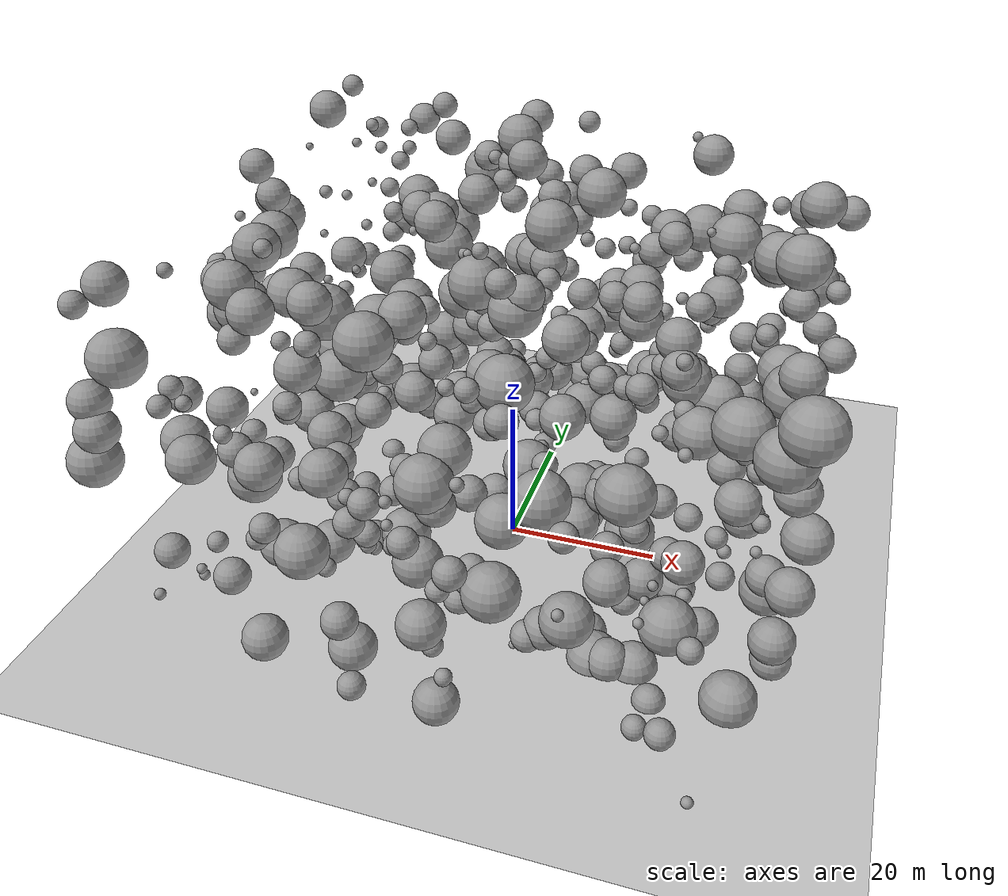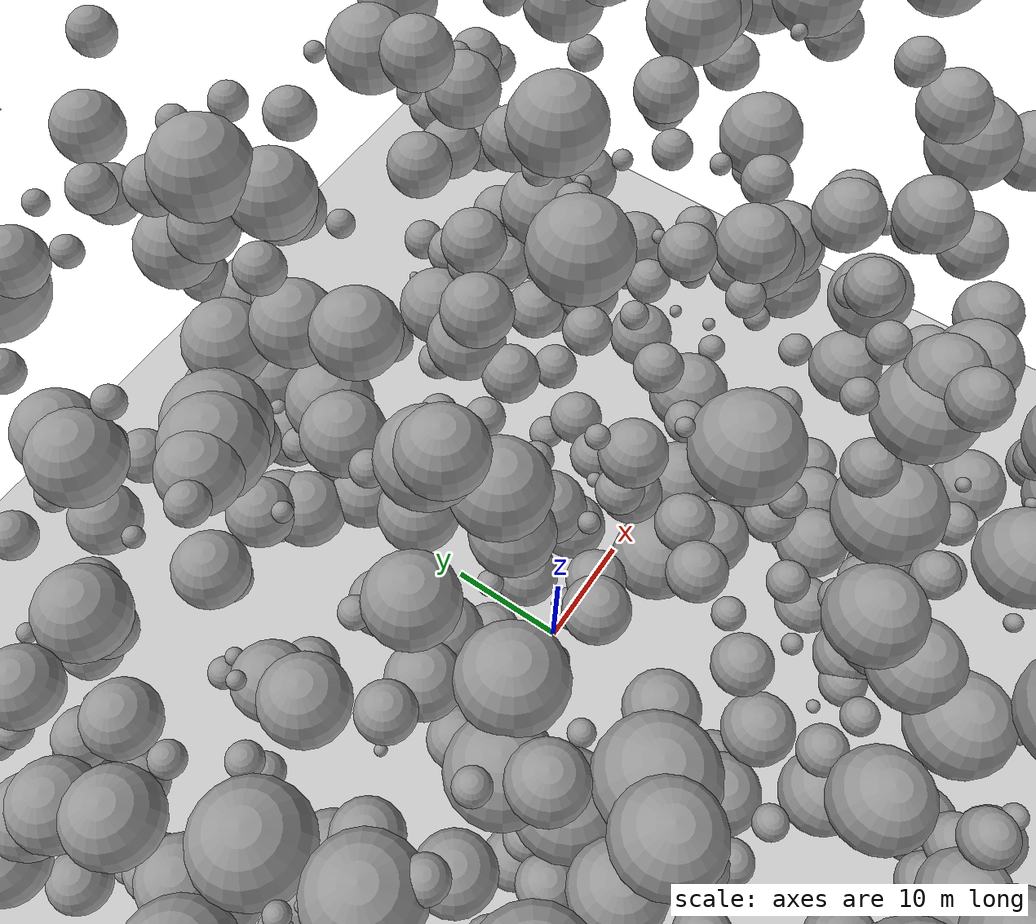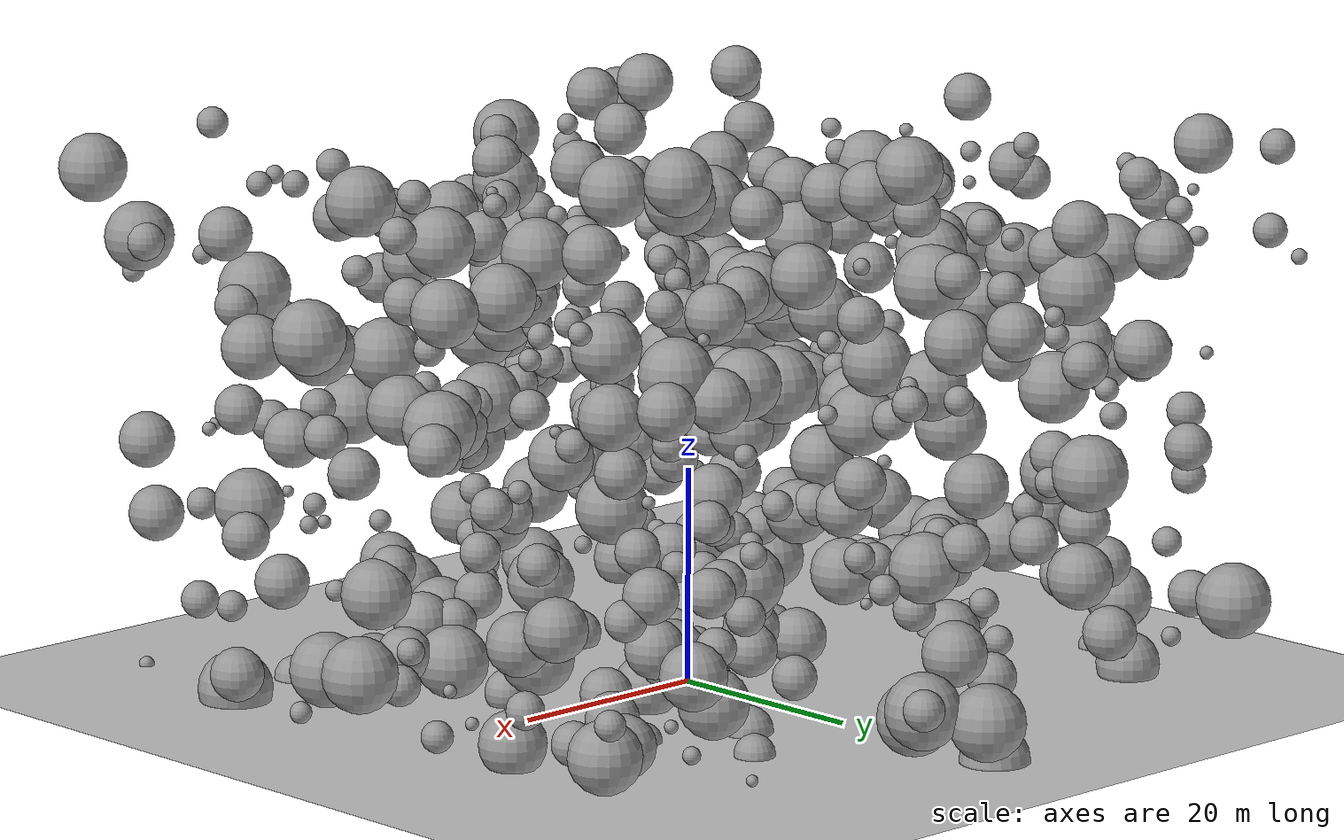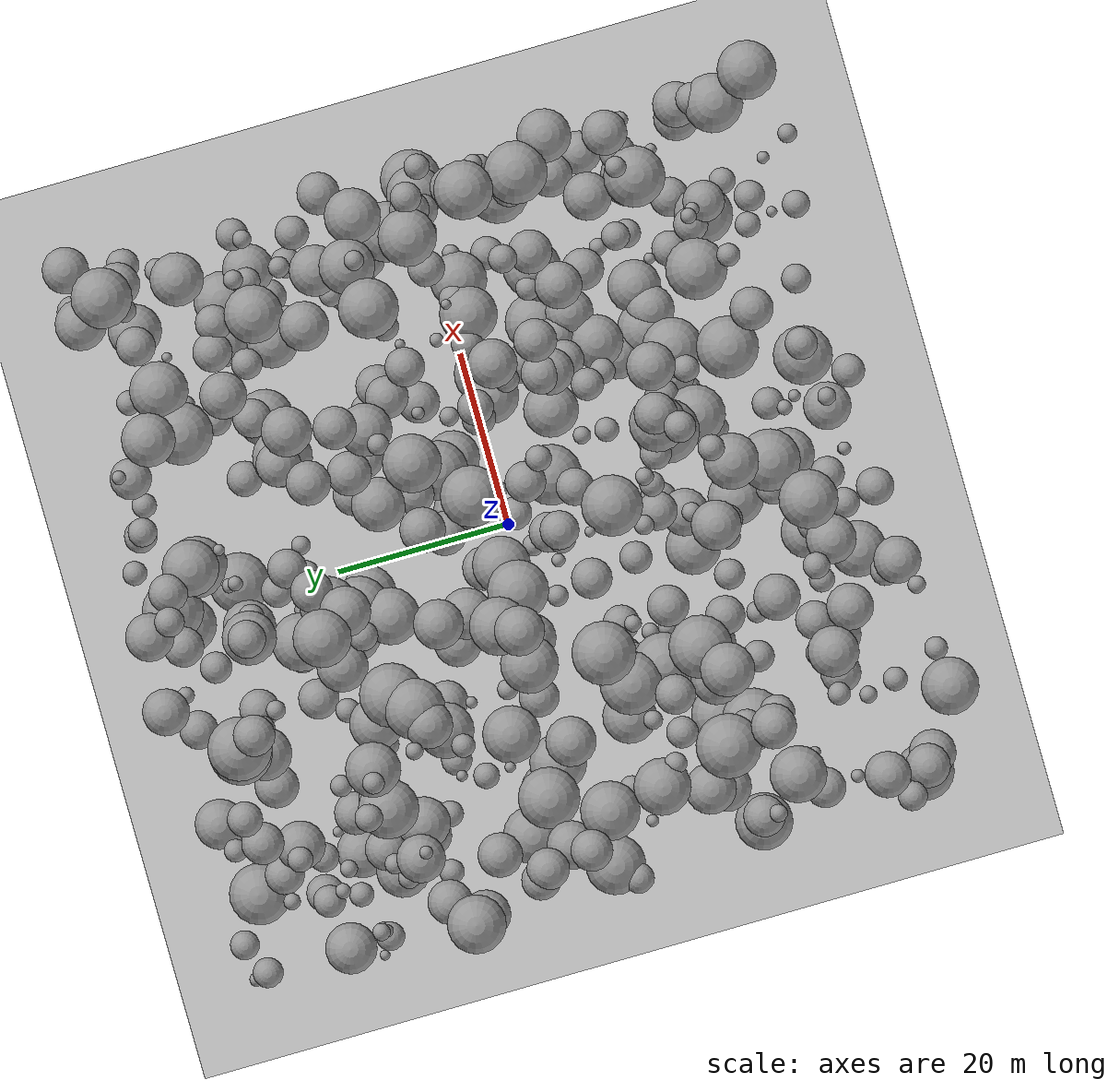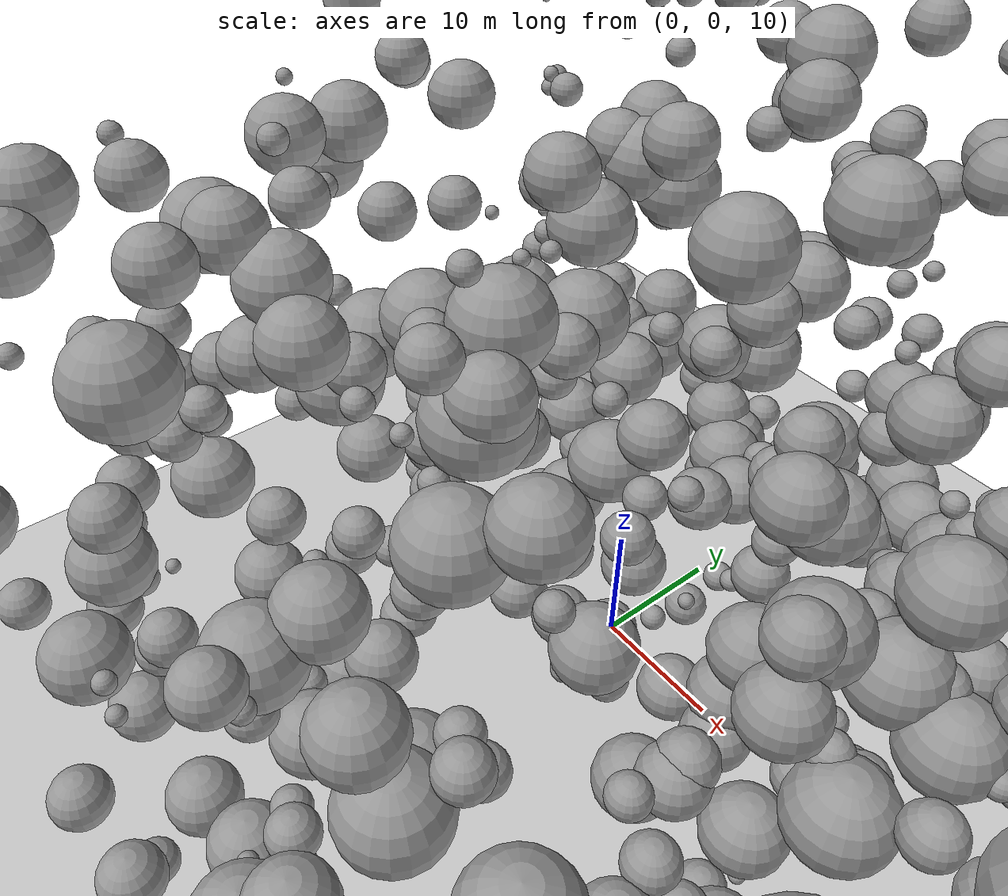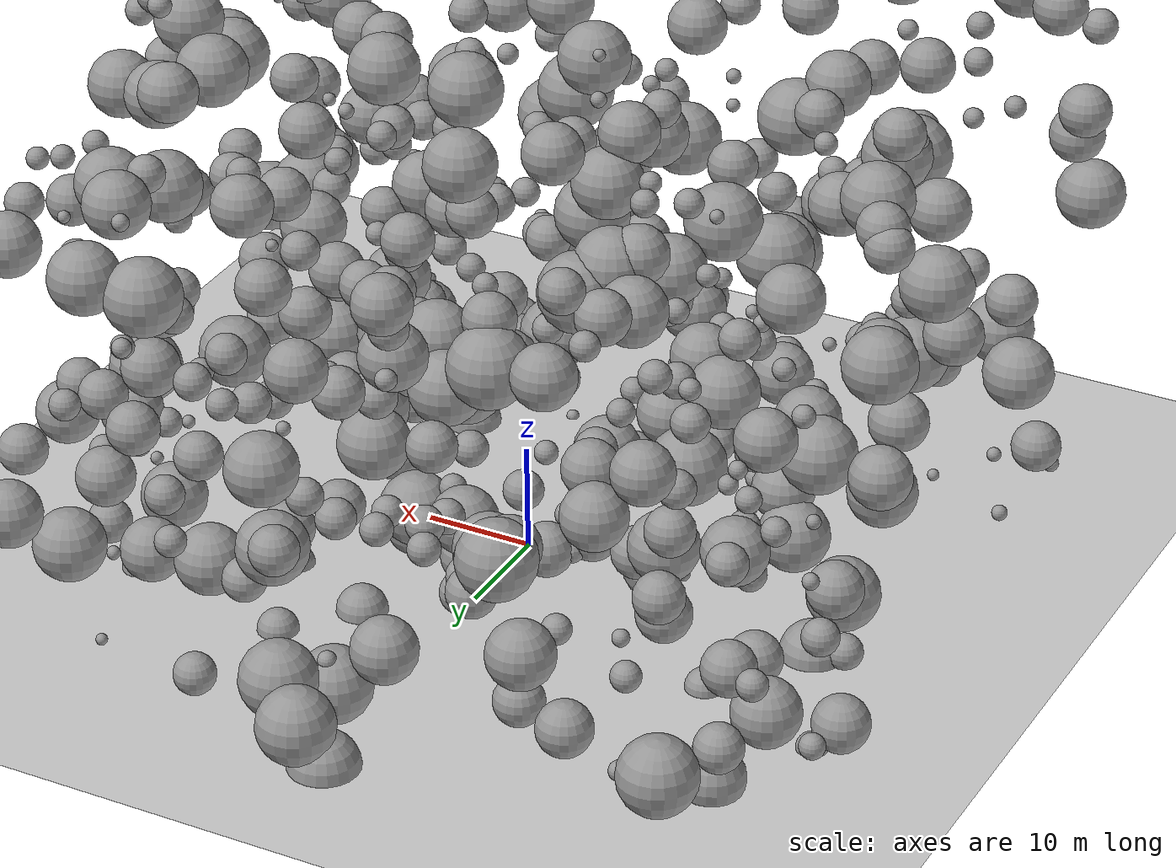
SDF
<?xml version="1.0" ?>
<sdf version='1.7'>
  <world name='default'>
    <light name='sun' type='directional'>
      <cast_shadows>1</cast_shadows>
      <pose>0 0 10 0 -0 0</pose>
      <diffuse>0.8 0.8 0.8 1</diffuse>
      <specular>0.2 0.2 0.2 1</specular>
      <attenuation>
        <range>1000</range>
        <constant>0.9</constant>
        <linear>0.01</linear>
        <quadratic>0.001</quadratic>
      </attenuation>
      <direction>-0.5 0.1 -0.9</direction>
      <spot>
        <inner_angle>0</inner_angle>
        <outer_angle>0</outer_angle>
        <falloff>0</falloff>
      </spot>
    </light>
    <model name='ground_plane'>
      <static>1</static>
      <link name='link'>
        <collision name='collision'>
          <geometry>
            <plane>
              <normal>0 0 1</normal>
              <size>100 100</size>
            </plane>
          </geometry>
          <surface>
            <contact>
              <collide_bitmask>65535</collide_bitmask>
              <ode/>
            </contact>
            <friction>
              <ode>
                <mu>100</mu>
                <mu2>50</mu2>
              </ode>
              <torsional>
                <ode/>
              </torsional>
            </friction>
            <bounce/>
          </surface>
          <max_contacts>10</max_contacts>
        </collision>
        <visual name='visual'>
          <cast_shadows>0</cast_shadows>
          <geometry>
            <plane>
              <normal>0 0 1</normal>
              <size>100 100</size>
            </plane>
          </geometry>
          <material>
            <script>
              <uri>file://media/materials/scripts/gazebo.material</uri>
              <name>Gazebo/Grey</name>
            </script>
          </material>
        </visual>
        <self_collide>0</self_collide>
        <enable_wind>0</enable_wind>
        <kinematic>0</kinematic>
      </link>
    </model>
    <gravity>0 0 -9.8</gravity>
    <magnetic_field>6e-06 2.3e-05 -4.2e-05</magnetic_field>
    <atmosphere type='adiabatic'/>
    <physics type='ode'>
      <max_step_size>0.001</max_step_size>
      <real_time_factor>1</real_time_factor>
      <real_time_update_rate>1000</real_time_update_rate>
    </physics>
    <scene>
      <ambient>0.4 0.4 0.4 1</ambient>
      <background>0.7 0.7 0.7 1</background>
      <shadows>1</shadows>
    </scene>
    <wind/>
    <spherical_coordinates>
      <surface_model>EARTH_WGS84</surface_model>
      <latitude_deg>0</latitude_deg>
      <longitude_deg>0</longitude_deg>
      <elevation>0</elevation>
      <heading_deg>0</heading_deg>
    </spherical_coordinates>

    <model name="sphere_0">
    <static>1</static>
    <pose> 20 28 15 0 0 0 </pose>
      <link name="link">
        <inertial>
          <mass>2270.6556930112333</mass>
          <inertia>
            <ixx>2802.7631227502798</ixx>
            <iyy>2802.7631227502798</iyy>
            <izz>2802.7631227502798</izz>
            <ixy>0</ixy>
            <ixz>0</ixz>
            <iyz>0</iyz>
          </inertia>
        </inertial>
        <collision name="collision">
          <geometry>
            <sphere>
              <radius>1.7566593790727731</radius>
            </sphere>
          </geometry>
        </collision>
        <visual name="visual">
          <geometry>
            <sphere>
              <radius>1.7566593790727731</radius>
            </sphere>
          </geometry>
          <material>
            <script>
              <uri>file://media/materials/scripts/gazebo.material</uri>
              <name>Gazebo/Grey</name>
            </script>
          </material>
        </visual>
      </link>
    </model>

    <model name="sphere_1">
    <static>1</static>
    <pose> 13 0 39 0 0 0 </pose>
      <link name="link">
        <inertial>
          <mass>3048.6699209422272</mass>
          <inertia>
            <ixx>4579.85359413972</ixx>
            <iyy>4579.85359413972</iyy>
            <izz>4579.85359413972</izz>
            <ixy>0</ixy>
            <ixz>0</ixz>
            <iyz>0</iyz>
          </inertia>
        </inertial>
        <collision name="collision">
          <geometry>
            <sphere>
              <radius>1.93794121379119</radius>
            </sphere>
          </geometry>
        </collision>
        <visual name="visual">
          <geometry>
            <sphere>
              <radius>1.93794121379119</radius>
            </sphere>
          </geometry>
          <material>
            <script>
              <uri>file://media/materials/scripts/gazebo.material</uri>
              <name>Gazebo/Grey</name>
            </script>
          </material>
        </visual>
      </link>
    </model>

    <model name="sphere_2">
    <static>1</static>
    <pose> -18 14 41 0 0 0 </pose>
      <link name="link">
        <inertial>
          <mass>7141.995812192565</mass>
          <inertia>
            <ixx>18924.89900281907</ixx>
            <iyy>18924.89900281907</iyy>
            <izz>18924.89900281907</izz>
            <ixy>0</ixy>
            <ixz>0</ixz>
            <iyz>0</iyz>
          </inertia>
        </inertial>
        <collision name="collision">
          <geometry>
            <sphere>
              <radius>2.573813022834022</radius>
            </sphere>
          </geometry>
        </collision>
        <visual name="visual">
          <geometry>
            <sphere>
              <radius>2.573813022834022</radius>
            </sphere>
          </geometry>
          <material>
            <script>
              <uri>file://media/materials/scripts/gazebo.material</uri>
              <name>Gazebo/Grey</name>
            </script>
          </material>
        </visual>
      </link>
    </model>

    <model name="sphere_3">
    <static>1</static>
    <pose> -4 2 24 0 0 0 </pose>
      <link name="link">
        <inertial>
          <mass>13485.373694115648</mass>
          <inertia>
            <ixx>54589.09502546419</ixx>
            <iyy>54589.09502546419</iyy>
            <izz>54589.09502546419</izz>
            <ixy>0</ixy>
            <ixz>0</ixz>
            <iyz>0</iyz>
          </inertia>
        </inertial>
        <collision name="collision">
          <geometry>
            <sphere>
              <radius>3.1812035528028293</radius>
            </sphere>
          </geometry>
        </collision>
        <visual name="visual">
          <geometry>
            <sphere>
              <radius>3.1812035528028293</radius>
            </sphere>
          </geometry>
          <material>
            <script>
              <uri>file://media/materials/scripts/gazebo.material</uri>
              <name>Gazebo/Grey</name>
            </script>
          </material>
        </visual>
      </link>
    </model>

    <model name="sphere_4">
    <static>1</static>
    <pose> 16 38 47 0 0 0 </pose>
      <link name="link">
        <inertial>
          <mass>164.46159977636265</mass>
          <inertia>
            <ixx>35.27294890430878</ixx>
            <iyy>35.27294890430878</iyy>
            <izz>35.27294890430878</izz>
            <ixy>0</ixy>
            <ixz>0</ixz>
            <iyz>0</iyz>
          </inertia>
        </inertial>
        <collision name="collision">
          <geometry>
            <sphere>
              <radius>0.732248741136081</radius>
            </sphere>
          </geometry>
        </collision>
        <visual name="visual">
          <geometry>
            <sphere>
              <radius>0.732248741136081</radius>
            </sphere>
          </geometry>
          <material>
            <script>
              <uri>file://media/materials/scripts/gazebo.material</uri>
              <name>Gazebo/Grey</name>
            </script>
          </material>
        </visual>
      </link>
    </model>

    <model name="sphere_5">
    <static>1</static>
    <pose> 29 17 21 0 0 0 </pose>
      <link name="link">
        <inertial>
          <mass>191.27032338474353</mass>
          <inertia>
            <ixx>45.367714927860675</ixx>
            <iyy>45.367714927860675</iyy>
            <izz>45.367714927860675</izz>
            <ixy>0</ixy>
            <ixz>0</ixz>
            <iyz>0</iyz>
          </inertia>
        </inertial>
        <collision name="collision">
          <geometry>
            <sphere>
              <radius>0.7700513045604033</radius>
            </sphere>
          </geometry>
        </collision>
        <visual name="visual">
          <geometry>
            <sphere>
              <radius>0.7700513045604033</radius>
            </sphere>
          </geometry>
          <material>
            <script>
              <uri>file://media/materials/scripts/gazebo.material</uri>
              <name>Gazebo/Grey</name>
            </script>
          </material>
        </visual>
      </link>
    </model>

    <model name="sphere_6">
    <static>1</static>
    <pose> -16 -6 34 0 0 0 </pose>
      <link name="link">
        <inertial>
          <mass>17364.775495447677</mass>
          <inertia>
            <ixx>83198.63603074141</ixx>
            <iyy>83198.63603074141</iyy>
            <izz>83198.63603074141</izz>
            <ixy>0</ixy>
            <ixz>0</ixz>
            <iyz>0</iyz>
          </inertia>
        </inertial>
        <collision name="collision">
          <geometry>
            <sphere>
              <radius>3.460935624013823</radius>
            </sphere>
          </geometry>
        </collision>
        <visual name="visual">
          <geometry>
            <sphere>
              <radius>3.460935624013823</radius>
            </sphere>
          </geometry>
          <material>
            <script>
              <uri>file://media/materials/scripts/gazebo.material</uri>
              <name>Gazebo/Grey</name>
            </script>
          </material>
        </visual>
      </link>
    </model>

    <model name="sphere_7">
    <static>1</static>
    <pose> -14 -10 26 0 0 0 </pose>
      <link name="link">
        <inertial>
          <mass>341.6740746308729</mass>
          <inertia>
            <ixx>119.31296269159577</ixx>
            <iyy>119.31296269159577</iyy>
            <izz>119.31296269159577</izz>
            <ixy>0</ixy>
            <ixz>0</ixz>
            <iyz>0</iyz>
          </inertia>
        </inertial>
        <collision name="collision">
          <geometry>
            <sphere>
              <radius>0.9343461617193105</radius>
            </sphere>
          </geometry>
        </collision>
        <visual name="visual">
          <geometry>
            <sphere>
              <radius>0.9343461617193105</radius>
            </sphere>
          </geometry>
          <material>
            <script>
              <uri>file://media/materials/scripts/gazebo.material</uri>
              <name>Gazebo/Grey</name>
            </script>
          </material>
        </visual>
      </link>
    </model>

    <model name="sphere_8">
    <static>1</static>
    <pose> -1 -32 10 0 0 0 </pose>
      <link name="link">
        <inertial>
          <mass>11092.84915670774</mass>
          <inertia>
            <ixx>39422.070545254806</ixx>
            <iyy>39422.070545254806</iyy>
            <izz>39422.070545254806</izz>
            <ixy>0</ixy>
            <ixz>0</ixz>
            <iyz>0</iyz>
          </inertia>
        </inertial>
        <collision name="collision">
          <geometry>
            <sphere>
              <radius>2.9806993030238513</radius>
            </sphere>
          </geometry>
        </collision>
        <visual name="visual">
          <geometry>
            <sphere>
              <radius>2.9806993030238513</radius>
            </sphere>
          </geometry>
          <material>
            <script>
              <uri>file://media/materials/scripts/gazebo.material</uri>
              <name>Gazebo/Grey</name>
            </script>
          </material>
        </visual>
      </link>
    </model>

    <model name="sphere_9">
    <static>1</static>
    <pose> -4 -14 31 0 0 0 </pose>
      <link name="link">
        <inertial>
          <mass>518.8254719904191</mass>
          <inertia>
            <ixx>239.3516366783105</ixx>
            <iyy>239.3516366783105</iyy>
            <izz>239.3516366783105</izz>
            <ixy>0</ixy>
            <ixz>0</ixz>
            <iyz>0</iyz>
          </inertia>
        </inertial>
        <collision name="collision">
          <geometry>
            <sphere>
              <radius>1.0739339211712031</radius>
            </sphere>
          </geometry>
        </collision>
        <visual name="visual">
          <geometry>
            <sphere>
              <radius>1.0739339211712031</radius>
            </sphere>
          </geometry>
          <material>
            <script>
              <uri>file://media/materials/scripts/gazebo.material</uri>
              <name>Gazebo/Grey</name>
            </script>
          </material>
        </visual>
      </link>
    </model>

    <model name="sphere_10">
    <static>1</static>
    <pose> -7 1 36 0 0 0 </pose>
      <link name="link">
        <inertial>
          <mass>15034.051911871826</mass>
          <inertia>
            <ixx>65432.62261102709</ixx>
            <iyy>65432.62261102709</iyy>
            <izz>65432.62261102709</izz>
            <ixy>0</ixy>
            <ixz>0</ixz>
            <iyz>0</iyz>
          </inertia>
        </inertial>
        <collision name="collision">
          <geometry>
            <sphere>
              <radius>3.2985961321861437</radius>
            </sphere>
          </geometry>
        </collision>
        <visual name="visual">
          <geometry>
            <sphere>
              <radius>3.2985961321861437</radius>
            </sphere>
          </geometry>
          <material>
            <script>
              <uri>file://media/materials/scripts/gazebo.material</uri>
              <name>Gazebo/Grey</name>
            </script>
          </material>
        </visual>
      </link>
    </model>

    <model name="sphere_11">
    <static>1</static>
    <pose> 39 -30 24 0 0 0 </pose>
      <link name="link">
        <inertial>
          <mass>6761.3348610337325</mass>
          <inertia>
            <ixx>17273.81751408212</ixx>
            <iyy>17273.81751408212</iyy>
            <izz>17273.81751408212</izz>
            <ixy>0</ixy>
            <ixz>0</ixz>
            <iyz>0</iyz>
          </inertia>
        </inertial>
        <collision name="collision">
          <geometry>
            <sphere>
              <radius>2.5272484876502723</radius>
            </sphere>
          </geometry>
        </collision>
        <visual name="visual">
          <geometry>
            <sphere>
              <radius>2.5272484876502723</radius>
            </sphere>
          </geometry>
          <material>
            <script>
              <uri>file://media/materials/scripts/gazebo.material</uri>
              <name>Gazebo/Grey</name>
            </script>
          </material>
        </visual>
      </link>
    </model>

    <model name="sphere_12">
    <static>1</static>
    <pose> -18 -40 38 0 0 0 </pose>
      <link name="link">
        <inertial>
          <mass>368.6225510144716</mass>
          <inertia>
            <ixx>135.40584724380668</ixx>
            <iyy>135.40584724380668</iyy>
            <izz>135.40584724380668</izz>
            <ixy>0</ixy>
            <ixz>0</ixz>
            <iyz>0</iyz>
          </inertia>
        </inertial>
        <collision name="collision">
          <geometry>
            <sphere>
              <radius>0.9582917817031907</radius>
            </sphere>
          </geometry>
        </collision>
        <visual name="visual">
          <geometry>
            <sphere>
              <radius>0.9582917817031907</radius>
            </sphere>
          </geometry>
          <material>
            <script>
              <uri>file://media/materials/scripts/gazebo.material</uri>
              <name>Gazebo/Grey</name>
            </script>
          </material>
        </visual>
      </link>
    </model>

    <model name="sphere_13">
    <static>1</static>
    <pose> 18 -8 43 0 0 0 </pose>
      <link name="link">
        <inertial>
          <mass>5152.770641691379</mass>
          <inertia>
            <ixx>10983.369762803279</ixx>
            <iyy>10983.369762803279</iyy>
            <izz>10983.369762803279</izz>
            <ixy>0</ixy>
            <ixz>0</ixz>
            <iyz>0</iyz>
          </inertia>
        </inertial>
        <collision name="collision">
          <geometry>
            <sphere>
              <radius>2.3084336735061317</radius>
            </sphere>
          </geometry>
        </collision>
        <visual name="visual">
          <geometry>
            <sphere>
              <radius>2.3084336735061317</radius>
            </sphere>
          </geometry>
          <material>
            <script>
              <uri>file://media/materials/scripts/gazebo.material</uri>
              <name>Gazebo/Grey</name>
            </script>
          </material>
        </visual>
      </link>
    </model>

    <model name="sphere_14">
    <static>1</static>
    <pose> 0 -16 31 0 0 0 </pose>
      <link name="link">
        <inertial>
          <mass>1051.1044841971827</mass>
          <inertia>
            <ixx>776.3854716185958</ixx>
            <iyy>776.3854716185958</iyy>
            <izz>776.3854716185958</izz>
            <ixy>0</ixy>
            <ixz>0</ixz>
            <iyz>0</iyz>
          </inertia>
        </inertial>
        <collision name="collision">
          <geometry>
            <sphere>
              <radius>1.3588945593796224</radius>
            </sphere>
          </geometry>
        </collision>
        <visual name="visual">
          <geometry>
            <sphere>
              <radius>1.3588945593796224</radius>
            </sphere>
          </geometry>
          <material>
            <script>
              <uri>file://media/materials/scripts/gazebo.material</uri>
              <name>Gazebo/Grey</name>
            </script>
          </material>
        </visual>
      </link>
    </model>

    <model name="sphere_15">
    <static>1</static>
    <pose> 7 -22 0 0 0 0 </pose>
      <link name="link">
        <inertial>
          <mass>87.60431492458373</mass>
          <inertia>
            <ixx>12.34648731932379</ixx>
            <iyy>12.34648731932379</iyy>
            <izz>12.34648731932379</izz>
            <ixy>0</ixy>
            <ixz>0</ixz>
            <iyz>0</iyz>
          </inertia>
        </inertial>
        <collision name="collision">
          <geometry>
            <sphere>
              <radius>0.5935795945507261</radius>
            </sphere>
          </geometry>
        </collision>
        <visual name="visual">
          <geometry>
            <sphere>
              <radius>0.5935795945507261</radius>
            </sphere>
          </geometry>
          <material>
            <script>
              <uri>file://media/materials/scripts/gazebo.material</uri>
              <name>Gazebo/Grey</name>
            </script>
          </material>
        </visual>
      </link>
    </model>

    <model name="sphere_16">
    <static>1</static>
    <pose> -9 -32 23 0 0 0 </pose>
      <link name="link">
        <inertial>
          <mass>2516.7862203883064</mass>
          <inertia>
            <ixx>3327.194051744051</ixx>
            <iyy>3327.194051744051</iyy>
            <izz>3327.194051744051</izz>
            <ixy>0</ixy>
            <ixz>0</ixz>
            <iyz>0</iyz>
          </inertia>
        </inertial>
        <collision name="collision">
          <geometry>
            <sphere>
              <radius>1.8179666252693782</radius>
            </sphere>
          </geometry>
        </collision>
        <visual name="visual">
          <geometry>
            <sphere>
              <radius>1.8179666252693782</radius>
            </sphere>
          </geometry>
          <material>
            <script>
              <uri>file://media/materials/scripts/gazebo.material</uri>
              <name>Gazebo/Grey</name>
            </script>
          </material>
        </visual>
      </link>
    </model>

    <model name="sphere_17">
    <static>1</static>
    <pose> -16 -38 25 0 0 0 </pose>
      <link name="link">
        <inertial>
          <mass>1930.9557477305789</mass>
          <inertia>
            <ixx>2139.3809296141185</ixx>
            <iyy>2139.3809296141185</iyy>
            <izz>2139.3809296141185</izz>
            <ixy>0</ixy>
            <ixz>0</ixz>
            <iyz>0</iyz>
          </inertia>
        </inertial>
        <collision name="collision">
          <geometry>
            <sphere>
              <radius>1.6642857854308373</radius>
            </sphere>
          </geometry>
        </collision>
        <visual name="visual">
          <geometry>
            <sphere>
              <radius>1.6642857854308373</radius>
            </sphere>
          </geometry>
          <material>
            <script>
              <uri>file://media/materials/scripts/gazebo.material</uri>
              <name>Gazebo/Grey</name>
            </script>
          </material>
        </visual>
      </link>
    </model>

    <model name="sphere_18">
    <static>1</static>
    <pose> -40 14 26 0 0 0 </pose>
      <link name="link">
        <inertial>
          <mass>8225.452633346169</mass>
          <inertia>
            <ixx>23947.890376761054</ixx>
            <iyy>23947.890376761054</iyy>
            <izz>23947.890376761054</izz>
            <ixy>0</ixy>
            <ixz>0</ixz>
            <iyz>0</iyz>
          </inertia>
        </inertial>
        <collision name="collision">
          <geometry>
            <sphere>
              <radius>2.6978868553422295</radius>
            </sphere>
          </geometry>
        </collision>
        <visual name="visual">
          <geometry>
            <sphere>
              <radius>2.6978868553422295</radius>
            </sphere>
          </geometry>
          <material>
            <script>
              <uri>file://media/materials/scripts/gazebo.material</uri>
              <name>Gazebo/Grey</name>
            </script>
          </material>
        </visual>
      </link>
    </model>

    <model name="sphere_19">
    <static>1</static>
    <pose> 6 -23 20 0 0 0 </pose>
      <link name="link">
        <inertial>
          <mass>14718.632631495893</mass>
          <inertia>
            <ixx>63160.66510189505</ixx>
            <iyy>63160.66510189505</iyy>
            <izz>63160.66510189505</izz>
            <ixy>0</ixy>
            <ixz>0</ixz>
            <iyz>0</iyz>
          </inertia>
        </inertial>
        <collision name="collision">
          <geometry>
            <sphere>
              <radius>3.2753643580509237</radius>
            </sphere>
          </geometry>
        </collision>
        <visual name="visual">
          <geometry>
            <sphere>
              <radius>3.2753643580509237</radius>
            </sphere>
          </geometry>
          <material>
            <script>
              <uri>file://media/materials/scripts/gazebo.material</uri>
              <name>Gazebo/Grey</name>
            </script>
          </material>
        </visual>
      </link>
    </model>

    <model name="sphere_20">
    <static>1</static>
    <pose> -39 18 4 0 0 0 </pose>
      <link name="link">
        <inertial>
          <mass>6884.592858552692</mass>
          <inertia>
            <ixx>17801.831602850525</ixx>
            <iyy>17801.831602850525</iyy>
            <izz>17801.831602850525</izz>
            <ixy>0</ixy>
            <ixz>0</ixz>
            <iyz>0</iyz>
          </inertia>
        </inertial>
        <collision name="collision">
          <geometry>
            <sphere>
              <radius>2.5425132072564818</radius>
            </sphere>
          </geometry>
        </collision>
        <visual name="visual">
          <geometry>
            <sphere>
              <radius>2.5425132072564818</radius>
            </sphere>
          </geometry>
          <material>
            <script>
              <uri>file://media/materials/scripts/gazebo.material</uri>
              <name>Gazebo/Grey</name>
            </script>
          </material>
        </visual>
      </link>
    </model>

    <model name="sphere_21">
    <static>1</static>
    <pose> 6 40 34 0 0 0 </pose>
      <link name="link">
        <inertial>
          <mass>948.6665397999582</mass>
          <inertia>
            <ixx>654.420492024396</ixx>
            <iyy>654.420492024396</iyy>
            <izz>654.420492024396</izz>
            <ixy>0</ixy>
            <ixz>0</ixz>
            <iyz>0</iyz>
          </inertia>
        </inertial>
        <collision name="collision">
          <geometry>
            <sphere>
              <radius>1.3132326080472079</radius>
            </sphere>
          </geometry>
        </collision>
        <visual name="visual">
          <geometry>
            <sphere>
              <radius>1.3132326080472079</radius>
            </sphere>
          </geometry>
          <material>
            <script>
              <uri>file://media/materials/scripts/gazebo.material</uri>
              <name>Gazebo/Grey</name>
            </script>
          </material>
        </visual>
      </link>
    </model>

    <model name="sphere_22">
    <static>1</static>
    <pose> 19 34 46 0 0 0 </pose>
      <link name="link">
        <inertial>
          <mass>9752.387158366544</mass>
          <inertia>
            <ixx>31806.73874587203</ixx>
            <iyy>31806.73874587203</iyy>
            <izz>31806.73874587203</izz>
            <ixy>0</ixy>
            <ixz>0</ixz>
            <iyz>0</iyz>
          </inertia>
        </inertial>
        <collision name="collision">
          <geometry>
            <sphere>
              <radius>2.8554470301307804</radius>
            </sphere>
          </geometry>
        </collision>
        <visual name="visual">
          <geometry>
            <sphere>
              <radius>2.8554470301307804</radius>
            </sphere>
          </geometry>
          <material>
            <script>
              <uri>file://media/materials/scripts/gazebo.material</uri>
              <name>Gazebo/Grey</name>
            </script>
          </material>
        </visual>
      </link>
    </model>

    <model name="sphere_23">
    <static>1</static>
    <pose> -37 -36 36 0 0 0 </pose>
      <link name="link">
        <inertial>
          <mass>5814.141690737004</mass>
          <inertia>
            <ixx>13432.09033809364</ixx>
            <iyy>13432.09033809364</iyy>
            <izz>13432.09033809364</izz>
            <ixy>0</ixy>
            <ixz>0</ixz>
            <iyz>0</iyz>
          </inertia>
        </inertial>
        <collision name="collision">
          <geometry>
            <sphere>
              <radius>2.403250274974293</radius>
            </sphere>
          </geometry>
        </collision>
        <visual name="visual">
          <geometry>
            <sphere>
              <radius>2.403250274974293</radius>
            </sphere>
          </geometry>
          <material>
            <script>
              <uri>file://media/materials/scripts/gazebo.material</uri>
              <name>Gazebo/Grey</name>
            </script>
          </material>
        </visual>
      </link>
    </model>

    <model name="sphere_24">
    <static>1</static>
    <pose> 4 -38 9 0 0 0 </pose>
      <link name="link">
        <inertial>
          <mass>461.1085611241519</mass>
          <inertia>
            <ixx>196.64046585716275</ixx>
            <iyy>196.64046585716275</iyy>
            <izz>196.64046585716275</izz>
            <ixy>0</ixy>
            <ixz>0</ixz>
            <iyz>0</iyz>
          </inertia>
        </inertial>
        <collision name="collision">
          <geometry>
            <sphere>
              <radius>1.0325351826695544</radius>
            </sphere>
          </geometry>
        </collision>
        <visual name="visual">
          <geometry>
            <sphere>
              <radius>1.0325351826695544</radius>
            </sphere>
          </geometry>
          <material>
            <script>
              <uri>file://media/materials/scripts/gazebo.material</uri>
              <name>Gazebo/Grey</name>
            </script>
          </material>
        </visual>
      </link>
    </model>

    <model name="sphere_25">
    <static>1</static>
    <pose> -15 34 40 0 0 0 </pose>
      <link name="link">
        <inertial>
          <mass>17081.754802154046</mass>
          <inertia>
            <ixx>80950.9079854129</ixx>
            <iyy>80950.9079854129</iyy>
            <izz>80950.9079854129</izz>
            <ixy>0</ixy>
            <ixz>0</ixz>
            <iyz>0</iyz>
          </inertia>
        </inertial>
        <collision name="collision">
          <geometry>
            <sphere>
              <radius>3.4420297901579398</radius>
            </sphere>
          </geometry>
        </collision>
        <visual name="visual">
          <geometry>
            <sphere>
              <radius>3.4420297901579398</radius>
            </sphere>
          </geometry>
          <material>
            <script>
              <uri>file://media/materials/scripts/gazebo.material</uri>
              <name>Gazebo/Grey</name>
            </script>
          </material>
        </visual>
      </link>
    </model>

    <model name="sphere_26">
    <static>1</static>
    <pose> 32 -39 0 0 0 0 </pose>
      <link name="link">
        <inertial>
          <mass>146.71801015854183</mass>
          <inertia>
            <ixx>29.161283317194567</ixx>
            <iyy>29.161283317194567</iyy>
            <izz>29.161283317194567</izz>
            <ixy>0</ixy>
            <ixz>0</ixz>
            <iyz>0</iyz>
          </inertia>
        </inertial>
        <collision name="collision">
          <geometry>
            <sphere>
              <radius>0.7049066478409625</radius>
            </sphere>
          </geometry>
        </collision>
        <visual name="visual">
          <geometry>
            <sphere>
              <radius>0.7049066478409625</radius>
            </sphere>
          </geometry>
          <material>
            <script>
              <uri>file://media/materials/scripts/gazebo.material</uri>
              <name>Gazebo/Grey</name>
            </script>
          </material>
        </visual>
      </link>
    </model>

    <model name="sphere_27">
    <static>1</static>
    <pose> -29 -16 39 0 0 0 </pose>
      <link name="link">
        <inertial>
          <mass>17865.77479721656</mass>
          <inertia>
            <ixx>87237.66055250104</ixx>
            <iyy>87237.66055250104</iyy>
            <izz>87237.66055250104</izz>
            <ixy>0</ixy>
            <ixz>0</ixz>
            <iyz>0</iyz>
          </inertia>
        </inertial>
        <collision name="collision">
          <geometry>
            <sphere>
              <radius>3.493904917503813</radius>
            </sphere>
          </geometry>
        </collision>
        <visual name="visual">
          <geometry>
            <sphere>
              <radius>3.493904917503813</radius>
            </sphere>
          </geometry>
          <material>
            <script>
              <uri>file://media/materials/scripts/gazebo.material</uri>
              <name>Gazebo/Grey</name>
            </script>
          </material>
        </visual>
      </link>
    </model>

    <model name="sphere_28">
    <static>1</static>
    <pose> -4 30 42 0 0 0 </pose>
      <link name="link">
        <inertial>
          <mass>3500.1223190484397</mass>
          <inertia>
            <ixx>5765.092612627549</ixx>
            <iyy>5765.092612627549</iyy>
            <izz>5765.092612627549</izz>
            <ixy>0</ixy>
            <ixz>0</ixz>
            <iyz>0</iyz>
          </inertia>
        </inertial>
        <collision name="collision">
          <geometry>
            <sphere>
              <radius>2.0292312301328566</radius>
            </sphere>
          </geometry>
        </collision>
        <visual name="visual">
          <geometry>
            <sphere>
              <radius>2.0292312301328566</radius>
            </sphere>
          </geometry>
          <material>
            <script>
              <uri>file://media/materials/scripts/gazebo.material</uri>
              <name>Gazebo/Grey</name>
            </script>
          </material>
        </visual>
      </link>
    </model>

    <model name="sphere_29">
    <static>1</static>
    <pose> 16 20 40 0 0 0 </pose>
      <link name="link">
        <inertial>
          <mass>8313.901943358154</mass>
          <inertia>
            <ixx>24378.61797444489</ixx>
            <iyy>24378.61797444489</iyy>
            <izz>24378.61797444489</izz>
            <ixy>0</ixy>
            <ixz>0</ixz>
            <iyz>0</iyz>
          </inertia>
        </inertial>
        <collision name="collision">
          <geometry>
            <sphere>
              <radius>2.7075226362523988</radius>
            </sphere>
          </geometry>
        </collision>
        <visual name="visual">
          <geometry>
            <sphere>
              <radius>2.7075226362523988</radius>
            </sphere>
          </geometry>
          <material>
            <script>
              <uri>file://media/materials/scripts/gazebo.material</uri>
              <name>Gazebo/Grey</name>
            </script>
          </material>
        </visual>
      </link>
    </model>

    <model name="sphere_30">
    <static>1</static>
    <pose> 11 -22 4 0 0 0 </pose>
      <link name="link">
        <inertial>
          <mass>8712.248352823823</mass>
          <inertia>
            <ixx>26356.313424238208</ixx>
            <iyy>26356.313424238208</iyy>
            <izz>26356.313424238208</izz>
            <ixy>0</ixy>
            <ixz>0</ixz>
            <iyz>0</iyz>
          </inertia>
        </inertial>
        <collision name="collision">
          <geometry>
            <sphere>
              <radius>2.7500919357448264</radius>
            </sphere>
          </geometry>
        </collision>
        <visual name="visual">
          <geometry>
            <sphere>
              <radius>2.7500919357448264</radius>
            </sphere>
          </geometry>
          <material>
            <script>
              <uri>file://media/materials/scripts/gazebo.material</uri>
              <name>Gazebo/Grey</name>
            </script>
          </material>
        </visual>
      </link>
    </model>

    <model name="sphere_31">
    <static>1</static>
    <pose> 24 -28 17 0 0 0 </pose>
      <link name="link">
        <inertial>
          <mass>61.999389655790715</mass>
          <inertia>
            <ixx>6.939261845150968</ixx>
            <iyy>6.939261845150968</iyy>
            <izz>6.939261845150968</izz>
            <ixy>0</ixy>
            <ixz>0</ixz>
            <iyz>0</iyz>
          </inertia>
        </inertial>
        <collision name="collision">
          <geometry>
            <sphere>
              <radius>0.5289723054267761</radius>
            </sphere>
          </geometry>
        </collision>
        <visual name="visual">
          <geometry>
            <sphere>
              <radius>0.5289723054267761</radius>
            </sphere>
          </geometry>
          <material>
            <script>
              <uri>file://media/materials/scripts/gazebo.material</uri>
              <name>Gazebo/Grey</name>
            </script>
          </material>
        </visual>
      </link>
    </model>

    <model name="sphere_32">
    <static>1</static>
    <pose> 26 -27 47 0 0 0 </pose>
      <link name="link">
        <inertial>
          <mass>250.42265479350073</mass>
          <inertia>
            <ixx>71.08701484467682</ixx>
            <iyy>71.08701484467682</iyy>
            <izz>71.08701484467682</izz>
            <ixy>0</ixy>
            <ixz>0</ixz>
            <iyz>0</iyz>
          </inertia>
        </inertial>
        <collision name="collision">
          <geometry>
            <sphere>
              <radius>0.8424193528870205</radius>
            </sphere>
          </geometry>
        </collision>
        <visual name="visual">
          <geometry>
            <sphere>
              <radius>0.8424193528870205</radius>
            </sphere>
          </geometry>
          <material>
            <script>
              <uri>file://media/materials/scripts/gazebo.material</uri>
              <name>Gazebo/Grey</name>
            </script>
          </material>
        </visual>
      </link>
    </model>

    <model name="sphere_33">
    <static>1</static>
    <pose> -13 -30 44 0 0 0 </pose>
      <link name="link">
        <inertial>
          <mass>1204.7544548250878</mass>
          <inertia>
            <ixx>974.6121470762206</ixx>
            <iyy>974.6121470762206</iyy>
            <izz>974.6121470762206</izz>
            <ixy>0</ixy>
            <ixz>0</ixz>
            <iyz>0</iyz>
          </inertia>
        </inertial>
        <collision name="collision">
          <geometry>
            <sphere>
              <radius>1.4221213087885949</radius>
            </sphere>
          </geometry>
        </collision>
        <visual name="visual">
          <geometry>
            <sphere>
              <radius>1.4221213087885949</radius>
            </sphere>
          </geometry>
          <material>
            <script>
              <uri>file://media/materials/scripts/gazebo.material</uri>
              <name>Gazebo/Grey</name>
            </script>
          </material>
        </visual>
      </link>
    </model>

    <model name="sphere_34">
    <static>1</static>
    <pose> 25 -11 5 0 0 0 </pose>
      <link name="link">
        <inertial>
          <mass>6659.506574605881</mass>
          <inertia>
            <ixx>16842.41400105832</ixx>
            <iyy>16842.41400105832</iyy>
            <izz>16842.41400105832</izz>
            <ixy>0</ixy>
            <ixz>0</ixz>
            <iyz>0</iyz>
          </inertia>
        </inertial>
        <collision name="collision">
          <geometry>
            <sphere>
              <radius>2.5144971491569468</radius>
            </sphere>
          </geometry>
        </collision>
        <visual name="visual">
          <geometry>
            <sphere>
              <radius>2.5144971491569468</radius>
            </sphere>
          </geometry>
          <material>
            <script>
              <uri>file://media/materials/scripts/gazebo.material</uri>
              <name>Gazebo/Grey</name>
            </script>
          </material>
        </visual>
      </link>
    </model>

    <model name="sphere_35">
    <static>1</static>
    <pose> -39 25 22 0 0 0 </pose>
      <link name="link">
        <inertial>
          <mass>152.28715886802905</mass>
          <inertia>
            <ixx>31.029377219115755</ixx>
            <iyy>31.029377219115755</iyy>
            <izz>31.029377219115755</izz>
            <ixy>0</ixy>
            <ixz>0</ixz>
            <iyz>0</iyz>
          </inertia>
        </inertial>
        <collision name="collision">
          <geometry>
            <sphere>
              <radius>0.7137151107000433</radius>
            </sphere>
          </geometry>
        </collision>
        <visual name="visual">
          <geometry>
            <sphere>
              <radius>0.7137151107000433</radius>
            </sphere>
          </geometry>
          <material>
            <script>
              <uri>file://media/materials/scripts/gazebo.material</uri>
              <name>Gazebo/Grey</name>
            </script>
          </material>
        </visual>
      </link>
    </model>

    <model name="sphere_36">
    <static>1</static>
    <pose> -39 -18 19 0 0 0 </pose>
      <link name="link">
        <inertial>
          <mass>13480.657258122761</mass>
          <inertia>
            <ixx>54557.27833756018</ixx>
            <iyy>54557.27833756018</iyy>
            <izz>54557.27833756018</izz>
            <ixy>0</ixy>
            <ixz>0</ixz>
            <iyz>0</iyz>
          </inertia>
        </inertial>
        <collision name="collision">
          <geometry>
            <sphere>
              <radius>3.180832640019842</radius>
            </sphere>
          </geometry>
        </collision>
        <visual name="visual">
          <geometry>
            <sphere>
              <radius>3.180832640019842</radius>
            </sphere>
          </geometry>
          <material>
            <script>
              <uri>file://media/materials/scripts/gazebo.material</uri>
              <name>Gazebo/Grey</name>
            </script>
          </material>
        </visual>
      </link>
    </model>

    <model name="sphere_37">
    <static>1</static>
    <pose> 15 -31 41 0 0 0 </pose>
      <link name="link">
        <inertial>
          <mass>5170.2749976728355</mass>
          <inertia>
            <ixx>11045.62573122916</ixx>
            <iyy>11045.62573122916</iyy>
            <izz>11045.62573122916</izz>
            <ixy>0</ixy>
            <ixz>0</ixz>
            <iyz>0</iyz>
          </inertia>
        </inertial>
        <collision name="collision">
          <geometry>
            <sphere>
              <radius>2.311044694371895</radius>
            </sphere>
          </geometry>
        </collision>
        <visual name="visual">
          <geometry>
            <sphere>
              <radius>2.311044694371895</radius>
            </sphere>
          </geometry>
          <material>
            <script>
              <uri>file://media/materials/scripts/gazebo.material</uri>
              <name>Gazebo/Grey</name>
            </script>
          </material>
        </visual>
      </link>
    </model>

    <model name="sphere_38">
    <static>1</static>
    <pose> 6 13 27 0 0 0 </pose>
      <link name="link">
        <inertial>
          <mass>11012.262104970456</mass>
          <inertia>
            <ixx>38945.90657782049</ixx>
            <iyy>38945.90657782049</iyy>
            <izz>38945.90657782049</izz>
            <ixy>0</ixy>
            <ixz>0</ixz>
            <iyz>0</iyz>
          </inertia>
        </inertial>
        <collision name="collision">
          <geometry>
            <sphere>
              <radius>2.9734637165390647</radius>
            </sphere>
          </geometry>
        </collision>
        <visual name="visual">
          <geometry>
            <sphere>
              <radius>2.9734637165390647</radius>
            </sphere>
          </geometry>
          <material>
            <script>
              <uri>file://media/materials/scripts/gazebo.material</uri>
              <name>Gazebo/Grey</name>
            </script>
          </material>
        </visual>
      </link>
    </model>

    <model name="sphere_39">
    <static>1</static>
    <pose> 31 -17 17 0 0 0 </pose>
      <link name="link">
        <inertial>
          <mass>241.15153081747712</mass>
          <inertia>
            <ixx>66.75507533729944</ixx>
            <iyy>66.75507533729944</iyy>
            <izz>66.75507533729944</izz>
            <ixy>0</ixy>
            <ixz>0</ixz>
            <iyz>0</iyz>
          </inertia>
        </inertial>
        <collision name="collision">
          <geometry>
            <sphere>
              <radius>0.8318923641001357</radius>
            </sphere>
          </geometry>
        </collision>
        <visual name="visual">
          <geometry>
            <sphere>
              <radius>0.8318923641001357</radius>
            </sphere>
          </geometry>
          <material>
            <script>
              <uri>file://media/materials/scripts/gazebo.material</uri>
              <name>Gazebo/Grey</name>
            </script>
          </material>
        </visual>
      </link>
    </model>

    <model name="sphere_40">
    <static>1</static>
    <pose> -30 34 23 0 0 0 </pose>
      <link name="link">
        <inertial>
          <mass>4261.430314649051</mass>
          <inertia>
            <ixx>8003.130589517396</ixx>
            <iyy>8003.130589517396</iyy>
            <izz>8003.130589517396</izz>
            <ixy>0</ixy>
            <ixz>0</ixz>
            <iyz>0</iyz>
          </inertia>
        </inertial>
        <collision name="collision">
          <geometry>
            <sphere>
              <radius>2.1668171313871447</radius>
            </sphere>
          </geometry>
        </collision>
        <visual name="visual">
          <geometry>
            <sphere>
              <radius>2.1668171313871447</radius>
            </sphere>
          </geometry>
          <material>
            <script>
              <uri>file://media/materials/scripts/gazebo.material</uri>
              <name>Gazebo/Grey</name>
            </script>
          </material>
        </visual>
      </link>
    </model>

    <model name="sphere_41">
    <static>1</static>
    <pose> -8 26 14 0 0 0 </pose>
      <link name="link">
        <inertial>
          <mass>1766.1307490663748</mass>
          <inertia>
            <ixx>1843.765445693627</ixx>
            <iyy>1843.765445693627</iyy>
            <izz>1843.765445693627</izz>
            <ixy>0</ixy>
            <ixz>0</ixz>
            <iyz>0</iyz>
          </inertia>
        </inertial>
        <collision name="collision">
          <geometry>
            <sphere>
              <radius>1.6155165601072692</radius>
            </sphere>
          </geometry>
        </collision>
        <visual name="visual">
          <geometry>
            <sphere>
              <radius>1.6155165601072692</radius>
            </sphere>
          </geometry>
          <material>
            <script>
              <uri>file://media/materials/scripts/gazebo.material</uri>
              <name>Gazebo/Grey</name>
            </script>
          </material>
        </visual>
      </link>
    </model>

    <model name="sphere_42">
    <static>1</static>
    <pose> -27 2 10 0 0 0 </pose>
      <link name="link">
        <inertial>
          <mass>13778.366554385564</mass>
          <inertia>
            <ixx>56580.112817841626</ixx>
            <iyy>56580.112817841626</iyy>
            <izz>56580.112817841626</izz>
            <ixy>0</ixy>
            <ixz>0</ixz>
            <iyz>0</iyz>
          </inertia>
        </inertial>
        <collision name="collision">
          <geometry>
            <sphere>
              <radius>3.2040777173975967</radius>
            </sphere>
          </geometry>
        </collision>
        <visual name="visual">
          <geometry>
            <sphere>
              <radius>3.2040777173975967</radius>
            </sphere>
          </geometry>
          <material>
            <script>
              <uri>file://media/materials/scripts/gazebo.material</uri>
              <name>Gazebo/Grey</name>
            </script>
          </material>
        </visual>
      </link>
    </model>

    <model name="sphere_43">
    <static>1</static>
    <pose> 2 32 6 0 0 0 </pose>
      <link name="link">
        <inertial>
          <mass>255.80845116134995</mass>
          <inertia>
            <ixx>73.65333202269129</ixx>
            <iyy>73.65333202269129</iyy>
            <izz>73.65333202269129</izz>
            <ixy>0</ixy>
            <ixz>0</ixz>
            <iyz>0</iyz>
          </inertia>
        </inertial>
        <collision name="collision">
          <geometry>
            <sphere>
              <radius>0.8484158231878176</radius>
            </sphere>
          </geometry>
        </collision>
        <visual name="visual">
          <geometry>
            <sphere>
              <radius>0.8484158231878176</radius>
            </sphere>
          </geometry>
          <material>
            <script>
              <uri>file://media/materials/scripts/gazebo.material</uri>
              <name>Gazebo/Grey</name>
            </script>
          </material>
        </visual>
      </link>
    </model>

    <model name="sphere_44">
    <static>1</static>
    <pose> 13 27 8 0 0 0 </pose>
      <link name="link">
        <inertial>
          <mass>3346.033699596498</mass>
          <inertia>
            <ixx>5348.328852654719</ixx>
            <iyy>5348.328852654719</iyy>
            <izz>5348.328852654719</izz>
            <ixy>0</ixy>
            <ixz>0</ixz>
            <iyz>0</iyz>
          </inertia>
        </inertial>
        <collision name="collision">
          <geometry>
            <sphere>
              <radius>1.9990050922982885</radius>
            </sphere>
          </geometry>
        </collision>
        <visual name="visual">
          <geometry>
            <sphere>
              <radius>1.9990050922982885</radius>
            </sphere>
          </geometry>
          <material>
            <script>
              <uri>file://media/materials/scripts/gazebo.material</uri>
              <name>Gazebo/Grey</name>
            </script>
          </material>
        </visual>
      </link>
    </model>

    <model name="sphere_45">
    <static>1</static>
    <pose> 27 30 41 0 0 0 </pose>
      <link name="link">
        <inertial>
          <mass>68.0435052667013</mass>
          <inertia>
            <ixx>8.102991478464112</ixx>
            <iyy>8.102991478464112</iyy>
            <izz>8.102991478464112</izz>
            <ixy>0</ixy>
            <ixz>0</ixz>
            <iyz>0</iyz>
          </inertia>
        </inertial>
        <collision name="collision">
          <geometry>
            <sphere>
              <radius>0.5456314014576218</radius>
            </sphere>
          </geometry>
        </collision>
        <visual name="visual">
          <geometry>
            <sphere>
              <radius>0.5456314014576218</radius>
            </sphere>
          </geometry>
          <material>
            <script>
              <uri>file://media/materials/scripts/gazebo.material</uri>
              <name>Gazebo/Grey</name>
            </script>
          </material>
        </visual>
      </link>
    </model>

    <model name="sphere_46">
    <static>1</static>
    <pose> 0 -25 30 0 0 0 </pose>
      <link name="link">
        <inertial>
          <mass>11979.470812842934</mass>
          <inertia>
            <ixx>44812.273166999315</ixx>
            <iyy>44812.273166999315</iyy>
            <izz>44812.273166999315</izz>
            <ixy>0</ixy>
            <ixz>0</ixz>
            <iyz>0</iyz>
          </inertia>
        </inertial>
        <collision name="collision">
          <geometry>
            <sphere>
              <radius>3.058085861011049</radius>
            </sphere>
          </geometry>
        </collision>
        <visual name="visual">
          <geometry>
            <sphere>
              <radius>3.058085861011049</radius>
            </sphere>
          </geometry>
          <material>
            <script>
              <uri>file://media/materials/scripts/gazebo.material</uri>
              <name>Gazebo/Grey</name>
            </script>
          </material>
        </visual>
      </link>
    </model>

    <model name="sphere_47">
    <static>1</static>
    <pose> -31 18 40 0 0 0 </pose>
      <link name="link">
        <inertial>
          <mass>155.30379787115365</mass>
          <inertia>
            <ixx>32.06055569912542</ixx>
            <iyy>32.06055569912542</iyy>
            <izz>32.06055569912542</izz>
            <ixy>0</ixy>
            <ixz>0</ixz>
            <iyz>0</iyz>
          </inertia>
        </inertial>
        <collision name="collision">
          <geometry>
            <sphere>
              <radius>0.7183969651521795</radius>
            </sphere>
          </geometry>
        </collision>
        <visual name="visual">
          <geometry>
            <sphere>
              <radius>0.7183969651521795</radius>
            </sphere>
          </geometry>
          <material>
            <script>
              <uri>file://media/materials/scripts/gazebo.material</uri>
              <name>Gazebo/Grey</name>
            </script>
          </material>
        </visual>
      </link>
    </model>

    <model name="sphere_48">
    <static>1</static>
    <pose> -23 -29 15 0 0 0 </pose>
      <link name="link">
        <inertial>
          <mass>1181.4224166897734</mass>
          <inertia>
            <ixx>943.3574064911891</ixx>
            <iyy>943.3574064911891</iyy>
            <izz>943.3574064911891</izz>
            <ixy>0</ixy>
            <ixz>0</ixz>
            <iyz>0</iyz>
          </inertia>
        </inertial>
        <collision name="collision">
          <geometry>
            <sphere>
              <radius>1.4128808297697373</radius>
            </sphere>
          </geometry>
        </collision>
        <visual name="visual">
          <geometry>
            <sphere>
              <radius>1.4128808297697373</radius>
            </sphere>
          </geometry>
          <material>
            <script>
              <uri>file://media/materials/scripts/gazebo.material</uri>
              <name>Gazebo/Grey</name>
            </script>
          </material>
        </visual>
      </link>
    </model>

    <model name="sphere_49">
    <static>1</static>
    <pose> -19 -29 28 0 0 0 </pose>
      <link name="link">
        <inertial>
          <mass>3951.985611144552</mass>
          <inertia>
            <ixx>7058.1872579889205</ixx>
            <iyy>7058.1872579889205</iyy>
            <izz>7058.1872579889205</izz>
            <ixy>0</ixy>
            <ixz>0</ixz>
            <iyz>0</iyz>
          </inertia>
        </inertial>
        <collision name="collision">
          <geometry>
            <sphere>
              <radius>2.113045822849603</radius>
            </sphere>
          </geometry>
        </collision>
        <visual name="visual">
          <geometry>
            <sphere>
              <radius>2.113045822849603</radius>
            </sphere>
          </geometry>
          <material>
            <script>
              <uri>file://media/materials/scripts/gazebo.material</uri>
              <name>Gazebo/Grey</name>
            </script>
          </material>
        </visual>
      </link>
    </model>

    <model name="sphere_50">
    <static>1</static>
    <pose> 4 9 13 0 0 0 </pose>
      <link name="link">
        <inertial>
          <mass>311.5289111056171</mass>
          <inertia>
            <ixx>102.28960784428814</ixx>
            <iyy>102.28960784428814</iyy>
            <izz>102.28960784428814</izz>
            <ixy>0</ixy>
            <ixz>0</ixz>
            <iyz>0</iyz>
          </inertia>
        </inertial>
        <collision name="collision">
          <geometry>
            <sphere>
              <radius>0.9060174923069318</radius>
            </sphere>
          </geometry>
        </collision>
        <visual name="visual">
          <geometry>
            <sphere>
              <radius>0.9060174923069318</radius>
            </sphere>
          </geometry>
          <material>
            <script>
              <uri>file://media/materials/scripts/gazebo.material</uri>
              <name>Gazebo/Grey</name>
            </script>
          </material>
        </visual>
      </link>
    </model>

    <model name="sphere_51">
    <static>1</static>
    <pose> 33 13 12 0 0 0 </pose>
      <link name="link">
        <inertial>
          <mass>9968.043400749917</mass>
          <inertia>
            <ixx>32987.60499379496</ixx>
            <iyy>32987.60499379496</iyy>
            <izz>32987.60499379496</izz>
            <ixy>0</ixy>
            <ixz>0</ixz>
            <iyz>0</iyz>
          </inertia>
        </inertial>
        <collision name="collision">
          <geometry>
            <sphere>
              <radius>2.876341431337279</radius>
            </sphere>
          </geometry>
        </collision>
        <visual name="visual">
          <geometry>
            <sphere>
              <radius>2.876341431337279</radius>
            </sphere>
          </geometry>
          <material>
            <script>
              <uri>file://media/materials/scripts/gazebo.material</uri>
              <name>Gazebo/Grey</name>
            </script>
          </material>
        </visual>
      </link>
    </model>

    <model name="sphere_52">
    <static>1</static>
    <pose> -8 -37 3 0 0 0 </pose>
      <link name="link">
        <inertial>
          <mass>2091.0997144634384</mass>
          <inertia>
            <ixx>2443.1988933341822</ixx>
            <iyy>2443.1988933341822</iyy>
            <izz>2443.1988933341822</izz>
            <ixy>0</ixy>
            <ixz>0</ixz>
            <iyz>0</iyz>
          </inertia>
        </inertial>
        <collision name="collision">
          <geometry>
            <sphere>
              <radius>1.7090786323603564</radius>
            </sphere>
          </geometry>
        </collision>
        <visual name="visual">
          <geometry>
            <sphere>
              <radius>1.7090786323603564</radius>
            </sphere>
          </geometry>
          <material>
            <script>
              <uri>file://media/materials/scripts/gazebo.material</uri>
              <name>Gazebo/Grey</name>
            </script>
          </material>
        </visual>
      </link>
    </model>

    <model name="sphere_53">
    <static>1</static>
    <pose> 13 -14 40 0 0 0 </pose>
      <link name="link">
        <inertial>
          <mass>1095.448427660931</mass>
          <inertia>
            <ixx>831.7397911875751</ixx>
            <iyy>831.7397911875751</iyy>
            <izz>831.7397911875751</izz>
            <ixy>0</ixy>
            <ixz>0</ixz>
            <iyz>0</iyz>
          </inertia>
        </inertial>
        <collision name="collision">
          <geometry>
            <sphere>
              <radius>1.377741612175185</radius>
            </sphere>
          </geometry>
        </collision>
        <visual name="visual">
          <geometry>
            <sphere>
              <radius>1.377741612175185</radius>
            </sphere>
          </geometry>
          <material>
            <script>
              <uri>file://media/materials/scripts/gazebo.material</uri>
              <name>Gazebo/Grey</name>
            </script>
          </material>
        </visual>
      </link>
    </model>

    <model name="sphere_54">
    <static>1</static>
    <pose> 30 -6 4 0 0 0 </pose>
      <link name="link">
        <inertial>
          <mass>2755.609830967307</mass>
          <inertia>
            <ixx>3869.8766966073267</ixx>
            <iyy>3869.8766966073267</iyy>
            <izz>3869.8766966073267</izz>
            <ixy>0</ixy>
            <ixz>0</ixz>
            <iyz>0</iyz>
          </inertia>
        </inertial>
        <collision name="collision">
          <geometry>
            <sphere>
              <radius>1.8737416279485566</radius>
            </sphere>
          </geometry>
        </collision>
        <visual name="visual">
          <geometry>
            <sphere>
              <radius>1.8737416279485566</radius>
            </sphere>
          </geometry>
          <material>
            <script>
              <uri>file://media/materials/scripts/gazebo.material</uri>
              <name>Gazebo/Grey</name>
            </script>
          </material>
        </visual>
      </link>
    </model>

    <model name="sphere_55">
    <static>1</static>
    <pose> 35 -26 25 0 0 0 </pose>
      <link name="link">
        <inertial>
          <mass>108.83707617493017</mass>
          <inertia>
            <ixx>17.726746286466057</ixx>
            <iyy>17.726746286466057</iyy>
            <izz>17.726746286466057</izz>
            <ixy>0</ixy>
            <ixz>0</ixz>
            <iyz>0</iyz>
          </inertia>
        </inertial>
        <collision name="collision">
          <geometry>
            <sphere>
              <radius>0.6381107861235934</radius>
            </sphere>
          </geometry>
        </collision>
        <visual name="visual">
          <geometry>
            <sphere>
              <radius>0.6381107861235934</radius>
            </sphere>
          </geometry>
          <material>
            <script>
              <uri>file://media/materials/scripts/gazebo.material</uri>
              <name>Gazebo/Grey</name>
            </script>
          </material>
        </visual>
      </link>
    </model>

    <model name="sphere_56">
    <static>1</static>
    <pose> 4 -25 10 0 0 0 </pose>
      <link name="link">
        <inertial>
          <mass>1458.1175941947506</mass>
          <inertia>
            <ixx>1339.6412209713428</ixx>
            <iyy>1339.6412209713428</iyy>
            <izz>1339.6412209713428</izz>
            <ixy>0</ixy>
            <ixz>0</ixz>
            <iyz>0</iyz>
          </inertia>
        </inertial>
        <collision name="collision">
          <geometry>
            <sphere>
              <radius>1.515542013745351</radius>
            </sphere>
          </geometry>
        </collision>
        <visual name="visual">
          <geometry>
            <sphere>
              <radius>1.515542013745351</radius>
            </sphere>
          </geometry>
          <material>
            <script>
              <uri>file://media/materials/scripts/gazebo.material</uri>
              <name>Gazebo/Grey</name>
            </script>
          </material>
        </visual>
      </link>
    </model>

    <model name="sphere_57">
    <static>1</static>
    <pose> 39 33 19 0 0 0 </pose>
      <link name="link">
        <inertial>
          <mass>2531.615639080286</mass>
          <inertia>
            <ixx>3359.9323628471675</ixx>
            <iyy>3359.9323628471675</iyy>
            <izz>3359.9323628471675</izz>
            <ixy>0</ixy>
            <ixz>0</ixz>
            <iyz>0</iyz>
          </inertia>
        </inertial>
        <collision name="collision">
          <geometry>
            <sphere>
              <radius>1.821530245494342</radius>
            </sphere>
          </geometry>
        </collision>
        <visual name="visual">
          <geometry>
            <sphere>
              <radius>1.821530245494342</radius>
            </sphere>
          </geometry>
          <material>
            <script>
              <uri>file://media/materials/scripts/gazebo.material</uri>
              <name>Gazebo/Grey</name>
            </script>
          </material>
        </visual>
      </link>
    </model>

    <model name="sphere_58">
    <static>1</static>
    <pose> 32 2 46 0 0 0 </pose>
      <link name="link">
        <inertial>
          <mass>12443.0976938875</mass>
          <inertia>
            <ixx>47739.92912858264</ixx>
            <iyy>47739.92912858264</iyy>
            <izz>47739.92912858264</izz>
            <ixy>0</ixy>
            <ixz>0</ixz>
            <iyz>0</iyz>
          </inertia>
        </inertial>
        <collision name="collision">
          <geometry>
            <sphere>
              <radius>3.097038711498315</radius>
            </sphere>
          </geometry>
        </collision>
        <visual name="visual">
          <geometry>
            <sphere>
              <radius>3.097038711498315</radius>
            </sphere>
          </geometry>
          <material>
            <script>
              <uri>file://media/materials/scripts/gazebo.material</uri>
              <name>Gazebo/Grey</name>
            </script>
          </material>
        </visual>
      </link>
    </model>

    <model name="sphere_59">
    <static>1</static>
    <pose> 10 19 48 0 0 0 </pose>
      <link name="link">
        <inertial>
          <mass>5522.667786096003</mass>
          <inertia>
            <ixx>12328.657388902782</ixx>
            <iyy>12328.657388902782</iyy>
            <izz>12328.657388902782</izz>
            <ixy>0</ixy>
            <ixz>0</ixz>
            <iyz>0</iyz>
          </inertia>
        </inertial>
        <collision name="collision">
          <geometry>
            <sphere>
              <radius>2.362400014546508</radius>
            </sphere>
          </geometry>
        </collision>
        <visual name="visual">
          <geometry>
            <sphere>
              <radius>2.362400014546508</radius>
            </sphere>
          </geometry>
          <material>
            <script>
              <uri>file://media/materials/scripts/gazebo.material</uri>
              <name>Gazebo/Grey</name>
            </script>
          </material>
        </visual>
      </link>
    </model>

    <model name="sphere_60">
    <static>1</static>
    <pose> -31 -5 28 0 0 0 </pose>
      <link name="link">
        <inertial>
          <mass>951.9786147179389</mass>
          <inertia>
            <ixx>658.2328803923649</ixx>
            <iyy>658.2328803923649</iyy>
            <izz>658.2328803923649</izz>
            <ixy>0</ixy>
            <ixz>0</ixz>
            <iyz>0</iyz>
          </inertia>
        </inertial>
        <collision name="collision">
          <geometry>
            <sphere>
              <radius>1.3147591271384855</radius>
            </sphere>
          </geometry>
        </collision>
        <visual name="visual">
          <geometry>
            <sphere>
              <radius>1.3147591271384855</radius>
            </sphere>
          </geometry>
          <material>
            <script>
              <uri>file://media/materials/scripts/gazebo.material</uri>
              <name>Gazebo/Grey</name>
            </script>
          </material>
        </visual>
      </link>
    </model>

    <model name="sphere_61">
    <static>1</static>
    <pose> -12 29 44 0 0 0 </pose>
      <link name="link">
        <inertial>
          <mass>454.81781810059726</mass>
          <inertia>
            <ixx>192.18966767900343</ixx>
            <iyy>192.18966767900343</iyy>
            <izz>192.18966767900343</izz>
            <ixy>0</ixy>
            <ixz>0</ixz>
            <iyz>0</iyz>
          </inertia>
        </inertial>
        <collision name="collision">
          <geometry>
            <sphere>
              <radius>1.0278181606921297</radius>
            </sphere>
          </geometry>
        </collision>
        <visual name="visual">
          <geometry>
            <sphere>
              <radius>1.0278181606921297</radius>
            </sphere>
          </geometry>
          <material>
            <script>
              <uri>file://media/materials/scripts/gazebo.material</uri>
              <name>Gazebo/Grey</name>
            </script>
          </material>
        </visual>
      </link>
    </model>

    <model name="sphere_62">
    <static>1</static>
    <pose> 27 -18 10 0 0 0 </pose>
      <link name="link">
        <inertial>
          <mass>398.5527047433838</mass>
          <inertia>
            <ixx>154.22112011091602</ixx>
            <iyy>154.22112011091602</iyy>
            <izz>154.22112011091602</izz>
            <ixy>0</ixy>
            <ixz>0</ixz>
            <iyz>0</iyz>
          </inertia>
        </inertial>
        <collision name="collision">
          <geometry>
            <sphere>
              <radius>0.9835559058532748</radius>
            </sphere>
          </geometry>
        </collision>
        <visual name="visual">
          <geometry>
            <sphere>
              <radius>0.9835559058532748</radius>
            </sphere>
          </geometry>
          <material>
            <script>
              <uri>file://media/materials/scripts/gazebo.material</uri>
              <name>Gazebo/Grey</name>
            </script>
          </material>
        </visual>
      </link>
    </model>

    <model name="sphere_63">
    <static>1</static>
    <pose> -4 18 27 0 0 0 </pose>
      <link name="link">
        <inertial>
          <mass>14148.247010808896</mass>
          <inertia>
            <ixx>59134.188435213764</ixx>
            <iyy>59134.188435213764</iyy>
            <izz>59134.188435213764</izz>
            <ixy>0</ixy>
            <ixz>0</ixz>
            <iyz>0</iyz>
          </inertia>
        </inertial>
        <collision name="collision">
          <geometry>
            <sphere>
              <radius>3.2324960886278498</radius>
            </sphere>
          </geometry>
        </collision>
        <visual name="visual">
          <geometry>
            <sphere>
              <radius>3.2324960886278498</radius>
            </sphere>
          </geometry>
          <material>
            <script>
              <uri>file://media/materials/scripts/gazebo.material</uri>
              <name>Gazebo/Grey</name>
            </script>
          </material>
        </visual>
      </link>
    </model>

    <model name="sphere_64">
    <static>1</static>
    <pose> 29 20 39 0 0 0 </pose>
      <link name="link">
        <inertial>
          <mass>12892.265324197353</mass>
          <inertia>
            <ixx>50646.52389224702</ixx>
            <iyy>50646.52389224702</iyy>
            <izz>50646.52389224702</izz>
            <ixy>0</ixy>
            <ixz>0</ixz>
            <iyz>0</iyz>
          </inertia>
        </inertial>
        <collision name="collision">
          <geometry>
            <sphere>
              <radius>3.1338644544676937</radius>
            </sphere>
          </geometry>
        </collision>
        <visual name="visual">
          <geometry>
            <sphere>
              <radius>3.1338644544676937</radius>
            </sphere>
          </geometry>
          <material>
            <script>
              <uri>file://media/materials/scripts/gazebo.material</uri>
              <name>Gazebo/Grey</name>
            </script>
          </material>
        </visual>
      </link>
    </model>

    <model name="sphere_65">
    <static>1</static>
    <pose> -40 -3 37 0 0 0 </pose>
      <link name="link">
        <inertial>
          <mass>1894.5218783479238</mass>
          <inertia>
            <ixx>2072.5274597550997</ixx>
            <iyy>2072.5274597550997</iyy>
            <izz>2072.5274597550997</izz>
            <ixy>0</ixy>
            <ixz>0</ixz>
            <iyz>0</iyz>
          </inertia>
        </inertial>
        <collision name="collision">
          <geometry>
            <sphere>
              <radius>1.6537518329684593</radius>
            </sphere>
          </geometry>
        </collision>
        <visual name="visual">
          <geometry>
            <sphere>
              <radius>1.6537518329684593</radius>
            </sphere>
          </geometry>
          <material>
            <script>
              <uri>file://media/materials/scripts/gazebo.material</uri>
              <name>Gazebo/Grey</name>
            </script>
          </material>
        </visual>
      </link>
    </model>

    <model name="sphere_66">
    <static>1</static>
    <pose> 32 7 19 0 0 0 </pose>
      <link name="link">
        <inertial>
          <mass>2473.127378861323</mass>
          <inertia>
            <ixx>3231.5563059421133</ixx>
            <iyy>3231.5563059421133</iyy>
            <izz>3231.5563059421133</izz>
            <ixy>0</ixy>
            <ixz>0</ixz>
            <iyz>0</iyz>
          </inertia>
        </inertial>
        <collision name="collision">
          <geometry>
            <sphere>
              <radius>1.807393122420857</radius>
            </sphere>
          </geometry>
        </collision>
        <visual name="visual">
          <geometry>
            <sphere>
              <radius>1.807393122420857</radius>
            </sphere>
          </geometry>
          <material>
            <script>
              <uri>file://media/materials/scripts/gazebo.material</uri>
              <name>Gazebo/Grey</name>
            </script>
          </material>
        </visual>
      </link>
    </model>

    <model name="sphere_67">
    <static>1</static>
    <pose> -7 22 46 0 0 0 </pose>
      <link name="link">
        <inertial>
          <mass>4066.4584105161607</mass>
          <inertia>
            <ixx>7402.211275898718</ixx>
            <iyy>7402.211275898718</iyy>
            <izz>7402.211275898718</izz>
            <ixy>0</ixy>
            <ixz>0</ixz>
            <iyz>0</iyz>
          </inertia>
        </inertial>
        <collision name="collision">
          <geometry>
            <sphere>
              <radius>2.133254032287309</radius>
            </sphere>
          </geometry>
        </collision>
        <visual name="visual">
          <geometry>
            <sphere>
              <radius>2.133254032287309</radius>
            </sphere>
          </geometry>
          <material>
            <script>
              <uri>file://media/materials/scripts/gazebo.material</uri>
              <name>Gazebo/Grey</name>
            </script>
          </material>
        </visual>
      </link>
    </model>

    <model name="sphere_68">
    <static>1</static>
    <pose> -17 -17 14 0 0 0 </pose>
      <link name="link">
        <inertial>
          <mass>542.3213156279331</mass>
          <inertia>
            <ixx>257.6887007942612</ixx>
            <iyy>257.6887007942612</iyy>
            <izz>257.6887007942612</izz>
            <ixy>0</ixy>
            <ixz>0</ixz>
            <iyz>0</iyz>
          </inertia>
        </inertial>
        <collision name="collision">
          <geometry>
            <sphere>
              <radius>1.089906782111546</radius>
            </sphere>
          </geometry>
        </collision>
        <visual name="visual">
          <geometry>
            <sphere>
              <radius>1.089906782111546</radius>
            </sphere>
          </geometry>
          <material>
            <script>
              <uri>file://media/materials/scripts/gazebo.material</uri>
              <name>Gazebo/Grey</name>
            </script>
          </material>
        </visual>
      </link>
    </model>

    <model name="sphere_69">
    <static>1</static>
    <pose> -20 20 4 0 0 0 </pose>
      <link name="link">
        <inertial>
          <mass>1127.4098411326543</mass>
          <inertia>
            <ixx>872.5773874558556</ixx>
            <iyy>872.5773874558556</iyy>
            <izz>872.5773874558556</izz>
            <ixy>0</ixy>
            <ixz>0</ixz>
            <iyz>0</iyz>
          </inertia>
        </inertial>
        <collision name="collision">
          <geometry>
            <sphere>
              <radius>1.3910126217815386</radius>
            </sphere>
          </geometry>
        </collision>
        <visual name="visual">
          <geometry>
            <sphere>
              <radius>1.3910126217815386</radius>
            </sphere>
          </geometry>
          <material>
            <script>
              <uri>file://media/materials/scripts/gazebo.material</uri>
              <name>Gazebo/Grey</name>
            </script>
          </material>
        </visual>
      </link>
    </model>

    <model name="sphere_70">
    <static>1</static>
    <pose> -32 22 26 0 0 0 </pose>
      <link name="link">
        <inertial>
          <mass>585.6069190894783</mass>
          <inertia>
            <ixx>292.87204345417746</ixx>
            <iyy>292.87204345417746</iyy>
            <izz>292.87204345417746</izz>
            <ixy>0</ixy>
            <ixz>0</ixz>
            <iyz>0</iyz>
          </inertia>
        </inertial>
        <collision name="collision">
          <geometry>
            <sphere>
              <radius>1.1181649206936348</radius>
            </sphere>
          </geometry>
        </collision>
        <visual name="visual">
          <geometry>
            <sphere>
              <radius>1.1181649206936348</radius>
            </sphere>
          </geometry>
          <material>
            <script>
              <uri>file://media/materials/scripts/gazebo.material</uri>
              <name>Gazebo/Grey</name>
            </script>
          </material>
        </visual>
      </link>
    </model>

    <model name="sphere_71">
    <static>1</static>
    <pose> -8 22 13 0 0 0 </pose>
      <link name="link">
        <inertial>
          <mass>11244.100445207067</mass>
          <inertia>
            <ixx>40322.004405834894</ixx>
            <iyy>40322.004405834894</iyy>
            <izz>40322.004405834894</izz>
            <ixy>0</ixy>
            <ixz>0</ixz>
            <iyz>0</iyz>
          </inertia>
        </inertial>
        <collision name="collision">
          <geometry>
            <sphere>
              <radius>2.9941854969524218</radius>
            </sphere>
          </geometry>
        </collision>
        <visual name="visual">
          <geometry>
            <sphere>
              <radius>2.9941854969524218</radius>
            </sphere>
          </geometry>
          <material>
            <script>
              <uri>file://media/materials/scripts/gazebo.material</uri>
              <name>Gazebo/Grey</name>
            </script>
          </material>
        </visual>
      </link>
    </model>

    <model name="sphere_72">
    <static>1</static>
    <pose> 33 4 27 0 0 0 </pose>
      <link name="link">
        <inertial>
          <mass>946.7881541357877</mass>
          <inertia>
            <ixx>652.2623002862565</ixx>
            <iyy>652.2623002862565</iyy>
            <izz>652.2623002862565</izz>
            <ixy>0</ixy>
            <ixz>0</ixz>
            <iyz>0</iyz>
          </inertia>
        </inertial>
        <collision name="collision">
          <geometry>
            <sphere>
              <radius>1.3123652898777265</radius>
            </sphere>
          </geometry>
        </collision>
        <visual name="visual">
          <geometry>
            <sphere>
              <radius>1.3123652898777265</radius>
            </sphere>
          </geometry>
          <material>
            <script>
              <uri>file://media/materials/scripts/gazebo.material</uri>
              <name>Gazebo/Grey</name>
            </script>
          </material>
        </visual>
      </link>
    </model>

    <model name="sphere_73">
    <static>1</static>
    <pose> -12 32 17 0 0 0 </pose>
      <link name="link">
        <inertial>
          <mass>4571.497256828923</mass>
          <inertia>
            <ixx>8997.013199426372</ixx>
            <iyy>8997.013199426372</iyy>
            <izz>8997.013199426372</izz>
            <ixy>0</ixy>
            <ixz>0</ixz>
            <iyz>0</iyz>
          </inertia>
        </inertial>
        <collision name="collision">
          <geometry>
            <sphere>
              <radius>2.2181450963034326</radius>
            </sphere>
          </geometry>
        </collision>
        <visual name="visual">
          <geometry>
            <sphere>
              <radius>2.2181450963034326</radius>
            </sphere>
          </geometry>
          <material>
            <script>
              <uri>file://media/materials/scripts/gazebo.material</uri>
              <name>Gazebo/Grey</name>
            </script>
          </material>
        </visual>
      </link>
    </model>

    <model name="sphere_74">
    <static>1</static>
    <pose> -13 1 2 0 0 0 </pose>
      <link name="link">
        <inertial>
          <mass>8404.9842161421</mass>
          <inertia>
            <ixx>24825.37145676448</ixx>
            <iyy>24825.37145676448</iyy>
            <izz>24825.37145676448</izz>
            <ixy>0</ixy>
            <ixz>0</ixz>
            <iyz>0</iyz>
          </inertia>
        </inertial>
        <collision name="collision">
          <geometry>
            <sphere>
              <radius>2.7173740953435903</radius>
            </sphere>
          </geometry>
        </collision>
        <visual name="visual">
          <geometry>
            <sphere>
              <radius>2.7173740953435903</radius>
            </sphere>
          </geometry>
          <material>
            <script>
              <uri>file://media/materials/scripts/gazebo.material</uri>
              <name>Gazebo/Grey</name>
            </script>
          </material>
        </visual>
      </link>
    </model>

    <model name="sphere_75">
    <static>1</static>
    <pose> 11 20 13 0 0 0 </pose>
      <link name="link">
        <inertial>
          <mass>1990.0808988665112</mass>
          <inertia>
            <ixx>2249.669932823587</ixx>
            <iyy>2249.669932823587</iyy>
            <izz>2249.669932823587</izz>
            <ixy>0</ixy>
            <ixz>0</ixz>
            <iyz>0</iyz>
          </inertia>
        </inertial>
        <collision name="collision">
          <geometry>
            <sphere>
              <radius>1.6811019064408124</radius>
            </sphere>
          </geometry>
        </collision>
        <visual name="visual">
          <geometry>
            <sphere>
              <radius>1.6811019064408124</radius>
            </sphere>
          </geometry>
          <material>
            <script>
              <uri>file://media/materials/scripts/gazebo.material</uri>
              <name>Gazebo/Grey</name>
            </script>
          </material>
        </visual>
      </link>
    </model>

    <model name="sphere_76">
    <static>1</static>
    <pose> -34 21 23 0 0 0 </pose>
      <link name="link">
        <inertial>
          <mass>803.7425091275265</mass>
          <inertia>
            <ixx>496.4351023191032</ixx>
            <iyy>496.4351023191032</iyy>
            <izz>496.4351023191032</izz>
            <ixy>0</ixy>
            <ixz>0</ixz>
            <iyz>0</iyz>
          </inertia>
        </inertial>
        <collision name="collision">
          <geometry>
            <sphere>
              <radius>1.242632695461721</radius>
            </sphere>
          </geometry>
        </collision>
        <visual name="visual">
          <geometry>
            <sphere>
              <radius>1.242632695461721</radius>
            </sphere>
          </geometry>
          <material>
            <script>
              <uri>file://media/materials/scripts/gazebo.material</uri>
              <name>Gazebo/Grey</name>
            </script>
          </material>
        </visual>
      </link>
    </model>

    <model name="sphere_77">
    <static>1</static>
    <pose> 24 33 2 0 0 0 </pose>
      <link name="link">
        <inertial>
          <mass>60.101798187273126</mass>
          <inertia>
            <ixx>6.588906755500617</ixx>
            <iyy>6.588906755500617</iyy>
            <izz>6.588906755500617</izz>
            <ixy>0</ixy>
            <ixz>0</ixz>
            <iyz>0</iyz>
          </inertia>
        </inertial>
        <collision name="collision">
          <geometry>
            <sphere>
              <radius>0.5235196076653724</radius>
            </sphere>
          </geometry>
        </collision>
        <visual name="visual">
          <geometry>
            <sphere>
              <radius>0.5235196076653724</radius>
            </sphere>
          </geometry>
          <material>
            <script>
              <uri>file://media/materials/scripts/gazebo.material</uri>
              <name>Gazebo/Grey</name>
            </script>
          </material>
        </visual>
      </link>
    </model>

    <model name="sphere_78">
    <static>1</static>
    <pose> 35 27 35 0 0 0 </pose>
      <link name="link">
        <inertial>
          <mass>10097.018305198311</mass>
          <inertia>
            <ixx>33702.037523858635</ixx>
            <iyy>33702.037523858635</iyy>
            <izz>33702.037523858635</izz>
            <ixy>0</ixy>
            <ixz>0</ixz>
            <iyz>0</iyz>
          </inertia>
        </inertial>
        <collision name="collision">
          <geometry>
            <sphere>
              <radius>2.888693814193686</radius>
            </sphere>
          </geometry>
        </collision>
        <visual name="visual">
          <geometry>
            <sphere>
              <radius>2.888693814193686</radius>
            </sphere>
          </geometry>
          <material>
            <script>
              <uri>file://media/materials/scripts/gazebo.material</uri>
              <name>Gazebo/Grey</name>
            </script>
          </material>
        </visual>
      </link>
    </model>

    <model name="sphere_79">
    <static>1</static>
    <pose> 2 -8 27 0 0 0 </pose>
      <link name="link">
        <inertial>
          <mass>3639.006487517002</mass>
          <inertia>
            <ixx>6151.376391410737</ixx>
            <iyy>6151.376391410737</iyy>
            <izz>6151.376391410737</izz>
            <ixy>0</ixy>
            <ixz>0</ixz>
            <iyz>0</iyz>
          </inertia>
        </inertial>
        <collision name="collision">
          <geometry>
            <sphere>
              <radius>2.0557236875889764</radius>
            </sphere>
          </geometry>
        </collision>
        <visual name="visual">
          <geometry>
            <sphere>
              <radius>2.0557236875889764</radius>
            </sphere>
          </geometry>
          <material>
            <script>
              <uri>file://media/materials/scripts/gazebo.material</uri>
              <name>Gazebo/Grey</name>
            </script>
          </material>
        </visual>
      </link>
    </model>

    <model name="sphere_80">
    <static>1</static>
    <pose> -3 -8 46 0 0 0 </pose>
      <link name="link">
        <inertial>
          <mass>69.99975427377015</mass>
          <inertia>
            <ixx>8.494968593391015</ixx>
            <iyy>8.494968593391015</iyy>
            <izz>8.494968593391015</izz>
            <ixy>0</ixy>
            <ixz>0</ixz>
            <iyz>0</iyz>
          </inertia>
        </inertial>
        <collision name="collision">
          <geometry>
            <sphere>
              <radius>0.5508110388333418</radius>
            </sphere>
          </geometry>
        </collision>
        <visual name="visual">
          <geometry>
            <sphere>
              <radius>0.5508110388333418</radius>
            </sphere>
          </geometry>
          <material>
            <script>
              <uri>file://media/materials/scripts/gazebo.material</uri>
              <name>Gazebo/Grey</name>
            </script>
          </material>
        </visual>
      </link>
    </model>

    <model name="sphere_81">
    <static>1</static>
    <pose> 6 1 18 0 0 0 </pose>
      <link name="link">
        <inertial>
          <mass>91.40267037665943</mass>
          <inertia>
            <ixx>13.25152088051092</ixx>
            <iyy>13.25152088051092</iyy>
            <izz>13.25152088051092</izz>
            <ixy>0</ixy>
            <ixz>0</ixz>
            <iyz>0</iyz>
          </inertia>
        </inertial>
        <collision name="collision">
          <geometry>
            <sphere>
              <radius>0.6020373354195607</radius>
            </sphere>
          </geometry>
        </collision>
        <visual name="visual">
          <geometry>
            <sphere>
              <radius>0.6020373354195607</radius>
            </sphere>
          </geometry>
          <material>
            <script>
              <uri>file://media/materials/scripts/gazebo.material</uri>
              <name>Gazebo/Grey</name>
            </script>
          </material>
        </visual>
      </link>
    </model>

    <model name="sphere_82">
    <static>1</static>
    <pose> -26 10 15 0 0 0 </pose>
      <link name="link">
        <inertial>
          <mass>1269.9780228273705</mass>
          <inertia>
            <ixx>1064.129772752916</ixx>
            <iyy>1064.129772752916</iyy>
            <izz>1064.129772752916</izz>
            <ixy>0</ixy>
            <ixz>0</ixz>
            <iyz>0</iyz>
          </inertia>
        </inertial>
        <collision name="collision">
          <geometry>
            <sphere>
              <radius>1.4473354473047935</radius>
            </sphere>
          </geometry>
        </collision>
        <visual name="visual">
          <geometry>
            <sphere>
              <radius>1.4473354473047935</radius>
            </sphere>
          </geometry>
          <material>
            <script>
              <uri>file://media/materials/scripts/gazebo.material</uri>
              <name>Gazebo/Grey</name>
            </script>
          </material>
        </visual>
      </link>
    </model>

    <model name="sphere_83">
    <static>1</static>
    <pose> 9 -20 20 0 0 0 </pose>
      <link name="link">
        <inertial>
          <mass>2801.904512809208</mass>
          <inertia>
            <ixx>3978.8399479000864</ixx>
            <iyy>3978.8399479000864</iyy>
            <izz>3978.8399479000864</izz>
            <ixy>0</ixy>
            <ixz>0</ixz>
            <iyz>0</iyz>
          </inertia>
        </inertial>
        <collision name="collision">
          <geometry>
            <sphere>
              <radius>1.8841764607756186</radius>
            </sphere>
          </geometry>
        </collision>
        <visual name="visual">
          <geometry>
            <sphere>
              <radius>1.8841764607756186</radius>
            </sphere>
          </geometry>
          <material>
            <script>
              <uri>file://media/materials/scripts/gazebo.material</uri>
              <name>Gazebo/Grey</name>
            </script>
          </material>
        </visual>
      </link>
    </model>

    <model name="sphere_84">
    <static>1</static>
    <pose> 27 -7 48 0 0 0 </pose>
      <link name="link">
        <inertial>
          <mass>1463.20033098981</mass>
          <inertia>
            <ixx>1347.4331763832636</ixx>
            <iyy>1347.4331763832636</iyy>
            <izz>1347.4331763832636</izz>
            <ixy>0</ixy>
            <ixz>0</ixz>
            <iyz>0</iyz>
          </inertia>
        </inertial>
        <collision name="collision">
          <geometry>
            <sphere>
              <radius>1.5173009409031737</radius>
            </sphere>
          </geometry>
        </collision>
        <visual name="visual">
          <geometry>
            <sphere>
              <radius>1.5173009409031737</radius>
            </sphere>
          </geometry>
          <material>
            <script>
              <uri>file://media/materials/scripts/gazebo.material</uri>
              <name>Gazebo/Grey</name>
            </script>
          </material>
        </visual>
      </link>
    </model>

    <model name="sphere_85">
    <static>1</static>
    <pose> -30 26 48 0 0 0 </pose>
      <link name="link">
        <inertial>
          <mass>333.2703430083018</mass>
          <inertia>
            <ixx>114.46218514865483</ixx>
            <iyy>114.46218514865483</iyy>
            <izz>114.46218514865483</izz>
            <ixy>0</ixy>
            <ixz>0</ixz>
            <iyz>0</iyz>
          </inertia>
        </inertial>
        <collision name="collision">
          <geometry>
            <sphere>
              <radius>0.926622169229243</radius>
            </sphere>
          </geometry>
        </collision>
        <visual name="visual">
          <geometry>
            <sphere>
              <radius>0.926622169229243</radius>
            </sphere>
          </geometry>
          <material>
            <script>
              <uri>file://media/materials/scripts/gazebo.material</uri>
              <name>Gazebo/Grey</name>
            </script>
          </material>
        </visual>
      </link>
    </model>

    <model name="sphere_86">
    <static>1</static>
    <pose> -31 2 8 0 0 0 </pose>
      <link name="link">
        <inertial>
          <mass>63.89077766509573</mass>
          <inertia>
            <ixx>7.2956592601255315</ixx>
            <iyy>7.2956592601255315</iyy>
            <izz>7.2956592601255315</izz>
            <ixy>0</ixy>
            <ixz>0</ixz>
            <iyz>0</iyz>
          </inertia>
        </inertial>
        <collision name="collision">
          <geometry>
            <sphere>
              <radius>0.534297556873202</radius>
            </sphere>
          </geometry>
        </collision>
        <visual name="visual">
          <geometry>
            <sphere>
              <radius>0.534297556873202</radius>
            </sphere>
          </geometry>
          <material>
            <script>
              <uri>file://media/materials/scripts/gazebo.material</uri>
              <name>Gazebo/Grey</name>
            </script>
          </material>
        </visual>
      </link>
    </model>

    <model name="sphere_87">
    <static>1</static>
    <pose> 20 -1 21 0 0 0 </pose>
      <link name="link">
        <inertial>
          <mass>503.89386410299545</mass>
          <inertia>
            <ixx>227.9813749029584</ixx>
            <iyy>227.9813749029584</iyy>
            <izz>227.9813749029584</izz>
            <ixy>0</ixy>
            <ixz>0</ixz>
            <iyz>0</iyz>
          </inertia>
        </inertial>
        <collision name="collision">
          <geometry>
            <sphere>
              <radius>1.0635310006025596</radius>
            </sphere>
          </geometry>
        </collision>
        <visual name="visual">
          <geometry>
            <sphere>
              <radius>1.0635310006025596</radius>
            </sphere>
          </geometry>
          <material>
            <script>
              <uri>file://media/materials/scripts/gazebo.material</uri>
              <name>Gazebo/Grey</name>
            </script>
          </material>
        </visual>
      </link>
    </model>

    <model name="sphere_88">
    <static>1</static>
    <pose> 4 3 46 0 0 0 </pose>
      <link name="link">
        <inertial>
          <mass>14665.952596874744</mass>
          <inertia>
            <ixx>62784.34676484951</ixx>
            <iyy>62784.34676484951</iyy>
            <izz>62784.34676484951</izz>
            <ixy>0</ixy>
            <ixz>0</ixz>
            <iyz>0</iyz>
          </inertia>
        </inertial>
        <collision name="collision">
          <geometry>
            <sphere>
              <radius>3.27145202511079</radius>
            </sphere>
          </geometry>
        </collision>
        <visual name="visual">
          <geometry>
            <sphere>
              <radius>3.27145202511079</radius>
            </sphere>
          </geometry>
          <material>
            <script>
              <uri>file://media/materials/scripts/gazebo.material</uri>
              <name>Gazebo/Grey</name>
            </script>
          </material>
        </visual>
      </link>
    </model>

    <model name="sphere_89">
    <static>1</static>
    <pose> 12 -19 43 0 0 0 </pose>
      <link name="link">
        <inertial>
          <mass>7406.024212002303</mass>
          <inertia>
            <ixx>20105.24937963246</ixx>
            <iyy>20105.24937963246</iyy>
            <izz>20105.24937963246</izz>
            <ixy>0</ixy>
            <ixz>0</ixz>
            <iyz>0</iyz>
          </inertia>
        </inertial>
        <collision name="collision">
          <geometry>
            <sphere>
              <radius>2.605146631591852</radius>
            </sphere>
          </geometry>
        </collision>
        <visual name="visual">
          <geometry>
            <sphere>
              <radius>2.605146631591852</radius>
            </sphere>
          </geometry>
          <material>
            <script>
              <uri>file://media/materials/scripts/gazebo.material</uri>
              <name>Gazebo/Grey</name>
            </script>
          </material>
        </visual>
      </link>
    </model>

    <model name="sphere_90">
    <static>1</static>
    <pose> 30 -27 14 0 0 0 </pose>
      <link name="link">
        <inertial>
          <mass>4404.290433046008</mass>
          <inertia>
            <ixx>8455.270417579984</ixx>
            <iyy>8455.270417579984</iyy>
            <izz>8455.270417579984</izz>
            <ixy>0</ixy>
            <ixz>0</ixz>
            <iyz>0</iyz>
          </inertia>
        </inertial>
        <collision name="collision">
          <geometry>
            <sphere>
              <radius>2.1907649307975245</radius>
            </sphere>
          </geometry>
        </collision>
        <visual name="visual">
          <geometry>
            <sphere>
              <radius>2.1907649307975245</radius>
            </sphere>
          </geometry>
          <material>
            <script>
              <uri>file://media/materials/scripts/gazebo.material</uri>
              <name>Gazebo/Grey</name>
            </script>
          </material>
        </visual>
      </link>
    </model>

    <model name="sphere_91">
    <static>1</static>
    <pose> 15 -17 0 0 0 0 </pose>
      <link name="link">
        <inertial>
          <mass>8060.1463374687355</mass>
          <inertia>
            <ixx>23151.144363670068</ixx>
            <iyy>23151.144363670068</iyy>
            <izz>23151.144363670068</izz>
            <ixy>0</ixy>
            <ixz>0</ixz>
            <iyz>0</iyz>
          </inertia>
        </inertial>
        <collision name="collision">
          <geometry>
            <sphere>
              <radius>2.6796913384952994</radius>
            </sphere>
          </geometry>
        </collision>
        <visual name="visual">
          <geometry>
            <sphere>
              <radius>2.6796913384952994</radius>
            </sphere>
          </geometry>
          <material>
            <script>
              <uri>file://media/materials/scripts/gazebo.material</uri>
              <name>Gazebo/Grey</name>
            </script>
          </material>
        </visual>
      </link>
    </model>

    <model name="sphere_92">
    <static>1</static>
    <pose> -32 33 42 0 0 0 </pose>
      <link name="link">
        <inertial>
          <mass>301.44834404158814</mass>
          <inertia>
            <ixx>96.8327849669831</ixx>
            <iyy>96.8327849669831</iyy>
            <izz>96.8327849669831</izz>
            <ixy>0</ixy>
            <ixz>0</ixz>
            <iyz>0</iyz>
          </inertia>
        </inertial>
        <collision name="collision">
          <geometry>
            <sphere>
              <radius>0.8961377333540194</radius>
            </sphere>
          </geometry>
        </collision>
        <visual name="visual">
          <geometry>
            <sphere>
              <radius>0.8961377333540194</radius>
            </sphere>
          </geometry>
          <material>
            <script>
              <uri>file://media/materials/scripts/gazebo.material</uri>
              <name>Gazebo/Grey</name>
            </script>
          </material>
        </visual>
      </link>
    </model>

    <model name="sphere_93">
    <static>1</static>
    <pose> -4 19 48 0 0 0 </pose>
      <link name="link">
        <inertial>
          <mass>8311.373166665482</mass>
          <inertia>
            <ixx>24366.260794306832</ixx>
            <iyy>24366.260794306832</iyy>
            <izz>24366.260794306832</izz>
            <ixy>0</ixy>
            <ixz>0</ixz>
            <iyz>0</iyz>
          </inertia>
        </inertial>
        <collision name="collision">
          <geometry>
            <sphere>
              <radius>2.7072480995197026</radius>
            </sphere>
          </geometry>
        </collision>
        <visual name="visual">
          <geometry>
            <sphere>
              <radius>2.7072480995197026</radius>
            </sphere>
          </geometry>
          <material>
            <script>
              <uri>file://media/materials/scripts/gazebo.material</uri>
              <name>Gazebo/Grey</name>
            </script>
          </material>
        </visual>
      </link>
    </model>

    <model name="sphere_94">
    <static>1</static>
    <pose> -22 35 49 0 0 0 </pose>
      <link name="link">
        <inertial>
          <mass>2742.251840169783</mass>
          <inertia>
            <ixx>3838.661463078673</ixx>
            <iyy>3838.661463078673</iyy>
            <izz>3838.661463078673</izz>
            <ixy>0</ixy>
            <ixz>0</ixz>
            <iyz>0</iyz>
          </inertia>
        </inertial>
        <collision name="collision">
          <geometry>
            <sphere>
              <radius>1.8707090292219477</radius>
            </sphere>
          </geometry>
        </collision>
        <visual name="visual">
          <geometry>
            <sphere>
              <radius>1.8707090292219477</radius>
            </sphere>
          </geometry>
          <material>
            <script>
              <uri>file://media/materials/scripts/gazebo.material</uri>
              <name>Gazebo/Grey</name>
            </script>
          </material>
        </visual>
      </link>
    </model>

    <model name="sphere_95">
    <static>1</static>
    <pose> 24 -9 30 0 0 0 </pose>
      <link name="link">
        <inertial>
          <mass>1047.7535553067346</mass>
          <inertia>
            <ixx>772.2646524986837</ixx>
            <iyy>772.2646524986837</iyy>
            <izz>772.2646524986837</izz>
            <ixy>0</ixy>
            <ixz>0</ixz>
            <iyz>0</iyz>
          </inertia>
        </inertial>
        <collision name="collision">
          <geometry>
            <sphere>
              <radius>1.3574489667920646</radius>
            </sphere>
          </geometry>
        </collision>
        <visual name="visual">
          <geometry>
            <sphere>
              <radius>1.3574489667920646</radius>
            </sphere>
          </geometry>
          <material>
            <script>
              <uri>file://media/materials/scripts/gazebo.material</uri>
              <name>Gazebo/Grey</name>
            </script>
          </material>
        </visual>
      </link>
    </model>

    <model name="sphere_96">
    <static>1</static>
    <pose> 13 3 30 0 0 0 </pose>
      <link name="link">
        <inertial>
          <mass>486.62380710319786</mass>
          <inertia>
            <ixx>215.10797173776638</ixx>
            <iyy>215.10797173776638</iyy>
            <izz>215.10797173776638</izz>
            <ixy>0</ixy>
            <ixz>0</ixz>
            <iyz>0</iyz>
          </inertia>
        </inertial>
        <collision name="collision">
          <geometry>
            <sphere>
              <radius>1.0512392819846597</radius>
            </sphere>
          </geometry>
        </collision>
        <visual name="visual">
          <geometry>
            <sphere>
              <radius>1.0512392819846597</radius>
            </sphere>
          </geometry>
          <material>
            <script>
              <uri>file://media/materials/scripts/gazebo.material</uri>
              <name>Gazebo/Grey</name>
            </script>
          </material>
        </visual>
      </link>
    </model>

    <model name="sphere_97">
    <static>1</static>
    <pose> -21 -18 43 0 0 0 </pose>
      <link name="link">
        <inertial>
          <mass>10201.690682062408</mass>
          <inertia>
            <ixx>34286.34342741288</ixx>
            <iyy>34286.34342741288</iyy>
            <izz>34286.34342741288</izz>
            <ixy>0</ixy>
            <ixz>0</ixz>
            <iyz>0</iyz>
          </inertia>
        </inertial>
        <collision name="collision">
          <geometry>
            <sphere>
              <radius>2.8986415555667118</radius>
            </sphere>
          </geometry>
        </collision>
        <visual name="visual">
          <geometry>
            <sphere>
              <radius>2.8986415555667118</radius>
            </sphere>
          </geometry>
          <material>
            <script>
              <uri>file://media/materials/scripts/gazebo.material</uri>
              <name>Gazebo/Grey</name>
            </script>
          </material>
        </visual>
      </link>
    </model>

    <model name="sphere_98">
    <static>1</static>
    <pose> -8 -23 13 0 0 0 </pose>
      <link name="link">
        <inertial>
          <mass>1026.0396529801462</mass>
          <inertia>
            <ixx>745.775010681358</ixx>
            <iyy>745.775010681358</iyy>
            <izz>745.775010681358</izz>
            <ixy>0</ixy>
            <ixz>0</ixz>
            <iyz>0</iyz>
          </inertia>
        </inertial>
        <collision name="collision">
          <geometry>
            <sphere>
              <radius>1.3480060621282792</radius>
            </sphere>
          </geometry>
        </collision>
        <visual name="visual">
          <geometry>
            <sphere>
              <radius>1.3480060621282792</radius>
            </sphere>
          </geometry>
          <material>
            <script>
              <uri>file://media/materials/scripts/gazebo.material</uri>
              <name>Gazebo/Grey</name>
            </script>
          </material>
        </visual>
      </link>
    </model>

    <model name="sphere_99">
    <static>1</static>
    <pose> -8 -19 12 0 0 0 </pose>
      <link name="link">
        <inertial>
          <mass>12417.260587451741</mass>
          <inertia>
            <ixx>47574.82987236529</ixx>
            <iyy>47574.82987236529</iyy>
            <izz>47574.82987236529</izz>
            <ixy>0</ixy>
            <ixz>0</ixz>
            <iyz>0</iyz>
          </inertia>
        </inertial>
        <collision name="collision">
          <geometry>
            <sphere>
              <radius>3.094893640959066</radius>
            </sphere>
          </geometry>
        </collision>
        <visual name="visual">
          <geometry>
            <sphere>
              <radius>3.094893640959066</radius>
            </sphere>
          </geometry>
          <material>
            <script>
              <uri>file://media/materials/scripts/gazebo.material</uri>
              <name>Gazebo/Grey</name>
            </script>
          </material>
        </visual>
      </link>
    </model>

    <model name="sphere_100">
    <static>1</static>
    <pose> -4 4 13 0 0 0 </pose>
      <link name="link">
        <inertial>
          <mass>524.6039673287146</mass>
          <inertia>
            <ixx>243.81113497175832</ixx>
            <iyy>243.81113497175832</iyy>
            <izz>243.81113497175832</izz>
            <ixy>0</ixy>
            <ixz>0</ixz>
            <iyz>0</iyz>
          </inertia>
        </inertial>
        <collision name="collision">
          <geometry>
            <sphere>
              <radius>1.07790624259585</radius>
            </sphere>
          </geometry>
        </collision>
        <visual name="visual">
          <geometry>
            <sphere>
              <radius>1.07790624259585</radius>
            </sphere>
          </geometry>
          <material>
            <script>
              <uri>file://media/materials/scripts/gazebo.material</uri>
              <name>Gazebo/Grey</name>
            </script>
          </material>
        </visual>
      </link>
    </model>

    <model name="sphere_101">
    <static>1</static>
    <pose> -6 -23 25 0 0 0 </pose>
      <link name="link">
        <inertial>
          <mass>1961.7685596318238</mass>
          <inertia>
            <ixx>2196.5808942865306</ixx>
            <iyy>2196.5808942865306</iyy>
            <izz>2196.5808942865306</izz>
            <ixy>0</ixy>
            <ixz>0</ixz>
            <iyz>0</iyz>
          </inertia>
        </inertial>
        <collision name="collision">
          <geometry>
            <sphere>
              <radius>1.6730916056221181</radius>
            </sphere>
          </geometry>
        </collision>
        <visual name="visual">
          <geometry>
            <sphere>
              <radius>1.6730916056221181</radius>
            </sphere>
          </geometry>
          <material>
            <script>
              <uri>file://media/materials/scripts/gazebo.material</uri>
              <name>Gazebo/Grey</name>
            </script>
          </material>
        </visual>
      </link>
    </model>

    <model name="sphere_102">
    <static>1</static>
    <pose> -6 15 28 0 0 0 </pose>
      <link name="link">
        <inertial>
          <mass>12667.163915203399</mass>
          <inertia>
            <ixx>49181.288486240475</ixx>
            <iyy>49181.288486240475</iyy>
            <izz>49181.288486240475</izz>
            <ixy>0</ixy>
            <ixz>0</ixz>
            <iyz>0</iyz>
          </inertia>
        </inertial>
        <collision name="collision">
          <geometry>
            <sphere>
              <radius>3.115517968633299</radius>
            </sphere>
          </geometry>
        </collision>
        <visual name="visual">
          <geometry>
            <sphere>
              <radius>3.115517968633299</radius>
            </sphere>
          </geometry>
          <material>
            <script>
              <uri>file://media/materials/scripts/gazebo.material</uri>
              <name>Gazebo/Grey</name>
            </script>
          </material>
        </visual>
      </link>
    </model>

    <model name="sphere_103">
    <static>1</static>
    <pose> -13 26 3 0 0 0 </pose>
      <link name="link">
        <inertial>
          <mass>5026.13562513749</mass>
          <inertia>
            <ixx>10537.184656335994</ixx>
            <iyy>10537.184656335994</iyy>
            <izz>10537.184656335994</izz>
            <ixy>0</ixy>
            <ixz>0</ixz>
            <iyz>0</iyz>
          </inertia>
        </inertial>
        <collision name="collision">
          <geometry>
            <sphere>
              <radius>2.2893658383244873</radius>
            </sphere>
          </geometry>
        </collision>
        <visual name="visual">
          <geometry>
            <sphere>
              <radius>2.2893658383244873</radius>
            </sphere>
          </geometry>
          <material>
            <script>
              <uri>file://media/materials/scripts/gazebo.material</uri>
              <name>Gazebo/Grey</name>
            </script>
          </material>
        </visual>
      </link>
    </model>

    <model name="sphere_104">
    <static>1</static>
    <pose> -27 -35 39 0 0 0 </pose>
      <link name="link">
        <inertial>
          <mass>906.0350894639565</mass>
          <inertia>
            <ixx>606.1441915246354</ixx>
            <iyy>606.1441915246354</iyy>
            <izz>606.1441915246354</izz>
            <ixy>0</ixy>
            <ixz>0</ixz>
            <iyz>0</iyz>
          </inertia>
        </inertial>
        <collision name="collision">
          <geometry>
            <sphere>
              <radius>1.293258880947194</radius>
            </sphere>
          </geometry>
        </collision>
        <visual name="visual">
          <geometry>
            <sphere>
              <radius>1.293258880947194</radius>
            </sphere>
          </geometry>
          <material>
            <script>
              <uri>file://media/materials/scripts/gazebo.material</uri>
              <name>Gazebo/Grey</name>
            </script>
          </material>
        </visual>
      </link>
    </model>

    <model name="sphere_105">
    <static>1</static>
    <pose> 15 -31 15 0 0 0 </pose>
      <link name="link">
        <inertial>
          <mass>159.54244452684497</mass>
          <inertia>
            <ixx>33.532143953439316</ixx>
            <iyy>33.532143953439316</iyy>
            <izz>33.532143953439316</izz>
            <ixy>0</ixy>
            <ixz>0</ixz>
            <iyz>0</iyz>
          </inertia>
        </inertial>
        <collision name="collision">
          <geometry>
            <sphere>
              <radius>0.7248740361047408</radius>
            </sphere>
          </geometry>
        </collision>
        <visual name="visual">
          <geometry>
            <sphere>
              <radius>0.7248740361047408</radius>
            </sphere>
          </geometry>
          <material>
            <script>
              <uri>file://media/materials/scripts/gazebo.material</uri>
              <name>Gazebo/Grey</name>
            </script>
          </material>
        </visual>
      </link>
    </model>

    <model name="sphere_106">
    <static>1</static>
    <pose> -15 23 9 0 0 0 </pose>
      <link name="link">
        <inertial>
          <mass>1033.6897712101554</mass>
          <inertia>
            <ixx>755.0654812440316</ixx>
            <iyy>755.0654812440316</iyy>
            <izz>755.0654812440316</izz>
            <ixy>0</ixy>
            <ixz>0</ixz>
            <iyz>0</iyz>
          </inertia>
        </inertial>
        <collision name="collision">
          <geometry>
            <sphere>
              <radius>1.3513479998090223</radius>
            </sphere>
          </geometry>
        </collision>
        <visual name="visual">
          <geometry>
            <sphere>
              <radius>1.3513479998090223</radius>
            </sphere>
          </geometry>
          <material>
            <script>
              <uri>file://media/materials/scripts/gazebo.material</uri>
              <name>Gazebo/Grey</name>
            </script>
          </material>
        </visual>
      </link>
    </model>

    <model name="sphere_107">
    <static>1</static>
    <pose> -7 -40 16 0 0 0 </pose>
      <link name="link">
        <inertial>
          <mass>3811.0649486110915</mass>
          <inertia>
            <ixx>6643.722772205068</ixx>
            <iyy>6643.722772205068</iyy>
            <izz>6643.722772205068</izz>
            <ixy>0</ixy>
            <ixz>0</ixz>
            <iyz>0</iyz>
          </inertia>
        </inertial>
        <collision name="collision">
          <geometry>
            <sphere>
              <radius>2.087625438593993</radius>
            </sphere>
          </geometry>
        </collision>
        <visual name="visual">
          <geometry>
            <sphere>
              <radius>2.087625438593993</radius>
            </sphere>
          </geometry>
          <material>
            <script>
              <uri>file://media/materials/scripts/gazebo.material</uri>
              <name>Gazebo/Grey</name>
            </script>
          </material>
        </visual>
      </link>
    </model>

    <model name="sphere_108">
    <static>1</static>
    <pose> -27 -17 4 0 0 0 </pose>
      <link name="link">
        <inertial>
          <mass>14603.903131116624</mass>
          <inertia>
            <ixx>62342.25268442022</ixx>
            <iyy>62342.25268442022</iyy>
            <izz>62342.25268442022</izz>
            <ixy>0</ixy>
            <ixz>0</ixz>
            <iyz>0</iyz>
          </inertia>
        </inertial>
        <collision name="collision">
          <geometry>
            <sphere>
              <radius>3.266831827411993</radius>
            </sphere>
          </geometry>
        </collision>
        <visual name="visual">
          <geometry>
            <sphere>
              <radius>3.266831827411993</radius>
            </sphere>
          </geometry>
          <material>
            <script>
              <uri>file://media/materials/scripts/gazebo.material</uri>
              <name>Gazebo/Grey</name>
            </script>
          </material>
        </visual>
      </link>
    </model>

    <model name="sphere_109">
    <static>1</static>
    <pose> -22 -17 32 0 0 0 </pose>
      <link name="link">
        <inertial>
          <mass>9811.57003619049</mass>
          <inertia>
            <ixx>32129.090525636348</ixx>
            <iyy>32129.090525636348</iyy>
            <izz>32129.090525636348</izz>
            <ixy>0</ixy>
            <ixz>0</ixz>
            <iyz>0</iyz>
          </inertia>
        </inertial>
        <collision name="collision">
          <geometry>
            <sphere>
              <radius>2.8612115289157787</radius>
            </sphere>
          </geometry>
        </collision>
        <visual name="visual">
          <geometry>
            <sphere>
              <radius>2.8612115289157787</radius>
            </sphere>
          </geometry>
          <material>
            <script>
              <uri>file://media/materials/scripts/gazebo.material</uri>
              <name>Gazebo/Grey</name>
            </script>
          </material>
        </visual>
      </link>
    </model>

    <model name="sphere_110">
    <static>1</static>
    <pose> -9 40 47 0 0 0 </pose>
      <link name="link">
        <inertial>
          <mass>6447.277937179993</mass>
          <inertia>
            <ixx>15957.379477456612</ixx>
            <iyy>15957.379477456612</iyy>
            <izz>15957.379477456612</izz>
            <ixy>0</ixy>
            <ixz>0</ixz>
            <iyz>0</iyz>
          </inertia>
        </inertial>
        <collision name="collision">
          <geometry>
            <sphere>
              <radius>2.487497165103655</radius>
            </sphere>
          </geometry>
        </collision>
        <visual name="visual">
          <geometry>
            <sphere>
              <radius>2.487497165103655</radius>
            </sphere>
          </geometry>
          <material>
            <script>
              <uri>file://media/materials/scripts/gazebo.material</uri>
              <name>Gazebo/Grey</name>
            </script>
          </material>
        </visual>
      </link>
    </model>

    <model name="sphere_111">
    <static>1</static>
    <pose> -22 -32 2 0 0 0 </pose>
      <link name="link">
        <inertial>
          <mass>10384.513973362735</mass>
          <inertia>
            <ixx>35316.51789705856</ixx>
            <iyy>35316.51789705856</iyy>
            <izz>35316.51789705856</izz>
            <ixy>0</ixy>
            <ixz>0</ixz>
            <iyz>0</iyz>
          </inertia>
        </inertial>
        <collision name="collision">
          <geometry>
            <sphere>
              <radius>2.915854541548535</radius>
            </sphere>
          </geometry>
        </collision>
        <visual name="visual">
          <geometry>
            <sphere>
              <radius>2.915854541548535</radius>
            </sphere>
          </geometry>
          <material>
            <script>
              <uri>file://media/materials/scripts/gazebo.material</uri>
              <name>Gazebo/Grey</name>
            </script>
          </material>
        </visual>
      </link>
    </model>

    <model name="sphere_112">
    <static>1</static>
    <pose> 14 12 35 0 0 0 </pose>
      <link name="link">
        <inertial>
          <mass>9985.326316465182</mass>
          <inertia>
            <ixx>33082.9850346294</ixx>
            <iyy>33082.9850346294</iyy>
            <izz>33082.9850346294</izz>
            <ixy>0</ixy>
            <ixz>0</ixz>
            <iyz>0</iyz>
          </inertia>
        </inertial>
        <collision name="collision">
          <geometry>
            <sphere>
              <radius>2.8780028360772194</radius>
            </sphere>
          </geometry>
        </collision>
        <visual name="visual">
          <geometry>
            <sphere>
              <radius>2.8780028360772194</radius>
            </sphere>
          </geometry>
          <material>
            <script>
              <uri>file://media/materials/scripts/gazebo.material</uri>
              <name>Gazebo/Grey</name>
            </script>
          </material>
        </visual>
      </link>
    </model>

    <model name="sphere_113">
    <static>1</static>
    <pose> 23 -2 30 0 0 0 </pose>
      <link name="link">
        <inertial>
          <mass>13044.81201714176</mass>
          <inertia>
            <ixx>51649.24295085546</ixx>
            <iyy>51649.24295085546</iyy>
            <izz>51649.24295085546</izz>
            <ixy>0</ixy>
            <ixz>0</ixz>
            <iyz>0</iyz>
          </inertia>
        </inertial>
        <collision name="collision">
          <geometry>
            <sphere>
              <radius>3.1461764210193515</radius>
            </sphere>
          </geometry>
        </collision>
        <visual name="visual">
          <geometry>
            <sphere>
              <radius>3.1461764210193515</radius>
            </sphere>
          </geometry>
          <material>
            <script>
              <uri>file://media/materials/scripts/gazebo.material</uri>
              <name>Gazebo/Grey</name>
            </script>
          </material>
        </visual>
      </link>
    </model>

    <model name="sphere_114">
    <static>1</static>
    <pose> 33 38 38 0 0 0 </pose>
      <link name="link">
        <inertial>
          <mass>8843.637686748658</mass>
          <inertia>
            <ixx>27022.10360080191</ixx>
            <iyy>27022.10360080191</iyy>
            <izz>27022.10360080191</izz>
            <ixy>0</ixy>
            <ixz>0</ixz>
            <iyz>0</iyz>
          </inertia>
        </inertial>
        <collision name="collision">
          <geometry>
            <sphere>
              <radius>2.7638477188583233</radius>
            </sphere>
          </geometry>
        </collision>
        <visual name="visual">
          <geometry>
            <sphere>
              <radius>2.7638477188583233</radius>
            </sphere>
          </geometry>
          <material>
            <script>
              <uri>file://media/materials/scripts/gazebo.material</uri>
              <name>Gazebo/Grey</name>
            </script>
          </material>
        </visual>
      </link>
    </model>

    <model name="sphere_115">
    <static>1</static>
    <pose> 27 -28 37 0 0 0 </pose>
      <link name="link">
        <inertial>
          <mass>186.24926215727473</mass>
          <inertia>
            <ixx>43.40021223925867</ixx>
            <iyy>43.40021223925867</iyy>
            <izz>43.40021223925867</izz>
            <ixy>0</ixy>
            <ixz>0</ixz>
            <iyz>0</iyz>
          </inertia>
        </inertial>
        <collision name="collision">
          <geometry>
            <sphere>
              <radius>0.7632532294428365</radius>
            </sphere>
          </geometry>
        </collision>
        <visual name="visual">
          <geometry>
            <sphere>
              <radius>0.7632532294428365</radius>
            </sphere>
          </geometry>
          <material>
            <script>
              <uri>file://media/materials/scripts/gazebo.material</uri>
              <name>Gazebo/Grey</name>
            </script>
          </material>
        </visual>
      </link>
    </model>

    <model name="sphere_116">
    <static>1</static>
    <pose> 26 -19 49 0 0 0 </pose>
      <link name="link">
        <inertial>
          <mass>1409.2473442350106</mass>
          <inertia>
            <ixx>1265.6480671098475</ixx>
            <iyy>1265.6480671098475</iyy>
            <izz>1265.6480671098475</izz>
            <ixy>0</ixy>
            <ixz>0</ixz>
            <iyz>0</iyz>
          </inertia>
        </inertial>
        <collision name="collision">
          <geometry>
            <sphere>
              <radius>1.4984176221385823</radius>
            </sphere>
          </geometry>
        </collision>
        <visual name="visual">
          <geometry>
            <sphere>
              <radius>1.4984176221385823</radius>
            </sphere>
          </geometry>
          <material>
            <script>
              <uri>file://media/materials/scripts/gazebo.material</uri>
              <name>Gazebo/Grey</name>
            </script>
          </material>
        </visual>
      </link>
    </model>

    <model name="sphere_117">
    <static>1</static>
    <pose> -31 23 10 0 0 0 </pose>
      <link name="link">
        <inertial>
          <mass>5925.432330833343</mass>
          <inertia>
            <ixx>13863.333039640904</ixx>
            <iyy>13863.333039640904</iyy>
            <izz>13863.333039640904</izz>
            <ixy>0</ixy>
            <ixz>0</ixz>
            <iyz>0</iyz>
          </inertia>
        </inertial>
        <collision name="collision">
          <geometry>
            <sphere>
              <radius>2.418487300037291</radius>
            </sphere>
          </geometry>
        </collision>
        <visual name="visual">
          <geometry>
            <sphere>
              <radius>2.418487300037291</radius>
            </sphere>
          </geometry>
          <material>
            <script>
              <uri>file://media/materials/scripts/gazebo.material</uri>
              <name>Gazebo/Grey</name>
            </script>
          </material>
        </visual>
      </link>
    </model>

    <model name="sphere_118">
    <static>1</static>
    <pose> -25 22 21 0 0 0 </pose>
      <link name="link">
        <inertial>
          <mass>4375.741081865691</mass>
          <inertia>
            <ixx>8364.120462237703</ixx>
            <iyy>8364.120462237703</iyy>
            <izz>8364.120462237703</izz>
            <ixy>0</ixy>
            <ixz>0</ixz>
            <iyz>0</iyz>
          </inertia>
        </inertial>
        <collision name="collision">
          <geometry>
            <sphere>
              <radius>2.1860210301755045</radius>
            </sphere>
          </geometry>
        </collision>
        <visual name="visual">
          <geometry>
            <sphere>
              <radius>2.1860210301755045</radius>
            </sphere>
          </geometry>
          <material>
            <script>
              <uri>file://media/materials/scripts/gazebo.material</uri>
              <name>Gazebo/Grey</name>
            </script>
          </material>
        </visual>
      </link>
    </model>

    <model name="sphere_119">
    <static>1</static>
    <pose> -27 -12 22 0 0 0 </pose>
      <link name="link">
        <inertial>
          <mass>2251.98447438753</mass>
          <inertia>
            <ixx>2764.457421428593</ixx>
            <iyy>2764.457421428593</iyy>
            <izz>2764.457421428593</izz>
            <ixy>0</ixy>
            <ixz>0</ixz>
            <iyz>0</iyz>
          </inertia>
        </inertial>
        <collision name="collision">
          <geometry>
            <sphere>
              <radius>1.7518312165143812</radius>
            </sphere>
          </geometry>
        </collision>
        <visual name="visual">
          <geometry>
            <sphere>
              <radius>1.7518312165143812</radius>
            </sphere>
          </geometry>
          <material>
            <script>
              <uri>file://media/materials/scripts/gazebo.material</uri>
              <name>Gazebo/Grey</name>
            </script>
          </material>
        </visual>
      </link>
    </model>

    <model name="sphere_120">
    <static>1</static>
    <pose> 30 -2 28 0 0 0 </pose>
      <link name="link">
        <inertial>
          <mass>333.86426904194775</mass>
          <inertia>
            <ixx>114.80236167009156</ixx>
            <iyy>114.80236167009156</iyy>
            <izz>114.80236167009156</izz>
            <ixy>0</ixy>
            <ixz>0</ixz>
            <iyz>0</iyz>
          </inertia>
        </inertial>
        <collision name="collision">
          <geometry>
            <sphere>
              <radius>0.9271722916133385</radius>
            </sphere>
          </geometry>
        </collision>
        <visual name="visual">
          <geometry>
            <sphere>
              <radius>0.9271722916133385</radius>
            </sphere>
          </geometry>
          <material>
            <script>
              <uri>file://media/materials/scripts/gazebo.material</uri>
              <name>Gazebo/Grey</name>
            </script>
          </material>
        </visual>
      </link>
    </model>

    <model name="sphere_121">
    <static>1</static>
    <pose> -18 -12 31 0 0 0 </pose>
      <link name="link">
        <inertial>
          <mass>142.87307219202688</mass>
          <inertia>
            <ixx>27.89875935727935</ixx>
            <iyy>27.89875935727935</iyy>
            <izz>27.89875935727935</izz>
            <ixy>0</ixy>
            <ixz>0</ixz>
            <iyz>0</iyz>
          </inertia>
        </inertial>
        <collision name="collision">
          <geometry>
            <sphere>
              <radius>0.6986943929635403</radius>
            </sphere>
          </geometry>
        </collision>
        <visual name="visual">
          <geometry>
            <sphere>
              <radius>0.6986943929635403</radius>
            </sphere>
          </geometry>
          <material>
            <script>
              <uri>file://media/materials/scripts/gazebo.material</uri>
              <name>Gazebo/Grey</name>
            </script>
          </material>
        </visual>
      </link>
    </model>

    <model name="sphere_122">
    <static>1</static>
    <pose> -30 4 20 0 0 0 </pose>
      <link name="link">
        <inertial>
          <mass>16475.69941824915</mass>
          <inertia>
            <ixx>76220.89054452357</ixx>
            <iyy>76220.89054452357</iyy>
            <izz>76220.89054452357</izz>
            <ixy>0</ixy>
            <ixz>0</ixz>
            <iyz>0</iyz>
          </inertia>
        </inertial>
        <collision name="collision">
          <geometry>
            <sphere>
              <radius>3.4008312572376354</radius>
            </sphere>
          </geometry>
        </collision>
        <visual name="visual">
          <geometry>
            <sphere>
              <radius>3.4008312572376354</radius>
            </sphere>
          </geometry>
          <material>
            <script>
              <uri>file://media/materials/scripts/gazebo.material</uri>
              <name>Gazebo/Grey</name>
            </script>
          </material>
        </visual>
      </link>
    </model>

    <model name="sphere_123">
    <static>1</static>
    <pose> -20 16 49 0 0 0 </pose>
      <link name="link">
        <inertial>
          <mass>327.09981482293153</mass>
          <inertia>
            <ixx>110.95190132191489</ixx>
            <iyy>110.95190132191489</iyy>
            <izz>110.95190132191489</izz>
            <ixy>0</ixy>
            <ixz>0</ixz>
            <iyz>0</iyz>
          </inertia>
        </inertial>
        <collision name="collision">
          <geometry>
            <sphere>
              <radius>0.9208676778679811</radius>
            </sphere>
          </geometry>
        </collision>
        <visual name="visual">
          <geometry>
            <sphere>
              <radius>0.9208676778679811</radius>
            </sphere>
          </geometry>
          <material>
            <script>
              <uri>file://media/materials/scripts/gazebo.material</uri>
              <name>Gazebo/Grey</name>
            </script>
          </material>
        </visual>
      </link>
    </model>

    <model name="sphere_124">
    <static>1</static>
    <pose> -39 -33 46 0 0 0 </pose>
      <link name="link">
        <inertial>
          <mass>1606.9152879143649</mass>
          <inertia>
            <ixx>1575.152315965459</ixx>
            <iyy>1575.152315965459</iyy>
            <izz>1575.152315965459</izz>
            <ixy>0</ixy>
            <ixz>0</ixz>
            <iyz>0</iyz>
          </inertia>
        </inertial>
        <collision name="collision">
          <geometry>
            <sphere>
              <radius>1.5654341044185816</radius>
            </sphere>
          </geometry>
        </collision>
        <visual name="visual">
          <geometry>
            <sphere>
              <radius>1.5654341044185816</radius>
            </sphere>
          </geometry>
          <material>
            <script>
              <uri>file://media/materials/scripts/gazebo.material</uri>
              <name>Gazebo/Grey</name>
            </script>
          </material>
        </visual>
      </link>
    </model>

    <model name="sphere_125">
    <static>1</static>
    <pose> 4 22 36 0 0 0 </pose>
      <link name="link">
        <inertial>
          <mass>443.5921031296742</mass>
          <inertia>
            <ixx>184.34891906320976</ixx>
            <iyy>184.34891906320976</iyy>
            <izz>184.34891906320976</izz>
            <ixy>0</ixy>
            <ixz>0</ixz>
            <iyz>0</iyz>
          </inertia>
        </inertial>
        <collision name="collision">
          <geometry>
            <sphere>
              <radius>1.019291491486583</radius>
            </sphere>
          </geometry>
        </collision>
        <visual name="visual">
          <geometry>
            <sphere>
              <radius>1.019291491486583</radius>
            </sphere>
          </geometry>
          <material>
            <script>
              <uri>file://media/materials/scripts/gazebo.material</uri>
              <name>Gazebo/Grey</name>
            </script>
          </material>
        </visual>
      </link>
    </model>

    <model name="sphere_126">
    <static>1</static>
    <pose> 7 -13 28 0 0 0 </pose>
      <link name="link">
        <inertial>
          <mass>962.767738569911</mass>
          <inertia>
            <ixx>670.713117588333</ixx>
            <iyy>670.713117588333</iyy>
            <izz>670.713117588333</izz>
            <ixy>0</ixy>
            <ixz>0</ixz>
            <iyz>0</iyz>
          </inertia>
        </inertial>
        <collision name="collision">
          <geometry>
            <sphere>
              <radius>1.3197073635116605</radius>
            </sphere>
          </geometry>
        </collision>
        <visual name="visual">
          <geometry>
            <sphere>
              <radius>1.3197073635116605</radius>
            </sphere>
          </geometry>
          <material>
            <script>
              <uri>file://media/materials/scripts/gazebo.material</uri>
              <name>Gazebo/Grey</name>
            </script>
          </material>
        </visual>
      </link>
    </model>

    <model name="sphere_127">
    <static>1</static>
    <pose> -3 24 14 0 0 0 </pose>
      <link name="link">
        <inertial>
          <mass>1352.0639882671467</mass>
          <inertia>
            <ixx>1181.2169253802297</ixx>
            <iyy>1181.2169253802297</iyy>
            <izz>1181.2169253802297</izz>
            <ixy>0</ixy>
            <ixz>0</ixz>
            <iyz>0</iyz>
          </inertia>
        </inertial>
        <collision name="collision">
          <geometry>
            <sphere>
              <radius>1.4778699280354073</radius>
            </sphere>
          </geometry>
        </collision>
        <visual name="visual">
          <geometry>
            <sphere>
              <radius>1.4778699280354073</radius>
            </sphere>
          </geometry>
          <material>
            <script>
              <uri>file://media/materials/scripts/gazebo.material</uri>
              <name>Gazebo/Grey</name>
            </script>
          </material>
        </visual>
      </link>
    </model>

    <model name="sphere_128">
    <static>1</static>
    <pose> -15 2 33 0 0 0 </pose>
      <link name="link">
        <inertial>
          <mass>12882.707888361307</mass>
          <inertia>
            <ixx>50583.96296050279</ixx>
            <iyy>50583.96296050279</iyy>
            <izz>50583.96296050279</izz>
            <ixy>0</ixy>
            <ixz>0</ixz>
            <iyz>0</iyz>
          </inertia>
        </inertial>
        <collision name="collision">
          <geometry>
            <sphere>
              <radius>3.133089852742928</radius>
            </sphere>
          </geometry>
        </collision>
        <visual name="visual">
          <geometry>
            <sphere>
              <radius>3.133089852742928</radius>
            </sphere>
          </geometry>
          <material>
            <script>
              <uri>file://media/materials/scripts/gazebo.material</uri>
              <name>Gazebo/Grey</name>
            </script>
          </material>
        </visual>
      </link>
    </model>

    <model name="sphere_129">
    <static>1</static>
    <pose> 17 -2 5 0 0 0 </pose>
      <link name="link">
        <inertial>
          <mass>17007.558260550955</mass>
          <inertia>
            <ixx>80365.72446040885</ixx>
            <iyy>80365.72446040885</iyy>
            <izz>80365.72446040885</izz>
            <ixy>0</ixy>
            <ixz>0</ixz>
            <iyz>0</iyz>
          </inertia>
        </inertial>
        <collision name="collision">
          <geometry>
            <sphere>
              <radius>3.4370389413171036</radius>
            </sphere>
          </geometry>
        </collision>
        <visual name="visual">
          <geometry>
            <sphere>
              <radius>3.4370389413171036</radius>
            </sphere>
          </geometry>
          <material>
            <script>
              <uri>file://media/materials/scripts/gazebo.material</uri>
              <name>Gazebo/Grey</name>
            </script>
          </material>
        </visual>
      </link>
    </model>

    <model name="sphere_130">
    <static>1</static>
    <pose> 35 -22 37 0 0 0 </pose>
      <link name="link">
        <inertial>
          <mass>3119.8012370663896</mass>
          <inertia>
            <ixx>4759.329740267785</ixx>
            <iyy>4759.329740267785</iyy>
            <izz>4759.329740267785</izz>
            <ixy>0</ixy>
            <ixz>0</ixz>
            <iyz>0</iyz>
          </inertia>
        </inertial>
        <collision name="collision">
          <geometry>
            <sphere>
              <radius>1.9528974524414466</radius>
            </sphere>
          </geometry>
        </collision>
        <visual name="visual">
          <geometry>
            <sphere>
              <radius>1.9528974524414466</radius>
            </sphere>
          </geometry>
          <material>
            <script>
              <uri>file://media/materials/scripts/gazebo.material</uri>
              <name>Gazebo/Grey</name>
            </script>
          </material>
        </visual>
      </link>
    </model>

    <model name="sphere_131">
    <static>1</static>
    <pose> 11 13 31 0 0 0 </pose>
      <link name="link">
        <inertial>
          <mass>3311.49689376639</mass>
          <inertia>
            <ixx>5256.639229539728</ixx>
            <iyy>5256.639229539728</iyy>
            <izz>5256.639229539728</izz>
            <ixy>0</ixy>
            <ixz>0</ixz>
            <iyz>0</iyz>
          </inertia>
        </inertial>
        <collision name="collision">
          <geometry>
            <sphere>
              <radius>1.9921035721734697</radius>
            </sphere>
          </geometry>
        </collision>
        <visual name="visual">
          <geometry>
            <sphere>
              <radius>1.9921035721734697</radius>
            </sphere>
          </geometry>
          <material>
            <script>
              <uri>file://media/materials/scripts/gazebo.material</uri>
              <name>Gazebo/Grey</name>
            </script>
          </material>
        </visual>
      </link>
    </model>

    <model name="sphere_132">
    <static>1</static>
    <pose> -38 -36 28 0 0 0 </pose>
      <link name="link">
        <inertial>
          <mass>13193.030634903093</mass>
          <inertia>
            <ixx>52631.030074753624</ixx>
            <iyy>52631.030074753624</iyy>
            <izz>52631.030074753624</izz>
            <ixy>0</ixy>
            <ixz>0</ixz>
            <iyz>0</iyz>
          </inertia>
        </inertial>
        <collision name="collision">
          <geometry>
            <sphere>
              <radius>3.1580474705167965</radius>
            </sphere>
          </geometry>
        </collision>
        <visual name="visual">
          <geometry>
            <sphere>
              <radius>3.1580474705167965</radius>
            </sphere>
          </geometry>
          <material>
            <script>
              <uri>file://media/materials/scripts/gazebo.material</uri>
              <name>Gazebo/Grey</name>
            </script>
          </material>
        </visual>
      </link>
    </model>

    <model name="sphere_133">
    <static>1</static>
    <pose> 24 32 37 0 0 0 </pose>
      <link name="link">
        <inertial>
          <mass>13145.344146442958</mass>
          <inertia>
            <ixx>52314.352281428546</ixx>
            <iyy>52314.352281428546</iyy>
            <izz>52314.352281428546</izz>
            <ixy>0</ixy>
            <ixz>0</ixz>
            <iyz>0</iyz>
          </inertia>
        </inertial>
        <collision name="collision">
          <geometry>
            <sphere>
              <radius>3.1542379337989663</radius>
            </sphere>
          </geometry>
        </collision>
        <visual name="visual">
          <geometry>
            <sphere>
              <radius>3.1542379337989663</radius>
            </sphere>
          </geometry>
          <material>
            <script>
              <uri>file://media/materials/scripts/gazebo.material</uri>
              <name>Gazebo/Grey</name>
            </script>
          </material>
        </visual>
      </link>
    </model>

    <model name="sphere_134">
    <static>1</static>
    <pose> 28 -30 25 0 0 0 </pose>
      <link name="link">
        <inertial>
          <mass>5046.941384951092</mass>
          <inertia>
            <ixx>10609.982964387482</ixx>
            <iyy>10609.982964387482</iyy>
            <izz>10609.982964387482</izz>
            <ixy>0</ixy>
            <ixz>0</ixz>
            <iyz>0</iyz>
          </inertia>
        </inertial>
        <collision name="collision">
          <geometry>
            <sphere>
              <radius>2.292520443611523</radius>
            </sphere>
          </geometry>
        </collision>
        <visual name="visual">
          <geometry>
            <sphere>
              <radius>2.292520443611523</radius>
            </sphere>
          </geometry>
          <material>
            <script>
              <uri>file://media/materials/scripts/gazebo.material</uri>
              <name>Gazebo/Grey</name>
            </script>
          </material>
        </visual>
      </link>
    </model>

    <model name="sphere_135">
    <static>1</static>
    <pose> -7 -12 40 0 0 0 </pose>
      <link name="link">
        <inertial>
          <mass>2175.374166318256</mass>
          <inertia>
            <ixx>2609.501373154515</ixx>
            <iyy>2609.501373154515</iyy>
            <izz>2609.501373154515</izz>
            <ixy>0</ixy>
            <ixz>0</ixz>
            <iyz>0</iyz>
          </inertia>
        </inertial>
        <collision name="collision">
          <geometry>
            <sphere>
              <radius>1.7317364007172698</radius>
            </sphere>
          </geometry>
        </collision>
        <visual name="visual">
          <geometry>
            <sphere>
              <radius>1.7317364007172698</radius>
            </sphere>
          </geometry>
          <material>
            <script>
              <uri>file://media/materials/scripts/gazebo.material</uri>
              <name>Gazebo/Grey</name>
            </script>
          </material>
        </visual>
      </link>
    </model>

    <model name="sphere_136">
    <static>1</static>
    <pose> -11 9 16 0 0 0 </pose>
      <link name="link">
        <inertial>
          <mass>7768.646140801729</mass>
          <inertia>
            <ixx>21772.57615839391</ixx>
            <iyy>21772.57615839391</iyy>
            <izz>21772.57615839391</izz>
            <ixy>0</ixy>
            <ixz>0</ixz>
            <iyz>0</iyz>
          </inertia>
        </inertial>
        <collision name="collision">
          <geometry>
            <sphere>
              <radius>2.646989652281881</radius>
            </sphere>
          </geometry>
        </collision>
        <visual name="visual">
          <geometry>
            <sphere>
              <radius>2.646989652281881</radius>
            </sphere>
          </geometry>
          <material>
            <script>
              <uri>file://media/materials/scripts/gazebo.material</uri>
              <name>Gazebo/Grey</name>
            </script>
          </material>
        </visual>
      </link>
    </model>

    <model name="sphere_137">
    <static>1</static>
    <pose> 12 11 41 0 0 0 </pose>
      <link name="link">
        <inertial>
          <mass>654.1243881996492</mass>
          <inertia>
            <ixx>352.18281007678195</ixx>
            <iyy>352.18281007678195</iyy>
            <izz>352.18281007678195</izz>
            <ixy>0</ixy>
            <ixz>0</ixz>
            <iyz>0</iyz>
          </inertia>
        </inertial>
        <collision name="collision">
          <geometry>
            <sphere>
              <radius>1.1601760896681115</radius>
            </sphere>
          </geometry>
        </collision>
        <visual name="visual">
          <geometry>
            <sphere>
              <radius>1.1601760896681115</radius>
            </sphere>
          </geometry>
          <material>
            <script>
              <uri>file://media/materials/scripts/gazebo.material</uri>
              <name>Gazebo/Grey</name>
            </script>
          </material>
        </visual>
      </link>
    </model>

    <model name="sphere_138">
    <static>1</static>
    <pose> 12 -28 28 0 0 0 </pose>
      <link name="link">
        <inertial>
          <mass>16385.35016540084</mass>
          <inertia>
            <ixx>75525.53263023379</ixx>
            <iyy>75525.53263023379</iyy>
            <izz>75525.53263023379</izz>
            <ixy>0</ixy>
            <ixz>0</ixz>
            <iyz>0</iyz>
          </inertia>
        </inertial>
        <collision name="collision">
          <geometry>
            <sphere>
              <radius>3.394603379297657</radius>
            </sphere>
          </geometry>
        </collision>
        <visual name="visual">
          <geometry>
            <sphere>
              <radius>3.394603379297657</radius>
            </sphere>
          </geometry>
          <material>
            <script>
              <uri>file://media/materials/scripts/gazebo.material</uri>
              <name>Gazebo/Grey</name>
            </script>
          </material>
        </visual>
      </link>
    </model>

    <model name="sphere_139">
    <static>1</static>
    <pose> 40 10 30 0 0 0 </pose>
      <link name="link">
        <inertial>
          <mass>5206.849154664555</mass>
          <inertia>
            <ixx>11176.159177554977</ixx>
            <iyy>11176.159177554977</iyy>
            <izz>11176.159177554977</izz>
            <ixy>0</ixy>
            <ixz>0</ixz>
            <iyz>0</iyz>
          </inertia>
        </inertial>
        <collision name="collision">
          <geometry>
            <sphere>
              <radius>2.316481283612441</radius>
            </sphere>
          </geometry>
        </collision>
        <visual name="visual">
          <geometry>
            <sphere>
              <radius>2.316481283612441</radius>
            </sphere>
          </geometry>
          <material>
            <script>
              <uri>file://media/materials/scripts/gazebo.material</uri>
              <name>Gazebo/Grey</name>
            </script>
          </material>
        </visual>
      </link>
    </model>

    <model name="sphere_140">
    <static>1</static>
    <pose> -3 37 36 0 0 0 </pose>
      <link name="link">
        <inertial>
          <mass>4288.654907339209</mass>
          <inertia>
            <ixx>8088.526654925293</ixx>
            <iyy>8088.526654925293</iyy>
            <izz>8088.526654925293</izz>
            <ixy>0</ixy>
            <ixz>0</ixz>
            <iyz>0</iyz>
          </inertia>
        </inertial>
        <collision name="collision">
          <geometry>
            <sphere>
              <radius>2.1714216523017944</radius>
            </sphere>
          </geometry>
        </collision>
        <visual name="visual">
          <geometry>
            <sphere>
              <radius>2.1714216523017944</radius>
            </sphere>
          </geometry>
          <material>
            <script>
              <uri>file://media/materials/scripts/gazebo.material</uri>
              <name>Gazebo/Grey</name>
            </script>
          </material>
        </visual>
      </link>
    </model>

    <model name="sphere_141">
    <static>1</static>
    <pose> -12 -22 13 0 0 0 </pose>
      <link name="link">
        <inertial>
          <mass>2086.963696200414</mass>
          <inertia>
            <ixx>2435.150136856274</ixx>
            <iyy>2435.150136856274</iyy>
            <izz>2435.150136856274</izz>
            <ixy>0</ixy>
            <ixz>0</ixz>
            <iyz>0</iyz>
          </inertia>
        </inertial>
        <collision name="collision">
          <geometry>
            <sphere>
              <radius>1.7079510843372572</radius>
            </sphere>
          </geometry>
        </collision>
        <visual name="visual">
          <geometry>
            <sphere>
              <radius>1.7079510843372572</radius>
            </sphere>
          </geometry>
          <material>
            <script>
              <uri>file://media/materials/scripts/gazebo.material</uri>
              <name>Gazebo/Grey</name>
            </script>
          </material>
        </visual>
      </link>
    </model>

    <model name="sphere_142">
    <static>1</static>
    <pose> 24 -38 50 0 0 0 </pose>
      <link name="link">
        <inertial>
          <mass>1265.0079728478186</mass>
          <inertia>
            <ixx>1057.198057061959</ixx>
            <iyy>1057.198057061959</iyy>
            <izz>1057.198057061959</izz>
            <ixy>0</ixy>
            <ixz>0</ixz>
            <iyz>0</iyz>
          </inertia>
        </inertial>
        <collision name="collision">
          <geometry>
            <sphere>
              <radius>1.4454449333176282</radius>
            </sphere>
          </geometry>
        </collision>
        <visual name="visual">
          <geometry>
            <sphere>
              <radius>1.4454449333176282</radius>
            </sphere>
          </geometry>
          <material>
            <script>
              <uri>file://media/materials/scripts/gazebo.material</uri>
              <name>Gazebo/Grey</name>
            </script>
          </material>
        </visual>
      </link>
    </model>

    <model name="sphere_143">
    <static>1</static>
    <pose> -6 -21 44 0 0 0 </pose>
      <link name="link">
        <inertial>
          <mass>7923.58335161195</mass>
          <inertia>
            <ixx>22501.094130969243</ixx>
            <iyy>22501.094130969243</iyy>
            <izz>22501.094130969243</izz>
            <ixy>0</ixy>
            <ixz>0</ixz>
            <iyz>0</iyz>
          </inertia>
        </inertial>
        <collision name="collision">
          <geometry>
            <sphere>
              <radius>2.66447105775317</radius>
            </sphere>
          </geometry>
        </collision>
        <visual name="visual">
          <geometry>
            <sphere>
              <radius>2.66447105775317</radius>
            </sphere>
          </geometry>
          <material>
            <script>
              <uri>file://media/materials/scripts/gazebo.material</uri>
              <name>Gazebo/Grey</name>
            </script>
          </material>
        </visual>
      </link>
    </model>

    <model name="sphere_144">
    <static>1</static>
    <pose> -4 -25 13 0 0 0 </pose>
      <link name="link">
        <inertial>
          <mass>12699.523221600728</mass>
          <inertia>
            <ixx>49390.86278290255</ixx>
            <iyy>49390.86278290255</iyy>
            <izz>49390.86278290255</izz>
            <ixy>0</ixy>
            <ixz>0</ixz>
            <iyz>0</iyz>
          </inertia>
        </inertial>
        <collision name="collision">
          <geometry>
            <sphere>
              <radius>3.118168661276186</radius>
            </sphere>
          </geometry>
        </collision>
        <visual name="visual">
          <geometry>
            <sphere>
              <radius>3.118168661276186</radius>
            </sphere>
          </geometry>
          <material>
            <script>
              <uri>file://media/materials/scripts/gazebo.material</uri>
              <name>Gazebo/Grey</name>
            </script>
          </material>
        </visual>
      </link>
    </model>

    <model name="sphere_145">
    <static>1</static>
    <pose> -36 6 44 0 0 0 </pose>
      <link name="link">
        <inertial>
          <mass>4893.143862018364</mass>
          <inertia>
            <ixx>10076.604798664828</ixx>
            <iyy>10076.604798664828</iyy>
            <izz>10076.604798664828</izz>
            <ixy>0</ixy>
            <ixz>0</ixz>
            <iyz>0</iyz>
          </inertia>
        </inertial>
        <collision name="collision">
          <geometry>
            <sphere>
              <radius>2.2689928381188174</radius>
            </sphere>
          </geometry>
        </collision>
        <visual name="visual">
          <geometry>
            <sphere>
              <radius>2.2689928381188174</radius>
            </sphere>
          </geometry>
          <material>
            <script>
              <uri>file://media/materials/scripts/gazebo.material</uri>
              <name>Gazebo/Grey</name>
            </script>
          </material>
        </visual>
      </link>
    </model>

    <model name="sphere_146">
    <static>1</static>
    <pose> 3 5 1 0 0 0 </pose>
      <link name="link">
        <inertial>
          <mass>10225.495934055374</mass>
          <inertia>
            <ixx>34419.79021896556</ixx>
            <iyy>34419.79021896556</iyy>
            <izz>34419.79021896556</izz>
            <ixy>0</ixy>
            <ixz>0</ixz>
            <iyz>0</iyz>
          </inertia>
        </inertial>
        <collision name="collision">
          <geometry>
            <sphere>
              <radius>2.9008944269264143</radius>
            </sphere>
          </geometry>
        </collision>
        <visual name="visual">
          <geometry>
            <sphere>
              <radius>2.9008944269264143</radius>
            </sphere>
          </geometry>
          <material>
            <script>
              <uri>file://media/materials/scripts/gazebo.material</uri>
              <name>Gazebo/Grey</name>
            </script>
          </material>
        </visual>
      </link>
    </model>

    <model name="sphere_147">
    <static>1</static>
    <pose> -26 21 27 0 0 0 </pose>
      <link name="link">
        <inertial>
          <mass>15024.055192962845</mass>
          <inertia>
            <ixx>65360.12424226399</ixx>
            <iyy>65360.12424226399</iyy>
            <izz>65360.12424226399</izz>
            <ixy>0</ixy>
            <ixz>0</ixz>
            <iyz>0</iyz>
          </inertia>
        </inertial>
        <collision name="collision">
          <geometry>
            <sphere>
              <radius>3.2978648489624667</radius>
            </sphere>
          </geometry>
        </collision>
        <visual name="visual">
          <geometry>
            <sphere>
              <radius>3.2978648489624667</radius>
            </sphere>
          </geometry>
          <material>
            <script>
              <uri>file://media/materials/scripts/gazebo.material</uri>
              <name>Gazebo/Grey</name>
            </script>
          </material>
        </visual>
      </link>
    </model>

    <model name="sphere_148">
    <static>1</static>
    <pose> 32 -40 37 0 0 0 </pose>
      <link name="link">
        <inertial>
          <mass>453.9548413436064</mass>
          <inertia>
            <ixx>191.58228054192844</ixx>
            <iyy>191.58228054192844</iyy>
            <izz>191.58228054192844</izz>
            <ixy>0</ixy>
            <ixz>0</ixz>
            <iyz>0</iyz>
          </inertia>
        </inertial>
        <collision name="collision">
          <geometry>
            <sphere>
              <radius>1.027167684295725</radius>
            </sphere>
          </geometry>
        </collision>
        <visual name="visual">
          <geometry>
            <sphere>
              <radius>1.027167684295725</radius>
            </sphere>
          </geometry>
          <material>
            <script>
              <uri>file://media/materials/scripts/gazebo.material</uri>
              <name>Gazebo/Grey</name>
            </script>
          </material>
        </visual>
      </link>
    </model>

    <model name="sphere_149">
    <static>1</static>
    <pose> 40 0 8 0 0 0 </pose>
      <link name="link">
        <inertial>
          <mass>16859.97648539</mass>
          <inertia>
            <ixx>79206.81061304221</ixx>
            <iyy>79206.81061304221</iyy>
            <izz>79206.81061304221</izz>
            <ixy>0</ixy>
            <ixz>0</ixz>
            <iyz>0</iyz>
          </inertia>
        </inertial>
        <collision name="collision">
          <geometry>
            <sphere>
              <radius>3.4270684994350193</radius>
            </sphere>
          </geometry>
        </collision>
        <visual name="visual">
          <geometry>
            <sphere>
              <radius>3.4270684994350193</radius>
            </sphere>
          </geometry>
          <material>
            <script>
              <uri>file://media/materials/scripts/gazebo.material</uri>
              <name>Gazebo/Grey</name>
            </script>
          </material>
        </visual>
      </link>
    </model>

    <model name="sphere_150">
    <static>1</static>
    <pose> 2 -23 37 0 0 0 </pose>
      <link name="link">
        <inertial>
          <mass>1225.7386060550036</mass>
          <inertia>
            <ixx>1003.0687335690614</ixx>
            <iyy>1003.0687335690614</iyy>
            <izz>1003.0687335690614</izz>
            <ixy>0</ixy>
            <ixz>0</ixz>
            <iyz>0</iyz>
          </inertia>
        </inertial>
        <collision name="collision">
          <geometry>
            <sphere>
              <radius>1.4303305626309089</radius>
            </sphere>
          </geometry>
        </collision>
        <visual name="visual">
          <geometry>
            <sphere>
              <radius>1.4303305626309089</radius>
            </sphere>
          </geometry>
          <material>
            <script>
              <uri>file://media/materials/scripts/gazebo.material</uri>
              <name>Gazebo/Grey</name>
            </script>
          </material>
        </visual>
      </link>
    </model>

    <model name="sphere_151">
    <static>1</static>
    <pose> 34 -24 1 0 0 0 </pose>
      <link name="link">
        <inertial>
          <mass>17253.044339041888</mass>
          <inertia>
            <ixx>82308.33487054077</ixx>
            <iyy>82308.33487054077</iyy>
            <izz>82308.33487054077</izz>
            <ixy>0</ixy>
            <ixz>0</ixz>
            <iyz>0</iyz>
          </inertia>
        </inertial>
        <collision name="collision">
          <geometry>
            <sphere>
              <radius>3.4534966816265884</radius>
            </sphere>
          </geometry>
        </collision>
        <visual name="visual">
          <geometry>
            <sphere>
              <radius>3.4534966816265884</radius>
            </sphere>
          </geometry>
          <material>
            <script>
              <uri>file://media/materials/scripts/gazebo.material</uri>
              <name>Gazebo/Grey</name>
            </script>
          </material>
        </visual>
      </link>
    </model>

    <model name="sphere_152">
    <static>1</static>
    <pose> 24 0 49 0 0 0 </pose>
      <link name="link">
        <inertial>
          <mass>60.81317559955629</mass>
          <inertia>
            <ixx>6.71939836152315</ixx>
            <iyy>6.71939836152315</iyy>
            <izz>6.71939836152315</izz>
            <ixy>0</ixy>
            <ixz>0</ixz>
            <iyz>0</iyz>
          </inertia>
        </inertial>
        <collision name="collision">
          <geometry>
            <sphere>
              <radius>0.5255770073567572</radius>
            </sphere>
          </geometry>
        </collision>
        <visual name="visual">
          <geometry>
            <sphere>
              <radius>0.5255770073567572</radius>
            </sphere>
          </geometry>
          <material>
            <script>
              <uri>file://media/materials/scripts/gazebo.material</uri>
              <name>Gazebo/Grey</name>
            </script>
          </material>
        </visual>
      </link>
    </model>

    <model name="sphere_153">
    <static>1</static>
    <pose> 16 20 21 0 0 0 </pose>
      <link name="link">
        <inertial>
          <mass>2479.2162949740464</mass>
          <inertia>
            <ixx>3244.8275047282323</ixx>
            <iyy>3244.8275047282323</iyy>
            <izz>3244.8275047282323</izz>
            <ixy>0</ixy>
            <ixz>0</ixz>
            <iyz>0</iyz>
          </inertia>
        </inertial>
        <collision name="collision">
          <geometry>
            <sphere>
              <radius>1.808875192710845</radius>
            </sphere>
          </geometry>
        </collision>
        <visual name="visual">
          <geometry>
            <sphere>
              <radius>1.808875192710845</radius>
            </sphere>
          </geometry>
          <material>
            <script>
              <uri>file://media/materials/scripts/gazebo.material</uri>
              <name>Gazebo/Grey</name>
            </script>
          </material>
        </visual>
      </link>
    </model>

    <model name="sphere_154">
    <static>1</static>
    <pose> 22 6 28 0 0 0 </pose>
      <link name="link">
        <inertial>
          <mass>71.78658373982458</mass>
          <inertia>
            <ixx>8.85944253146453</ixx>
            <iyy>8.85944253146453</iyy>
            <izz>8.85944253146453</izz>
            <ixy>0</ixy>
            <ixz>0</ixz>
            <iyz>0</iyz>
          </inertia>
        </inertial>
        <collision name="collision">
          <geometry>
            <sphere>
              <radius>0.5554584257177387</radius>
            </sphere>
          </geometry>
        </collision>
        <visual name="visual">
          <geometry>
            <sphere>
              <radius>0.5554584257177387</radius>
            </sphere>
          </geometry>
          <material>
            <script>
              <uri>file://media/materials/scripts/gazebo.material</uri>
              <name>Gazebo/Grey</name>
            </script>
          </material>
        </visual>
      </link>
    </model>

    <model name="sphere_155">
    <static>1</static>
    <pose> -28 -21 45 0 0 0 </pose>
      <link name="link">
        <inertial>
          <mass>5849.146536215281</mass>
          <inertia>
            <ixx>13567.143584981093</ixx>
            <iyy>13567.143584981093</iyy>
            <izz>13567.143584981093</izz>
            <ixy>0</ixy>
            <ixz>0</ixz>
            <iyz>0</iyz>
          </inertia>
        </inertial>
        <collision name="collision">
          <geometry>
            <sphere>
              <radius>2.408063661706199</radius>
            </sphere>
          </geometry>
        </collision>
        <visual name="visual">
          <geometry>
            <sphere>
              <radius>2.408063661706199</radius>
            </sphere>
          </geometry>
          <material>
            <script>
              <uri>file://media/materials/scripts/gazebo.material</uri>
              <name>Gazebo/Grey</name>
            </script>
          </material>
        </visual>
      </link>
    </model>

    <model name="sphere_156">
    <static>1</static>
    <pose> -4 4 3 0 0 0 </pose>
      <link name="link">
        <inertial>
          <mass>6595.5084233707</mass>
          <inertia>
            <ixx>16573.518497533958</ixx>
            <iyy>16573.518497533958</iyy>
            <izz>16573.518497533958</izz>
            <ixy>0</ixy>
            <ixz>0</ixz>
            <iyz>0</iyz>
          </inertia>
        </inertial>
        <collision name="collision">
          <geometry>
            <sphere>
              <radius>2.5064163987357566</radius>
            </sphere>
          </geometry>
        </collision>
        <visual name="visual">
          <geometry>
            <sphere>
              <radius>2.5064163987357566</radius>
            </sphere>
          </geometry>
          <material>
            <script>
              <uri>file://media/materials/scripts/gazebo.material</uri>
              <name>Gazebo/Grey</name>
            </script>
          </material>
        </visual>
      </link>
    </model>

    <model name="sphere_157">
    <static>1</static>
    <pose> 1 7 21 0 0 0 </pose>
      <link name="link">
        <inertial>
          <mass>6074.0897978101375</mass>
          <inertia>
            <ixx>14447.840283739253</ixx>
            <iyy>14447.840283739253</iyy>
            <izz>14447.840283739253</izz>
            <ixy>0</ixy>
            <ixz>0</ixz>
            <iyz>0</iyz>
          </inertia>
        </inertial>
        <collision name="collision">
          <geometry>
            <sphere>
              <radius>2.4385455163841856</radius>
            </sphere>
          </geometry>
        </collision>
        <visual name="visual">
          <geometry>
            <sphere>
              <radius>2.4385455163841856</radius>
            </sphere>
          </geometry>
          <material>
            <script>
              <uri>file://media/materials/scripts/gazebo.material</uri>
              <name>Gazebo/Grey</name>
            </script>
          </material>
        </visual>
      </link>
    </model>

    <model name="sphere_158">
    <static>1</static>
    <pose> -14 32 22 0 0 0 </pose>
      <link name="link">
        <inertial>
          <mass>1050.6451288178964</mass>
          <inertia>
            <ixx>775.8200586126322</ixx>
            <iyy>775.8200586126322</iyy>
            <izz>775.8200586126322</izz>
            <ixy>0</ixy>
            <ixz>0</ixz>
            <iyz>0</iyz>
          </inertia>
        </inertial>
        <collision name="collision">
          <geometry>
            <sphere>
              <radius>1.3586965751040037</radius>
            </sphere>
          </geometry>
        </collision>
        <visual name="visual">
          <geometry>
            <sphere>
              <radius>1.3586965751040037</radius>
            </sphere>
          </geometry>
          <material>
            <script>
              <uri>file://media/materials/scripts/gazebo.material</uri>
              <name>Gazebo/Grey</name>
            </script>
          </material>
        </visual>
      </link>
    </model>

    <model name="sphere_159">
    <static>1</static>
    <pose> 17 -21 0 0 0 0 </pose>
      <link name="link">
        <inertial>
          <mass>15332.646553468916</mass>
          <inertia>
            <ixx>67612.88373142114</ixx>
            <iyy>67612.88373142114</iyy>
            <izz>67612.88373142114</izz>
            <ixy>0</ixy>
            <ixz>0</ixz>
            <iyz>0</iyz>
          </inertia>
        </inertial>
        <collision name="collision">
          <geometry>
            <sphere>
              <radius>3.3202911797942485</radius>
            </sphere>
          </geometry>
        </collision>
        <visual name="visual">
          <geometry>
            <sphere>
              <radius>3.3202911797942485</radius>
            </sphere>
          </geometry>
          <material>
            <script>
              <uri>file://media/materials/scripts/gazebo.material</uri>
              <name>Gazebo/Grey</name>
            </script>
          </material>
        </visual>
      </link>
    </model>

    <model name="sphere_160">
    <static>1</static>
    <pose> 37 -33 42 0 0 0 </pose>
      <link name="link">
        <inertial>
          <mass>13401.412699569923</mass>
          <inertia>
            <ixx>54023.81146828969</ixx>
            <iyy>54023.81146828969</iyy>
            <izz>54023.81146828969</izz>
            <ixy>0</ixy>
            <ixz>0</ixz>
            <iyz>0</iyz>
          </inertia>
        </inertial>
        <collision name="collision">
          <geometry>
            <sphere>
              <radius>3.174587662434086</radius>
            </sphere>
          </geometry>
        </collision>
        <visual name="visual">
          <geometry>
            <sphere>
              <radius>3.174587662434086</radius>
            </sphere>
          </geometry>
          <material>
            <script>
              <uri>file://media/materials/scripts/gazebo.material</uri>
              <name>Gazebo/Grey</name>
            </script>
          </material>
        </visual>
      </link>
    </model>

    <model name="sphere_161">
    <static>1</static>
    <pose> 9 7 25 0 0 0 </pose>
      <link name="link">
        <inertial>
          <mass>1889.314666345043</mass>
          <inertia>
            <ixx>2063.04204165979</ixx>
            <iyy>2063.04204165979</iyy>
            <izz>2063.04204165979</izz>
            <ixy>0</ixy>
            <ixz>0</ixz>
            <iyz>0</iyz>
          </inertia>
        </inertial>
        <collision name="collision">
          <geometry>
            <sphere>
              <radius>1.6522352958669095</radius>
            </sphere>
          </geometry>
        </collision>
        <visual name="visual">
          <geometry>
            <sphere>
              <radius>1.6522352958669095</radius>
            </sphere>
          </geometry>
          <material>
            <script>
              <uri>file://media/materials/scripts/gazebo.material</uri>
              <name>Gazebo/Grey</name>
            </script>
          </material>
        </visual>
      </link>
    </model>

    <model name="sphere_162">
    <static>1</static>
    <pose> 13 38 18 0 0 0 </pose>
      <link name="link">
        <inertial>
          <mass>1068.0213896733485</mass>
          <inertia>
            <ixx>797.322774612888</ixx>
            <iyy>797.322774612888</iyy>
            <izz>797.322774612888</izz>
            <ixy>0</ixy>
            <ixz>0</ixz>
            <iyz>0</iyz>
          </inertia>
        </inertial>
        <collision name="collision">
          <geometry>
            <sphere>
              <radius>1.366145996487226</radius>
            </sphere>
          </geometry>
        </collision>
        <visual name="visual">
          <geometry>
            <sphere>
              <radius>1.366145996487226</radius>
            </sphere>
          </geometry>
          <material>
            <script>
              <uri>file://media/materials/scripts/gazebo.material</uri>
              <name>Gazebo/Grey</name>
            </script>
          </material>
        </visual>
      </link>
    </model>

    <model name="sphere_163">
    <static>1</static>
    <pose> 15 15 39 0 0 0 </pose>
      <link name="link">
        <inertial>
          <mass>5254.805257076216</mass>
          <inertia>
            <ixx>11348.243031948645</ixx>
            <iyy>11348.243031948645</iyy>
            <izz>11348.243031948645</izz>
            <ixy>0</ixy>
            <ixz>0</ixz>
            <iyz>0</iyz>
          </inertia>
        </inertial>
        <collision name="collision">
          <geometry>
            <sphere>
              <radius>2.3235713101690045</radius>
            </sphere>
          </geometry>
        </collision>
        <visual name="visual">
          <geometry>
            <sphere>
              <radius>2.3235713101690045</radius>
            </sphere>
          </geometry>
          <material>
            <script>
              <uri>file://media/materials/scripts/gazebo.material</uri>
              <name>Gazebo/Grey</name>
            </script>
          </material>
        </visual>
      </link>
    </model>

    <model name="sphere_164">
    <static>1</static>
    <pose> 38 -23 42 0 0 0 </pose>
      <link name="link">
        <inertial>
          <mass>289.290651609578</mass>
          <inertia>
            <ixx>90.41175884455117</ixx>
            <iyy>90.41175884455117</iyy>
            <izz>90.41175884455117</izz>
            <ixy>0</ixy>
            <ixz>0</ixz>
            <iyz>0</iyz>
          </inertia>
        </inertial>
        <collision name="collision">
          <geometry>
            <sphere>
              <radius>0.8839246871085491</radius>
            </sphere>
          </geometry>
        </collision>
        <visual name="visual">
          <geometry>
            <sphere>
              <radius>0.8839246871085491</radius>
            </sphere>
          </geometry>
          <material>
            <script>
              <uri>file://media/materials/scripts/gazebo.material</uri>
              <name>Gazebo/Grey</name>
            </script>
          </material>
        </visual>
      </link>
    </model>

    <model name="sphere_165">
    <static>1</static>
    <pose> 10 40 7 0 0 0 </pose>
      <link name="link">
        <inertial>
          <mass>2672.0694118069014</mass>
          <inertia>
            <ixx>3676.3242673150125</ixx>
            <iyy>3676.3242673150125</iyy>
            <izz>3676.3242673150125</izz>
            <ixy>0</ixy>
            <ixz>0</ixz>
            <iyz>0</iyz>
          </inertia>
        </inertial>
        <collision name="collision">
          <geometry>
            <sphere>
              <radius>1.854611899986677</radius>
            </sphere>
          </geometry>
        </collision>
        <visual name="visual">
          <geometry>
            <sphere>
              <radius>1.854611899986677</radius>
            </sphere>
          </geometry>
          <material>
            <script>
              <uri>file://media/materials/scripts/gazebo.material</uri>
              <name>Gazebo/Grey</name>
            </script>
          </material>
        </visual>
      </link>
    </model>

    <model name="sphere_166">
    <static>1</static>
    <pose> -8 11 30 0 0 0 </pose>
      <link name="link">
        <inertial>
          <mass>1018.0867717723123</mass>
          <inertia>
            <ixx>736.1656958033868</ixx>
            <iyy>736.1656958033868</iyy>
            <izz>736.1656958033868</izz>
            <ixy>0</ixy>
            <ixz>0</ixz>
            <iyz>0</iyz>
          </inertia>
        </inertial>
        <collision name="collision">
          <geometry>
            <sphere>
              <radius>1.3445142053923478</radius>
            </sphere>
          </geometry>
        </collision>
        <visual name="visual">
          <geometry>
            <sphere>
              <radius>1.3445142053923478</radius>
            </sphere>
          </geometry>
          <material>
            <script>
              <uri>file://media/materials/scripts/gazebo.material</uri>
              <name>Gazebo/Grey</name>
            </script>
          </material>
        </visual>
      </link>
    </model>

    <model name="sphere_167">
    <static>1</static>
    <pose> 1 23 16 0 0 0 </pose>
      <link name="link">
        <inertial>
          <mass>1182.6059429184547</mass>
          <inertia>
            <ixx>944.9329945306743</ixx>
            <iyy>944.9329945306743</iyy>
            <izz>944.9329945306743</izz>
            <ixy>0</ixy>
            <ixz>0</ixz>
            <iyz>0</iyz>
          </inertia>
        </inertial>
        <collision name="collision">
          <geometry>
            <sphere>
              <radius>1.4133524712477168</radius>
            </sphere>
          </geometry>
        </collision>
        <visual name="visual">
          <geometry>
            <sphere>
              <radius>1.4133524712477168</radius>
            </sphere>
          </geometry>
          <material>
            <script>
              <uri>file://media/materials/scripts/gazebo.material</uri>
              <name>Gazebo/Grey</name>
            </script>
          </material>
        </visual>
      </link>
    </model>

    <model name="sphere_168">
    <static>1</static>
    <pose> -29 15 14 0 0 0 </pose>
      <link name="link">
        <inertial>
          <mass>1268.7417553796713</mass>
          <inertia>
            <ixx>1062.4038608970968</ixx>
            <iyy>1062.4038608970968</iyy>
            <izz>1062.4038608970968</izz>
            <ixy>0</ixy>
            <ixz>0</ixz>
            <iyz>0</iyz>
          </inertia>
        </inertial>
        <collision name="collision">
          <geometry>
            <sphere>
              <radius>1.4468656558121165</radius>
            </sphere>
          </geometry>
        </collision>
        <visual name="visual">
          <geometry>
            <sphere>
              <radius>1.4468656558121165</radius>
            </sphere>
          </geometry>
          <material>
            <script>
              <uri>file://media/materials/scripts/gazebo.material</uri>
              <name>Gazebo/Grey</name>
            </script>
          </material>
        </visual>
      </link>
    </model>

    <model name="sphere_169">
    <static>1</static>
    <pose> 27 26 22 0 0 0 </pose>
      <link name="link">
        <inertial>
          <mass>4297.35825928947</mass>
          <inertia>
            <ixx>8115.903111416765</ixx>
            <iyy>8115.903111416765</iyy>
            <izz>8115.903111416765</izz>
            <ixy>0</ixy>
            <ixz>0</ixz>
            <iyz>0</iyz>
          </inertia>
        </inertial>
        <collision name="collision">
          <geometry>
            <sphere>
              <radius>2.172889546659883</radius>
            </sphere>
          </geometry>
        </collision>
        <visual name="visual">
          <geometry>
            <sphere>
              <radius>2.172889546659883</radius>
            </sphere>
          </geometry>
          <material>
            <script>
              <uri>file://media/materials/scripts/gazebo.material</uri>
              <name>Gazebo/Grey</name>
            </script>
          </material>
        </visual>
      </link>
    </model>

    <model name="sphere_170">
    <static>1</static>
    <pose> -19 -18 7 0 0 0 </pose>
      <link name="link">
        <inertial>
          <mass>10094.659931993976</mass>
          <inertia>
            <ixx>33688.9188335302</ixx>
            <iyy>33688.9188335302</iyy>
            <izz>33688.9188335302</izz>
            <ixy>0</ixy>
            <ixz>0</ixz>
            <iyz>0</iyz>
          </inertia>
        </inertial>
        <collision name="collision">
          <geometry>
            <sphere>
              <radius>2.888468891404258</radius>
            </sphere>
          </geometry>
        </collision>
        <visual name="visual">
          <geometry>
            <sphere>
              <radius>2.888468891404258</radius>
            </sphere>
          </geometry>
          <material>
            <script>
              <uri>file://media/materials/scripts/gazebo.material</uri>
              <name>Gazebo/Grey</name>
            </script>
          </material>
        </visual>
      </link>
    </model>

    <model name="sphere_171">
    <static>1</static>
    <pose> -34 31 8 0 0 0 </pose>
      <link name="link">
        <inertial>
          <mass>4141.89619348023</mass>
          <inertia>
            <ixx>7632.490435268319</ixx>
            <iyy>7632.490435268319</iyy>
            <izz>7632.490435268319</izz>
            <ixy>0</ixy>
            <ixz>0</ixz>
            <iyz>0</iyz>
          </inertia>
        </inertial>
        <collision name="collision">
          <geometry>
            <sphere>
              <radius>2.1463647814658766</radius>
            </sphere>
          </geometry>
        </collision>
        <visual name="visual">
          <geometry>
            <sphere>
              <radius>2.1463647814658766</radius>
            </sphere>
          </geometry>
          <material>
            <script>
              <uri>file://media/materials/scripts/gazebo.material</uri>
              <name>Gazebo/Grey</name>
            </script>
          </material>
        </visual>
      </link>
    </model>

    <model name="sphere_172">
    <static>1</static>
    <pose> -35 11 12 0 0 0 </pose>
      <link name="link">
        <inertial>
          <mass>6558.706225554831</mass>
          <inertia>
            <ixx>16419.67472655536</ixx>
            <iyy>16419.67472655536</iyy>
            <izz>16419.67472655536</izz>
            <ixy>0</ixy>
            <ixz>0</ixz>
            <iyz>0</iyz>
          </inertia>
        </inertial>
        <collision name="collision">
          <geometry>
            <sphere>
              <radius>2.501745860039657</radius>
            </sphere>
          </geometry>
        </collision>
        <visual name="visual">
          <geometry>
            <sphere>
              <radius>2.501745860039657</radius>
            </sphere>
          </geometry>
          <material>
            <script>
              <uri>file://media/materials/scripts/gazebo.material</uri>
              <name>Gazebo/Grey</name>
            </script>
          </material>
        </visual>
      </link>
    </model>

    <model name="sphere_173">
    <static>1</static>
    <pose> -17 20 19 0 0 0 </pose>
      <link name="link">
        <inertial>
          <mass>11007.929650396385</mass>
          <inertia>
            <ixx>38920.37303454034</ixx>
            <iyy>38920.37303454034</iyy>
            <izz>38920.37303454034</izz>
            <ixy>0</ixy>
            <ixz>0</ixz>
            <iyz>0</iyz>
          </inertia>
        </inertial>
        <collision name="collision">
          <geometry>
            <sphere>
              <radius>2.973073724421562</radius>
            </sphere>
          </geometry>
        </collision>
        <visual name="visual">
          <geometry>
            <sphere>
              <radius>2.973073724421562</radius>
            </sphere>
          </geometry>
          <material>
            <script>
              <uri>file://media/materials/scripts/gazebo.material</uri>
              <name>Gazebo/Grey</name>
            </script>
          </material>
        </visual>
      </link>
    </model>

    <model name="sphere_174">
    <static>1</static>
    <pose> -15 2 19 0 0 0 </pose>
      <link name="link">
        <inertial>
          <mass>10208.062239806051</mass>
          <inertia>
            <ixx>34322.04059769395</ixx>
            <iyy>34322.04059769395</iyy>
            <izz>34322.04059769395</izz>
            <ixy>0</ixy>
            <ixz>0</ixz>
            <iyz>0</iyz>
          </inertia>
        </inertial>
        <collision name="collision">
          <geometry>
            <sphere>
              <radius>2.8992448875369954</radius>
            </sphere>
          </geometry>
        </collision>
        <visual name="visual">
          <geometry>
            <sphere>
              <radius>2.8992448875369954</radius>
            </sphere>
          </geometry>
          <material>
            <script>
              <uri>file://media/materials/scripts/gazebo.material</uri>
              <name>Gazebo/Grey</name>
            </script>
          </material>
        </visual>
      </link>
    </model>

    <model name="sphere_175">
    <static>1</static>
    <pose> -21 11 45 0 0 0 </pose>
      <link name="link">
        <inertial>
          <mass>823.2214231105694</mass>
          <inertia>
            <ixx>516.6487203728456</ixx>
            <iyy>516.6487203728456</iyy>
            <izz>516.6487203728456</izz>
            <ixy>0</ixy>
            <ixz>0</ixz>
            <iyz>0</iyz>
          </inertia>
        </inertial>
        <collision name="collision">
          <geometry>
            <sphere>
              <radius>1.2525911862159984</radius>
            </sphere>
          </geometry>
        </collision>
        <visual name="visual">
          <geometry>
            <sphere>
              <radius>1.2525911862159984</radius>
            </sphere>
          </geometry>
          <material>
            <script>
              <uri>file://media/materials/scripts/gazebo.material</uri>
              <name>Gazebo/Grey</name>
            </script>
          </material>
        </visual>
      </link>
    </model>

    <model name="sphere_176">
    <static>1</static>
    <pose> -20 13 13 0 0 0 </pose>
      <link name="link">
        <inertial>
          <mass>13181.424952983547</mass>
          <inertia>
            <ixx>52553.88835190666</ixx>
            <iyy>52553.88835190666</iyy>
            <izz>52553.88835190666</izz>
            <ixy>0</ixy>
            <ixz>0</ixz>
            <iyz>0</iyz>
          </inertia>
        </inertial>
        <collision name="collision">
          <geometry>
            <sphere>
              <radius>3.1571211721837225</radius>
            </sphere>
          </geometry>
        </collision>
        <visual name="visual">
          <geometry>
            <sphere>
              <radius>3.1571211721837225</radius>
            </sphere>
          </geometry>
          <material>
            <script>
              <uri>file://media/materials/scripts/gazebo.material</uri>
              <name>Gazebo/Grey</name>
            </script>
          </material>
        </visual>
      </link>
    </model>

    <model name="sphere_177">
    <static>1</static>
    <pose> -2 -37 31 0 0 0 </pose>
      <link name="link">
        <inertial>
          <mass>144.8590822757978</mass>
          <inertia>
            <ixx>28.548095064636495</ixx>
            <iyy>28.548095064636495</iyy>
            <izz>28.548095064636495</izz>
            <ixy>0</ixy>
            <ixz>0</ixz>
            <iyz>0</iyz>
          </inertia>
        </inertial>
        <collision name="collision">
          <geometry>
            <sphere>
              <radius>0.7019169124715949</radius>
            </sphere>
          </geometry>
        </collision>
        <visual name="visual">
          <geometry>
            <sphere>
              <radius>0.7019169124715949</radius>
            </sphere>
          </geometry>
          <material>
            <script>
              <uri>file://media/materials/scripts/gazebo.material</uri>
              <name>Gazebo/Grey</name>
            </script>
          </material>
        </visual>
      </link>
    </model>

    <model name="sphere_178">
    <static>1</static>
    <pose> 16 -11 9 0 0 0 </pose>
      <link name="link">
        <inertial>
          <mass>4454.529701415801</mass>
          <inertia>
            <ixx>8616.62812540811</ixx>
            <iyy>8616.62812540811</iyy>
            <izz>8616.62812540811</izz>
            <ixy>0</ixy>
            <ixz>0</ixz>
            <iyz>0</iyz>
          </inertia>
        </inertial>
        <collision name="collision">
          <geometry>
            <sphere>
              <radius>2.1990633972512654</radius>
            </sphere>
          </geometry>
        </collision>
        <visual name="visual">
          <geometry>
            <sphere>
              <radius>2.1990633972512654</radius>
            </sphere>
          </geometry>
          <material>
            <script>
              <uri>file://media/materials/scripts/gazebo.material</uri>
              <name>Gazebo/Grey</name>
            </script>
          </material>
        </visual>
      </link>
    </model>

    <model name="sphere_179">
    <static>1</static>
    <pose> -6 23 10 0 0 0 </pose>
      <link name="link">
        <inertial>
          <mass>3048.972197666742</mass>
          <inertia>
            <ixx>4580.610442717745</ixx>
            <iyy>4580.610442717745</iyy>
            <izz>4580.610442717745</izz>
            <ixy>0</ixy>
            <ixz>0</ixz>
            <iyz>0</iyz>
          </inertia>
        </inertial>
        <collision name="collision">
          <geometry>
            <sphere>
              <radius>1.9380052608650598</radius>
            </sphere>
          </geometry>
        </collision>
        <visual name="visual">
          <geometry>
            <sphere>
              <radius>1.9380052608650598</radius>
            </sphere>
          </geometry>
          <material>
            <script>
              <uri>file://media/materials/scripts/gazebo.material</uri>
              <name>Gazebo/Grey</name>
            </script>
          </material>
        </visual>
      </link>
    </model>

    <model name="sphere_180">
    <static>1</static>
    <pose> -13 -36 21 0 0 0 </pose>
      <link name="link">
        <inertial>
          <mass>12612.715319976483</mass>
          <inertia>
            <ixx>48829.45842890999</ixx>
            <iyy>48829.45842890999</iyy>
            <izz>48829.45842890999</izz>
            <ixy>0</ixy>
            <ixz>0</ixz>
            <iyz>0</iyz>
          </inertia>
        </inertial>
        <collision name="collision">
          <geometry>
            <sphere>
              <radius>3.111047638517615</radius>
            </sphere>
          </geometry>
        </collision>
        <visual name="visual">
          <geometry>
            <sphere>
              <radius>3.111047638517615</radius>
            </sphere>
          </geometry>
          <material>
            <script>
              <uri>file://media/materials/scripts/gazebo.material</uri>
              <name>Gazebo/Grey</name>
            </script>
          </material>
        </visual>
      </link>
    </model>

    <model name="sphere_181">
    <static>1</static>
    <pose> 19 31 36 0 0 0 </pose>
      <link name="link">
        <inertial>
          <mass>16452.66153429412</mass>
          <inertia>
            <ixx>76043.3412332709</ixx>
            <iyy>76043.3412332709</iyy>
            <izz>76043.3412332709</izz>
            <ixy>0</ixy>
            <ixz>0</ixz>
            <iyz>0</iyz>
          </inertia>
        </inertial>
        <collision name="collision">
          <geometry>
            <sphere>
              <radius>3.3992453963462963</radius>
            </sphere>
          </geometry>
        </collision>
        <visual name="visual">
          <geometry>
            <sphere>
              <radius>3.3992453963462963</radius>
            </sphere>
          </geometry>
          <material>
            <script>
              <uri>file://media/materials/scripts/gazebo.material</uri>
              <name>Gazebo/Grey</name>
            </script>
          </material>
        </visual>
      </link>
    </model>

    <model name="sphere_182">
    <static>1</static>
    <pose> -3 31 8 0 0 0 </pose>
      <link name="link">
        <inertial>
          <mass>10881.416856647636</mass>
          <inertia>
            <ixx>38177.72088226044</ixx>
            <iyy>38177.72088226044</iyy>
            <izz>38177.72088226044</izz>
            <ixy>0</ixy>
            <ixz>0</ixz>
            <iyz>0</iyz>
          </inertia>
        </inertial>
        <collision name="collision">
          <geometry>
            <sphere>
              <radius>2.96164008545378</radius>
            </sphere>
          </geometry>
        </collision>
        <visual name="visual">
          <geometry>
            <sphere>
              <radius>2.96164008545378</radius>
            </sphere>
          </geometry>
          <material>
            <script>
              <uri>file://media/materials/scripts/gazebo.material</uri>
              <name>Gazebo/Grey</name>
            </script>
          </material>
        </visual>
      </link>
    </model>

    <model name="sphere_183">
    <static>1</static>
    <pose> 4 -32 31 0 0 0 </pose>
      <link name="link">
        <inertial>
          <mass>230.86982450959752</mass>
          <inertia>
            <ixx>62.07921356025682</ixx>
            <iyy>62.07921356025682</iyy>
            <izz>62.07921356025682</izz>
            <ixy>0</ixy>
            <ixz>0</ixz>
            <iyz>0</iyz>
          </inertia>
        </inertial>
        <collision name="collision">
          <geometry>
            <sphere>
              <radius>0.8198974225850496</radius>
            </sphere>
          </geometry>
        </collision>
        <visual name="visual">
          <geometry>
            <sphere>
              <radius>0.8198974225850496</radius>
            </sphere>
          </geometry>
          <material>
            <script>
              <uri>file://media/materials/scripts/gazebo.material</uri>
              <name>Gazebo/Grey</name>
            </script>
          </material>
        </visual>
      </link>
    </model>

    <model name="sphere_184">
    <static>1</static>
    <pose> 35 35 40 0 0 0 </pose>
      <link name="link">
        <inertial>
          <mass>14599.516102869015</mass>
          <inertia>
            <ixx>62311.043010096655</ixx>
            <iyy>62311.043010096655</iyy>
            <izz>62311.043010096655</izz>
            <ixy>0</ixy>
            <ixz>0</ixz>
            <iyz>0</iyz>
          </inertia>
        </inertial>
        <collision name="collision">
          <geometry>
            <sphere>
              <radius>3.266504674716299</radius>
            </sphere>
          </geometry>
        </collision>
        <visual name="visual">
          <geometry>
            <sphere>
              <radius>3.266504674716299</radius>
            </sphere>
          </geometry>
          <material>
            <script>
              <uri>file://media/materials/scripts/gazebo.material</uri>
              <name>Gazebo/Grey</name>
            </script>
          </material>
        </visual>
      </link>
    </model>

    <model name="sphere_185">
    <static>1</static>
    <pose> 12 0 27 0 0 0 </pose>
      <link name="link">
        <inertial>
          <mass>2703.74761349404</mass>
          <inertia>
            <ixx>3749.250864729812</ixx>
            <iyy>3749.250864729812</iyy>
            <izz>3749.250864729812</izz>
            <ixy>0</ixy>
            <ixz>0</ixz>
            <iyz>0</iyz>
          </inertia>
        </inertial>
        <collision name="collision">
          <geometry>
            <sphere>
              <radius>1.86191212420649</radius>
            </sphere>
          </geometry>
        </collision>
        <visual name="visual">
          <geometry>
            <sphere>
              <radius>1.86191212420649</radius>
            </sphere>
          </geometry>
          <material>
            <script>
              <uri>file://media/materials/scripts/gazebo.material</uri>
              <name>Gazebo/Grey</name>
            </script>
          </material>
        </visual>
      </link>
    </model>

    <model name="sphere_186">
    <static>1</static>
    <pose> 4 -18 15 0 0 0 </pose>
      <link name="link">
        <inertial>
          <mass>234.94599315077252</mass>
          <inertia>
            <ixx>63.91669687421046</ixx>
            <iyy>63.91669687421046</iyy>
            <izz>63.91669687421046</izz>
            <ixy>0</ixy>
            <ixz>0</ixz>
            <iyz>0</iyz>
          </inertia>
        </inertial>
        <collision name="collision">
          <geometry>
            <sphere>
              <radius>0.824694587921767</radius>
            </sphere>
          </geometry>
        </collision>
        <visual name="visual">
          <geometry>
            <sphere>
              <radius>0.824694587921767</radius>
            </sphere>
          </geometry>
          <material>
            <script>
              <uri>file://media/materials/scripts/gazebo.material</uri>
              <name>Gazebo/Grey</name>
            </script>
          </material>
        </visual>
      </link>
    </model>

    <model name="sphere_187">
    <static>1</static>
    <pose> -30 4 0 0 0 0 </pose>
      <link name="link">
        <inertial>
          <mass>11270.670871629663</mass>
          <inertia>
            <ixx>40480.934643574605</ixx>
            <iyy>40480.934643574605</iyy>
            <izz>40480.934643574605</izz>
            <ixy>0</ixy>
            <ixz>0</ixz>
            <iyz>0</iyz>
          </inertia>
        </inertial>
        <collision name="collision">
          <geometry>
            <sphere>
              <radius>2.99654211653514</radius>
            </sphere>
          </geometry>
        </collision>
        <visual name="visual">
          <geometry>
            <sphere>
              <radius>2.99654211653514</radius>
            </sphere>
          </geometry>
          <material>
            <script>
              <uri>file://media/materials/scripts/gazebo.material</uri>
              <name>Gazebo/Grey</name>
            </script>
          </material>
        </visual>
      </link>
    </model>

    <model name="sphere_188">
    <static>1</static>
    <pose> -36 17 0 0 0 0 </pose>
      <link name="link">
        <inertial>
          <mass>1210.3469071014342</mass>
          <inertia>
            <ixx>982.1640334451611</ixx>
            <iyy>982.1640334451611</iyy>
            <izz>982.1640334451611</izz>
            <ixy>0</ixy>
            <ixz>0</ixz>
            <iyz>0</iyz>
          </inertia>
        </inertial>
        <collision name="collision">
          <geometry>
            <sphere>
              <radius>1.4243184013245076</radius>
            </sphere>
          </geometry>
        </collision>
        <visual name="visual">
          <geometry>
            <sphere>
              <radius>1.4243184013245076</radius>
            </sphere>
          </geometry>
          <material>
            <script>
              <uri>file://media/materials/scripts/gazebo.material</uri>
              <name>Gazebo/Grey</name>
            </script>
          </material>
        </visual>
      </link>
    </model>

    <model name="sphere_189">
    <static>1</static>
    <pose> -35 39 43 0 0 0 </pose>
      <link name="link">
        <inertial>
          <mass>1566.4705016477649</mass>
          <inertia>
            <ixx>1509.6326736413425</ixx>
            <iyy>1509.6326736413425</iyy>
            <izz>1509.6326736413425</izz>
            <ixy>0</ixy>
            <ixz>0</ixz>
            <iyz>0</iyz>
          </inertia>
        </inertial>
        <collision name="collision">
          <geometry>
            <sphere>
              <radius>1.5521887708428272</radius>
            </sphere>
          </geometry>
        </collision>
        <visual name="visual">
          <geometry>
            <sphere>
              <radius>1.5521887708428272</radius>
            </sphere>
          </geometry>
          <material>
            <script>
              <uri>file://media/materials/scripts/gazebo.material</uri>
              <name>Gazebo/Grey</name>
            </script>
          </material>
        </visual>
      </link>
    </model>

    <model name="sphere_190">
    <static>1</static>
    <pose> 35 -10 27 0 0 0 </pose>
      <link name="link">
        <inertial>
          <mass>3206.8805438925365</mass>
          <inertia>
            <ixx>4982.785857170013</ixx>
            <iyy>4982.785857170013</iyy>
            <izz>4982.785857170013</izz>
            <ixy>0</ixy>
            <ixz>0</ixz>
            <iyz>0</iyz>
          </inertia>
        </inertial>
        <collision name="collision">
          <geometry>
            <sphere>
              <radius>1.9709006126273123</radius>
            </sphere>
          </geometry>
        </collision>
        <visual name="visual">
          <geometry>
            <sphere>
              <radius>1.9709006126273123</radius>
            </sphere>
          </geometry>
          <material>
            <script>
              <uri>file://media/materials/scripts/gazebo.material</uri>
              <name>Gazebo/Grey</name>
            </script>
          </material>
        </visual>
      </link>
    </model>

    <model name="sphere_191">
    <static>1</static>
    <pose> -16 15 40 0 0 0 </pose>
      <link name="link">
        <inertial>
          <mass>14748.37786186525</mass>
          <inertia>
            <ixx>63373.54649806886</ixx>
            <iyy>63373.54649806886</iyy>
            <izz>63373.54649806886</izz>
            <ixy>0</ixy>
            <ixz>0</ixz>
            <iyz>0</iyz>
          </inertia>
        </inertial>
        <collision name="collision">
          <geometry>
            <sphere>
              <radius>3.277569293634258</radius>
            </sphere>
          </geometry>
        </collision>
        <visual name="visual">
          <geometry>
            <sphere>
              <radius>3.277569293634258</radius>
            </sphere>
          </geometry>
          <material>
            <script>
              <uri>file://media/materials/scripts/gazebo.material</uri>
              <name>Gazebo/Grey</name>
            </script>
          </material>
        </visual>
      </link>
    </model>

    <model name="sphere_192">
    <static>1</static>
    <pose> -3 -2 3 0 0 0 </pose>
      <link name="link">
        <inertial>
          <mass>782.752178188615</mass>
          <inertia>
            <ixx>475.0158048431129</ixx>
            <iyy>475.0158048431129</iyy>
            <izz>475.0158048431129</izz>
            <ixy>0</ixy>
            <ixz>0</ixz>
            <iyz>0</iyz>
          </inertia>
        </inertial>
        <collision name="collision">
          <geometry>
            <sphere>
              <radius>1.231719712184372</radius>
            </sphere>
          </geometry>
        </collision>
        <visual name="visual">
          <geometry>
            <sphere>
              <radius>1.231719712184372</radius>
            </sphere>
          </geometry>
          <material>
            <script>
              <uri>file://media/materials/scripts/gazebo.material</uri>
              <name>Gazebo/Grey</name>
            </script>
          </material>
        </visual>
      </link>
    </model>

    <model name="sphere_193">
    <static>1</static>
    <pose> 10 7 42 0 0 0 </pose>
      <link name="link">
        <inertial>
          <mass>912.2068010519052</mass>
          <inertia>
            <ixx>613.0413395664663</ixx>
            <iyy>613.0413395664663</iyy>
            <izz>613.0413395664663</izz>
            <ixy>0</ixy>
            <ixz>0</ixz>
            <iyz>0</iyz>
          </inertia>
        </inertial>
        <collision name="collision">
          <geometry>
            <sphere>
              <radius>1.2961887034868493</radius>
            </sphere>
          </geometry>
        </collision>
        <visual name="visual">
          <geometry>
            <sphere>
              <radius>1.2961887034868493</radius>
            </sphere>
          </geometry>
          <material>
            <script>
              <uri>file://media/materials/scripts/gazebo.material</uri>
              <name>Gazebo/Grey</name>
            </script>
          </material>
        </visual>
      </link>
    </model>

    <model name="sphere_194">
    <static>1</static>
    <pose> 19 24 17 0 0 0 </pose>
      <link name="link">
        <inertial>
          <mass>4275.216462952202</mass>
          <inertia>
            <ixx>8046.328636886753</ixx>
            <iyy>8046.328636886753</iyy>
            <izz>8046.328636886753</izz>
            <ixy>0</ixy>
            <ixz>0</ixz>
            <iyz>0</iyz>
          </inertia>
        </inertial>
        <collision name="collision">
          <geometry>
            <sphere>
              <radius>2.1691512387065344</radius>
            </sphere>
          </geometry>
        </collision>
        <visual name="visual">
          <geometry>
            <sphere>
              <radius>2.1691512387065344</radius>
            </sphere>
          </geometry>
          <material>
            <script>
              <uri>file://media/materials/scripts/gazebo.material</uri>
              <name>Gazebo/Grey</name>
            </script>
          </material>
        </visual>
      </link>
    </model>

    <model name="sphere_195">
    <static>1</static>
    <pose> 19 -11 7 0 0 0 </pose>
      <link name="link">
        <inertial>
          <mass>3888.7907405169285</mass>
          <inertia>
            <ixx>6871.083217534892</ixx>
            <iyy>6871.083217534892</iyy>
            <izz>6871.083217534892</izz>
            <ixy>0</ixy>
            <ixz>0</ixz>
            <iyz>0</iyz>
          </inertia>
        </inertial>
        <collision name="collision">
          <geometry>
            <sphere>
              <radius>2.1017222481682802</radius>
            </sphere>
          </geometry>
        </collision>
        <visual name="visual">
          <geometry>
            <sphere>
              <radius>2.1017222481682802</radius>
            </sphere>
          </geometry>
          <material>
            <script>
              <uri>file://media/materials/scripts/gazebo.material</uri>
              <name>Gazebo/Grey</name>
            </script>
          </material>
        </visual>
      </link>
    </model>

    <model name="sphere_196">
    <static>1</static>
    <pose> 20 -1 31 0 0 0 </pose>
      <link name="link">
        <inertial>
          <mass>2126.913555151139</mass>
          <inertia>
            <ixx>2513.336569067436</ixx>
            <iyy>2513.336569067436</iyy>
            <izz>2513.336569067436</izz>
            <ixy>0</ixy>
            <ixz>0</ixz>
            <iyz>0</iyz>
          </inertia>
        </inertial>
        <collision name="collision">
          <geometry>
            <sphere>
              <radius>1.7187804686137285</radius>
            </sphere>
          </geometry>
        </collision>
        <visual name="visual">
          <geometry>
            <sphere>
              <radius>1.7187804686137285</radius>
            </sphere>
          </geometry>
          <material>
            <script>
              <uri>file://media/materials/scripts/gazebo.material</uri>
              <name>Gazebo/Grey</name>
            </script>
          </material>
        </visual>
      </link>
    </model>

    <model name="sphere_197">
    <static>1</static>
    <pose> 32 -18 25 0 0 0 </pose>
      <link name="link">
        <inertial>
          <mass>7782.7330776203835</mass>
          <inertia>
            <ixx>21838.416513668493</ixx>
            <iyy>21838.416513668493</iyy>
            <izz>21838.416513668493</izz>
            <ixy>0</ixy>
            <ixz>0</ixz>
            <iyz>0</iyz>
          </inertia>
        </inertial>
        <collision name="collision">
          <geometry>
            <sphere>
              <radius>2.648588620742899</radius>
            </sphere>
          </geometry>
        </collision>
        <visual name="visual">
          <geometry>
            <sphere>
              <radius>2.648588620742899</radius>
            </sphere>
          </geometry>
          <material>
            <script>
              <uri>file://media/materials/scripts/gazebo.material</uri>
              <name>Gazebo/Grey</name>
            </script>
          </material>
        </visual>
      </link>
    </model>

    <model name="sphere_198">
    <static>1</static>
    <pose> -40 26 7 0 0 0 </pose>
      <link name="link">
        <inertial>
          <mass>617.8506450032503</mass>
          <inertia>
            <ixx>320.23841366670877</ixx>
            <iyy>320.23841366670877</iyy>
            <izz>320.23841366670877</izz>
            <ixy>0</ixy>
            <ixz>0</ixz>
            <iyz>0</iyz>
          </inertia>
        </inertial>
        <collision name="collision">
          <geometry>
            <sphere>
              <radius>1.138321569153365</radius>
            </sphere>
          </geometry>
        </collision>
        <visual name="visual">
          <geometry>
            <sphere>
              <radius>1.138321569153365</radius>
            </sphere>
          </geometry>
          <material>
            <script>
              <uri>file://media/materials/scripts/gazebo.material</uri>
              <name>Gazebo/Grey</name>
            </script>
          </material>
        </visual>
      </link>
    </model>

    <model name="sphere_199">
    <static>1</static>
    <pose> 32 19 4 0 0 0 </pose>
      <link name="link">
        <inertial>
          <mass>3458.0947553267174</mass>
          <inertia>
            <ixx>5650.181521549466</ixx>
            <iyy>5650.181521549466</iyy>
            <izz>5650.181521549466</izz>
            <ixy>0</ixy>
            <ixz>0</ixz>
            <iyz>0</iyz>
          </inertia>
        </inertial>
        <collision name="collision">
          <geometry>
            <sphere>
              <radius>2.02107653542966</radius>
            </sphere>
          </geometry>
        </collision>
        <visual name="visual">
          <geometry>
            <sphere>
              <radius>2.02107653542966</radius>
            </sphere>
          </geometry>
          <material>
            <script>
              <uri>file://media/materials/scripts/gazebo.material</uri>
              <name>Gazebo/Grey</name>
            </script>
          </material>
        </visual>
      </link>
    </model>

    <model name="sphere_200">
    <static>1</static>
    <pose> -17 9 40 0 0 0 </pose>
      <link name="link">
        <inertial>
          <mass>105.81546577298448</mass>
          <inertia>
            <ixx>16.91412354069049</ixx>
            <iyy>16.91412354069049</iyy>
            <izz>16.91412354069049</izz>
            <ixy>0</ixy>
            <ixz>0</ixz>
            <iyz>0</iyz>
          </inertia>
        </inertial>
        <collision name="collision">
          <geometry>
            <sphere>
              <radius>0.6321500542496902</radius>
            </sphere>
          </geometry>
        </collision>
        <visual name="visual">
          <geometry>
            <sphere>
              <radius>0.6321500542496902</radius>
            </sphere>
          </geometry>
          <material>
            <script>
              <uri>file://media/materials/scripts/gazebo.material</uri>
              <name>Gazebo/Grey</name>
            </script>
          </material>
        </visual>
      </link>
    </model>

    <model name="sphere_201">
    <static>1</static>
    <pose> 30 34 20 0 0 0 </pose>
      <link name="link">
        <inertial>
          <mass>4282.60109522161</mass>
          <inertia>
            <ixx>8069.5061702635</ixx>
            <iyy>8069.5061702635</iyy>
            <izz>8069.5061702635</izz>
            <ixy>0</ixy>
            <ixz>0</ixz>
            <iyz>0</iyz>
          </inertia>
        </inertial>
        <collision name="collision">
          <geometry>
            <sphere>
              <radius>2.170399453878668</radius>
            </sphere>
          </geometry>
        </collision>
        <visual name="visual">
          <geometry>
            <sphere>
              <radius>2.170399453878668</radius>
            </sphere>
          </geometry>
          <material>
            <script>
              <uri>file://media/materials/scripts/gazebo.material</uri>
              <name>Gazebo/Grey</name>
            </script>
          </material>
        </visual>
      </link>
    </model>

    <model name="sphere_202">
    <static>1</static>
    <pose> 30 -33 16 0 0 0 </pose>
      <link name="link">
        <inertial>
          <mass>1313.7115293238603</mass>
          <inertia>
            <ixx>1125.9028990725226</ixx>
            <iyy>1125.9028990725226</iyy>
            <izz>1125.9028990725226</izz>
            <ixy>0</ixy>
            <ixz>0</ixz>
            <iyz>0</iyz>
          </inertia>
        </inertial>
        <collision name="collision">
          <geometry>
            <sphere>
              <radius>1.4637619962518453</radius>
            </sphere>
          </geometry>
        </collision>
        <visual name="visual">
          <geometry>
            <sphere>
              <radius>1.4637619962518453</radius>
            </sphere>
          </geometry>
          <material>
            <script>
              <uri>file://media/materials/scripts/gazebo.material</uri>
              <name>Gazebo/Grey</name>
            </script>
          </material>
        </visual>
      </link>
    </model>

    <model name="sphere_203">
    <static>1</static>
    <pose> -15 -39 34 0 0 0 </pose>
      <link name="link">
        <inertial>
          <mass>6996.31937220152</mass>
          <inertia>
            <ixx>18285.92617676409</ixx>
            <iyy>18285.92617676409</iyy>
            <izz>18285.92617676409</izz>
            <ixy>0</ixy>
            <ixz>0</ixz>
            <iyz>0</iyz>
          </inertia>
        </inertial>
        <collision name="collision">
          <geometry>
            <sphere>
              <radius>2.556193182919487</radius>
            </sphere>
          </geometry>
        </collision>
        <visual name="visual">
          <geometry>
            <sphere>
              <radius>2.556193182919487</radius>
            </sphere>
          </geometry>
          <material>
            <script>
              <uri>file://media/materials/scripts/gazebo.material</uri>
              <name>Gazebo/Grey</name>
            </script>
          </material>
        </visual>
      </link>
    </model>

    <model name="sphere_204">
    <static>1</static>
    <pose> 21 -27 30 0 0 0 </pose>
      <link name="link">
        <inertial>
          <mass>15685.803136621387</mass>
          <inertia>
            <ixx>70228.3047972252</ixx>
            <iyy>70228.3047972252</iyy>
            <izz>70228.3047972252</izz>
            <ixy>0</ixy>
            <ixz>0</ixz>
            <iyz>0</iyz>
          </inertia>
        </inertial>
        <collision name="collision">
          <geometry>
            <sphere>
              <radius>3.3455899967466456</radius>
            </sphere>
          </geometry>
        </collision>
        <visual name="visual">
          <geometry>
            <sphere>
              <radius>3.3455899967466456</radius>
            </sphere>
          </geometry>
          <material>
            <script>
              <uri>file://media/materials/scripts/gazebo.material</uri>
              <name>Gazebo/Grey</name>
            </script>
          </material>
        </visual>
      </link>
    </model>

    <model name="sphere_205">
    <static>1</static>
    <pose> -28 31 41 0 0 0 </pose>
      <link name="link">
        <inertial>
          <mass>1055.2073721679562</mass>
          <inertia>
            <ixx>781.4429540592438</ixx>
            <iyy>781.4429540592438</iyy>
            <izz>781.4429540592438</izz>
            <ixy>0</ixy>
            <ixz>0</ixz>
            <iyz>0</iyz>
          </inertia>
        </inertial>
        <collision name="collision">
          <geometry>
            <sphere>
              <radius>1.3606603697169493</radius>
            </sphere>
          </geometry>
        </collision>
        <visual name="visual">
          <geometry>
            <sphere>
              <radius>1.3606603697169493</radius>
            </sphere>
          </geometry>
          <material>
            <script>
              <uri>file://media/materials/scripts/gazebo.material</uri>
              <name>Gazebo/Grey</name>
            </script>
          </material>
        </visual>
      </link>
    </model>

    <model name="sphere_206">
    <static>1</static>
    <pose> 31 10 2 0 0 0 </pose>
      <link name="link">
        <inertial>
          <mass>12203.724271164217</mass>
          <inertia>
            <ixx>46219.10835758919</ixx>
            <iyy>46219.10835758919</iyy>
            <izz>46219.10835758919</izz>
            <ixy>0</ixy>
            <ixz>0</ixz>
            <iyz>0</iyz>
          </inertia>
        </inertial>
        <collision name="collision">
          <geometry>
            <sphere>
              <radius>3.077050277519696</radius>
            </sphere>
          </geometry>
        </collision>
        <visual name="visual">
          <geometry>
            <sphere>
              <radius>3.077050277519696</radius>
            </sphere>
          </geometry>
          <material>
            <script>
              <uri>file://media/materials/scripts/gazebo.material</uri>
              <name>Gazebo/Grey</name>
            </script>
          </material>
        </visual>
      </link>
    </model>

    <model name="sphere_207">
    <static>1</static>
    <pose> 3 5 12 0 0 0 </pose>
      <link name="link">
        <inertial>
          <mass>1828.9308935458514</mass>
          <inertia>
            <ixx>1954.3233080284735</ixx>
            <iyy>1954.3233080284735</iyy>
            <izz>1954.3233080284735</izz>
            <ixy>0</ixy>
            <ixz>0</ixz>
            <iyz>0</iyz>
          </inertia>
        </inertial>
        <collision name="collision">
          <geometry>
            <sphere>
              <radius>1.6344421822767452</radius>
            </sphere>
          </geometry>
        </collision>
        <visual name="visual">
          <geometry>
            <sphere>
              <radius>1.6344421822767452</radius>
            </sphere>
          </geometry>
          <material>
            <script>
              <uri>file://media/materials/scripts/gazebo.material</uri>
              <name>Gazebo/Grey</name>
            </script>
          </material>
        </visual>
      </link>
    </model>

    <model name="sphere_208">
    <static>1</static>
    <pose> 8 16 0 0 0 0 </pose>
      <link name="link">
        <inertial>
          <mass>5312.176043003261</mass>
          <inertia>
            <ixx>11555.489571984237</ixx>
            <iyy>11555.489571984237</iyy>
            <izz>11555.489571984237</izz>
            <ixy>0</ixy>
            <ixz>0</ixz>
            <iyz>0</iyz>
          </inertia>
        </inertial>
        <collision name="collision">
          <geometry>
            <sphere>
              <radius>2.3319967985383343</radius>
            </sphere>
          </geometry>
        </collision>
        <visual name="visual">
          <geometry>
            <sphere>
              <radius>2.3319967985383343</radius>
            </sphere>
          </geometry>
          <material>
            <script>
              <uri>file://media/materials/scripts/gazebo.material</uri>
              <name>Gazebo/Grey</name>
            </script>
          </material>
        </visual>
      </link>
    </model>

    <model name="sphere_209">
    <static>1</static>
    <pose> -10 4 15 0 0 0 </pose>
      <link name="link">
        <inertial>
          <mass>11035.340143624375</mass>
          <inertia>
            <ixx>39082.03102426339</ixx>
            <iyy>39082.03102426339</iyy>
            <izz>39082.03102426339</izz>
            <ixy>0</ixy>
            <ixz>0</ixz>
            <iyz>0</iyz>
          </inertia>
        </inertial>
        <collision name="collision">
          <geometry>
            <sphere>
              <radius>2.9755393975563105</radius>
            </sphere>
          </geometry>
        </collision>
        <visual name="visual">
          <geometry>
            <sphere>
              <radius>2.9755393975563105</radius>
            </sphere>
          </geometry>
          <material>
            <script>
              <uri>file://media/materials/scripts/gazebo.material</uri>
              <name>Gazebo/Grey</name>
            </script>
          </material>
        </visual>
      </link>
    </model>

    <model name="sphere_210">
    <static>1</static>
    <pose> -7 1 4 0 0 0 </pose>
      <link name="link">
        <inertial>
          <mass>7696.017773560213</mass>
          <inertia>
            <ixx>21434.38473636527</ixx>
            <iyy>21434.38473636527</iyy>
            <izz>21434.38473636527</izz>
            <ixy>0</ixy>
            <ixz>0</ixz>
            <iyz>0</iyz>
          </inertia>
        </inertial>
        <collision name="collision">
          <geometry>
            <sphere>
              <radius>2.638714990147555</radius>
            </sphere>
          </geometry>
        </collision>
        <visual name="visual">
          <geometry>
            <sphere>
              <radius>2.638714990147555</radius>
            </sphere>
          </geometry>
          <material>
            <script>
              <uri>file://media/materials/scripts/gazebo.material</uri>
              <name>Gazebo/Grey</name>
            </script>
          </material>
        </visual>
      </link>
    </model>

    <model name="sphere_211">
    <static>1</static>
    <pose> -33 -13 36 0 0 0 </pose>
      <link name="link">
        <inertial>
          <mass>8704.785502364897</mass>
          <inertia>
            <ixx>26318.696448991832</ixx>
            <iyy>26318.696448991832</iyy>
            <izz>26318.696448991832</izz>
            <ixy>0</ixy>
            <ixz>0</ixz>
            <iyz>0</iyz>
          </inertia>
        </inertial>
        <collision name="collision">
          <geometry>
            <sphere>
              <radius>2.7493064749802456</radius>
            </sphere>
          </geometry>
        </collision>
        <visual name="visual">
          <geometry>
            <sphere>
              <radius>2.7493064749802456</radius>
            </sphere>
          </geometry>
          <material>
            <script>
              <uri>file://media/materials/scripts/gazebo.material</uri>
              <name>Gazebo/Grey</name>
            </script>
          </material>
        </visual>
      </link>
    </model>

    <model name="sphere_212">
    <static>1</static>
    <pose> 21 2 39 0 0 0 </pose>
      <link name="link">
        <inertial>
          <mass>178.6730815562006</mass>
          <inertia>
            <ixx>40.49792744412954</ixx>
            <iyy>40.49792744412954</iyy>
            <izz>40.49792744412954</izz>
            <ixy>0</ixy>
            <ixz>0</ixz>
            <iyz>0</iyz>
          </inertia>
        </inertial>
        <collision name="collision">
          <geometry>
            <sphere>
              <radius>0.7527605301835576</radius>
            </sphere>
          </geometry>
        </collision>
        <visual name="visual">
          <geometry>
            <sphere>
              <radius>0.7527605301835576</radius>
            </sphere>
          </geometry>
          <material>
            <script>
              <uri>file://media/materials/scripts/gazebo.material</uri>
              <name>Gazebo/Grey</name>
            </script>
          </material>
        </visual>
      </link>
    </model>

    <model name="sphere_213">
    <static>1</static>
    <pose> -29 -22 22 0 0 0 </pose>
      <link name="link">
        <inertial>
          <mass>4546.321321735309</mass>
          <inertia>
            <ixx>8914.58500446265</ixx>
            <iyy>8914.58500446265</iyy>
            <izz>8914.58500446265</izz>
            <ixy>0</ixy>
            <ixz>0</ixz>
            <iyz>0</iyz>
          </inertia>
        </inertial>
        <collision name="collision">
          <geometry>
            <sphere>
              <radius>2.214065710329736</radius>
            </sphere>
          </geometry>
        </collision>
        <visual name="visual">
          <geometry>
            <sphere>
              <radius>2.214065710329736</radius>
            </sphere>
          </geometry>
          <material>
            <script>
              <uri>file://media/materials/scripts/gazebo.material</uri>
              <name>Gazebo/Grey</name>
            </script>
          </material>
        </visual>
      </link>
    </model>

    <model name="sphere_214">
    <static>1</static>
    <pose> -10 -32 4 0 0 0 </pose>
      <link name="link">
        <inertial>
          <mass>10904.833083655249</mass>
          <inertia>
            <ixx>38314.74643413864</ixx>
            <iyy>38314.74643413864</iyy>
            <izz>38314.74643413864</izz>
            <ixy>0</ixy>
            <ixz>0</ixz>
            <iyz>0</iyz>
          </inertia>
        </inertial>
        <collision name="collision">
          <geometry>
            <sphere>
              <radius>2.9637629937328875</radius>
            </sphere>
          </geometry>
        </collision>
        <visual name="visual">
          <geometry>
            <sphere>
              <radius>2.9637629937328875</radius>
            </sphere>
          </geometry>
          <material>
            <script>
              <uri>file://media/materials/scripts/gazebo.material</uri>
              <name>Gazebo/Grey</name>
            </script>
          </material>
        </visual>
      </link>
    </model>

    <model name="sphere_215">
    <static>1</static>
    <pose> 8 6 5 0 0 0 </pose>
      <link name="link">
        <inertial>
          <mass>16224.346784889298</mass>
          <inertia>
            <ixx>74292.72461627575</ixx>
            <iyy>74292.72461627575</iyy>
            <izz>74292.72461627575</izz>
            <ixy>0</ixy>
            <ixz>0</ixz>
            <iyz>0</iyz>
          </inertia>
        </inertial>
        <collision name="collision">
          <geometry>
            <sphere>
              <radius>3.3834482403020516</radius>
            </sphere>
          </geometry>
        </collision>
        <visual name="visual">
          <geometry>
            <sphere>
              <radius>3.3834482403020516</radius>
            </sphere>
          </geometry>
          <material>
            <script>
              <uri>file://media/materials/scripts/gazebo.material</uri>
              <name>Gazebo/Grey</name>
            </script>
          </material>
        </visual>
      </link>
    </model>

    <model name="sphere_216">
    <static>1</static>
    <pose> 17 9 24 0 0 0 </pose>
      <link name="link">
        <inertial>
          <mass>5481.305595913256</mass>
          <inertia>
            <ixx>12175.148807501155</ixx>
            <iyy>12175.148807501155</iyy>
            <izz>12175.148807501155</izz>
            <ixy>0</ixy>
            <ixz>0</ixz>
            <iyz>0</iyz>
          </inertia>
        </inertial>
        <collision name="collision">
          <geometry>
            <sphere>
              <radius>2.3564874733198486</radius>
            </sphere>
          </geometry>
        </collision>
        <visual name="visual">
          <geometry>
            <sphere>
              <radius>2.3564874733198486</radius>
            </sphere>
          </geometry>
          <material>
            <script>
              <uri>file://media/materials/scripts/gazebo.material</uri>
              <name>Gazebo/Grey</name>
            </script>
          </material>
        </visual>
      </link>
    </model>

    <model name="sphere_217">
    <static>1</static>
    <pose> -10 22 15 0 0 0 </pose>
      <link name="link">
        <inertial>
          <mass>9857.411416131104</mass>
          <inertia>
            <ixx>32379.667895613253</ixx>
            <iyy>32379.667895613253</iyy>
            <izz>32379.667895613253</izz>
            <ixy>0</ixy>
            <ixz>0</ixz>
            <iyz>0</iyz>
          </inertia>
        </inertial>
        <collision name="collision">
          <geometry>
            <sphere>
              <radius>2.8656606348323366</radius>
            </sphere>
          </geometry>
        </collision>
        <visual name="visual">
          <geometry>
            <sphere>
              <radius>2.8656606348323366</radius>
            </sphere>
          </geometry>
          <material>
            <script>
              <uri>file://media/materials/scripts/gazebo.material</uri>
              <name>Gazebo/Grey</name>
            </script>
          </material>
        </visual>
      </link>
    </model>

    <model name="sphere_218">
    <static>1</static>
    <pose> -24 12 45 0 0 0 </pose>
      <link name="link">
        <inertial>
          <mass>86.91421882349934</mass>
          <inertia>
            <ixx>12.184815858120837</ixx>
            <iyy>12.184815858120837</iyy>
            <izz>12.184815858120837</izz>
            <ixy>0</ixy>
            <ixz>0</ixz>
            <iyz>0</iyz>
          </inertia>
        </inertial>
        <collision name="collision">
          <geometry>
            <sphere>
              <radius>0.5920168583708135</radius>
            </sphere>
          </geometry>
        </collision>
        <visual name="visual">
          <geometry>
            <sphere>
              <radius>0.5920168583708135</radius>
            </sphere>
          </geometry>
          <material>
            <script>
              <uri>file://media/materials/scripts/gazebo.material</uri>
              <name>Gazebo/Grey</name>
            </script>
          </material>
        </visual>
      </link>
    </model>

    <model name="sphere_219">
    <static>1</static>
    <pose> 5 -31 19 0 0 0 </pose>
      <link name="link">
        <inertial>
          <mass>2315.136373981106</mass>
          <inertia>
            <ixx>2894.8665570274193</ixx>
            <iyy>2894.8665570274193</iyy>
            <izz>2894.8665570274193</izz>
            <ixy>0</ixy>
            <ixz>0</ixz>
            <iyz>0</iyz>
          </inertia>
        </inertial>
        <collision name="collision">
          <geometry>
            <sphere>
              <radius>1.768055891310055</radius>
            </sphere>
          </geometry>
        </collision>
        <visual name="visual">
          <geometry>
            <sphere>
              <radius>1.768055891310055</radius>
            </sphere>
          </geometry>
          <material>
            <script>
              <uri>file://media/materials/scripts/gazebo.material</uri>
              <name>Gazebo/Grey</name>
            </script>
          </material>
        </visual>
      </link>
    </model>

    <model name="sphere_220">
    <static>1</static>
    <pose> -28 -30 14 0 0 0 </pose>
      <link name="link">
        <inertial>
          <mass>864.8097113493432</mass>
          <inertia>
            <ixx>560.8781413144534</ixx>
            <iyy>560.8781413144534</iyy>
            <izz>560.8781413144534</izz>
            <ixy>0</ixy>
            <ixz>0</ixz>
            <iyz>0</iyz>
          </inertia>
        </inertial>
        <collision name="collision">
          <geometry>
            <sphere>
              <radius>1.2733388297782782</radius>
            </sphere>
          </geometry>
        </collision>
        <visual name="visual">
          <geometry>
            <sphere>
              <radius>1.2733388297782782</radius>
            </sphere>
          </geometry>
          <material>
            <script>
              <uri>file://media/materials/scripts/gazebo.material</uri>
              <name>Gazebo/Grey</name>
            </script>
          </material>
        </visual>
      </link>
    </model>

    <model name="sphere_221">
    <static>1</static>
    <pose> -22 25 33 0 0 0 </pose>
      <link name="link">
        <inertial>
          <mass>675.6398695752815</mass>
          <inertia>
            <ixx>371.70040487520384</ixx>
            <iyy>371.70040487520384</iyy>
            <izz>371.70040487520384</izz>
            <ixy>0</ixy>
            <ixz>0</ixz>
            <iyz>0</iyz>
          </inertia>
        </inertial>
        <collision name="collision">
          <geometry>
            <sphere>
              <radius>1.1727593029954195</radius>
            </sphere>
          </geometry>
        </collision>
        <visual name="visual">
          <geometry>
            <sphere>
              <radius>1.1727593029954195</radius>
            </sphere>
          </geometry>
          <material>
            <script>
              <uri>file://media/materials/scripts/gazebo.material</uri>
              <name>Gazebo/Grey</name>
            </script>
          </material>
        </visual>
      </link>
    </model>

    <model name="sphere_222">
    <static>1</static>
    <pose> 0 -29 13 0 0 0 </pose>
      <link name="link">
        <inertial>
          <mass>1358.651445536938</mass>
          <inertia>
            <ixx>1190.8242693389684</ixx>
            <iyy>1190.8242693389684</iyy>
            <izz>1190.8242693389684</izz>
            <ixy>0</ixy>
            <ixz>0</ixz>
            <iyz>0</iyz>
          </inertia>
        </inertial>
        <collision name="collision">
          <geometry>
            <sphere>
              <radius>1.4802661748012178</radius>
            </sphere>
          </geometry>
        </collision>
        <visual name="visual">
          <geometry>
            <sphere>
              <radius>1.4802661748012178</radius>
            </sphere>
          </geometry>
          <material>
            <script>
              <uri>file://media/materials/scripts/gazebo.material</uri>
              <name>Gazebo/Grey</name>
            </script>
          </material>
        </visual>
      </link>
    </model>

    <model name="sphere_223">
    <static>1</static>
    <pose> 33 20 31 0 0 0 </pose>
      <link name="link">
        <inertial>
          <mass>1369.0816200935692</mass>
          <inertia>
            <ixx>1206.0995403685706</ixx>
            <iyy>1206.0995403685706</iyy>
            <izz>1206.0995403685706</izz>
            <ixy>0</ixy>
            <ixz>0</ixz>
            <iyz>0</iyz>
          </inertia>
        </inertial>
        <collision name="collision">
          <geometry>
            <sphere>
              <radius>1.4840444539923814</radius>
            </sphere>
          </geometry>
        </collision>
        <visual name="visual">
          <geometry>
            <sphere>
              <radius>1.4840444539923814</radius>
            </sphere>
          </geometry>
          <material>
            <script>
              <uri>file://media/materials/scripts/gazebo.material</uri>
              <name>Gazebo/Grey</name>
            </script>
          </material>
        </visual>
      </link>
    </model>

    <model name="sphere_224">
    <static>1</static>
    <pose> 37 39 8 0 0 0 </pose>
      <link name="link">
        <inertial>
          <mass>201.99089472262148</mass>
          <inertia>
            <ixx>49.684459919075806</ixx>
            <iyy>49.684459919075806</iyy>
            <izz>49.684459919075806</izz>
            <ixy>0</ixy>
            <ixz>0</ixz>
            <iyz>0</iyz>
          </inertia>
        </inertial>
        <collision name="collision">
          <geometry>
            <sphere>
              <radius>0.7841775313809124</radius>
            </sphere>
          </geometry>
        </collision>
        <visual name="visual">
          <geometry>
            <sphere>
              <radius>0.7841775313809124</radius>
            </sphere>
          </geometry>
          <material>
            <script>
              <uri>file://media/materials/scripts/gazebo.material</uri>
              <name>Gazebo/Grey</name>
            </script>
          </material>
        </visual>
      </link>
    </model>

    <model name="sphere_225">
    <static>1</static>
    <pose> 6 -18 45 0 0 0 </pose>
      <link name="link">
        <inertial>
          <mass>11643.873711997792</mass>
          <inertia>
            <ixx>42739.561552886975</ixx>
            <iyy>42739.561552886975</iyy>
            <izz>42739.561552886975</izz>
            <ixy>0</ixy>
            <ixz>0</ixz>
            <iyz>0</iyz>
          </inertia>
        </inertial>
        <collision name="collision">
          <geometry>
            <sphere>
              <radius>3.0292582015755025</radius>
            </sphere>
          </geometry>
        </collision>
        <visual name="visual">
          <geometry>
            <sphere>
              <radius>3.0292582015755025</radius>
            </sphere>
          </geometry>
          <material>
            <script>
              <uri>file://media/materials/scripts/gazebo.material</uri>
              <name>Gazebo/Grey</name>
            </script>
          </material>
        </visual>
      </link>
    </model>

    <model name="sphere_226">
    <static>1</static>
    <pose> -34 -26 5 0 0 0 </pose>
      <link name="link">
        <inertial>
          <mass>118.9997576628734</mass>
          <inertia>
            <ixx>20.570477833755646</ixx>
            <iyy>20.570477833755646</iyy>
            <izz>20.570477833755646</izz>
            <ixy>0</ixy>
            <ixz>0</ixz>
            <iyz>0</iyz>
          </inertia>
        </inertial>
        <collision name="collision">
          <geometry>
            <sphere>
              <radius>0.657384039755419</radius>
            </sphere>
          </geometry>
        </collision>
        <visual name="visual">
          <geometry>
            <sphere>
              <radius>0.657384039755419</radius>
            </sphere>
          </geometry>
          <material>
            <script>
              <uri>file://media/materials/scripts/gazebo.material</uri>
              <name>Gazebo/Grey</name>
            </script>
          </material>
        </visual>
      </link>
    </model>

    <model name="sphere_227">
    <static>1</static>
    <pose> -34 7 9 0 0 0 </pose>
      <link name="link">
        <inertial>
          <mass>14205.140694231628</mass>
          <inertia>
            <ixx>59531.04200909687</ixx>
            <iyy>59531.04200909687</iyy>
            <izz>59531.04200909687</izz>
            <ixy>0</ixy>
            <ixz>0</ixz>
            <iyz>0</iyz>
          </inertia>
        </inertial>
        <collision name="collision">
          <geometry>
            <sphere>
              <radius>3.2368231887479624</radius>
            </sphere>
          </geometry>
        </collision>
        <visual name="visual">
          <geometry>
            <sphere>
              <radius>3.2368231887479624</radius>
            </sphere>
          </geometry>
          <material>
            <script>
              <uri>file://media/materials/scripts/gazebo.material</uri>
              <name>Gazebo/Grey</name>
            </script>
          </material>
        </visual>
      </link>
    </model>

    <model name="sphere_228">
    <static>1</static>
    <pose> -36 -23 1 0 0 0 </pose>
      <link name="link">
        <inertial>
          <mass>159.8089968696694</mass>
          <inertia>
            <ixx>33.62556787306376</ixx>
            <iyy>33.62556787306376</iyy>
            <izz>33.62556787306376</izz>
            <ixy>0</ixy>
            <ixz>0</ixz>
            <iyz>0</iyz>
          </inertia>
        </inertial>
        <collision name="collision">
          <geometry>
            <sphere>
              <radius>0.7252775010855034</radius>
            </sphere>
          </geometry>
        </collision>
        <visual name="visual">
          <geometry>
            <sphere>
              <radius>0.7252775010855034</radius>
            </sphere>
          </geometry>
          <material>
            <script>
              <uri>file://media/materials/scripts/gazebo.material</uri>
              <name>Gazebo/Grey</name>
            </script>
          </material>
        </visual>
      </link>
    </model>

    <model name="sphere_229">
    <static>1</static>
    <pose> 40 -8 3 0 0 0 </pose>
      <link name="link">
        <inertial>
          <mass>408.589915446076</mass>
          <inertia>
            <ixx>160.74852288023288</ixx>
            <iyy>160.74852288023288</iyy>
            <izz>160.74852288023288</izz>
            <ixy>0</ixy>
            <ixz>0</ixz>
            <iyz>0</iyz>
          </inertia>
        </inertial>
        <collision name="collision">
          <geometry>
            <sphere>
              <radius>0.9917442200330667</radius>
            </sphere>
          </geometry>
        </collision>
        <visual name="visual">
          <geometry>
            <sphere>
              <radius>0.9917442200330667</radius>
            </sphere>
          </geometry>
          <material>
            <script>
              <uri>file://media/materials/scripts/gazebo.material</uri>
              <name>Gazebo/Grey</name>
            </script>
          </material>
        </visual>
      </link>
    </model>

    <model name="sphere_230">
    <static>1</static>
    <pose> -10 4 41 0 0 0 </pose>
      <link name="link">
        <inertial>
          <mass>12913.141456881911</mass>
          <inertia>
            <ixx>50783.28213607665</ixx>
            <iyy>50783.28213607665</iyy>
            <izz>50783.28213607665</izz>
            <ixy>0</ixy>
            <ixz>0</ixz>
            <iyz>0</iyz>
          </inertia>
        </inertial>
        <collision name="collision">
          <geometry>
            <sphere>
              <radius>3.135555072515173</radius>
            </sphere>
          </geometry>
        </collision>
        <visual name="visual">
          <geometry>
            <sphere>
              <radius>3.135555072515173</radius>
            </sphere>
          </geometry>
          <material>
            <script>
              <uri>file://media/materials/scripts/gazebo.material</uri>
              <name>Gazebo/Grey</name>
            </script>
          </material>
        </visual>
      </link>
    </model>

    <model name="sphere_231">
    <static>1</static>
    <pose> 5 -34 19 0 0 0 </pose>
      <link name="link">
        <inertial>
          <mass>128.3339031613807</mass>
          <inertia>
            <ixx>23.32938321615194</ixx>
            <iyy>23.32938321615194</iyy>
            <izz>23.32938321615194</izz>
            <ixy>0</ixy>
            <ixz>0</ixz>
            <iyz>0</iyz>
          </inertia>
        </inertial>
        <collision name="collision">
          <geometry>
            <sphere>
              <radius>0.6741412954865091</radius>
            </sphere>
          </geometry>
        </collision>
        <visual name="visual">
          <geometry>
            <sphere>
              <radius>0.6741412954865091</radius>
            </sphere>
          </geometry>
          <material>
            <script>
              <uri>file://media/materials/scripts/gazebo.material</uri>
              <name>Gazebo/Grey</name>
            </script>
          </material>
        </visual>
      </link>
    </model>

    <model name="sphere_232">
    <static>1</static>
    <pose> 11 15 8 0 0 0 </pose>
      <link name="link">
        <inertial>
          <mass>2714.0062730713466</mass>
          <inertia>
            <ixx>3772.990082985671</ixx>
            <iyy>3772.990082985671</iyy>
            <izz>3772.990082985671</izz>
            <ixy>0</ixy>
            <ixz>0</ixz>
            <iyz>0</iyz>
          </inertia>
        </inertial>
        <collision name="collision">
          <geometry>
            <sphere>
              <radius>1.864263997557683</radius>
            </sphere>
          </geometry>
        </collision>
        <visual name="visual">
          <geometry>
            <sphere>
              <radius>1.864263997557683</radius>
            </sphere>
          </geometry>
          <material>
            <script>
              <uri>file://media/materials/scripts/gazebo.material</uri>
              <name>Gazebo/Grey</name>
            </script>
          </material>
        </visual>
      </link>
    </model>

    <model name="sphere_233">
    <static>1</static>
    <pose> 27 -30 16 0 0 0 </pose>
      <link name="link">
        <inertial>
          <mass>14441.756045429736</mass>
          <inertia>
            <ixx>61192.88457816278</ixx>
            <iyy>61192.88457816278</iyy>
            <izz>61192.88457816278</izz>
            <ixy>0</ixy>
            <ixz>0</ixz>
            <iyz>0</iyz>
          </inertia>
        </inertial>
        <collision name="collision">
          <geometry>
            <sphere>
              <radius>3.254696261452851</radius>
            </sphere>
          </geometry>
        </collision>
        <visual name="visual">
          <geometry>
            <sphere>
              <radius>3.254696261452851</radius>
            </sphere>
          </geometry>
          <material>
            <script>
              <uri>file://media/materials/scripts/gazebo.material</uri>
              <name>Gazebo/Grey</name>
            </script>
          </material>
        </visual>
      </link>
    </model>

    <model name="sphere_234">
    <static>1</static>
    <pose> 39 -15 35 0 0 0 </pose>
      <link name="link">
        <inertial>
          <mass>10370.68739788526</mass>
          <inertia>
            <ixx>35238.18174043056</ixx>
            <iyy>35238.18174043056</iyy>
            <izz>35238.18174043056</izz>
            <ixy>0</ixy>
            <ixz>0</ixz>
            <iyz>0</iyz>
          </inertia>
        </inertial>
        <collision name="collision">
          <geometry>
            <sphere>
              <radius>2.9145598512228843</radius>
            </sphere>
          </geometry>
        </collision>
        <visual name="visual">
          <geometry>
            <sphere>
              <radius>2.9145598512228843</radius>
            </sphere>
          </geometry>
          <material>
            <script>
              <uri>file://media/materials/scripts/gazebo.material</uri>
              <name>Gazebo/Grey</name>
            </script>
          </material>
        </visual>
      </link>
    </model>

    <model name="sphere_235">
    <static>1</static>
    <pose> -35 3 31 0 0 0 </pose>
      <link name="link">
        <inertial>
          <mass>7735.0625758179785</mass>
          <inertia>
            <ixx>21615.932268939836</ixx>
            <iyy>21615.932268939836</iyy>
            <izz>21615.932268939836</izz>
            <ixy>0</ixy>
            <ixz>0</ixz>
            <iyz>0</iyz>
          </inertia>
        </inertial>
        <collision name="collision">
          <geometry>
            <sphere>
              <radius>2.643169863822753</radius>
            </sphere>
          </geometry>
        </collision>
        <visual name="visual">
          <geometry>
            <sphere>
              <radius>2.643169863822753</radius>
            </sphere>
          </geometry>
          <material>
            <script>
              <uri>file://media/materials/scripts/gazebo.material</uri>
              <name>Gazebo/Grey</name>
            </script>
          </material>
        </visual>
      </link>
    </model>

    <model name="sphere_236">
    <static>1</static>
    <pose> 1 -15 50 0 0 0 </pose>
      <link name="link">
        <inertial>
          <mass>360.81331833338777</mass>
          <inertia>
            <ixx>130.658755765652</ixx>
            <iyy>130.658755765652</iyy>
            <izz>130.658755765652</izz>
            <ixy>0</ixy>
            <ixz>0</ixz>
            <iyz>0</iyz>
          </inertia>
        </inertial>
        <collision name="collision">
          <geometry>
            <sphere>
              <radius>0.9514763185052727</radius>
            </sphere>
          </geometry>
        </collision>
        <visual name="visual">
          <geometry>
            <sphere>
              <radius>0.9514763185052727</radius>
            </sphere>
          </geometry>
          <material>
            <script>
              <uri>file://media/materials/scripts/gazebo.material</uri>
              <name>Gazebo/Grey</name>
            </script>
          </material>
        </visual>
      </link>
    </model>

    <model name="sphere_237">
    <static>1</static>
    <pose> -1 40 39 0 0 0 </pose>
      <link name="link">
        <inertial>
          <mass>7357.044652262761</mass>
          <inertia>
            <ixx>19884.128984690436</ixx>
            <iyy>19884.128984690436</iyy>
            <izz>19884.128984690436</izz>
            <ixy>0</ixy>
            <ixz>0</ixz>
            <iyz>0</iyz>
          </inertia>
        </inertial>
        <collision name="collision">
          <geometry>
            <sphere>
              <radius>2.5993908999376063</radius>
            </sphere>
          </geometry>
        </collision>
        <visual name="visual">
          <geometry>
            <sphere>
              <radius>2.5993908999376063</radius>
            </sphere>
          </geometry>
          <material>
            <script>
              <uri>file://media/materials/scripts/gazebo.material</uri>
              <name>Gazebo/Grey</name>
            </script>
          </material>
        </visual>
      </link>
    </model>

    <model name="sphere_238">
    <static>1</static>
    <pose> 35 1 41 0 0 0 </pose>
      <link name="link">
        <inertial>
          <mass>3934.987230717011</mass>
          <inertia>
            <ixx>7007.661748162007</ixx>
            <iyy>7007.661748162007</iyy>
            <izz>7007.661748162007</izz>
            <ixy>0</ixy>
            <ixz>0</ixz>
            <iyz>0</iyz>
          </inertia>
        </inertial>
        <collision name="collision">
          <geometry>
            <sphere>
              <radius>2.110011906791858</radius>
            </sphere>
          </geometry>
        </collision>
        <visual name="visual">
          <geometry>
            <sphere>
              <radius>2.110011906791858</radius>
            </sphere>
          </geometry>
          <material>
            <script>
              <uri>file://media/materials/scripts/gazebo.material</uri>
              <name>Gazebo/Grey</name>
            </script>
          </material>
        </visual>
      </link>
    </model>

    <model name="sphere_239">
    <static>1</static>
    <pose> 14 -2 23 0 0 0 </pose>
      <link name="link">
        <inertial>
          <mass>11256.951355037407</mass>
          <inertia>
            <ixx>40398.84052504789</ixx>
            <iyy>40398.84052504789</iyy>
            <izz>40398.84052504789</izz>
            <ixy>0</ixy>
            <ixz>0</ixz>
            <iyz>0</iyz>
          </inertia>
        </inertial>
        <collision name="collision">
          <geometry>
            <sphere>
              <radius>2.9953257499664327</radius>
            </sphere>
          </geometry>
        </collision>
        <visual name="visual">
          <geometry>
            <sphere>
              <radius>2.9953257499664327</radius>
            </sphere>
          </geometry>
          <material>
            <script>
              <uri>file://media/materials/scripts/gazebo.material</uri>
              <name>Gazebo/Grey</name>
            </script>
          </material>
        </visual>
      </link>
    </model>

    <model name="sphere_240">
    <static>1</static>
    <pose> 38 -31 42 0 0 0 </pose>
      <link name="link">
        <inertial>
          <mass>2361.2288756116354</mass>
          <inertia>
            <ixx>2991.5600697432114</ixx>
            <iyy>2991.5600697432114</iyy>
            <izz>2991.5600697432114</izz>
            <ixy>0</ixy>
            <ixz>0</ixz>
            <iyz>0</iyz>
          </inertia>
        </inertial>
        <collision name="collision">
          <geometry>
            <sphere>
              <radius>1.7797123961825352</radius>
            </sphere>
          </geometry>
        </collision>
        <visual name="visual">
          <geometry>
            <sphere>
              <radius>1.7797123961825352</radius>
            </sphere>
          </geometry>
          <material>
            <script>
              <uri>file://media/materials/scripts/gazebo.material</uri>
              <name>Gazebo/Grey</name>
            </script>
          </material>
        </visual>
      </link>
    </model>

    <model name="sphere_241">
    <static>1</static>
    <pose> -31 18 8 0 0 0 </pose>
      <link name="link">
        <inertial>
          <mass>5926.34005336005</mass>
          <inertia>
            <ixx>13866.872781994907</ixx>
            <iyy>13866.872781994907</iyy>
            <izz>13866.872781994907</izz>
            <ixy>0</ixy>
            <ixz>0</ixz>
            <iyz>0</iyz>
          </inertia>
        </inertial>
        <collision name="collision">
          <geometry>
            <sphere>
              <radius>2.418610790509601</radius>
            </sphere>
          </geometry>
        </collision>
        <visual name="visual">
          <geometry>
            <sphere>
              <radius>2.418610790509601</radius>
            </sphere>
          </geometry>
          <material>
            <script>
              <uri>file://media/materials/scripts/gazebo.material</uri>
              <name>Gazebo/Grey</name>
            </script>
          </material>
        </visual>
      </link>
    </model>

    <model name="sphere_242">
    <static>1</static>
    <pose> -19 -12 29 0 0 0 </pose>
      <link name="link">
        <inertial>
          <mass>16641.84130487538</mass>
          <inertia>
            <ixx>77506.2180162214</ixx>
            <iyy>77506.2180162214</iyy>
            <izz>77506.2180162214</izz>
            <ixy>0</ixy>
            <ixz>0</ixz>
            <iyz>0</iyz>
          </inertia>
        </inertial>
        <collision name="collision">
          <geometry>
            <sphere>
              <radius>3.412224437842082</radius>
            </sphere>
          </geometry>
        </collision>
        <visual name="visual">
          <geometry>
            <sphere>
              <radius>3.412224437842082</radius>
            </sphere>
          </geometry>
          <material>
            <script>
              <uri>file://media/materials/scripts/gazebo.material</uri>
              <name>Gazebo/Grey</name>
            </script>
          </material>
        </visual>
      </link>
    </model>

    <model name="sphere_243">
    <static>1</static>
    <pose> 6 31 27 0 0 0 </pose>
      <link name="link">
        <inertial>
          <mass>99.78639328134766</mass>
          <inertia>
            <ixx>15.338626102531167</ixx>
            <iyy>15.338626102531167</iyy>
            <izz>15.338626102531167</izz>
            <ixy>0</ixy>
            <ixz>0</ixz>
            <iyz>0</iyz>
          </inertia>
        </inertial>
        <collision name="collision">
          <geometry>
            <sphere>
              <radius>0.6199084725803181</radius>
            </sphere>
          </geometry>
        </collision>
        <visual name="visual">
          <geometry>
            <sphere>
              <radius>0.6199084725803181</radius>
            </sphere>
          </geometry>
          <material>
            <script>
              <uri>file://media/materials/scripts/gazebo.material</uri>
              <name>Gazebo/Grey</name>
            </script>
          </material>
        </visual>
      </link>
    </model>

    <model name="sphere_244">
    <static>1</static>
    <pose> 37 -21 44 0 0 0 </pose>
      <link name="link">
        <inertial>
          <mass>5876.329533599307</mass>
          <inertia>
            <ixx>13672.391600934301</ixx>
            <iyy>13672.391600934301</iyy>
            <izz>13672.391600934301</izz>
            <ixy>0</ixy>
            <ixz>0</ixz>
            <iyz>0</iyz>
          </inertia>
        </inertial>
        <collision name="collision">
          <geometry>
            <sphere>
              <radius>2.4117882647319844</radius>
            </sphere>
          </geometry>
        </collision>
        <visual name="visual">
          <geometry>
            <sphere>
              <radius>2.4117882647319844</radius>
            </sphere>
          </geometry>
          <material>
            <script>
              <uri>file://media/materials/scripts/gazebo.material</uri>
              <name>Gazebo/Grey</name>
            </script>
          </material>
        </visual>
      </link>
    </model>

    <model name="sphere_245">
    <static>1</static>
    <pose> -3 20 15 0 0 0 </pose>
      <link name="link">
        <inertial>
          <mass>1616.43670139497</mass>
          <inertia>
            <ixx>1590.738367623934</ixx>
            <iyy>1590.738367623934</iyy>
            <izz>1590.738367623934</izz>
            <ixy>0</ixy>
            <ixz>0</ixz>
            <iyz>0</iyz>
          </inertia>
        </inertial>
        <collision name="collision">
          <geometry>
            <sphere>
              <radius>1.5685198930720932</radius>
            </sphere>
          </geometry>
        </collision>
        <visual name="visual">
          <geometry>
            <sphere>
              <radius>1.5685198930720932</radius>
            </sphere>
          </geometry>
          <material>
            <script>
              <uri>file://media/materials/scripts/gazebo.material</uri>
              <name>Gazebo/Grey</name>
            </script>
          </material>
        </visual>
      </link>
    </model>

    <model name="sphere_246">
    <static>1</static>
    <pose> -17 33 13 0 0 0 </pose>
      <link name="link">
        <inertial>
          <mass>11414.29002730691</mass>
          <inertia>
            <ixx>41344.31086912313</ixx>
            <iyy>41344.31086912313</iyy>
            <izz>41344.31086912313</izz>
            <ixy>0</ixy>
            <ixz>0</ixz>
            <iyz>0</iyz>
          </inertia>
        </inertial>
        <collision name="collision">
          <geometry>
            <sphere>
              <radius>3.0092164785844107</radius>
            </sphere>
          </geometry>
        </collision>
        <visual name="visual">
          <geometry>
            <sphere>
              <radius>3.0092164785844107</radius>
            </sphere>
          </geometry>
          <material>
            <script>
              <uri>file://media/materials/scripts/gazebo.material</uri>
              <name>Gazebo/Grey</name>
            </script>
          </material>
        </visual>
      </link>
    </model>

    <model name="sphere_247">
    <static>1</static>
    <pose> -6 3 3 0 0 0 </pose>
      <link name="link">
        <inertial>
          <mass>766.6368219318737</mass>
          <inertia>
            <ixx>458.8284897517589</ixx>
            <iyy>458.8284897517589</iyy>
            <izz>458.8284897517589</izz>
            <ixy>0</ixy>
            <ixz>0</ixz>
            <iyz>0</iyz>
          </inertia>
        </inertial>
        <collision name="collision">
          <geometry>
            <sphere>
              <radius>1.2232081193794444</radius>
            </sphere>
          </geometry>
        </collision>
        <visual name="visual">
          <geometry>
            <sphere>
              <radius>1.2232081193794444</radius>
            </sphere>
          </geometry>
          <material>
            <script>
              <uri>file://media/materials/scripts/gazebo.material</uri>
              <name>Gazebo/Grey</name>
            </script>
          </material>
        </visual>
      </link>
    </model>

    <model name="sphere_248">
    <static>1</static>
    <pose> 37 19 39 0 0 0 </pose>
      <link name="link">
        <inertial>
          <mass>418.77252076952135</mass>
          <inertia>
            <ixx>167.48061440276481</ixx>
            <iyy>167.48061440276481</iyy>
            <izz>167.48061440276481</izz>
            <ixy>0</ixy>
            <ixz>0</ixz>
            <iyz>0</iyz>
          </inertia>
        </inertial>
        <collision name="collision">
          <geometry>
            <sphere>
              <radius>0.9999152430407412</radius>
            </sphere>
          </geometry>
        </collision>
        <visual name="visual">
          <geometry>
            <sphere>
              <radius>0.9999152430407412</radius>
            </sphere>
          </geometry>
          <material>
            <script>
              <uri>file://media/materials/scripts/gazebo.material</uri>
              <name>Gazebo/Grey</name>
            </script>
          </material>
        </visual>
      </link>
    </model>

    <model name="sphere_249">
    <static>1</static>
    <pose> 38 0 15 0 0 0 </pose>
      <link name="link">
        <inertial>
          <mass>13074.528446983682</mass>
          <inertia>
            <ixx>51845.489074067475</ixx>
            <iyy>51845.489074067475</iyy>
            <izz>51845.489074067475</izz>
            <ixy>0</ixy>
            <ixz>0</ixz>
            <iyz>0</iyz>
          </inertia>
        </inertial>
        <collision name="collision">
          <geometry>
            <sphere>
              <radius>3.148563633835994</radius>
            </sphere>
          </geometry>
        </collision>
        <visual name="visual">
          <geometry>
            <sphere>
              <radius>3.148563633835994</radius>
            </sphere>
          </geometry>
          <material>
            <script>
              <uri>file://media/materials/scripts/gazebo.material</uri>
              <name>Gazebo/Grey</name>
            </script>
          </material>
        </visual>
      </link>
    </model>

    <model name="sphere_250">
    <static>1</static>
    <pose> 2 31 3 0 0 0 </pose>
      <link name="link">
        <inertial>
          <mass>16967.333123914286</mass>
          <inertia>
            <ixx>80049.18157189076</ixx>
            <iyy>80049.18157189076</iyy>
            <izz>80049.18157189076</izz>
            <ixy>0</ixy>
            <ixz>0</ixz>
            <iyz>0</iyz>
          </inertia>
        </inertial>
        <collision name="collision">
          <geometry>
            <sphere>
              <radius>3.434327117554157</radius>
            </sphere>
          </geometry>
        </collision>
        <visual name="visual">
          <geometry>
            <sphere>
              <radius>3.434327117554157</radius>
            </sphere>
          </geometry>
          <material>
            <script>
              <uri>file://media/materials/scripts/gazebo.material</uri>
              <name>Gazebo/Grey</name>
            </script>
          </material>
        </visual>
      </link>
    </model>

    <model name="sphere_251">
    <static>1</static>
    <pose> 27 -2 28 0 0 0 </pose>
      <link name="link">
        <inertial>
          <mass>12432.28847220898</mass>
          <inertia>
            <ixx>47670.83030622583</ixx>
            <iyy>47670.83030622583</iyy>
            <izz>47670.83030622583</izz>
            <ixy>0</ixy>
            <ixz>0</ixz>
            <iyz>0</iyz>
          </inertia>
        </inertial>
        <collision name="collision">
          <geometry>
            <sphere>
              <radius>3.0961416605897685</radius>
            </sphere>
          </geometry>
        </collision>
        <visual name="visual">
          <geometry>
            <sphere>
              <radius>3.0961416605897685</radius>
            </sphere>
          </geometry>
          <material>
            <script>
              <uri>file://media/materials/scripts/gazebo.material</uri>
              <name>Gazebo/Grey</name>
            </script>
          </material>
        </visual>
      </link>
    </model>

    <model name="sphere_252">
    <static>1</static>
    <pose> 36 -15 13 0 0 0 </pose>
      <link name="link">
        <inertial>
          <mass>6308.094515099812</mass>
          <inertia>
            <ixx>15387.376187675918</ixx>
            <iyy>15387.376187675918</iyy>
            <izz>15387.376187675918</izz>
            <ixy>0</ixy>
            <ixz>0</ixz>
            <iyz>0</iyz>
          </inertia>
        </inertial>
        <collision name="collision">
          <geometry>
            <sphere>
              <radius>2.469466813481816</radius>
            </sphere>
          </geometry>
        </collision>
        <visual name="visual">
          <geometry>
            <sphere>
              <radius>2.469466813481816</radius>
            </sphere>
          </geometry>
          <material>
            <script>
              <uri>file://media/materials/scripts/gazebo.material</uri>
              <name>Gazebo/Grey</name>
            </script>
          </material>
        </visual>
      </link>
    </model>

    <model name="sphere_253">
    <static>1</static>
    <pose> 31 9 42 0 0 0 </pose>
      <link name="link">
        <inertial>
          <mass>11135.529603051336</mass>
          <inertia>
            <ixx>39675.1928540146</ixx>
            <iyy>39675.1928540146</iyy>
            <izz>39675.1928540146</izz>
            <ixy>0</ixy>
            <ixz>0</ixz>
            <iyz>0</iyz>
          </inertia>
        </inertial>
        <collision name="collision">
          <geometry>
            <sphere>
              <radius>2.984517221020319</radius>
            </sphere>
          </geometry>
        </collision>
        <visual name="visual">
          <geometry>
            <sphere>
              <radius>2.984517221020319</radius>
            </sphere>
          </geometry>
          <material>
            <script>
              <uri>file://media/materials/scripts/gazebo.material</uri>
              <name>Gazebo/Grey</name>
            </script>
          </material>
        </visual>
      </link>
    </model>

    <model name="sphere_254">
    <static>1</static>
    <pose> 3 38 20 0 0 0 </pose>
      <link name="link">
        <inertial>
          <mass>4206.470600862838</mass>
          <inertia>
            <ixx>7831.843761274302</ixx>
            <iyy>7831.843761274302</iyy>
            <izz>7831.843761274302</izz>
            <ixy>0</ixy>
            <ixz>0</ixz>
            <iyz>0</iyz>
          </inertia>
        </inertial>
        <collision name="collision">
          <geometry>
            <sphere>
              <radius>2.1574616412657566</radius>
            </sphere>
          </geometry>
        </collision>
        <visual name="visual">
          <geometry>
            <sphere>
              <radius>2.1574616412657566</radius>
            </sphere>
          </geometry>
          <material>
            <script>
              <uri>file://media/materials/scripts/gazebo.material</uri>
              <name>Gazebo/Grey</name>
            </script>
          </material>
        </visual>
      </link>
    </model>

    <model name="sphere_255">
    <static>1</static>
    <pose> -7 -32 26 0 0 0 </pose>
      <link name="link">
        <inertial>
          <mass>2596.536928093853</mass>
          <inertia>
            <ixx>3504.7611360817064</ixx>
            <iyy>3504.7611360817064</iyy>
            <izz>3504.7611360817064</izz>
            <ixy>0</ixy>
            <ixz>0</ixz>
            <iyz>0</iyz>
          </inertia>
        </inertial>
        <collision name="collision">
          <geometry>
            <sphere>
              <radius>1.8369695810341364</radius>
            </sphere>
          </geometry>
        </collision>
        <visual name="visual">
          <geometry>
            <sphere>
              <radius>1.8369695810341364</radius>
            </sphere>
          </geometry>
          <material>
            <script>
              <uri>file://media/materials/scripts/gazebo.material</uri>
              <name>Gazebo/Grey</name>
            </script>
          </material>
        </visual>
      </link>
    </model>

    <model name="sphere_256">
    <static>1</static>
    <pose> 28 25 13 0 0 0 </pose>
      <link name="link">
        <inertial>
          <mass>7859.994466718793</mass>
          <inertia>
            <ixx>22200.93774361588</ixx>
            <iyy>22200.93774361588</iyy>
            <izz>22200.93774361588</izz>
            <ixy>0</ixy>
            <ixz>0</ixz>
            <iyz>0</iyz>
          </inertia>
        </inertial>
        <collision name="collision">
          <geometry>
            <sphere>
              <radius>2.6573242063892257</radius>
            </sphere>
          </geometry>
        </collision>
        <visual name="visual">
          <geometry>
            <sphere>
              <radius>2.6573242063892257</radius>
            </sphere>
          </geometry>
          <material>
            <script>
              <uri>file://media/materials/scripts/gazebo.material</uri>
              <name>Gazebo/Grey</name>
            </script>
          </material>
        </visual>
      </link>
    </model>

    <model name="sphere_257">
    <static>1</static>
    <pose> -18 -9 10 0 0 0 </pose>
      <link name="link">
        <inertial>
          <mass>2537.3151144914955</mass>
          <inertia>
            <ixx>3372.548956251308</ixx>
            <iyy>3372.548956251308</iyy>
            <izz>3372.548956251308</izz>
            <ixy>0</ixy>
            <ixz>0</ixz>
            <iyz>0</iyz>
          </inertia>
        </inertial>
        <collision name="collision">
          <geometry>
            <sphere>
              <radius>1.8228961697580814</radius>
            </sphere>
          </geometry>
        </collision>
        <visual name="visual">
          <geometry>
            <sphere>
              <radius>1.8228961697580814</radius>
            </sphere>
          </geometry>
          <material>
            <script>
              <uri>file://media/materials/scripts/gazebo.material</uri>
              <name>Gazebo/Grey</name>
            </script>
          </material>
        </visual>
      </link>
    </model>

    <model name="sphere_258">
    <static>1</static>
    <pose> -29 18 18 0 0 0 </pose>
      <link name="link">
        <inertial>
          <mass>10596.093286969723</mass>
          <inertia>
            <ixx>36523.90521127547</ixx>
            <iyy>36523.90521127547</iyy>
            <izz>36523.90521127547</izz>
            <ixy>0</ixy>
            <ixz>0</ixz>
            <iyz>0</iyz>
          </inertia>
        </inertial>
        <collision name="collision">
          <geometry>
            <sphere>
              <radius>2.935524580490048</radius>
            </sphere>
          </geometry>
        </collision>
        <visual name="visual">
          <geometry>
            <sphere>
              <radius>2.935524580490048</radius>
            </sphere>
          </geometry>
          <material>
            <script>
              <uri>file://media/materials/scripts/gazebo.material</uri>
              <name>Gazebo/Grey</name>
            </script>
          </material>
        </visual>
      </link>
    </model>

    <model name="sphere_259">
    <static>1</static>
    <pose> 4 2 39 0 0 0 </pose>
      <link name="link">
        <inertial>
          <mass>1623.7628928242807</mass>
          <inertia>
            <ixx>1602.7727099161402</ixx>
            <iyy>1602.7727099161402</iyy>
            <izz>1602.7727099161402</izz>
            <ixy>0</ixy>
            <ixz>0</ixz>
            <iyz>0</iyz>
          </inertia>
        </inertial>
        <collision name="collision">
          <geometry>
            <sphere>
              <radius>1.570885994570619</radius>
            </sphere>
          </geometry>
        </collision>
        <visual name="visual">
          <geometry>
            <sphere>
              <radius>1.570885994570619</radius>
            </sphere>
          </geometry>
          <material>
            <script>
              <uri>file://media/materials/scripts/gazebo.material</uri>
              <name>Gazebo/Grey</name>
            </script>
          </material>
        </visual>
      </link>
    </model>

    <model name="sphere_260">
    <static>1</static>
    <pose> -28 -19 23 0 0 0 </pose>
      <link name="link">
        <inertial>
          <mass>1765.4004040823502</mass>
          <inertia>
            <ixx>1842.494872322811</ixx>
            <iyy>1842.494872322811</iyy>
            <izz>1842.494872322811</izz>
            <ixy>0</ixy>
            <ixz>0</ixz>
            <iyz>0</iyz>
          </inertia>
        </inertial>
        <collision name="collision">
          <geometry>
            <sphere>
              <radius>1.6152938421511194</radius>
            </sphere>
          </geometry>
        </collision>
        <visual name="visual">
          <geometry>
            <sphere>
              <radius>1.6152938421511194</radius>
            </sphere>
          </geometry>
          <material>
            <script>
              <uri>file://media/materials/scripts/gazebo.material</uri>
              <name>Gazebo/Grey</name>
            </script>
          </material>
        </visual>
      </link>
    </model>

    <model name="sphere_261">
    <static>1</static>
    <pose> 17 -15 7 0 0 0 </pose>
      <link name="link">
        <inertial>
          <mass>11657.80279530405</mass>
          <inertia>
            <ixx>42824.80813594556</ixx>
            <iyy>42824.80813594556</iyy>
            <izz>42824.80813594556</izz>
            <ixy>0</ixy>
            <ixz>0</ixz>
            <iyz>0</iyz>
          </inertia>
        </inertial>
        <collision name="collision">
          <geometry>
            <sphere>
              <radius>3.0304656455576238</radius>
            </sphere>
          </geometry>
        </collision>
        <visual name="visual">
          <geometry>
            <sphere>
              <radius>3.0304656455576238</radius>
            </sphere>
          </geometry>
          <material>
            <script>
              <uri>file://media/materials/scripts/gazebo.material</uri>
              <name>Gazebo/Grey</name>
            </script>
          </material>
        </visual>
      </link>
    </model>

    <model name="sphere_262">
    <static>1</static>
    <pose> -33 4 1 0 0 0 </pose>
      <link name="link">
        <inertial>
          <mass>1860.3654916350933</mass>
          <inertia>
            <ixx>2010.6263827957016</ixx>
            <iyy>2010.6263827957016</iyy>
            <izz>2010.6263827957016</izz>
            <ixy>0</ixy>
            <ixz>0</ixz>
            <iyz>0</iyz>
          </inertia>
        </inertial>
        <collision name="collision">
          <geometry>
            <sphere>
              <radius>1.6437529878807737</radius>
            </sphere>
          </geometry>
        </collision>
        <visual name="visual">
          <geometry>
            <sphere>
              <radius>1.6437529878807737</radius>
            </sphere>
          </geometry>
          <material>
            <script>
              <uri>file://media/materials/scripts/gazebo.material</uri>
              <name>Gazebo/Grey</name>
            </script>
          </material>
        </visual>
      </link>
    </model>

    <model name="sphere_263">
    <static>1</static>
    <pose> 7 -10 43 0 0 0 </pose>
      <link name="link">
        <inertial>
          <mass>348.58134604098757</mass>
          <inertia>
            <ixx>123.36003656697463</ixx>
            <iyy>123.36003656697463</iyy>
            <izz>123.36003656697463</izz>
            <ixy>0</ixy>
            <ixz>0</ixz>
            <iyz>0</iyz>
          </inertia>
        </inertial>
        <collision name="collision">
          <geometry>
            <sphere>
              <radius>0.9406004404230158</radius>
            </sphere>
          </geometry>
        </collision>
        <visual name="visual">
          <geometry>
            <sphere>
              <radius>0.9406004404230158</radius>
            </sphere>
          </geometry>
          <material>
            <script>
              <uri>file://media/materials/scripts/gazebo.material</uri>
              <name>Gazebo/Grey</name>
            </script>
          </material>
        </visual>
      </link>
    </model>

    <model name="sphere_264">
    <static>1</static>
    <pose> -34 30 25 0 0 0 </pose>
      <link name="link">
        <inertial>
          <mass>2305.6268028142517</mass>
          <inertia>
            <ixx>2875.0756206414685</ixx>
            <iyy>2875.0756206414685</iyy>
            <izz>2875.0756206414685</izz>
            <ixy>0</ixy>
            <ixz>0</ixz>
            <iyz>0</iyz>
          </inertia>
        </inertial>
        <collision name="collision">
          <geometry>
            <sphere>
              <radius>1.7656317681970184</radius>
            </sphere>
          </geometry>
        </collision>
        <visual name="visual">
          <geometry>
            <sphere>
              <radius>1.7656317681970184</radius>
            </sphere>
          </geometry>
          <material>
            <script>
              <uri>file://media/materials/scripts/gazebo.material</uri>
              <name>Gazebo/Grey</name>
            </script>
          </material>
        </visual>
      </link>
    </model>

    <model name="sphere_265">
    <static>1</static>
    <pose> 5 35 17 0 0 0 </pose>
      <link name="link">
        <inertial>
          <mass>1112.0853843560833</mass>
          <inertia>
            <ixx>852.899396033848</ixx>
            <iyy>852.899396033848</iyy>
            <izz>852.899396033848</izz>
            <ixy>0</ixy>
            <ixz>0</ixz>
            <iyz>0</iyz>
          </inertia>
        </inertial>
        <collision name="collision">
          <geometry>
            <sphere>
              <radius>1.3846813449998965</radius>
            </sphere>
          </geometry>
        </collision>
        <visual name="visual">
          <geometry>
            <sphere>
              <radius>1.3846813449998965</radius>
            </sphere>
          </geometry>
          <material>
            <script>
              <uri>file://media/materials/scripts/gazebo.material</uri>
              <name>Gazebo/Grey</name>
            </script>
          </material>
        </visual>
      </link>
    </model>

    <model name="sphere_266">
    <static>1</static>
    <pose> -17 12 11 0 0 0 </pose>
      <link name="link">
        <inertial>
          <mass>5219.296770418497</mass>
          <inertia>
            <ixx>11220.724633523241</ixx>
            <iyy>11220.724633523241</iyy>
            <izz>11220.724633523241</izz>
            <ixy>0</ixy>
            <ixz>0</ixz>
            <iyz>0</iyz>
          </inertia>
        </inertial>
        <collision name="collision">
          <geometry>
            <sphere>
              <radius>2.3183257594121898</radius>
            </sphere>
          </geometry>
        </collision>
        <visual name="visual">
          <geometry>
            <sphere>
              <radius>2.3183257594121898</radius>
            </sphere>
          </geometry>
          <material>
            <script>
              <uri>file://media/materials/scripts/gazebo.material</uri>
              <name>Gazebo/Grey</name>
            </script>
          </material>
        </visual>
      </link>
    </model>

    <model name="sphere_267">
    <static>1</static>
    <pose> 6 9 26 0 0 0 </pose>
      <link name="link">
        <inertial>
          <mass>4397.059363129187</mass>
          <inertia>
            <ixx>8432.1463049879</ixx>
            <iyy>8432.1463049879</iyy>
            <izz>8432.1463049879</izz>
            <ixy>0</ixy>
            <ixz>0</ixz>
            <iyz>0</iyz>
          </inertia>
        </inertial>
        <collision name="collision">
          <geometry>
            <sphere>
              <radius>2.189565323866061</radius>
            </sphere>
          </geometry>
        </collision>
        <visual name="visual">
          <geometry>
            <sphere>
              <radius>2.189565323866061</radius>
            </sphere>
          </geometry>
          <material>
            <script>
              <uri>file://media/materials/scripts/gazebo.material</uri>
              <name>Gazebo/Grey</name>
            </script>
          </material>
        </visual>
      </link>
    </model>

    <model name="sphere_268">
    <static>1</static>
    <pose> -38 -2 17 0 0 0 </pose>
      <link name="link">
        <inertial>
          <mass>55.05962808051059</mass>
          <inertia>
            <ixx>5.6936361150561625</ixx>
            <iyy>5.6936361150561625</iyy>
            <izz>5.6936361150561625</izz>
            <ixy>0</ixy>
            <ixz>0</ixz>
            <iyz>0</iyz>
          </inertia>
        </inertial>
        <collision name="collision">
          <geometry>
            <sphere>
              <radius>0.5084499645497976</radius>
            </sphere>
          </geometry>
        </collision>
        <visual name="visual">
          <geometry>
            <sphere>
              <radius>0.5084499645497976</radius>
            </sphere>
          </geometry>
          <material>
            <script>
              <uri>file://media/materials/scripts/gazebo.material</uri>
              <name>Gazebo/Grey</name>
            </script>
          </material>
        </visual>
      </link>
    </model>

    <model name="sphere_269">
    <static>1</static>
    <pose> -18 -32 48 0 0 0 </pose>
      <link name="link">
        <inertial>
          <mass>6380.8096816685165</mass>
          <inertia>
            <ixx>15684.13495490278</ixx>
            <iyy>15684.13495490278</iyy>
            <izz>15684.13495490278</izz>
            <ixy>0</ixy>
            <ixz>0</ixz>
            <iyz>0</iyz>
          </inertia>
        </inertial>
        <collision name="collision">
          <geometry>
            <sphere>
              <radius>2.478919329852025</radius>
            </sphere>
          </geometry>
        </collision>
        <visual name="visual">
          <geometry>
            <sphere>
              <radius>2.478919329852025</radius>
            </sphere>
          </geometry>
          <material>
            <script>
              <uri>file://media/materials/scripts/gazebo.material</uri>
              <name>Gazebo/Grey</name>
            </script>
          </material>
        </visual>
      </link>
    </model>

    <model name="sphere_270">
    <static>1</static>
    <pose> 38 20 35 0 0 0 </pose>
      <link name="link">
        <inertial>
          <mass>2186.3296357197287</mass>
          <inertia>
            <ixx>2631.441106233168</ixx>
            <iyy>2631.441106233168</iyy>
            <izz>2631.441106233168</izz>
            <ixy>0</ixy>
            <ixz>0</ixz>
            <iyz>0</iyz>
          </inertia>
        </inertial>
        <collision name="collision">
          <geometry>
            <sphere>
              <radius>1.7346386179977165</radius>
            </sphere>
          </geometry>
        </collision>
        <visual name="visual">
          <geometry>
            <sphere>
              <radius>1.7346386179977165</radius>
            </sphere>
          </geometry>
          <material>
            <script>
              <uri>file://media/materials/scripts/gazebo.material</uri>
              <name>Gazebo/Grey</name>
            </script>
          </material>
        </visual>
      </link>
    </model>

    <model name="sphere_271">
    <static>1</static>
    <pose> -8 38 39 0 0 0 </pose>
      <link name="link">
        <inertial>
          <mass>316.26403175631543</mass>
          <inertia>
            <ixx>104.89398628437553</ixx>
            <iyy>104.89398628437553</iyy>
            <izz>104.89398628437553</izz>
            <ixy>0</ixy>
            <ixz>0</ixz>
            <iyz>0</iyz>
          </inertia>
        </inertial>
        <collision name="collision">
          <geometry>
            <sphere>
              <radius>0.9105848028813379</radius>
            </sphere>
          </geometry>
        </collision>
        <visual name="visual">
          <geometry>
            <sphere>
              <radius>0.9105848028813379</radius>
            </sphere>
          </geometry>
          <material>
            <script>
              <uri>file://media/materials/scripts/gazebo.material</uri>
              <name>Gazebo/Grey</name>
            </script>
          </material>
        </visual>
      </link>
    </model>

    <model name="sphere_272">
    <static>1</static>
    <pose> 37 34 21 0 0 0 </pose>
      <link name="link">
        <inertial>
          <mass>6104.979412344921</mass>
          <inertia>
            <ixx>14570.50456599319</ixx>
            <iyy>14570.50456599319</iyy>
            <izz>14570.50456599319</izz>
            <ixy>0</ixy>
            <ixz>0</ixz>
            <iyz>0</iyz>
          </inertia>
        </inertial>
        <collision name="collision">
          <geometry>
            <sphere>
              <radius>2.4426722472523403</radius>
            </sphere>
          </geometry>
        </collision>
        <visual name="visual">
          <geometry>
            <sphere>
              <radius>2.4426722472523403</radius>
            </sphere>
          </geometry>
          <material>
            <script>
              <uri>file://media/materials/scripts/gazebo.material</uri>
              <name>Gazebo/Grey</name>
            </script>
          </material>
        </visual>
      </link>
    </model>

    <model name="sphere_273">
    <static>1</static>
    <pose> -27 31 32 0 0 0 </pose>
      <link name="link">
        <inertial>
          <mass>7955.48913921917</mass>
          <inertia>
            <ixx>22652.3048215234</ixx>
            <iyy>22652.3048215234</iyy>
            <izz>22652.3048215234</izz>
            <ixy>0</ixy>
            <ixz>0</ixz>
            <iyz>0</iyz>
          </inertia>
        </inertial>
        <collision name="collision">
          <geometry>
            <sphere>
              <radius>2.6680425982560187</radius>
            </sphere>
          </geometry>
        </collision>
        <visual name="visual">
          <geometry>
            <sphere>
              <radius>2.6680425982560187</radius>
            </sphere>
          </geometry>
          <material>
            <script>
              <uri>file://media/materials/scripts/gazebo.material</uri>
              <name>Gazebo/Grey</name>
            </script>
          </material>
        </visual>
      </link>
    </model>

    <model name="sphere_274">
    <static>1</static>
    <pose> 25 -26 0 0 0 0 </pose>
      <link name="link">
        <inertial>
          <mass>3458.3524818181095</mass>
          <inertia>
            <ixx>5650.883371237501</ixx>
            <iyy>5650.883371237501</iyy>
            <izz>5650.883371237501</izz>
            <ixy>0</ixy>
            <ixz>0</ixz>
            <iyz>0</iyz>
          </inertia>
        </inertial>
        <collision name="collision">
          <geometry>
            <sphere>
              <radius>2.0211267434258207</radius>
            </sphere>
          </geometry>
        </collision>
        <visual name="visual">
          <geometry>
            <sphere>
              <radius>2.0211267434258207</radius>
            </sphere>
          </geometry>
          <material>
            <script>
              <uri>file://media/materials/scripts/gazebo.material</uri>
              <name>Gazebo/Grey</name>
            </script>
          </material>
        </visual>
      </link>
    </model>

    <model name="sphere_275">
    <static>1</static>
    <pose> 21 -13 7 0 0 0 </pose>
      <link name="link">
        <inertial>
          <mass>8090.241358483655</mass>
          <inertia>
            <ixx>23295.39339346996</ixx>
            <iyy>23295.39339346996</iyy>
            <izz>23295.39339346996</izz>
            <ixy>0</ixy>
            <ixz>0</ixz>
            <iyz>0</iyz>
          </inertia>
        </inertial>
        <collision name="collision">
          <geometry>
            <sphere>
              <radius>2.6830223451578306</radius>
            </sphere>
          </geometry>
        </collision>
        <visual name="visual">
          <geometry>
            <sphere>
              <radius>2.6830223451578306</radius>
            </sphere>
          </geometry>
          <material>
            <script>
              <uri>file://media/materials/scripts/gazebo.material</uri>
              <name>Gazebo/Grey</name>
            </script>
          </material>
        </visual>
      </link>
    </model>

    <model name="sphere_276">
    <static>1</static>
    <pose> -14 17 38 0 0 0 </pose>
      <link name="link">
        <inertial>
          <mass>17263.98986650104</mass>
          <inertia>
            <ixx>82395.3821788074</ixx>
            <iyy>82395.3821788074</iyy>
            <izz>82395.3821788074</izz>
            <ixy>0</ixy>
            <ixz>0</ixz>
            <iyz>0</iyz>
          </inertia>
        </inertial>
        <collision name="collision">
          <geometry>
            <sphere>
              <radius>3.4542268397593916</radius>
            </sphere>
          </geometry>
        </collision>
        <visual name="visual">
          <geometry>
            <sphere>
              <radius>3.4542268397593916</radius>
            </sphere>
          </geometry>
          <material>
            <script>
              <uri>file://media/materials/scripts/gazebo.material</uri>
              <name>Gazebo/Grey</name>
            </script>
          </material>
        </visual>
      </link>
    </model>

    <model name="sphere_277">
    <static>1</static>
    <pose> -25 -40 40 0 0 0 </pose>
      <link name="link">
        <inertial>
          <mass>797.4098218891112</mass>
          <inertia>
            <ixx>489.9332181729764</ixx>
            <iyy>489.9332181729764</iyy>
            <izz>489.9332181729764</izz>
            <ixy>0</ixy>
            <ixz>0</ixz>
            <iyz>0</iyz>
          </inertia>
        </inertial>
        <collision name="collision">
          <geometry>
            <sphere>
              <radius>1.239360518854987</radius>
            </sphere>
          </geometry>
        </collision>
        <visual name="visual">
          <geometry>
            <sphere>
              <radius>1.239360518854987</radius>
            </sphere>
          </geometry>
          <material>
            <script>
              <uri>file://media/materials/scripts/gazebo.material</uri>
              <name>Gazebo/Grey</name>
            </script>
          </material>
        </visual>
      </link>
    </model>

    <model name="sphere_278">
    <static>1</static>
    <pose> -32 -2 42 0 0 0 </pose>
      <link name="link">
        <inertial>
          <mass>13425.617549877617</mass>
          <inertia>
            <ixx>54186.53378733185</ixx>
            <iyy>54186.53378733185</iyy>
            <izz>54186.53378733185</izz>
            <ixy>0</ixy>
            <ixz>0</ixz>
            <iyz>0</iyz>
          </inertia>
        </inertial>
        <collision name="collision">
          <geometry>
            <sphere>
              <radius>3.1764977646419967</radius>
            </sphere>
          </geometry>
        </collision>
        <visual name="visual">
          <geometry>
            <sphere>
              <radius>3.1764977646419967</radius>
            </sphere>
          </geometry>
          <material>
            <script>
              <uri>file://media/materials/scripts/gazebo.material</uri>
              <name>Gazebo/Grey</name>
            </script>
          </material>
        </visual>
      </link>
    </model>

    <model name="sphere_279">
    <static>1</static>
    <pose> 24 7 35 0 0 0 </pose>
      <link name="link">
        <inertial>
          <mass>1445.3788887748742</mass>
          <inertia>
            <ixx>1320.1920008179318</ixx>
            <iyy>1320.1920008179318</iyy>
            <izz>1320.1920008179318</izz>
            <ixy>0</ixy>
            <ixz>0</ixz>
            <iyz>0</iyz>
          </inertia>
        </inertial>
        <collision name="collision">
          <geometry>
            <sphere>
              <radius>1.5111156356033262</radius>
            </sphere>
          </geometry>
        </collision>
        <visual name="visual">
          <geometry>
            <sphere>
              <radius>1.5111156356033262</radius>
            </sphere>
          </geometry>
          <material>
            <script>
              <uri>file://media/materials/scripts/gazebo.material</uri>
              <name>Gazebo/Grey</name>
            </script>
          </material>
        </visual>
      </link>
    </model>

    <model name="sphere_280">
    <static>1</static>
    <pose> 4 -6 16 0 0 0 </pose>
      <link name="link">
        <inertial>
          <mass>16098.209943686788</mass>
          <inertia>
            <ixx>73332.56851089341</ixx>
            <iyy>73332.56851089341</iyy>
            <izz>73332.56851089341</izz>
            <ixy>0</ixy>
            <ixz>0</ixz>
            <iyz>0</iyz>
          </inertia>
        </inertial>
        <collision name="collision">
          <geometry>
            <sphere>
              <radius>3.3746571668085323</radius>
            </sphere>
          </geometry>
        </collision>
        <visual name="visual">
          <geometry>
            <sphere>
              <radius>3.3746571668085323</radius>
            </sphere>
          </geometry>
          <material>
            <script>
              <uri>file://media/materials/scripts/gazebo.material</uri>
              <name>Gazebo/Grey</name>
            </script>
          </material>
        </visual>
      </link>
    </model>

    <model name="sphere_281">
    <static>1</static>
    <pose> -38 28 49 0 0 0 </pose>
      <link name="link">
        <inertial>
          <mass>8335.643635910068</mass>
          <inertia>
            <ixx>24484.96481289702</ixx>
            <iyy>24484.96481289702</iyy>
            <izz>24484.96481289702</izz>
            <ixy>0</ixy>
            <ixz>0</ixz>
            <iyz>0</iyz>
          </inertia>
        </inertial>
        <collision name="collision">
          <geometry>
            <sphere>
              <radius>2.7098807301990226</radius>
            </sphere>
          </geometry>
        </collision>
        <visual name="visual">
          <geometry>
            <sphere>
              <radius>2.7098807301990226</radius>
            </sphere>
          </geometry>
          <material>
            <script>
              <uri>file://media/materials/scripts/gazebo.material</uri>
              <name>Gazebo/Grey</name>
            </script>
          </material>
        </visual>
      </link>
    </model>

    <model name="sphere_282">
    <static>1</static>
    <pose> 29 1 31 0 0 0 </pose>
      <link name="link">
        <inertial>
          <mass>3349.2305293964923</mass>
          <inertia>
            <ixx>5356.8479646892065</ixx>
            <iyy>5356.8479646892065</iyy>
            <izz>5356.8479646892065</izz>
            <ixy>0</ixy>
            <ixz>0</ixz>
            <iyz>0</iyz>
          </inertia>
        </inertial>
        <collision name="collision">
          <geometry>
            <sphere>
              <radius>1.9996415119650086</radius>
            </sphere>
          </geometry>
        </collision>
        <visual name="visual">
          <geometry>
            <sphere>
              <radius>1.9996415119650086</radius>
            </sphere>
          </geometry>
          <material>
            <script>
              <uri>file://media/materials/scripts/gazebo.material</uri>
              <name>Gazebo/Grey</name>
            </script>
          </material>
        </visual>
      </link>
    </model>

    <model name="sphere_283">
    <static>1</static>
    <pose> 15 -4 35 0 0 0 </pose>
      <link name="link">
        <inertial>
          <mass>1078.0852341939874</mass>
          <inertia>
            <ixx>809.8838676551918</ixx>
            <iyy>809.8838676551918</iyy>
            <izz>809.8838676551918</izz>
            <ixy>0</ixy>
            <ixz>0</ixz>
            <iyz>0</iyz>
          </inertia>
        </inertial>
        <collision name="collision">
          <geometry>
            <sphere>
              <radius>1.3704236016618978</radius>
            </sphere>
          </geometry>
        </collision>
        <visual name="visual">
          <geometry>
            <sphere>
              <radius>1.3704236016618978</radius>
            </sphere>
          </geometry>
          <material>
            <script>
              <uri>file://media/materials/scripts/gazebo.material</uri>
              <name>Gazebo/Grey</name>
            </script>
          </material>
        </visual>
      </link>
    </model>

    <model name="sphere_284">
    <static>1</static>
    <pose> 23 -12 41 0 0 0 </pose>
      <link name="link">
        <inertial>
          <mass>6759.288646412369</mass>
          <inertia>
            <ixx>17265.105631755465</ixx>
            <iyy>17265.105631755465</iyy>
            <izz>17265.105631755465</izz>
            <ixy>0</ixy>
            <ixz>0</ixz>
            <iyz>0</iyz>
          </inertia>
        </inertial>
        <collision name="collision">
          <geometry>
            <sphere>
              <radius>2.5269935175557485</radius>
            </sphere>
          </geometry>
        </collision>
        <visual name="visual">
          <geometry>
            <sphere>
              <radius>2.5269935175557485</radius>
            </sphere>
          </geometry>
          <material>
            <script>
              <uri>file://media/materials/scripts/gazebo.material</uri>
              <name>Gazebo/Grey</name>
            </script>
          </material>
        </visual>
      </link>
    </model>

    <model name="sphere_285">
    <static>1</static>
    <pose> -6 25 31 0 0 0 </pose>
      <link name="link">
        <inertial>
          <mass>13589.767397828204</mass>
          <inertia>
            <ixx>55295.224310788384</ixx>
            <iyy>55295.224310788384</iyy>
            <izz>55295.224310788384</izz>
            <ixy>0</ixy>
            <ixz>0</ixz>
            <iyz>0</iyz>
          </inertia>
        </inertial>
        <collision name="collision">
          <geometry>
            <sphere>
              <radius>3.1893912961693704</radius>
            </sphere>
          </geometry>
        </collision>
        <visual name="visual">
          <geometry>
            <sphere>
              <radius>3.1893912961693704</radius>
            </sphere>
          </geometry>
          <material>
            <script>
              <uri>file://media/materials/scripts/gazebo.material</uri>
              <name>Gazebo/Grey</name>
            </script>
          </material>
        </visual>
      </link>
    </model>

    <model name="sphere_286">
    <static>1</static>
    <pose> 34 4 30 0 0 0 </pose>
      <link name="link">
        <inertial>
          <mass>15158.32860063909</mass>
          <inertia>
            <ixx>66336.5855857625</ixx>
            <iyy>66336.5855857625</iyy>
            <izz>66336.5855857625</izz>
            <ixy>0</ixy>
            <ixz>0</ixz>
            <iyz>0</iyz>
          </inertia>
        </inertial>
        <collision name="collision">
          <geometry>
            <sphere>
              <radius>3.3076603153128254</radius>
            </sphere>
          </geometry>
        </collision>
        <visual name="visual">
          <geometry>
            <sphere>
              <radius>3.3076603153128254</radius>
            </sphere>
          </geometry>
          <material>
            <script>
              <uri>file://media/materials/scripts/gazebo.material</uri>
              <name>Gazebo/Grey</name>
            </script>
          </material>
        </visual>
      </link>
    </model>

    <model name="sphere_287">
    <static>1</static>
    <pose> -2 30 19 0 0 0 </pose>
      <link name="link">
        <inertial>
          <mass>1232.380148762025</mass>
          <inertia>
            <ixx>1012.143464636012</ixx>
            <iyy>1012.143464636012</iyy>
            <izz>1012.143464636012</izz>
            <ixy>0</ixy>
            <ixz>0</ixz>
            <iyz>0</iyz>
          </inertia>
        </inertial>
        <collision name="collision">
          <geometry>
            <sphere>
              <radius>1.432909278675701</radius>
            </sphere>
          </geometry>
        </collision>
        <visual name="visual">
          <geometry>
            <sphere>
              <radius>1.432909278675701</radius>
            </sphere>
          </geometry>
          <material>
            <script>
              <uri>file://media/materials/scripts/gazebo.material</uri>
              <name>Gazebo/Grey</name>
            </script>
          </material>
        </visual>
      </link>
    </model>

    <model name="sphere_288">
    <static>1</static>
    <pose> 22 30 30 0 0 0 </pose>
      <link name="link">
        <inertial>
          <mass>453.21371186811</mass>
          <inertia>
            <ixx>191.06126692861835</ixx>
            <iyy>191.06126692861835</iyy>
            <izz>191.06126692861835</izz>
            <ixy>0</ixy>
            <ixz>0</ixz>
            <iyz>0</iyz>
          </inertia>
        </inertial>
        <collision name="collision">
          <geometry>
            <sphere>
              <radius>1.0266083930509629</radius>
            </sphere>
          </geometry>
        </collision>
        <visual name="visual">
          <geometry>
            <sphere>
              <radius>1.0266083930509629</radius>
            </sphere>
          </geometry>
          <material>
            <script>
              <uri>file://media/materials/scripts/gazebo.material</uri>
              <name>Gazebo/Grey</name>
            </script>
          </material>
        </visual>
      </link>
    </model>

    <model name="sphere_289">
    <static>1</static>
    <pose> 14 -23 7 0 0 0 </pose>
      <link name="link">
        <inertial>
          <mass>16499.838641469996</mass>
          <inertia>
            <ixx>76407.10535250547</ixx>
            <iyy>76407.10535250547</iyy>
            <izz>76407.10535250547</izz>
            <ixy>0</ixy>
            <ixz>0</ixz>
            <iyz>0</iyz>
          </inertia>
        </inertial>
        <collision name="collision">
          <geometry>
            <sphere>
              <radius>3.4024913458841377</radius>
            </sphere>
          </geometry>
        </collision>
        <visual name="visual">
          <geometry>
            <sphere>
              <radius>3.4024913458841377</radius>
            </sphere>
          </geometry>
          <material>
            <script>
              <uri>file://media/materials/scripts/gazebo.material</uri>
              <name>Gazebo/Grey</name>
            </script>
          </material>
        </visual>
      </link>
    </model>

    <model name="sphere_290">
    <static>1</static>
    <pose> -29 -10 44 0 0 0 </pose>
      <link name="link">
        <inertial>
          <mass>731.48726127176</mass>
          <inertia>
            <ixx>424.3056981142924</ixx>
            <iyy>424.3056981142924</iyy>
            <izz>424.3056981142924</izz>
            <ixy>0</ixy>
            <ixz>0</ixz>
            <iyz>0</iyz>
          </inertia>
        </inertial>
        <collision name="collision">
          <geometry>
            <sphere>
              <radius>1.2042206013670098</radius>
            </sphere>
          </geometry>
        </collision>
        <visual name="visual">
          <geometry>
            <sphere>
              <radius>1.2042206013670098</radius>
            </sphere>
          </geometry>
          <material>
            <script>
              <uri>file://media/materials/scripts/gazebo.material</uri>
              <name>Gazebo/Grey</name>
            </script>
          </material>
        </visual>
      </link>
    </model>

    <model name="sphere_291">
    <static>1</static>
    <pose> -2 -4 20 0 0 0 </pose>
      <link name="link">
        <inertial>
          <mass>4596.4980085797115</mass>
          <inertia>
            <ixx>9079.167860055952</ixx>
            <iyy>9079.167860055952</iyy>
            <izz>9079.167860055952</izz>
            <ixy>0</ixy>
            <ixz>0</ixz>
            <iyz>0</iyz>
          </inertia>
        </inertial>
        <collision name="collision">
          <geometry>
            <sphere>
              <radius>2.222181301942708</radius>
            </sphere>
          </geometry>
        </collision>
        <visual name="visual">
          <geometry>
            <sphere>
              <radius>2.222181301942708</radius>
            </sphere>
          </geometry>
          <material>
            <script>
              <uri>file://media/materials/scripts/gazebo.material</uri>
              <name>Gazebo/Grey</name>
            </script>
          </material>
        </visual>
      </link>
    </model>

    <model name="sphere_292">
    <static>1</static>
    <pose> 19 10 2 0 0 0 </pose>
      <link name="link">
        <inertial>
          <mass>6312.510087615215</mass>
          <inertia>
            <ixx>15405.331934128468</ixx>
            <iyy>15405.331934128468</iyy>
            <izz>15405.331934128468</izz>
            <ixy>0</ixy>
            <ixz>0</ixz>
            <iyz>0</iyz>
          </inertia>
        </inertial>
        <collision name="collision">
          <geometry>
            <sphere>
              <radius>2.470042875794232</radius>
            </sphere>
          </geometry>
        </collision>
        <visual name="visual">
          <geometry>
            <sphere>
              <radius>2.470042875794232</radius>
            </sphere>
          </geometry>
          <material>
            <script>
              <uri>file://media/materials/scripts/gazebo.material</uri>
              <name>Gazebo/Grey</name>
            </script>
          </material>
        </visual>
      </link>
    </model>

    <model name="sphere_293">
    <static>1</static>
    <pose> 19 -13 3 0 0 0 </pose>
      <link name="link">
        <inertial>
          <mass>3144.8171377480926</mass>
          <inertia>
            <ixx>4823.103492740928</ixx>
            <iyy>4823.103492740928</iyy>
            <izz>4823.103492740928</izz>
            <ixy>0</ixy>
            <ixz>0</ixz>
            <iyz>0</iyz>
          </inertia>
        </inertial>
        <collision name="collision">
          <geometry>
            <sphere>
              <radius>1.9581032852853983</radius>
            </sphere>
          </geometry>
        </collision>
        <visual name="visual">
          <geometry>
            <sphere>
              <radius>1.9581032852853983</radius>
            </sphere>
          </geometry>
          <material>
            <script>
              <uri>file://media/materials/scripts/gazebo.material</uri>
              <name>Gazebo/Grey</name>
            </script>
          </material>
        </visual>
      </link>
    </model>

    <model name="sphere_294">
    <static>1</static>
    <pose> -34 -15 23 0 0 0 </pose>
      <link name="link">
        <inertial>
          <mass>8359.534457065392</mass>
          <inertia>
            <ixx>24602.037275208553</ixx>
            <iyy>24602.037275208553</iyy>
            <izz>24602.037275208553</izz>
            <ixy>0</ixy>
            <ixz>0</ixz>
            <iyz>0</iyz>
          </inertia>
        </inertial>
        <collision name="collision">
          <geometry>
            <sphere>
              <radius>2.7124671940346454</radius>
            </sphere>
          </geometry>
        </collision>
        <visual name="visual">
          <geometry>
            <sphere>
              <radius>2.7124671940346454</radius>
            </sphere>
          </geometry>
          <material>
            <script>
              <uri>file://media/materials/scripts/gazebo.material</uri>
              <name>Gazebo/Grey</name>
            </script>
          </material>
        </visual>
      </link>
    </model>

    <model name="sphere_295">
    <static>1</static>
    <pose> 27 -21 24 0 0 0 </pose>
      <link name="link">
        <inertial>
          <mass>1618.573437703466</mass>
          <inertia>
            <ixx>1594.2445219222777</ixx>
            <iyy>1594.2445219222777</iyy>
            <izz>1594.2445219222777</izz>
            <ixy>0</ixy>
            <ixz>0</ixz>
            <iyz>0</iyz>
          </inertia>
        </inertial>
        <collision name="collision">
          <geometry>
            <sphere>
              <radius>1.569210720767344</radius>
            </sphere>
          </geometry>
        </collision>
        <visual name="visual">
          <geometry>
            <sphere>
              <radius>1.569210720767344</radius>
            </sphere>
          </geometry>
          <material>
            <script>
              <uri>file://media/materials/scripts/gazebo.material</uri>
              <name>Gazebo/Grey</name>
            </script>
          </material>
        </visual>
      </link>
    </model>

    <model name="sphere_296">
    <static>1</static>
    <pose> -28 28 3 0 0 0 </pose>
      <link name="link">
        <inertial>
          <mass>84.50873429161608</mass>
          <inertia>
            <ixx>11.62796137496912</ixx>
            <iyy>11.62796137496912</iyy>
            <izz>11.62796137496912</izz>
            <ixy>0</ixy>
            <ixz>0</ixz>
            <iyz>0</iyz>
          </inertia>
        </inertial>
        <collision name="collision">
          <geometry>
            <sphere>
              <radius>0.5865040237548754</radius>
            </sphere>
          </geometry>
        </collision>
        <visual name="visual">
          <geometry>
            <sphere>
              <radius>0.5865040237548754</radius>
            </sphere>
          </geometry>
          <material>
            <script>
              <uri>file://media/materials/scripts/gazebo.material</uri>
              <name>Gazebo/Grey</name>
            </script>
          </material>
        </visual>
      </link>
    </model>

    <model name="sphere_297">
    <static>1</static>
    <pose> 4 -3 23 0 0 0 </pose>
      <link name="link">
        <inertial>
          <mass>4789.562515513738</mass>
          <inertia>
            <ixx>9723.605460819303</ixx>
            <iyy>9723.605460819303</iyy>
            <izz>9723.605460819303</izz>
            <ixy>0</ixy>
            <ixz>0</ixz>
            <iyz>0</iyz>
          </inertia>
        </inertial>
        <collision name="collision">
          <geometry>
            <sphere>
              <radius>2.252867996629007</radius>
            </sphere>
          </geometry>
        </collision>
        <visual name="visual">
          <geometry>
            <sphere>
              <radius>2.252867996629007</radius>
            </sphere>
          </geometry>
          <material>
            <script>
              <uri>file://media/materials/scripts/gazebo.material</uri>
              <name>Gazebo/Grey</name>
            </script>
          </material>
        </visual>
      </link>
    </model>

    <model name="sphere_298">
    <static>1</static>
    <pose> 14 22 16 0 0 0 </pose>
      <link name="link">
        <inertial>
          <mass>15404.589096643234</mass>
          <inertia>
            <ixx>68142.45600631772</ixx>
            <iyy>68142.45600631772</iyy>
            <izz>68142.45600631772</izz>
            <ixy>0</ixy>
            <ixz>0</ixz>
            <iyz>0</iyz>
          </inertia>
        </inertial>
        <collision name="collision">
          <geometry>
            <sphere>
              <radius>3.325476141599288</radius>
            </sphere>
          </geometry>
        </collision>
        <visual name="visual">
          <geometry>
            <sphere>
              <radius>3.325476141599288</radius>
            </sphere>
          </geometry>
          <material>
            <script>
              <uri>file://media/materials/scripts/gazebo.material</uri>
              <name>Gazebo/Grey</name>
            </script>
          </material>
        </visual>
      </link>
    </model>

    <model name="sphere_299">
    <static>1</static>
    <pose> 19 -22 1 0 0 0 </pose>
      <link name="link">
        <inertial>
          <mass>8503.788019682857</mass>
          <inertia>
            <ixx>25313.661087004697</ixx>
            <iyy>25313.661087004697</iyy>
            <izz>25313.661087004697</izz>
            <ixy>0</ixy>
            <ixz>0</ixz>
            <iyz>0</iyz>
          </inertia>
        </inertial>
        <collision name="collision">
          <geometry>
            <sphere>
              <radius>2.7279805661134455</radius>
            </sphere>
          </geometry>
        </collision>
        <visual name="visual">
          <geometry>
            <sphere>
              <radius>2.7279805661134455</radius>
            </sphere>
          </geometry>
          <material>
            <script>
              <uri>file://media/materials/scripts/gazebo.material</uri>
              <name>Gazebo/Grey</name>
            </script>
          </material>
        </visual>
      </link>
    </model>

    <model name="sphere_300">
    <static>1</static>
    <pose> 30 25 22 0 0 0 </pose>
      <link name="link">
        <inertial>
          <mass>3512.453335689613</mass>
          <inertia>
            <ixx>5798.9832870621785</ixx>
            <iyy>5798.9832870621785</iyy>
            <izz>5798.9832870621785</izz>
            <ixy>0</ixy>
            <ixz>0</ixz>
            <iyz>0</iyz>
          </inertia>
        </inertial>
        <collision name="collision">
          <geometry>
            <sphere>
              <radius>2.031611447567801</radius>
            </sphere>
          </geometry>
        </collision>
        <visual name="visual">
          <geometry>
            <sphere>
              <radius>2.031611447567801</radius>
            </sphere>
          </geometry>
          <material>
            <script>
              <uri>file://media/materials/scripts/gazebo.material</uri>
              <name>Gazebo/Grey</name>
            </script>
          </material>
        </visual>
      </link>
    </model>

    <model name="sphere_301">
    <static>1</static>
    <pose> 26 -28 24 0 0 0 </pose>
      <link name="link">
        <inertial>
          <mass>2834.513314697778</mass>
          <inertia>
            <ixx>4056.3157524304033</ixx>
            <iyy>4056.3157524304033</iyy>
            <izz>4056.3157524304033</izz>
            <ixy>0</ixy>
            <ixz>0</ixz>
            <iyz>0</iyz>
          </inertia>
        </inertial>
        <collision name="collision">
          <geometry>
            <sphere>
              <radius>1.8914576886031473</radius>
            </sphere>
          </geometry>
        </collision>
        <visual name="visual">
          <geometry>
            <sphere>
              <radius>1.8914576886031473</radius>
            </sphere>
          </geometry>
          <material>
            <script>
              <uri>file://media/materials/scripts/gazebo.material</uri>
              <name>Gazebo/Grey</name>
            </script>
          </material>
        </visual>
      </link>
    </model>

    <model name="sphere_302">
    <static>1</static>
    <pose> 3 -38 5 0 0 0 </pose>
      <link name="link">
        <inertial>
          <mass>8250.786214779073</mass>
          <inertia>
            <ixx>24070.945096724157</ixx>
            <iyy>24070.945096724157</iyy>
            <izz>24070.945096724157</izz>
            <ixy>0</ixy>
            <ixz>0</ixz>
            <iyz>0</iyz>
          </inertia>
        </inertial>
        <collision name="collision">
          <geometry>
            <sphere>
              <radius>2.7006537583415273</radius>
            </sphere>
          </geometry>
        </collision>
        <visual name="visual">
          <geometry>
            <sphere>
              <radius>2.7006537583415273</radius>
            </sphere>
          </geometry>
          <material>
            <script>
              <uri>file://media/materials/scripts/gazebo.material</uri>
              <name>Gazebo/Grey</name>
            </script>
          </material>
        </visual>
      </link>
    </model>

    <model name="sphere_303">
    <static>1</static>
    <pose> 26 8 45 0 0 0 </pose>
      <link name="link">
        <inertial>
          <mass>13743.600053513814</mass>
          <inertia>
            <ixx>56342.36843191804</ixx>
            <iyy>56342.36843191804</iyy>
            <izz>56342.36843191804</izz>
            <ixy>0</ixy>
            <ixz>0</ixz>
            <iyz>0</iyz>
          </inertia>
        </inertial>
        <collision name="collision">
          <geometry>
            <sphere>
              <radius>3.201380532777705</radius>
            </sphere>
          </geometry>
        </collision>
        <visual name="visual">
          <geometry>
            <sphere>
              <radius>3.201380532777705</radius>
            </sphere>
          </geometry>
          <material>
            <script>
              <uri>file://media/materials/scripts/gazebo.material</uri>
              <name>Gazebo/Grey</name>
            </script>
          </material>
        </visual>
      </link>
    </model>

    <model name="sphere_304">
    <static>1</static>
    <pose> 35 16 7 0 0 0 </pose>
      <link name="link">
        <inertial>
          <mass>2099.022649115271</mass>
          <inertia>
            <ixx>2458.646699967003</ixx>
            <iyy>2458.646699967003</iyy>
            <izz>2458.646699967003</izz>
            <ixy>0</ixy>
            <ixz>0</ixz>
            <iyz>0</iyz>
          </inertia>
        </inertial>
        <collision name="collision">
          <geometry>
            <sphere>
              <radius>1.7112344123191958</radius>
            </sphere>
          </geometry>
        </collision>
        <visual name="visual">
          <geometry>
            <sphere>
              <radius>1.7112344123191958</radius>
            </sphere>
          </geometry>
          <material>
            <script>
              <uri>file://media/materials/scripts/gazebo.material</uri>
              <name>Gazebo/Grey</name>
            </script>
          </material>
        </visual>
      </link>
    </model>

    <model name="sphere_305">
    <static>1</static>
    <pose> -21 -22 30 0 0 0 </pose>
      <link name="link">
        <inertial>
          <mass>2121.220282065474</mass>
          <inertia>
            <ixx>2502.133841233977</ixx>
            <iyy>2502.133841233977</iyy>
            <izz>2502.133841233977</izz>
            <ixy>0</ixy>
            <ixz>0</ixz>
            <iyz>0</iyz>
          </inertia>
        </inertial>
        <collision name="collision">
          <geometry>
            <sphere>
              <radius>1.7172455009209229</radius>
            </sphere>
          </geometry>
        </collision>
        <visual name="visual">
          <geometry>
            <sphere>
              <radius>1.7172455009209229</radius>
            </sphere>
          </geometry>
          <material>
            <script>
              <uri>file://media/materials/scripts/gazebo.material</uri>
              <name>Gazebo/Grey</name>
            </script>
          </material>
        </visual>
      </link>
    </model>

    <model name="sphere_306">
    <static>1</static>
    <pose> 37 -4 25 0 0 0 </pose>
      <link name="link">
        <inertial>
          <mass>5194.850461274673</mass>
          <inertia>
            <ixx>11133.268147405368</ixx>
            <iyy>11133.268147405368</iyy>
            <izz>11133.268147405368</izz>
            <ixy>0</ixy>
            <ixz>0</ixz>
            <iyz>0</iyz>
          </inertia>
        </inertial>
        <collision name="collision">
          <geometry>
            <sphere>
              <radius>2.314700544094105</radius>
            </sphere>
          </geometry>
        </collision>
        <visual name="visual">
          <geometry>
            <sphere>
              <radius>2.314700544094105</radius>
            </sphere>
          </geometry>
          <material>
            <script>
              <uri>file://media/materials/scripts/gazebo.material</uri>
              <name>Gazebo/Grey</name>
            </script>
          </material>
        </visual>
      </link>
    </model>

    <model name="sphere_307">
    <static>1</static>
    <pose> 33 21 41 0 0 0 </pose>
      <link name="link">
        <inertial>
          <mass>478.35754473119795</mass>
          <inertia>
            <ixx>209.05246780998982</ixx>
            <iyy>209.05246780998982</iyy>
            <izz>209.05246780998982</izz>
            <ixy>0</ixy>
            <ixz>0</ixz>
            <iyz>0</iyz>
          </inertia>
        </inertial>
        <collision name="collision">
          <geometry>
            <sphere>
              <radius>1.0452528000036168</radius>
            </sphere>
          </geometry>
        </collision>
        <visual name="visual">
          <geometry>
            <sphere>
              <radius>1.0452528000036168</radius>
            </sphere>
          </geometry>
          <material>
            <script>
              <uri>file://media/materials/scripts/gazebo.material</uri>
              <name>Gazebo/Grey</name>
            </script>
          </material>
        </visual>
      </link>
    </model>

    <model name="sphere_308">
    <static>1</static>
    <pose> 27 20 3 0 0 0 </pose>
      <link name="link">
        <inertial>
          <mass>10245.395958385692</mass>
          <inertia>
            <ixx>34531.5042628714</ixx>
            <iyy>34531.5042628714</iyy>
            <izz>34531.5042628714</izz>
            <ixy>0</ixy>
            <ixz>0</ixz>
            <iyz>0</iyz>
          </inertia>
        </inertial>
        <collision name="collision">
          <geometry>
            <sphere>
              <radius>2.9027750353605706</radius>
            </sphere>
          </geometry>
        </collision>
        <visual name="visual">
          <geometry>
            <sphere>
              <radius>2.9027750353605706</radius>
            </sphere>
          </geometry>
          <material>
            <script>
              <uri>file://media/materials/scripts/gazebo.material</uri>
              <name>Gazebo/Grey</name>
            </script>
          </material>
        </visual>
      </link>
    </model>

    <model name="sphere_309">
    <static>1</static>
    <pose> 4 0 15 0 0 0 </pose>
      <link name="link">
        <inertial>
          <mass>326.8244057745188</mass>
          <inertia>
            <ixx>110.79624760766455</ixx>
            <iyy>110.79624760766455</iyy>
            <izz>110.79624760766455</izz>
            <ixy>0</ixy>
            <ixz>0</ixz>
            <iyz>0</iyz>
          </inertia>
        </inertial>
        <collision name="collision">
          <geometry>
            <sphere>
              <radius>0.9206091568786413</radius>
            </sphere>
          </geometry>
        </collision>
        <visual name="visual">
          <geometry>
            <sphere>
              <radius>0.9206091568786413</radius>
            </sphere>
          </geometry>
          <material>
            <script>
              <uri>file://media/materials/scripts/gazebo.material</uri>
              <name>Gazebo/Grey</name>
            </script>
          </material>
        </visual>
      </link>
    </model>

    <model name="sphere_310">
    <static>1</static>
    <pose> 35 39 28 0 0 0 </pose>
      <link name="link">
        <inertial>
          <mass>2555.317128217936</mass>
          <inertia>
            <ixx>3412.5230630757806</ixx>
            <iyy>3412.5230630757806</iyy>
            <izz>3412.5230630757806</izz>
            <ixy>0</ixy>
            <ixz>0</ixz>
            <iyz>0</iyz>
          </inertia>
        </inertial>
        <collision name="collision">
          <geometry>
            <sphere>
              <radius>1.8271971068386512</radius>
            </sphere>
          </geometry>
        </collision>
        <visual name="visual">
          <geometry>
            <sphere>
              <radius>1.8271971068386512</radius>
            </sphere>
          </geometry>
          <material>
            <script>
              <uri>file://media/materials/scripts/gazebo.material</uri>
              <name>Gazebo/Grey</name>
            </script>
          </material>
        </visual>
      </link>
    </model>

    <model name="sphere_311">
    <static>1</static>
    <pose> 39 -7 22 0 0 0 </pose>
      <link name="link">
        <inertial>
          <mass>455.3287007012675</mass>
          <inertia>
            <ixx>192.54960343045315</ixx>
            <iyy>192.54960343045315</iyy>
            <izz>192.54960343045315</izz>
            <ixy>0</ixy>
            <ixz>0</ixz>
            <iyz>0</iyz>
          </inertia>
        </inertial>
        <collision name="collision">
          <geometry>
            <sphere>
              <radius>1.0282028553319709</radius>
            </sphere>
          </geometry>
        </collision>
        <visual name="visual">
          <geometry>
            <sphere>
              <radius>1.0282028553319709</radius>
            </sphere>
          </geometry>
          <material>
            <script>
              <uri>file://media/materials/scripts/gazebo.material</uri>
              <name>Gazebo/Grey</name>
            </script>
          </material>
        </visual>
      </link>
    </model>

    <model name="sphere_312">
    <static>1</static>
    <pose> 37 14 25 0 0 0 </pose>
      <link name="link">
        <inertial>
          <mass>2656.372503440016</mass>
          <inertia>
            <ixx>3640.4008912263494</ixx>
            <iyy>3640.4008912263494</iyy>
            <izz>3640.4008912263494</izz>
            <ixy>0</ixy>
            <ixz>0</ixz>
            <iyz>0</iyz>
          </inertia>
        </inertial>
        <collision name="collision">
          <geometry>
            <sphere>
              <radius>1.850973164080664</radius>
            </sphere>
          </geometry>
        </collision>
        <visual name="visual">
          <geometry>
            <sphere>
              <radius>1.850973164080664</radius>
            </sphere>
          </geometry>
          <material>
            <script>
              <uri>file://media/materials/scripts/gazebo.material</uri>
              <name>Gazebo/Grey</name>
            </script>
          </material>
        </visual>
      </link>
    </model>

    <model name="sphere_313">
    <static>1</static>
    <pose> 35 20 15 0 0 0 </pose>
      <link name="link">
        <inertial>
          <mass>9710.38343417836</mass>
          <inertia>
            <ixx>31578.746276075224</ixx>
            <iyy>31578.746276075224</iyy>
            <izz>31578.746276075224</izz>
            <ixy>0</ixy>
            <ixz>0</ixz>
            <iyz>0</iyz>
          </inertia>
        </inertial>
        <collision name="collision">
          <geometry>
            <sphere>
              <radius>2.8513416415543054</radius>
            </sphere>
          </geometry>
        </collision>
        <visual name="visual">
          <geometry>
            <sphere>
              <radius>2.8513416415543054</radius>
            </sphere>
          </geometry>
          <material>
            <script>
              <uri>file://media/materials/scripts/gazebo.material</uri>
              <name>Gazebo/Grey</name>
            </script>
          </material>
        </visual>
      </link>
    </model>

    <model name="sphere_314">
    <static>1</static>
    <pose> 11 -23 29 0 0 0 </pose>
      <link name="link">
        <inertial>
          <mass>1350.5901442539596</mass>
          <inertia>
            <ixx>1179.0716905712902</ixx>
            <iyy>1179.0716905712902</iyy>
            <izz>1179.0716905712902</izz>
            <ixy>0</ixy>
            <ixz>0</ixz>
            <iyz>0</iyz>
          </inertia>
        </inertial>
        <collision name="collision">
          <geometry>
            <sphere>
              <radius>1.4773327390440372</radius>
            </sphere>
          </geometry>
        </collision>
        <visual name="visual">
          <geometry>
            <sphere>
              <radius>1.4773327390440372</radius>
            </sphere>
          </geometry>
          <material>
            <script>
              <uri>file://media/materials/scripts/gazebo.material</uri>
              <name>Gazebo/Grey</name>
            </script>
          </material>
        </visual>
      </link>
    </model>

    <model name="sphere_315">
    <static>1</static>
    <pose> -2 -17 1 0 0 0 </pose>
      <link name="link">
        <inertial>
          <mass>4155.6264007427135</mass>
          <inertia>
            <ixx>7674.705975291131</ixx>
            <iyy>7674.705975291131</iyy>
            <izz>7674.705975291131</izz>
            <ixy>0</ixy>
            <ixz>0</ixz>
            <iyz>0</iyz>
          </inertia>
        </inertial>
        <collision name="collision">
          <geometry>
            <sphere>
              <radius>2.148733867814343</radius>
            </sphere>
          </geometry>
        </collision>
        <visual name="visual">
          <geometry>
            <sphere>
              <radius>2.148733867814343</radius>
            </sphere>
          </geometry>
          <material>
            <script>
              <uri>file://media/materials/scripts/gazebo.material</uri>
              <name>Gazebo/Grey</name>
            </script>
          </material>
        </visual>
      </link>
    </model>

    <model name="sphere_316">
    <static>1</static>
    <pose> 5 -20 49 0 0 0 </pose>
      <link name="link">
        <inertial>
          <mass>1995.9056492138454</mass>
          <inertia>
            <ixx>2260.6548681670515</ixx>
            <iyy>2260.6548681670515</iyy>
            <izz>2260.6548681670515</izz>
            <ixy>0</ixy>
            <ixz>0</ixz>
            <iyz>0</iyz>
          </inertia>
        </inertial>
        <collision name="collision">
          <geometry>
            <sphere>
              <radius>1.6827404430200865</radius>
            </sphere>
          </geometry>
        </collision>
        <visual name="visual">
          <geometry>
            <sphere>
              <radius>1.6827404430200865</radius>
            </sphere>
          </geometry>
          <material>
            <script>
              <uri>file://media/materials/scripts/gazebo.material</uri>
              <name>Gazebo/Grey</name>
            </script>
          </material>
        </visual>
      </link>
    </model>

    <model name="sphere_317">
    <static>1</static>
    <pose> -25 0 13 0 0 0 </pose>
      <link name="link">
        <inertial>
          <mass>9314.668197519732</mass>
          <inertia>
            <ixx>29463.19910335161</ixx>
            <iyy>29463.19910335161</iyy>
            <izz>29463.19910335161</izz>
            <ixy>0</ixy>
            <ixz>0</ixz>
            <iyz>0</iyz>
          </inertia>
        </inertial>
        <collision name="collision">
          <geometry>
            <sphere>
              <radius>2.8120708595740838</radius>
            </sphere>
          </geometry>
        </collision>
        <visual name="visual">
          <geometry>
            <sphere>
              <radius>2.8120708595740838</radius>
            </sphere>
          </geometry>
          <material>
            <script>
              <uri>file://media/materials/scripts/gazebo.material</uri>
              <name>Gazebo/Grey</name>
            </script>
          </material>
        </visual>
      </link>
    </model>

    <model name="sphere_318">
    <static>1</static>
    <pose> -40 25 17 0 0 0 </pose>
      <link name="link">
        <inertial>
          <mass>1722.1460705050565</mass>
          <inertia>
            <ixx>1767.8723099528152</ixx>
            <iyy>1767.8723099528152</iyy>
            <izz>1767.8723099528152</izz>
            <ixy>0</ixy>
            <ixz>0</ixz>
            <iyz>0</iyz>
          </inertia>
        </inertial>
        <collision name="collision">
          <geometry>
            <sphere>
              <radius>1.601992426423871</radius>
            </sphere>
          </geometry>
        </collision>
        <visual name="visual">
          <geometry>
            <sphere>
              <radius>1.601992426423871</radius>
            </sphere>
          </geometry>
          <material>
            <script>
              <uri>file://media/materials/scripts/gazebo.material</uri>
              <name>Gazebo/Grey</name>
            </script>
          </material>
        </visual>
      </link>
    </model>

    <model name="sphere_319">
    <static>1</static>
    <pose> -26 23 36 0 0 0 </pose>
      <link name="link">
        <inertial>
          <mass>1426.1617273699032</mass>
          <inertia>
            <ixx>1291.067298352506</ixx>
            <iyy>1291.067298352506</iyy>
            <izz>1291.067298352506</izz>
            <ixy>0</ixy>
            <ixz>0</ixz>
            <iyz>0</iyz>
          </inertia>
        </inertial>
        <collision name="collision">
          <geometry>
            <sphere>
              <radius>1.5043886772837807</radius>
            </sphere>
          </geometry>
        </collision>
        <visual name="visual">
          <geometry>
            <sphere>
              <radius>1.5043886772837807</radius>
            </sphere>
          </geometry>
          <material>
            <script>
              <uri>file://media/materials/scripts/gazebo.material</uri>
              <name>Gazebo/Grey</name>
            </script>
          </material>
        </visual>
      </link>
    </model>

    <model name="sphere_320">
    <static>1</static>
    <pose> -38 37 50 0 0 0 </pose>
      <link name="link">
        <inertial>
          <mass>1699.1437369428543</mass>
          <inertia>
            <ixx>1728.692642104113</ixx>
            <iyy>1728.692642104113</iyy>
            <izz>1728.692642104113</izz>
            <ixy>0</ixy>
            <ixz>0</ixz>
            <iyz>0</iyz>
          </inertia>
        </inertial>
        <collision name="collision">
          <geometry>
            <sphere>
              <radius>1.5948279438717</radius>
            </sphere>
          </geometry>
        </collision>
        <visual name="visual">
          <geometry>
            <sphere>
              <radius>1.5948279438717</radius>
            </sphere>
          </geometry>
          <material>
            <script>
              <uri>file://media/materials/scripts/gazebo.material</uri>
              <name>Gazebo/Grey</name>
            </script>
          </material>
        </visual>
      </link>
    </model>

    <model name="sphere_321">
    <static>1</static>
    <pose> 36 1 47 0 0 0 </pose>
      <link name="link">
        <inertial>
          <mass>1902.653447897105</mass>
          <inertia>
            <ixx>2087.3746547219644</ixx>
            <iyy>2087.3746547219644</iyy>
            <izz>2087.3746547219644</izz>
            <ixy>0</ixy>
            <ixz>0</ixz>
            <iyz>0</iyz>
          </inertia>
        </inertial>
        <collision name="collision">
          <geometry>
            <sphere>
              <radius>1.65611450544542</radius>
            </sphere>
          </geometry>
        </collision>
        <visual name="visual">
          <geometry>
            <sphere>
              <radius>1.65611450544542</radius>
            </sphere>
          </geometry>
          <material>
            <script>
              <uri>file://media/materials/scripts/gazebo.material</uri>
              <name>Gazebo/Grey</name>
            </script>
          </material>
        </visual>
      </link>
    </model>

    <model name="sphere_322">
    <static>1</static>
    <pose> 21 30 21 0 0 0 </pose>
      <link name="link">
        <inertial>
          <mass>709.8564545104846</mass>
          <inertia>
            <ixx>403.6006073654623</ixx>
            <iyy>403.6006073654623</iyy>
            <izz>403.6006073654623</izz>
            <ixy>0</ixy>
            <ixz>0</ixz>
            <iyz>0</iyz>
          </inertia>
        </inertial>
        <collision name="collision">
          <geometry>
            <sphere>
              <radius>1.192231637095479</radius>
            </sphere>
          </geometry>
        </collision>
        <visual name="visual">
          <geometry>
            <sphere>
              <radius>1.192231637095479</radius>
            </sphere>
          </geometry>
          <material>
            <script>
              <uri>file://media/materials/scripts/gazebo.material</uri>
              <name>Gazebo/Grey</name>
            </script>
          </material>
        </visual>
      </link>
    </model>

    <model name="sphere_323">
    <static>1</static>
    <pose> -14 32 43 0 0 0 </pose>
      <link name="link">
        <inertial>
          <mass>4602.186487520258</mass>
          <inertia>
            <ixx>9097.902397219168</ixx>
            <iyy>9097.902397219168</iyy>
            <izz>9097.902397219168</izz>
            <ixy>0</ixy>
            <ixz>0</ixz>
            <iyz>0</iyz>
          </inertia>
        </inertial>
        <collision name="collision">
          <geometry>
            <sphere>
              <radius>2.223097624214379</radius>
            </sphere>
          </geometry>
        </collision>
        <visual name="visual">
          <geometry>
            <sphere>
              <radius>2.223097624214379</radius>
            </sphere>
          </geometry>
          <material>
            <script>
              <uri>file://media/materials/scripts/gazebo.material</uri>
              <name>Gazebo/Grey</name>
            </script>
          </material>
        </visual>
      </link>
    </model>

    <model name="sphere_324">
    <static>1</static>
    <pose> 9 -23 3 0 0 0 </pose>
      <link name="link">
        <inertial>
          <mass>3507.4116816369487</mass>
          <inertia>
            <ixx>5785.117158828558</ixx>
            <iyy>5785.117158828558</iyy>
            <izz>5785.117158828558</izz>
            <ixy>0</ixy>
            <ixz>0</ixz>
            <iyz>0</iyz>
          </inertia>
        </inertial>
        <collision name="collision">
          <geometry>
            <sphere>
              <radius>2.0306389471828146</radius>
            </sphere>
          </geometry>
        </collision>
        <visual name="visual">
          <geometry>
            <sphere>
              <radius>2.0306389471828146</radius>
            </sphere>
          </geometry>
          <material>
            <script>
              <uri>file://media/materials/scripts/gazebo.material</uri>
              <name>Gazebo/Grey</name>
            </script>
          </material>
        </visual>
      </link>
    </model>

    <model name="sphere_325">
    <static>1</static>
    <pose> 17 -3 38 0 0 0 </pose>
      <link name="link">
        <inertial>
          <mass>7964.572471552749</mass>
          <inertia>
            <ixx>22695.427397818585</ixx>
            <iyy>22695.427397818585</iyy>
            <izz>22695.427397818585</izz>
            <ixy>0</ixy>
            <ixz>0</ixz>
            <iyz>0</iyz>
          </inertia>
        </inertial>
        <collision name="collision">
          <geometry>
            <sphere>
              <radius>2.6690576416446254</radius>
            </sphere>
          </geometry>
        </collision>
        <visual name="visual">
          <geometry>
            <sphere>
              <radius>2.6690576416446254</radius>
            </sphere>
          </geometry>
          <material>
            <script>
              <uri>file://media/materials/scripts/gazebo.material</uri>
              <name>Gazebo/Grey</name>
            </script>
          </material>
        </visual>
      </link>
    </model>

    <model name="sphere_326">
    <static>1</static>
    <pose> 6 -5 32 0 0 0 </pose>
      <link name="link">
        <inertial>
          <mass>1196.9614467693636</mass>
          <inertia>
            <ixx>964.1276150863124</ixx>
            <iyy>964.1276150863124</iyy>
            <izz>964.1276150863124</izz>
            <ixy>0</ixy>
            <ixz>0</ixz>
            <iyz>0</iyz>
          </inertia>
        </inertial>
        <collision name="collision">
          <geometry>
            <sphere>
              <radius>1.419048321558418</radius>
            </sphere>
          </geometry>
        </collision>
        <visual name="visual">
          <geometry>
            <sphere>
              <radius>1.419048321558418</radius>
            </sphere>
          </geometry>
          <material>
            <script>
              <uri>file://media/materials/scripts/gazebo.material</uri>
              <name>Gazebo/Grey</name>
            </script>
          </material>
        </visual>
      </link>
    </model>

    <model name="sphere_327">
    <static>1</static>
    <pose> -35 1 50 0 0 0 </pose>
      <link name="link">
        <inertial>
          <mass>4505.276880118718</mass>
          <inertia>
            <ixx>8780.853456918292</ixx>
            <iyy>8780.853456918292</iyy>
            <izz>8780.853456918292</izz>
            <ixy>0</ixy>
            <ixz>0</ixz>
            <iyz>0</iyz>
          </inertia>
        </inertial>
        <collision name="collision">
          <geometry>
            <sphere>
              <radius>2.2073826553639893</radius>
            </sphere>
          </geometry>
        </collision>
        <visual name="visual">
          <geometry>
            <sphere>
              <radius>2.2073826553639893</radius>
            </sphere>
          </geometry>
          <material>
            <script>
              <uri>file://media/materials/scripts/gazebo.material</uri>
              <name>Gazebo/Grey</name>
            </script>
          </material>
        </visual>
      </link>
    </model>

    <model name="sphere_328">
    <static>1</static>
    <pose> 5 35 18 0 0 0 </pose>
      <link name="link">
        <inertial>
          <mass>13164.401021129856</mass>
          <inertia>
            <ixx>52440.81400650292</ixx>
            <iyy>52440.81400650292</iyy>
            <izz>52440.81400650292</izz>
            <ixy>0</ixy>
            <ixz>0</ixz>
            <iyz>0</iyz>
          </inertia>
        </inertial>
        <collision name="collision">
          <geometry>
            <sphere>
              <radius>3.1557614362780795</radius>
            </sphere>
          </geometry>
        </collision>
        <visual name="visual">
          <geometry>
            <sphere>
              <radius>3.1557614362780795</radius>
            </sphere>
          </geometry>
          <material>
            <script>
              <uri>file://media/materials/scripts/gazebo.material</uri>
              <name>Gazebo/Grey</name>
            </script>
          </material>
        </visual>
      </link>
    </model>

    <model name="sphere_329">
    <static>1</static>
    <pose> -4 -19 17 0 0 0 </pose>
      <link name="link">
        <inertial>
          <mass>7705.574619644651</mass>
          <inertia>
            <ixx>21478.764808801563</ixx>
            <iyy>21478.764808801563</iyy>
            <izz>21478.764808801563</izz>
            <ixy>0</ixy>
            <ixz>0</ixz>
            <iyz>0</iyz>
          </inertia>
        </inertial>
        <collision name="collision">
          <geometry>
            <sphere>
              <radius>2.6398067825761657</radius>
            </sphere>
          </geometry>
        </collision>
        <visual name="visual">
          <geometry>
            <sphere>
              <radius>2.6398067825761657</radius>
            </sphere>
          </geometry>
          <material>
            <script>
              <uri>file://media/materials/scripts/gazebo.material</uri>
              <name>Gazebo/Grey</name>
            </script>
          </material>
        </visual>
      </link>
    </model>

    <model name="sphere_330">
    <static>1</static>
    <pose> 39 38 38 0 0 0 </pose>
      <link name="link">
        <inertial>
          <mass>6548.830974069719</mass>
          <inertia>
            <ixx>16378.49103947619</ixx>
            <iyy>16378.49103947619</iyy>
            <izz>16378.49103947619</izz>
            <ixy>0</ixy>
            <ixz>0</ixz>
            <iyz>0</iyz>
          </inertia>
        </inertial>
        <collision name="collision">
          <geometry>
            <sphere>
              <radius>2.500489627563552</radius>
            </sphere>
          </geometry>
        </collision>
        <visual name="visual">
          <geometry>
            <sphere>
              <radius>2.500489627563552</radius>
            </sphere>
          </geometry>
          <material>
            <script>
              <uri>file://media/materials/scripts/gazebo.material</uri>
              <name>Gazebo/Grey</name>
            </script>
          </material>
        </visual>
      </link>
    </model>

    <model name="sphere_331">
    <static>1</static>
    <pose> 17 12 0 0 0 0 </pose>
      <link name="link">
        <inertial>
          <mass>1852.2052452501803</mass>
          <inertia>
            <ixx>1995.9489751470903</ixx>
            <iyy>1995.9489751470903</iyy>
            <izz>1995.9489751470903</izz>
            <ixy>0</ixy>
            <ixz>0</ixz>
            <iyz>0</iyz>
          </inertia>
        </inertial>
        <collision name="collision">
          <geometry>
            <sphere>
              <radius>1.6413460971477773</radius>
            </sphere>
          </geometry>
        </collision>
        <visual name="visual">
          <geometry>
            <sphere>
              <radius>1.6413460971477773</radius>
            </sphere>
          </geometry>
          <material>
            <script>
              <uri>file://media/materials/scripts/gazebo.material</uri>
              <name>Gazebo/Grey</name>
            </script>
          </material>
        </visual>
      </link>
    </model>

    <model name="sphere_332">
    <static>1</static>
    <pose> -11 -33 30 0 0 0 </pose>
      <link name="link">
        <inertial>
          <mass>8435.76291034026</mass>
          <inertia>
            <ixx>24977.07208445786</ixx>
            <iyy>24977.07208445786</iyy>
            <izz>24977.07208445786</izz>
            <ixy>0</ixy>
            <ixz>0</ixz>
            <iyz>0</iyz>
          </inertia>
        </inertial>
        <collision name="collision">
          <geometry>
            <sphere>
              <radius>2.7206870240915806</radius>
            </sphere>
          </geometry>
        </collision>
        <visual name="visual">
          <geometry>
            <sphere>
              <radius>2.7206870240915806</radius>
            </sphere>
          </geometry>
          <material>
            <script>
              <uri>file://media/materials/scripts/gazebo.material</uri>
              <name>Gazebo/Grey</name>
            </script>
          </material>
        </visual>
      </link>
    </model>

    <model name="sphere_333">
    <static>1</static>
    <pose> -26 -31 10 0 0 0 </pose>
      <link name="link">
        <inertial>
          <mass>4922.369708132432</mass>
          <inertia>
            <ixx>10177.113880762141</ixx>
            <iyy>10177.113880762141</iyy>
            <izz>10177.113880762141</izz>
            <ixy>0</ixy>
            <ixz>0</ixz>
            <iyz>0</iyz>
          </inertia>
        </inertial>
        <collision name="collision">
          <geometry>
            <sphere>
              <radius>2.2735012992203876</radius>
            </sphere>
          </geometry>
        </collision>
        <visual name="visual">
          <geometry>
            <sphere>
              <radius>2.2735012992203876</radius>
            </sphere>
          </geometry>
          <material>
            <script>
              <uri>file://media/materials/scripts/gazebo.material</uri>
              <name>Gazebo/Grey</name>
            </script>
          </material>
        </visual>
      </link>
    </model>

    <model name="sphere_334">
    <static>1</static>
    <pose> -16 -14 4 0 0 0 </pose>
      <link name="link">
        <inertial>
          <mass>573.1617303995807</mass>
          <inertia>
            <ixx>282.5722829645345</ixx>
            <iyy>282.5722829645345</iyy>
            <izz>282.5722829645345</izz>
            <ixy>0</ixy>
            <ixz>0</ixz>
            <iyz>0</iyz>
          </inertia>
        </inertial>
        <collision name="collision">
          <geometry>
            <sphere>
              <radius>1.1101871390678184</radius>
            </sphere>
          </geometry>
        </collision>
        <visual name="visual">
          <geometry>
            <sphere>
              <radius>1.1101871390678184</radius>
            </sphere>
          </geometry>
          <material>
            <script>
              <uri>file://media/materials/scripts/gazebo.material</uri>
              <name>Gazebo/Grey</name>
            </script>
          </material>
        </visual>
      </link>
    </model>

    <model name="sphere_335">
    <static>1</static>
    <pose> -38 -30 3 0 0 0 </pose>
      <link name="link">
        <inertial>
          <mass>175.77986699827252</mass>
          <inertia>
            <ixx>39.41088049061243</ixx>
            <iyy>39.41088049061243</iyy>
            <izz>39.41088049061243</izz>
            <ixy>0</ixy>
            <ixz>0</ixz>
            <iyz>0</iyz>
          </inertia>
        </inertial>
        <collision name="collision">
          <geometry>
            <sphere>
              <radius>0.7486753036508622</radius>
            </sphere>
          </geometry>
        </collision>
        <visual name="visual">
          <geometry>
            <sphere>
              <radius>0.7486753036508622</radius>
            </sphere>
          </geometry>
          <material>
            <script>
              <uri>file://media/materials/scripts/gazebo.material</uri>
              <name>Gazebo/Grey</name>
            </script>
          </material>
        </visual>
      </link>
    </model>

    <model name="sphere_336">
    <static>1</static>
    <pose> -16 -12 2 0 0 0 </pose>
      <link name="link">
        <inertial>
          <mass>384.32987505405015</mass>
          <inertia>
            <ixx>145.1580614467685</ixx>
            <iyy>145.1580614467685</iyy>
            <izz>145.1580614467685</izz>
            <ixy>0</ixy>
            <ixz>0</ixz>
            <iyz>0</iyz>
          </inertia>
        </inertial>
        <collision name="collision">
          <geometry>
            <sphere>
              <radius>0.9717141161687373</radius>
            </sphere>
          </geometry>
        </collision>
        <visual name="visual">
          <geometry>
            <sphere>
              <radius>0.9717141161687373</radius>
            </sphere>
          </geometry>
          <material>
            <script>
              <uri>file://media/materials/scripts/gazebo.material</uri>
              <name>Gazebo/Grey</name>
            </script>
          </material>
        </visual>
      </link>
    </model>

    <model name="sphere_337">
    <static>1</static>
    <pose> 24 22 42 0 0 0 </pose>
      <link name="link">
        <inertial>
          <mass>1871.0561035547776</mass>
          <inertia>
            <ixx>2029.9200589173327</ixx>
            <iyy>2029.9200589173327</iyy>
            <izz>2029.9200589173327</izz>
            <ixy>0</ixy>
            <ixz>0</ixz>
            <iyz>0</iyz>
          </inertia>
        </inertial>
        <collision name="collision">
          <geometry>
            <sphere>
              <radius>1.6468955910937002</radius>
            </sphere>
          </geometry>
        </collision>
        <visual name="visual">
          <geometry>
            <sphere>
              <radius>1.6468955910937002</radius>
            </sphere>
          </geometry>
          <material>
            <script>
              <uri>file://media/materials/scripts/gazebo.material</uri>
              <name>Gazebo/Grey</name>
            </script>
          </material>
        </visual>
      </link>
    </model>

    <model name="sphere_338">
    <static>1</static>
    <pose> 22 -26 25 0 0 0 </pose>
      <link name="link">
        <inertial>
          <mass>1826.4395684195058</mass>
          <inertia>
            <ixx>1949.8884369064226</ixx>
            <iyy>1949.8884369064226</iyy>
            <izz>1949.8884369064226</izz>
            <ixy>0</ixy>
            <ixz>0</ixz>
            <iyz>0</iyz>
          </inertia>
        </inertial>
        <collision name="collision">
          <geometry>
            <sphere>
              <radius>1.6336997126032873</radius>
            </sphere>
          </geometry>
        </collision>
        <visual name="visual">
          <geometry>
            <sphere>
              <radius>1.6336997126032873</radius>
            </sphere>
          </geometry>
          <material>
            <script>
              <uri>file://media/materials/scripts/gazebo.material</uri>
              <name>Gazebo/Grey</name>
            </script>
          </material>
        </visual>
      </link>
    </model>

    <model name="sphere_339">
    <static>1</static>
    <pose> -14 -9 10 0 0 0 </pose>
      <link name="link">
        <inertial>
          <mass>3579.0342130471345</mass>
          <inertia>
            <ixx>5983.344403691357</ixx>
            <iyy>5983.344403691357</iyy>
            <izz>5983.344403691357</izz>
            <ixy>0</ixy>
            <ixz>0</ixz>
            <iyz>0</iyz>
          </inertia>
        </inertial>
        <collision name="collision">
          <geometry>
            <sphere>
              <radius>2.0443680272531006</radius>
            </sphere>
          </geometry>
        </collision>
        <visual name="visual">
          <geometry>
            <sphere>
              <radius>2.0443680272531006</radius>
            </sphere>
          </geometry>
          <material>
            <script>
              <uri>file://media/materials/scripts/gazebo.material</uri>
              <name>Gazebo/Grey</name>
            </script>
          </material>
        </visual>
      </link>
    </model>

    <model name="sphere_340">
    <static>1</static>
    <pose> 39 -1 44 0 0 0 </pose>
      <link name="link">
        <inertial>
          <mass>1044.077718057068</mass>
          <inertia>
            <ixx>767.7543708419951</ixx>
            <iyy>767.7543708419951</iyy>
            <izz>767.7543708419951</izz>
            <ixy>0</ixy>
            <ixz>0</ixz>
            <iyz>0</iyz>
          </inertia>
        </inertial>
        <collision name="collision">
          <geometry>
            <sphere>
              <radius>1.3558596591888166</radius>
            </sphere>
          </geometry>
        </collision>
        <visual name="visual">
          <geometry>
            <sphere>
              <radius>1.3558596591888166</radius>
            </sphere>
          </geometry>
          <material>
            <script>
              <uri>file://media/materials/scripts/gazebo.material</uri>
              <name>Gazebo/Grey</name>
            </script>
          </material>
        </visual>
      </link>
    </model>

    <model name="sphere_341">
    <static>1</static>
    <pose> -5 -4 44 0 0 0 </pose>
      <link name="link">
        <inertial>
          <mass>150.79605606204805</mass>
          <inertia>
            <ixx>30.524663868634278</ixx>
            <iyy>30.524663868634278</iyy>
            <izz>30.524663868634278</izz>
            <ixy>0</ixy>
            <ixz>0</ixz>
            <iyz>0</iyz>
          </inertia>
        </inertial>
        <collision name="collision">
          <geometry>
            <sphere>
              <radius>0.7113780455651896</radius>
            </sphere>
          </geometry>
        </collision>
        <visual name="visual">
          <geometry>
            <sphere>
              <radius>0.7113780455651896</radius>
            </sphere>
          </geometry>
          <material>
            <script>
              <uri>file://media/materials/scripts/gazebo.material</uri>
              <name>Gazebo/Grey</name>
            </script>
          </material>
        </visual>
      </link>
    </model>

    <model name="sphere_342">
    <static>1</static>
    <pose> 36 -9 6 0 0 0 </pose>
      <link name="link">
        <inertial>
          <mass>16331.991307338381</mass>
          <inertia>
            <ixx>75116.06319199297</ixx>
            <iyy>75116.06319199297</iyy>
            <izz>75116.06319199297</izz>
            <ixy>0</ixy>
            <ixz>0</ixz>
            <iyz>0</iyz>
          </inertia>
        </inertial>
        <collision name="collision">
          <geometry>
            <sphere>
              <radius>3.390914532586306</radius>
            </sphere>
          </geometry>
        </collision>
        <visual name="visual">
          <geometry>
            <sphere>
              <radius>3.390914532586306</radius>
            </sphere>
          </geometry>
          <material>
            <script>
              <uri>file://media/materials/scripts/gazebo.material</uri>
              <name>Gazebo/Grey</name>
            </script>
          </material>
        </visual>
      </link>
    </model>

    <model name="sphere_343">
    <static>1</static>
    <pose> 36 -11 36 0 0 0 </pose>
      <link name="link">
        <inertial>
          <mass>16565.772892292676</mass>
          <inertia>
            <ixx>76916.66112090248</ixx>
            <iyy>76916.66112090248</iyy>
            <izz>76916.66112090248</izz>
            <ixy>0</ixy>
            <ixz>0</ixz>
            <iyz>0</iyz>
          </inertia>
        </inertial>
        <collision name="collision">
          <geometry>
            <sphere>
              <radius>3.407017502340067</radius>
            </sphere>
          </geometry>
        </collision>
        <visual name="visual">
          <geometry>
            <sphere>
              <radius>3.407017502340067</radius>
            </sphere>
          </geometry>
          <material>
            <script>
              <uri>file://media/materials/scripts/gazebo.material</uri>
              <name>Gazebo/Grey</name>
            </script>
          </material>
        </visual>
      </link>
    </model>

    <model name="sphere_344">
    <static>1</static>
    <pose> 36 0 17 0 0 0 </pose>
      <link name="link">
        <inertial>
          <mass>3536.2168424641686</mass>
          <inertia>
            <ixx>5864.51901749433</ixx>
            <iyy>5864.51901749433</iyy>
            <izz>5864.51901749433</izz>
            <ixy>0</ixy>
            <ixz>0</ixz>
            <iyz>0</iyz>
          </inertia>
        </inertial>
        <collision name="collision">
          <geometry>
            <sphere>
              <radius>2.036182777039003</radius>
            </sphere>
          </geometry>
        </collision>
        <visual name="visual">
          <geometry>
            <sphere>
              <radius>2.036182777039003</radius>
            </sphere>
          </geometry>
          <material>
            <script>
              <uri>file://media/materials/scripts/gazebo.material</uri>
              <name>Gazebo/Grey</name>
            </script>
          </material>
        </visual>
      </link>
    </model>

    <model name="sphere_345">
    <static>1</static>
    <pose> -28 -20 17 0 0 0 </pose>
      <link name="link">
        <inertial>
          <mass>17362.097484173202</mass>
          <inertia>
            <ixx>83177.25218279517</ixx>
            <iyy>83177.25218279517</iyy>
            <izz>83177.25218279517</izz>
            <ixy>0</ixy>
            <ixz>0</ixz>
            <iyz>0</iyz>
          </inertia>
        </inertial>
        <collision name="collision">
          <geometry>
            <sphere>
              <radius>3.4607576986666895</radius>
            </sphere>
          </geometry>
        </collision>
        <visual name="visual">
          <geometry>
            <sphere>
              <radius>3.4607576986666895</radius>
            </sphere>
          </geometry>
          <material>
            <script>
              <uri>file://media/materials/scripts/gazebo.material</uri>
              <name>Gazebo/Grey</name>
            </script>
          </material>
        </visual>
      </link>
    </model>

    <model name="sphere_346">
    <static>1</static>
    <pose> -16 -20 22 0 0 0 </pose>
      <link name="link">
        <inertial>
          <mass>4310.441712914325</mass>
          <inertia>
            <ixx>8157.12679639695</ixx>
            <iyy>8157.12679639695</iyy>
            <izz>8157.12679639695</izz>
            <ixy>0</ixy>
            <ixz>0</ixz>
            <iyz>0</iyz>
          </inertia>
        </inertial>
        <collision name="collision">
          <geometry>
            <sphere>
              <radius>2.17509245797455</radius>
            </sphere>
          </geometry>
        </collision>
        <visual name="visual">
          <geometry>
            <sphere>
              <radius>2.17509245797455</radius>
            </sphere>
          </geometry>
          <material>
            <script>
              <uri>file://media/materials/scripts/gazebo.material</uri>
              <name>Gazebo/Grey</name>
            </script>
          </material>
        </visual>
      </link>
    </model>

    <model name="sphere_347">
    <static>1</static>
    <pose> -38 -26 7 0 0 0 </pose>
      <link name="link">
        <inertial>
          <mass>5004.565322339401</mass>
          <inertia>
            <ixx>10461.92307137965</ixx>
            <iyy>10461.92307137965</iyy>
            <izz>10461.92307137965</izz>
            <ixy>0</ixy>
            <ixz>0</ixz>
            <iyz>0</iyz>
          </inertia>
        </inertial>
        <collision name="collision">
          <geometry>
            <sphere>
              <radius>2.2860861067736904</radius>
            </sphere>
          </geometry>
        </collision>
        <visual name="visual">
          <geometry>
            <sphere>
              <radius>2.2860861067736904</radius>
            </sphere>
          </geometry>
          <material>
            <script>
              <uri>file://media/materials/scripts/gazebo.material</uri>
              <name>Gazebo/Grey</name>
            </script>
          </material>
        </visual>
      </link>
    </model>

    <model name="sphere_348">
    <static>1</static>
    <pose> -34 -6 46 0 0 0 </pose>
      <link name="link">
        <inertial>
          <mass>111.08409119445892</mass>
          <inertia>
            <ixx>18.34090222443977</ixx>
            <iyy>18.34090222443977</iyy>
            <izz>18.34090222443977</izz>
            <ixy>0</ixy>
            <ixz>0</ixz>
            <iyz>0</iyz>
          </inertia>
        </inertial>
        <collision name="collision">
          <geometry>
            <sphere>
              <radius>0.6424723163791356</radius>
            </sphere>
          </geometry>
        </collision>
        <visual name="visual">
          <geometry>
            <sphere>
              <radius>0.6424723163791356</radius>
            </sphere>
          </geometry>
          <material>
            <script>
              <uri>file://media/materials/scripts/gazebo.material</uri>
              <name>Gazebo/Grey</name>
            </script>
          </material>
        </visual>
      </link>
    </model>

    <model name="sphere_349">
    <static>1</static>
    <pose> 9 4 2 0 0 0 </pose>
      <link name="link">
        <inertial>
          <mass>11547.93825158481</mass>
          <inertia>
            <ixx>42154.2797602415</ixx>
            <iyy>42154.2797602415</iyy>
            <izz>42154.2797602415</izz>
            <ixy>0</ixy>
            <ixz>0</ixz>
            <iyz>0</iyz>
          </inertia>
        </inertial>
        <collision name="collision">
          <geometry>
            <sphere>
              <radius>3.0209157577263026</radius>
            </sphere>
          </geometry>
        </collision>
        <visual name="visual">
          <geometry>
            <sphere>
              <radius>3.0209157577263026</radius>
            </sphere>
          </geometry>
          <material>
            <script>
              <uri>file://media/materials/scripts/gazebo.material</uri>
              <name>Gazebo/Grey</name>
            </script>
          </material>
        </visual>
      </link>
    </model>

    <model name="sphere_350">
    <static>1</static>
    <pose> 1 -1 5 0 0 0 </pose>
      <link name="link">
        <inertial>
          <mass>2748.840734483925</mass>
          <inertia>
            <ixx>3854.045891530486</ixx>
            <iyy>3854.045891530486</iyy>
            <izz>3854.045891530486</izz>
            <ixy>0</ixy>
            <ixz>0</ixz>
            <iyz>0</iyz>
          </inertia>
        </inertial>
        <collision name="collision">
          <geometry>
            <sphere>
              <radius>1.8722061012166962</radius>
            </sphere>
          </geometry>
        </collision>
        <visual name="visual">
          <geometry>
            <sphere>
              <radius>1.8722061012166962</radius>
            </sphere>
          </geometry>
          <material>
            <script>
              <uri>file://media/materials/scripts/gazebo.material</uri>
              <name>Gazebo/Grey</name>
            </script>
          </material>
        </visual>
      </link>
    </model>

    <model name="sphere_351">
    <static>1</static>
    <pose> 19 6 45 0 0 0 </pose>
      <link name="link">
        <inertial>
          <mass>3908.758972398132</mass>
          <inertia>
            <ixx>6929.986741579065</ixx>
            <iyy>6929.986741579065</iyy>
            <izz>6929.986741579065</izz>
            <ixy>0</ixy>
            <ixz>0</ixz>
            <iyz>0</iyz>
          </inertia>
        </inertial>
        <collision name="collision">
          <geometry>
            <sphere>
              <radius>2.1053134287422823</radius>
            </sphere>
          </geometry>
        </collision>
        <visual name="visual">
          <geometry>
            <sphere>
              <radius>2.1053134287422823</radius>
            </sphere>
          </geometry>
          <material>
            <script>
              <uri>file://media/materials/scripts/gazebo.material</uri>
              <name>Gazebo/Grey</name>
            </script>
          </material>
        </visual>
      </link>
    </model>

    <model name="sphere_352">
    <static>1</static>
    <pose> -22 -29 49 0 0 0 </pose>
      <link name="link">
        <inertial>
          <mass>8288.497350213518</mass>
          <inertia>
            <ixx>24254.589201505747</ixx>
            <iyy>24254.589201505747</iyy>
            <izz>24254.589201505747</izz>
            <ixy>0</ixy>
            <ixz>0</ixz>
            <iyz>0</iyz>
          </inertia>
        </inertial>
        <collision name="collision">
          <geometry>
            <sphere>
              <radius>2.7047620516036273</radius>
            </sphere>
          </geometry>
        </collision>
        <visual name="visual">
          <geometry>
            <sphere>
              <radius>2.7047620516036273</radius>
            </sphere>
          </geometry>
          <material>
            <script>
              <uri>file://media/materials/scripts/gazebo.material</uri>
              <name>Gazebo/Grey</name>
            </script>
          </material>
        </visual>
      </link>
    </model>

    <model name="sphere_353">
    <static>1</static>
    <pose> 26 15 46 0 0 0 </pose>
      <link name="link">
        <inertial>
          <mass>7615.263190187105</mass>
          <inertia>
            <ixx>21060.84447211221</ixx>
            <iyy>21060.84447211221</iyy>
            <izz>21060.84447211221</izz>
            <ixy>0</ixy>
            <ixz>0</ixz>
            <iyz>0</iyz>
          </inertia>
        </inertial>
        <collision name="collision">
          <geometry>
            <sphere>
              <radius>2.6294531430554</radius>
            </sphere>
          </geometry>
        </collision>
        <visual name="visual">
          <geometry>
            <sphere>
              <radius>2.6294531430554</radius>
            </sphere>
          </geometry>
          <material>
            <script>
              <uri>file://media/materials/scripts/gazebo.material</uri>
              <name>Gazebo/Grey</name>
            </script>
          </material>
        </visual>
      </link>
    </model>

    <model name="sphere_354">
    <static>1</static>
    <pose> 14 6 43 0 0 0 </pose>
      <link name="link">
        <inertial>
          <mass>133.26211448896174</mass>
          <inertia>
            <ixx>24.841553514166446</ixx>
            <iyy>24.841553514166446</iyy>
            <izz>24.841553514166446</izz>
            <ixy>0</ixy>
            <ixz>0</ixz>
            <iyz>0</iyz>
          </inertia>
        </inertial>
        <collision name="collision">
          <geometry>
            <sphere>
              <radius>0.6826624738742364</radius>
            </sphere>
          </geometry>
        </collision>
        <visual name="visual">
          <geometry>
            <sphere>
              <radius>0.6826624738742364</radius>
            </sphere>
          </geometry>
          <material>
            <script>
              <uri>file://media/materials/scripts/gazebo.material</uri>
              <name>Gazebo/Grey</name>
            </script>
          </material>
        </visual>
      </link>
    </model>

    <model name="sphere_355">
    <static>1</static>
    <pose> 30 12 11 0 0 0 </pose>
      <link name="link">
        <inertial>
          <mass>1037.321815186155</mass>
          <inertia>
            <ixx>759.4924087019053</ixx>
            <iyy>759.4924087019053</iyy>
            <izz>759.4924087019053</izz>
            <ixy>0</ixy>
            <ixz>0</ixz>
            <iyz>0</iyz>
          </inertia>
        </inertial>
        <collision name="collision">
          <geometry>
            <sphere>
              <radius>1.352928879665826</radius>
            </sphere>
          </geometry>
        </collision>
        <visual name="visual">
          <geometry>
            <sphere>
              <radius>1.352928879665826</radius>
            </sphere>
          </geometry>
          <material>
            <script>
              <uri>file://media/materials/scripts/gazebo.material</uri>
              <name>Gazebo/Grey</name>
            </script>
          </material>
        </visual>
      </link>
    </model>

    <model name="sphere_356">
    <static>1</static>
    <pose> 6 -40 26 0 0 0 </pose>
      <link name="link">
        <inertial>
          <mass>2515.7975483246096</mass>
          <inertia>
            <ixx>3325.0159611404215</ixx>
            <iyy>3325.0159611404215</iyy>
            <izz>3325.0159611404215</izz>
            <ixy>0</ixy>
            <ixz>0</ixz>
            <iyz>0</iyz>
          </inertia>
        </inertial>
        <collision name="collision">
          <geometry>
            <sphere>
              <radius>1.8177285427753047</radius>
            </sphere>
          </geometry>
        </collision>
        <visual name="visual">
          <geometry>
            <sphere>
              <radius>1.8177285427753047</radius>
            </sphere>
          </geometry>
          <material>
            <script>
              <uri>file://media/materials/scripts/gazebo.material</uri>
              <name>Gazebo/Grey</name>
            </script>
          </material>
        </visual>
      </link>
    </model>

    <model name="sphere_357">
    <static>1</static>
    <pose> -2 22 15 0 0 0 </pose>
      <link name="link">
        <inertial>
          <mass>2042.3462442343737</mass>
          <inertia>
            <ixx>2349.0010102441843</ixx>
            <iyy>2349.0010102441843</iyy>
            <izz>2349.0010102441843</izz>
            <ixy>0</ixy>
            <ixz>0</ixz>
            <iyz>0</iyz>
          </inertia>
        </inertial>
        <collision name="collision">
          <geometry>
            <sphere>
              <radius>1.6956918022134906</radius>
            </sphere>
          </geometry>
        </collision>
        <visual name="visual">
          <geometry>
            <sphere>
              <radius>1.6956918022134906</radius>
            </sphere>
          </geometry>
          <material>
            <script>
              <uri>file://media/materials/scripts/gazebo.material</uri>
              <name>Gazebo/Grey</name>
            </script>
          </material>
        </visual>
      </link>
    </model>

    <model name="sphere_358">
    <static>1</static>
    <pose> 24 -23 15 0 0 0 </pose>
      <link name="link">
        <inertial>
          <mass>100.13099774320895</mass>
          <inertia>
            <ixx>15.427012256505698</ixx>
            <iyy>15.427012256505698</iyy>
            <izz>15.427012256505698</izz>
            <ixy>0</ixy>
            <ixz>0</ixz>
            <iyz>0</iyz>
          </inertia>
        </inertial>
        <collision name="collision">
          <geometry>
            <sphere>
              <radius>0.6206212544167843</radius>
            </sphere>
          </geometry>
        </collision>
        <visual name="visual">
          <geometry>
            <sphere>
              <radius>0.6206212544167843</radius>
            </sphere>
          </geometry>
          <material>
            <script>
              <uri>file://media/materials/scripts/gazebo.material</uri>
              <name>Gazebo/Grey</name>
            </script>
          </material>
        </visual>
      </link>
    </model>

    <model name="sphere_359">
    <static>1</static>
    <pose> -1 -29 4 0 0 0 </pose>
      <link name="link">
        <inertial>
          <mass>1107.5994229275202</mass>
          <inertia>
            <ixx>847.1730268133977</ixx>
            <iyy>847.1730268133977</iyy>
            <izz>847.1730268133977</izz>
            <ixy>0</ixy>
            <ixz>0</ixz>
            <iyz>0</iyz>
          </inertia>
        </inertial>
        <collision name="collision">
          <geometry>
            <sphere>
              <radius>1.382816980335031</radius>
            </sphere>
          </geometry>
        </collision>
        <visual name="visual">
          <geometry>
            <sphere>
              <radius>1.382816980335031</radius>
            </sphere>
          </geometry>
          <material>
            <script>
              <uri>file://media/materials/scripts/gazebo.material</uri>
              <name>Gazebo/Grey</name>
            </script>
          </material>
        </visual>
      </link>
    </model>

    <model name="sphere_360">
    <static>1</static>
    <pose> -24 -7 16 0 0 0 </pose>
      <link name="link">
        <inertial>
          <mass>11291.14270390256</mass>
          <inertia>
            <ixx>40603.556826544744</ixx>
            <iyy>40603.556826544744</iyy>
            <izz>40603.556826544744</izz>
            <ixy>0</ixy>
            <ixz>0</ixz>
            <iyz>0</iyz>
          </inertia>
        </inertial>
        <collision name="collision">
          <geometry>
            <sphere>
              <radius>2.998355306538181</radius>
            </sphere>
          </geometry>
        </collision>
        <visual name="visual">
          <geometry>
            <sphere>
              <radius>2.998355306538181</radius>
            </sphere>
          </geometry>
          <material>
            <script>
              <uri>file://media/materials/scripts/gazebo.material</uri>
              <name>Gazebo/Grey</name>
            </script>
          </material>
        </visual>
      </link>
    </model>

    <model name="sphere_361">
    <static>1</static>
    <pose> -25 7 34 0 0 0 </pose>
      <link name="link">
        <inertial>
          <mass>85.9804967767925</mass>
          <inertia>
            <ixx>11.967428328024663</ixx>
            <iyy>11.967428328024663</iyy>
            <izz>11.967428328024663</izz>
            <ixy>0</ixy>
            <ixz>0</ixz>
            <iyz>0</iyz>
          </inertia>
        </inertial>
        <collision name="collision">
          <geometry>
            <sphere>
              <radius>0.5898892026674357</radius>
            </sphere>
          </geometry>
        </collision>
        <visual name="visual">
          <geometry>
            <sphere>
              <radius>0.5898892026674357</radius>
            </sphere>
          </geometry>
          <material>
            <script>
              <uri>file://media/materials/scripts/gazebo.material</uri>
              <name>Gazebo/Grey</name>
            </script>
          </material>
        </visual>
      </link>
    </model>

    <model name="sphere_362">
    <static>1</static>
    <pose> -6 34 41 0 0 0 </pose>
      <link name="link">
        <inertial>
          <mass>2022.3470526392703</mass>
          <inertia>
            <ixx>2310.7895550771777</ixx>
            <iyy>2310.7895550771777</iyy>
            <izz>2310.7895550771777</izz>
            <ixy>0</ixy>
            <ixz>0</ixz>
            <iyz>0</iyz>
          </inertia>
        </inertial>
        <collision name="collision">
          <geometry>
            <sphere>
              <radius>1.6901387502205312</radius>
            </sphere>
          </geometry>
        </collision>
        <visual name="visual">
          <geometry>
            <sphere>
              <radius>1.6901387502205312</radius>
            </sphere>
          </geometry>
          <material>
            <script>
              <uri>file://media/materials/scripts/gazebo.material</uri>
              <name>Gazebo/Grey</name>
            </script>
          </material>
        </visual>
      </link>
    </model>

    <model name="sphere_363">
    <static>1</static>
    <pose> -9 -3 17 0 0 0 </pose>
      <link name="link">
        <inertial>
          <mass>676.072277666584</mass>
          <inertia>
            <ixx>372.09696857618866</ixx>
            <iyy>372.09696857618866</iyy>
            <izz>372.09696857618866</izz>
            <ixy>0</ixy>
            <ixz>0</ixz>
            <iyz>0</iyz>
          </inertia>
        </inertial>
        <collision name="collision">
          <geometry>
            <sphere>
              <radius>1.173009437467843</radius>
            </sphere>
          </geometry>
        </collision>
        <visual name="visual">
          <geometry>
            <sphere>
              <radius>1.173009437467843</radius>
            </sphere>
          </geometry>
          <material>
            <script>
              <uri>file://media/materials/scripts/gazebo.material</uri>
              <name>Gazebo/Grey</name>
            </script>
          </material>
        </visual>
      </link>
    </model>

    <model name="sphere_364">
    <static>1</static>
    <pose> 34 8 4 0 0 0 </pose>
      <link name="link">
        <inertial>
          <mass>87.45044703569269</mass>
          <inertia>
            <ixx>12.310366277065093</ixx>
            <iyy>12.310366277065093</iyy>
            <izz>12.310366277065093</izz>
            <ixy>0</ixy>
            <ixz>0</ixz>
            <iyz>0</iyz>
          </inertia>
        </inertial>
        <collision name="collision">
          <geometry>
            <sphere>
              <radius>0.5932318705691798</radius>
            </sphere>
          </geometry>
        </collision>
        <visual name="visual">
          <geometry>
            <sphere>
              <radius>0.5932318705691798</radius>
            </sphere>
          </geometry>
          <material>
            <script>
              <uri>file://media/materials/scripts/gazebo.material</uri>
              <name>Gazebo/Grey</name>
            </script>
          </material>
        </visual>
      </link>
    </model>

    <model name="sphere_365">
    <static>1</static>
    <pose> 21 -9 4 0 0 0 </pose>
      <link name="link">
        <inertial>
          <mass>15795.288892960327</mass>
          <inertia>
            <ixx>71047.1848494586</ixx>
            <iyy>71047.1848494586</iyy>
            <izz>71047.1848494586</izz>
            <ixy>0</ixy>
            <ixz>0</ixz>
            <iyz>0</iyz>
          </inertia>
        </inertial>
        <collision name="collision">
          <geometry>
            <sphere>
              <radius>3.3533559470843954</radius>
            </sphere>
          </geometry>
        </collision>
        <visual name="visual">
          <geometry>
            <sphere>
              <radius>3.3533559470843954</radius>
            </sphere>
          </geometry>
          <material>
            <script>
              <uri>file://media/materials/scripts/gazebo.material</uri>
              <name>Gazebo/Grey</name>
            </script>
          </material>
        </visual>
      </link>
    </model>

    <model name="sphere_366">
    <static>1</static>
    <pose> -31 26 1 0 0 0 </pose>
      <link name="link">
        <inertial>
          <mass>10882.070209788753</mass>
          <inertia>
            <ixx>38181.54146822102</ixx>
            <iyy>38181.54146822102</iyy>
            <izz>38181.54146822102</izz>
            <ixy>0</ixy>
            <ixz>0</ixz>
            <iyz>0</iyz>
          </inertia>
        </inertial>
        <collision name="collision">
          <geometry>
            <sphere>
              <radius>2.961699359540105</radius>
            </sphere>
          </geometry>
        </collision>
        <visual name="visual">
          <geometry>
            <sphere>
              <radius>2.961699359540105</radius>
            </sphere>
          </geometry>
          <material>
            <script>
              <uri>file://media/materials/scripts/gazebo.material</uri>
              <name>Gazebo/Grey</name>
            </script>
          </material>
        </visual>
      </link>
    </model>

    <model name="sphere_367">
    <static>1</static>
    <pose> -1 -29 28 0 0 0 </pose>
      <link name="link">
        <inertial>
          <mass>16323.130387058058</mass>
          <inertia>
            <ixx>75048.15178888047</ixx>
            <iyy>75048.15178888047</iyy>
            <izz>75048.15178888047</izz>
            <ixy>0</ixy>
            <ixz>0</ixz>
            <iyz>0</iyz>
          </inertia>
        </inertial>
        <collision name="collision">
          <geometry>
            <sphere>
              <radius>3.39030117486496</radius>
            </sphere>
          </geometry>
        </collision>
        <visual name="visual">
          <geometry>
            <sphere>
              <radius>3.39030117486496</radius>
            </sphere>
          </geometry>
          <material>
            <script>
              <uri>file://media/materials/scripts/gazebo.material</uri>
              <name>Gazebo/Grey</name>
            </script>
          </material>
        </visual>
      </link>
    </model>

    <model name="sphere_368">
    <static>1</static>
    <pose> -31 -5 28 0 0 0 </pose>
      <link name="link">
        <inertial>
          <mass>163.01602645978878</mass>
          <inertia>
            <ixx>34.75773144722917</ixx>
            <iyy>34.75773144722917</iyy>
            <izz>34.75773144722917</izz>
            <ixy>0</ixy>
            <ixz>0</ixz>
            <iyz>0</iyz>
          </inertia>
        </inertial>
        <collision name="collision">
          <geometry>
            <sphere>
              <radius>0.7300970010677691</radius>
            </sphere>
          </geometry>
        </collision>
        <visual name="visual">
          <geometry>
            <sphere>
              <radius>0.7300970010677691</radius>
            </sphere>
          </geometry>
          <material>
            <script>
              <uri>file://media/materials/scripts/gazebo.material</uri>
              <name>Gazebo/Grey</name>
            </script>
          </material>
        </visual>
      </link>
    </model>

    <model name="sphere_369">
    <static>1</static>
    <pose> 35 39 27 0 0 0 </pose>
      <link name="link">
        <inertial>
          <mass>164.44690403001866</mass>
          <inertia>
            <ixx>35.26769593673927</ixx>
            <iyy>35.26769593673927</iyy>
            <izz>35.26769593673927</izz>
            <ixy>0</ixy>
            <ixz>0</ixz>
            <iyz>0</iyz>
          </inertia>
        </inertial>
        <collision name="collision">
          <geometry>
            <sphere>
              <radius>0.7322269300419578</radius>
            </sphere>
          </geometry>
        </collision>
        <visual name="visual">
          <geometry>
            <sphere>
              <radius>0.7322269300419578</radius>
            </sphere>
          </geometry>
          <material>
            <script>
              <uri>file://media/materials/scripts/gazebo.material</uri>
              <name>Gazebo/Grey</name>
            </script>
          </material>
        </visual>
      </link>
    </model>

    <model name="sphere_370">
    <static>1</static>
    <pose> 19 23 6 0 0 0 </pose>
      <link name="link">
        <inertial>
          <mass>13757.62138228327</mass>
          <inertia>
            <ixx>56438.20255239414</ixx>
            <iyy>56438.20255239414</iyy>
            <izz>56438.20255239414</izz>
            <ixy>0</ixy>
            <ixz>0</ixz>
            <iyz>0</iyz>
          </inertia>
        </inertial>
        <collision name="collision">
          <geometry>
            <sphere>
              <radius>3.20246885394878</radius>
            </sphere>
          </geometry>
        </collision>
        <visual name="visual">
          <geometry>
            <sphere>
              <radius>3.20246885394878</radius>
            </sphere>
          </geometry>
          <material>
            <script>
              <uri>file://media/materials/scripts/gazebo.material</uri>
              <name>Gazebo/Grey</name>
            </script>
          </material>
        </visual>
      </link>
    </model>

    <model name="sphere_371">
    <static>1</static>
    <pose> 16 38 28 0 0 0 </pose>
      <link name="link">
        <inertial>
          <mass>4834.850212049839</mass>
          <inertia>
            <ixx>9877.323807851384</ixx>
            <iyy>9877.323807851384</iyy>
            <izz>9877.323807851384</izz>
            <ixy>0</ixy>
            <ixz>0</ixz>
            <iyz>0</iyz>
          </inertia>
        </inertial>
        <collision name="collision">
          <geometry>
            <sphere>
              <radius>2.2599463959503483</radius>
            </sphere>
          </geometry>
        </collision>
        <visual name="visual">
          <geometry>
            <sphere>
              <radius>2.2599463959503483</radius>
            </sphere>
          </geometry>
          <material>
            <script>
              <uri>file://media/materials/scripts/gazebo.material</uri>
              <name>Gazebo/Grey</name>
            </script>
          </material>
        </visual>
      </link>
    </model>

    <model name="sphere_372">
    <static>1</static>
    <pose> 26 -10 28 0 0 0 </pose>
      <link name="link">
        <inertial>
          <mass>13204.206480886853</mass>
          <inertia>
            <ixx>52705.357494813805</ixx>
            <iyy>52705.357494813805</iyy>
            <izz>52705.357494813805</izz>
            <ixy>0</ixy>
            <ixz>0</ixz>
            <iyz>0</iyz>
          </inertia>
        </inertial>
        <collision name="collision">
          <geometry>
            <sphere>
              <radius>3.1589389485496513</radius>
            </sphere>
          </geometry>
        </collision>
        <visual name="visual">
          <geometry>
            <sphere>
              <radius>3.1589389485496513</radius>
            </sphere>
          </geometry>
          <material>
            <script>
              <uri>file://media/materials/scripts/gazebo.material</uri>
              <name>Gazebo/Grey</name>
            </script>
          </material>
        </visual>
      </link>
    </model>

    <model name="sphere_373">
    <static>1</static>
    <pose> -3 17 13 0 0 0 </pose>
      <link name="link">
        <inertial>
          <mass>11449.687747194102</mass>
          <inertia>
            <ixx>41558.224986409936</ixx>
            <iyy>41558.224986409936</iyy>
            <izz>41558.224986409936</izz>
            <ixy>0</ixy>
            <ixz>0</ixz>
            <iyz>0</iyz>
          </inertia>
        </inertial>
        <collision name="collision">
          <geometry>
            <sphere>
              <radius>3.012323971596971</radius>
            </sphere>
          </geometry>
        </collision>
        <visual name="visual">
          <geometry>
            <sphere>
              <radius>3.012323971596971</radius>
            </sphere>
          </geometry>
          <material>
            <script>
              <uri>file://media/materials/scripts/gazebo.material</uri>
              <name>Gazebo/Grey</name>
            </script>
          </material>
        </visual>
      </link>
    </model>

    <model name="sphere_374">
    <static>1</static>
    <pose> 24 -15 39 0 0 0 </pose>
      <link name="link">
        <inertial>
          <mass>4746.354242280919</mass>
          <inertia>
            <ixx>9577.845619938811</ixx>
            <iyy>9577.845619938811</iyy>
            <izz>9577.845619938811</izz>
            <ixy>0</ixy>
            <ixz>0</ixz>
            <iyz>0</iyz>
          </inertia>
        </inertial>
        <collision name="collision">
          <geometry>
            <sphere>
              <radius>2.24607289223001</radius>
            </sphere>
          </geometry>
        </collision>
        <visual name="visual">
          <geometry>
            <sphere>
              <radius>2.24607289223001</radius>
            </sphere>
          </geometry>
          <material>
            <script>
              <uri>file://media/materials/scripts/gazebo.material</uri>
              <name>Gazebo/Grey</name>
            </script>
          </material>
        </visual>
      </link>
    </model>

    <model name="sphere_375">
    <static>1</static>
    <pose> -8 -7 30 0 0 0 </pose>
      <link name="link">
        <inertial>
          <mass>4551.27033285504</mass>
          <inertia>
            <ixx>8930.764527779755</ixx>
            <iyy>8930.764527779755</iyy>
            <izz>8930.764527779755</izz>
            <ixy>0</ixy>
            <ixz>0</ixz>
            <iyz>0</iyz>
          </inertia>
        </inertial>
        <collision name="collision">
          <geometry>
            <sphere>
              <radius>2.214868811082445</radius>
            </sphere>
          </geometry>
        </collision>
        <visual name="visual">
          <geometry>
            <sphere>
              <radius>2.214868811082445</radius>
            </sphere>
          </geometry>
          <material>
            <script>
              <uri>file://media/materials/scripts/gazebo.material</uri>
              <name>Gazebo/Grey</name>
            </script>
          </material>
        </visual>
      </link>
    </model>

    <model name="sphere_376">
    <static>1</static>
    <pose> -38 25 37 0 0 0 </pose>
      <link name="link">
        <inertial>
          <mass>363.56216340572047</mass>
          <inertia>
            <ixx>132.32199810063034</ixx>
            <iyy>132.32199810063034</iyy>
            <izz>132.32199810063034</izz>
            <ixy>0</ixy>
            <ixz>0</ixz>
            <iyz>0</iyz>
          </inertia>
        </inertial>
        <collision name="collision">
          <geometry>
            <sphere>
              <radius>0.9538864725385473</radius>
            </sphere>
          </geometry>
        </collision>
        <visual name="visual">
          <geometry>
            <sphere>
              <radius>0.9538864725385473</radius>
            </sphere>
          </geometry>
          <material>
            <script>
              <uri>file://media/materials/scripts/gazebo.material</uri>
              <name>Gazebo/Grey</name>
            </script>
          </material>
        </visual>
      </link>
    </model>

    <model name="sphere_377">
    <static>1</static>
    <pose> 2 9 38 0 0 0 </pose>
      <link name="link">
        <inertial>
          <mass>6240.551424020738</mass>
          <inertia>
            <ixx>15113.760256193205</ixx>
            <iyy>15113.760256193205</iyy>
            <izz>15113.760256193205</izz>
            <ixy>0</ixy>
            <ixz>0</ixz>
            <iyz>0</iyz>
          </inertia>
        </inertial>
        <collision name="collision">
          <geometry>
            <sphere>
              <radius>2.4606213371625847</radius>
            </sphere>
          </geometry>
        </collision>
        <visual name="visual">
          <geometry>
            <sphere>
              <radius>2.4606213371625847</radius>
            </sphere>
          </geometry>
          <material>
            <script>
              <uri>file://media/materials/scripts/gazebo.material</uri>
              <name>Gazebo/Grey</name>
            </script>
          </material>
        </visual>
      </link>
    </model>

    <model name="sphere_378">
    <static>1</static>
    <pose> -36 -37 33 0 0 0 </pose>
      <link name="link">
        <inertial>
          <mass>6932.671321857758</mass>
          <inertia>
            <ixx>18009.511644339407</ixx>
            <iyy>18009.511644339407</iyy>
            <izz>18009.511644339407</izz>
            <ixy>0</ixy>
            <ixz>0</ixz>
            <iyz>0</iyz>
          </inertia>
        </inertial>
        <collision name="collision">
          <geometry>
            <sphere>
              <radius>2.5484180189237424</radius>
            </sphere>
          </geometry>
        </collision>
        <visual name="visual">
          <geometry>
            <sphere>
              <radius>2.5484180189237424</radius>
            </sphere>
          </geometry>
          <material>
            <script>
              <uri>file://media/materials/scripts/gazebo.material</uri>
              <name>Gazebo/Grey</name>
            </script>
          </material>
        </visual>
      </link>
    </model>

    <model name="sphere_379">
    <static>1</static>
    <pose> -29 29 30 0 0 0 </pose>
      <link name="link">
        <inertial>
          <mass>1749.8671939991575</mass>
          <inertia>
            <ixx>1815.5549606816971</ixx>
            <iyy>1815.5549606816971</iyy>
            <izz>1815.5549606816971</izz>
            <ixy>0</ixy>
            <ixz>0</ixz>
            <iyz>0</iyz>
          </inertia>
        </inertial>
        <collision name="collision">
          <geometry>
            <sphere>
              <radius>1.6105423895823845</radius>
            </sphere>
          </geometry>
        </collision>
        <visual name="visual">
          <geometry>
            <sphere>
              <radius>1.6105423895823845</radius>
            </sphere>
          </geometry>
          <material>
            <script>
              <uri>file://media/materials/scripts/gazebo.material</uri>
              <name>Gazebo/Grey</name>
            </script>
          </material>
        </visual>
      </link>
    </model>

    <model name="sphere_380">
    <static>1</static>
    <pose> -18 -16 40 0 0 0 </pose>
      <link name="link">
        <inertial>
          <mass>16244.473682353657</mass>
          <inertia>
            <ixx>74446.39287616078</ixx>
            <iyy>74446.39287616078</iyy>
            <izz>74446.39287616078</izz>
            <ixy>0</ixy>
            <ixz>0</ixz>
            <iyz>0</iyz>
          </inertia>
        </inertial>
        <collision name="collision">
          <geometry>
            <sphere>
              <radius>3.3848467593840157</radius>
            </sphere>
          </geometry>
        </collision>
        <visual name="visual">
          <geometry>
            <sphere>
              <radius>3.3848467593840157</radius>
            </sphere>
          </geometry>
          <material>
            <script>
              <uri>file://media/materials/scripts/gazebo.material</uri>
              <name>Gazebo/Grey</name>
            </script>
          </material>
        </visual>
      </link>
    </model>

    <model name="sphere_381">
    <static>1</static>
    <pose> -13 -14 35 0 0 0 </pose>
      <link name="link">
        <inertial>
          <mass>4728.638235926005</mass>
          <inertia>
            <ixx>9518.336797291635</ixx>
            <iyy>9518.336797291635</iyy>
            <izz>9518.336797291635</izz>
            <ixy>0</ixy>
            <ixz>0</ixz>
            <iyz>0</iyz>
          </inertia>
        </inertial>
        <collision name="collision">
          <geometry>
            <sphere>
              <radius>2.2432748813519194</radius>
            </sphere>
          </geometry>
        </collision>
        <visual name="visual">
          <geometry>
            <sphere>
              <radius>2.2432748813519194</radius>
            </sphere>
          </geometry>
          <material>
            <script>
              <uri>file://media/materials/scripts/gazebo.material</uri>
              <name>Gazebo/Grey</name>
            </script>
          </material>
        </visual>
      </link>
    </model>

    <model name="sphere_382">
    <static>1</static>
    <pose> -27 35 6 0 0 0 </pose>
      <link name="link">
        <inertial>
          <mass>295.59764747937226</mass>
          <inertia>
            <ixx>93.7207756235129</ixx>
            <iyy>93.7207756235129</iyy>
            <izz>93.7207756235129</izz>
            <ixy>0</ixy>
            <ixz>0</ixz>
            <iyz>0</iyz>
          </inertia>
        </inertial>
        <collision name="collision">
          <geometry>
            <sphere>
              <radius>0.8903022167017152</radius>
            </sphere>
          </geometry>
        </collision>
        <visual name="visual">
          <geometry>
            <sphere>
              <radius>0.8903022167017152</radius>
            </sphere>
          </geometry>
          <material>
            <script>
              <uri>file://media/materials/scripts/gazebo.material</uri>
              <name>Gazebo/Grey</name>
            </script>
          </material>
        </visual>
      </link>
    </model>

    <model name="sphere_383">
    <static>1</static>
    <pose> -35 27 12 0 0 0 </pose>
      <link name="link">
        <inertial>
          <mass>1064.988056134925</mass>
          <inertia>
            <ixx>793.5521642406396</ixx>
            <iyy>793.5521642406396</iyy>
            <izz>793.5521642406396</izz>
            <ixy>0</ixy>
            <ixz>0</ixz>
            <iyz>0</iyz>
          </inertia>
        </inertial>
        <collision name="collision">
          <geometry>
            <sphere>
              <radius>1.3648514200946642</radius>
            </sphere>
          </geometry>
        </collision>
        <visual name="visual">
          <geometry>
            <sphere>
              <radius>1.3648514200946642</radius>
            </sphere>
          </geometry>
          <material>
            <script>
              <uri>file://media/materials/scripts/gazebo.material</uri>
              <name>Gazebo/Grey</name>
            </script>
          </material>
        </visual>
      </link>
    </model>

    <model name="sphere_384">
    <static>1</static>
    <pose> -38 -1 36 0 0 0 </pose>
      <link name="link">
        <inertial>
          <mass>14187.941878216054</mass>
          <inertia>
            <ixx>59410.96222104397</ixx>
            <iyy>59410.96222104397</iyy>
            <izz>59410.96222104397</izz>
            <ixy>0</ixy>
            <ixz>0</ixz>
            <iyz>0</iyz>
          </inertia>
        </inertial>
        <collision name="collision">
          <geometry>
            <sphere>
              <radius>3.2355163377039475</radius>
            </sphere>
          </geometry>
        </collision>
        <visual name="visual">
          <geometry>
            <sphere>
              <radius>3.2355163377039475</radius>
            </sphere>
          </geometry>
          <material>
            <script>
              <uri>file://media/materials/scripts/gazebo.material</uri>
              <name>Gazebo/Grey</name>
            </script>
          </material>
        </visual>
      </link>
    </model>

    <model name="sphere_385">
    <static>1</static>
    <pose> -4 30 36 0 0 0 </pose>
      <link name="link">
        <inertial>
          <mass>10448.731565833144</mass>
          <inertia>
            <ixx>35681.26189957552</ixx>
            <iyy>35681.26189957552</iyy>
            <izz>35681.26189957552</izz>
            <ixy>0</ixy>
            <ixz>0</ixz>
            <iyz>0</iyz>
          </inertia>
        </inertial>
        <collision name="collision">
          <geometry>
            <sphere>
              <radius>2.921852719805984</radius>
            </sphere>
          </geometry>
        </collision>
        <visual name="visual">
          <geometry>
            <sphere>
              <radius>2.921852719805984</radius>
            </sphere>
          </geometry>
          <material>
            <script>
              <uri>file://media/materials/scripts/gazebo.material</uri>
              <name>Gazebo/Grey</name>
            </script>
          </material>
        </visual>
      </link>
    </model>

    <model name="sphere_386">
    <static>1</static>
    <pose> -18 -8 0 0 0 0 </pose>
      <link name="link">
        <inertial>
          <mass>7638.650256510639</mass>
          <inertia>
            <ixx>21168.753943636064</ixx>
            <iyy>21168.753943636064</iyy>
            <izz>21168.753943636064</izz>
            <ixy>0</ixy>
            <ixz>0</ixz>
            <iyz>0</iyz>
          </inertia>
        </inertial>
        <collision name="collision">
          <geometry>
            <sphere>
              <radius>2.632142144014221</radius>
            </sphere>
          </geometry>
        </collision>
        <visual name="visual">
          <geometry>
            <sphere>
              <radius>2.632142144014221</radius>
            </sphere>
          </geometry>
          <material>
            <script>
              <uri>file://media/materials/scripts/gazebo.material</uri>
              <name>Gazebo/Grey</name>
            </script>
          </material>
        </visual>
      </link>
    </model>

    <model name="sphere_387">
    <static>1</static>
    <pose> 12 -12 45 0 0 0 </pose>
      <link name="link">
        <inertial>
          <mass>2191.7134919163473</mass>
          <inertia>
            <ixx>2642.249880696613</ixx>
            <iyy>2642.249880696613</iyy>
            <izz>2642.249880696613</izz>
            <ixy>0</ixy>
            <ixz>0</ixz>
            <iyz>0</iyz>
          </inertia>
        </inertial>
        <collision name="collision">
          <geometry>
            <sphere>
              <radius>1.736061305190447</radius>
            </sphere>
          </geometry>
        </collision>
        <visual name="visual">
          <geometry>
            <sphere>
              <radius>1.736061305190447</radius>
            </sphere>
          </geometry>
          <material>
            <script>
              <uri>file://media/materials/scripts/gazebo.material</uri>
              <name>Gazebo/Grey</name>
            </script>
          </material>
        </visual>
      </link>
    </model>

    <model name="sphere_388">
    <static>1</static>
    <pose> 33 -21 48 0 0 0 </pose>
      <link name="link">
        <inertial>
          <mass>599.2092784046456</mass>
          <inertia>
            <ixx>304.2975583852644</ixx>
            <iyy>304.2975583852644</iyy>
            <izz>304.2975583852644</izz>
            <ixy>0</ixy>
            <ixz>0</ixz>
            <iyz>0</iyz>
          </inertia>
        </inertial>
        <collision name="collision">
          <geometry>
            <sphere>
              <radius>1.1267562439707584</radius>
            </sphere>
          </geometry>
        </collision>
        <visual name="visual">
          <geometry>
            <sphere>
              <radius>1.1267562439707584</radius>
            </sphere>
          </geometry>
          <material>
            <script>
              <uri>file://media/materials/scripts/gazebo.material</uri>
              <name>Gazebo/Grey</name>
            </script>
          </material>
        </visual>
      </link>
    </model>

    <model name="sphere_389">
    <static>1</static>
    <pose> -40 27 29 0 0 0 </pose>
      <link name="link">
        <inertial>
          <mass>95.5842067942553</mass>
          <inertia>
            <ixx>14.277247427046992</ixx>
            <iyy>14.277247427046992</iyy>
            <izz>14.277247427046992</izz>
            <ixy>0</ixy>
            <ixz>0</ixz>
            <iyz>0</iyz>
          </inertia>
        </inertial>
        <collision name="collision">
          <geometry>
            <sphere>
              <radius>0.6110815577829782</radius>
            </sphere>
          </geometry>
        </collision>
        <visual name="visual">
          <geometry>
            <sphere>
              <radius>0.6110815577829782</radius>
            </sphere>
          </geometry>
          <material>
            <script>
              <uri>file://media/materials/scripts/gazebo.material</uri>
              <name>Gazebo/Grey</name>
            </script>
          </material>
        </visual>
      </link>
    </model>

    <model name="sphere_390">
    <static>1</static>
    <pose> 27 26 6 0 0 0 </pose>
      <link name="link">
        <inertial>
          <mass>96.03139493850915</mass>
          <inertia>
            <ixx>14.388747146854318</ixx>
            <iyy>14.388747146854318</iyy>
            <izz>14.388747146854318</izz>
            <ixy>0</ixy>
            <ixz>0</ixz>
            <iyz>0</iyz>
          </inertia>
        </inertial>
        <collision name="collision">
          <geometry>
            <sphere>
              <radius>0.6120330516943244</radius>
            </sphere>
          </geometry>
        </collision>
        <visual name="visual">
          <geometry>
            <sphere>
              <radius>0.6120330516943244</radius>
            </sphere>
          </geometry>
          <material>
            <script>
              <uri>file://media/materials/scripts/gazebo.material</uri>
              <name>Gazebo/Grey</name>
            </script>
          </material>
        </visual>
      </link>
    </model>

    <model name="sphere_391">
    <static>1</static>
    <pose> 39 -37 48 0 0 0 </pose>
      <link name="link">
        <inertial>
          <mass>12674.975306371178</mass>
          <inertia>
            <ixx>49231.84613915491</ixx>
            <iyy>49231.84613915491</iyy>
            <izz>49231.84613915491</izz>
            <ixy>0</ixy>
            <ixz>0</ixz>
            <iyz>0</iyz>
          </inertia>
        </inertial>
        <collision name="collision">
          <geometry>
            <sphere>
              <radius>3.116158246886779</radius>
            </sphere>
          </geometry>
        </collision>
        <visual name="visual">
          <geometry>
            <sphere>
              <radius>3.116158246886779</radius>
            </sphere>
          </geometry>
          <material>
            <script>
              <uri>file://media/materials/scripts/gazebo.material</uri>
              <name>Gazebo/Grey</name>
            </script>
          </material>
        </visual>
      </link>
    </model>

    <model name="sphere_392">
    <static>1</static>
    <pose> 33 24 4 0 0 0 </pose>
      <link name="link">
        <inertial>
          <mass>15495.271878911413</mass>
          <inertia>
            <ixx>68812.32835703187</ixx>
            <iyy>68812.32835703187</iyy>
            <izz>68812.32835703187</izz>
            <ixy>0</ixy>
            <ixz>0</ixz>
            <iyz>0</iyz>
          </inertia>
        </inertial>
        <collision name="collision">
          <geometry>
            <sphere>
              <radius>3.3319887812857973</radius>
            </sphere>
          </geometry>
        </collision>
        <visual name="visual">
          <geometry>
            <sphere>
              <radius>3.3319887812857973</radius>
            </sphere>
          </geometry>
          <material>
            <script>
              <uri>file://media/materials/scripts/gazebo.material</uri>
              <name>Gazebo/Grey</name>
            </script>
          </material>
        </visual>
      </link>
    </model>

    <model name="sphere_393">
    <static>1</static>
    <pose> -32 38 9 0 0 0 </pose>
      <link name="link">
        <inertial>
          <mass>17315.084018362144</mass>
          <inertia>
            <ixx>82802.20914810173</ixx>
            <iyy>82802.20914810173</iyy>
            <izz>82802.20914810173</izz>
            <ixy>0</ixy>
            <ixz>0</ixz>
            <iyz>0</iyz>
          </inertia>
        </inertial>
        <collision name="collision">
          <geometry>
            <sphere>
              <radius>3.4576311699083453</radius>
            </sphere>
          </geometry>
        </collision>
        <visual name="visual">
          <geometry>
            <sphere>
              <radius>3.4576311699083453</radius>
            </sphere>
          </geometry>
          <material>
            <script>
              <uri>file://media/materials/scripts/gazebo.material</uri>
              <name>Gazebo/Grey</name>
            </script>
          </material>
        </visual>
      </link>
    </model>

    <model name="sphere_394">
    <static>1</static>
    <pose> 2 24 38 0 0 0 </pose>
      <link name="link">
        <inertial>
          <mass>3935.762629266643</mass>
          <inertia>
            <ixx>7009.9633598908595</ixx>
            <iyy>7009.9633598908595</iyy>
            <izz>7009.9633598908595</izz>
            <ixy>0</ixy>
            <ixz>0</ixz>
            <iyz>0</iyz>
          </inertia>
        </inertial>
        <collision name="collision">
          <geometry>
            <sphere>
              <radius>2.110150491969926</radius>
            </sphere>
          </geometry>
        </collision>
        <visual name="visual">
          <geometry>
            <sphere>
              <radius>2.110150491969926</radius>
            </sphere>
          </geometry>
          <material>
            <script>
              <uri>file://media/materials/scripts/gazebo.material</uri>
              <name>Gazebo/Grey</name>
            </script>
          </material>
        </visual>
      </link>
    </model>

    <model name="sphere_395">
    <static>1</static>
    <pose> 22 26 26 0 0 0 </pose>
      <link name="link">
        <inertial>
          <mass>7168.510531921586</mass>
          <inertia>
            <ixx>19042.141931100177</ixx>
            <iyy>19042.141931100177</iyy>
            <izz>19042.141931100177</izz>
            <ixy>0</ixy>
            <ixz>0</ixz>
            <iyz>0</iyz>
          </inertia>
        </inertial>
        <collision name="collision">
          <geometry>
            <sphere>
              <radius>2.5769941902286835</radius>
            </sphere>
          </geometry>
        </collision>
        <visual name="visual">
          <geometry>
            <sphere>
              <radius>2.5769941902286835</radius>
            </sphere>
          </geometry>
          <material>
            <script>
              <uri>file://media/materials/scripts/gazebo.material</uri>
              <name>Gazebo/Grey</name>
            </script>
          </material>
        </visual>
      </link>
    </model>

    <model name="sphere_396">
    <static>1</static>
    <pose> 24 36 27 0 0 0 </pose>
      <link name="link">
        <inertial>
          <mass>1031.0510078105024</mass>
          <inertia>
            <ixx>751.855712183223</ixx>
            <iyy>751.855712183223</iyy>
            <izz>751.855712183223</izz>
            <ixy>0</ixy>
            <ixz>0</ixz>
            <iyz>0</iyz>
          </inertia>
        </inertial>
        <collision name="collision">
          <geometry>
            <sphere>
              <radius>1.3501971302609586</radius>
            </sphere>
          </geometry>
        </collision>
        <visual name="visual">
          <geometry>
            <sphere>
              <radius>1.3501971302609586</radius>
            </sphere>
          </geometry>
          <material>
            <script>
              <uri>file://media/materials/scripts/gazebo.material</uri>
              <name>Gazebo/Grey</name>
            </script>
          </material>
        </visual>
      </link>
    </model>

    <model name="sphere_397">
    <static>1</static>
    <pose> -16 35 23 0 0 0 </pose>
      <link name="link">
        <inertial>
          <mass>17247.14466337528</mass>
          <inertia>
            <ixx>82261.4313483442</ixx>
            <iyy>82261.4313483442</iyy>
            <izz>82261.4313483442</izz>
            <ixy>0</ixy>
            <ixz>0</ixz>
            <iyz>0</iyz>
          </inertia>
        </inertial>
        <collision name="collision">
          <geometry>
            <sphere>
              <radius>3.453102995875992</radius>
            </sphere>
          </geometry>
        </collision>
        <visual name="visual">
          <geometry>
            <sphere>
              <radius>3.453102995875992</radius>
            </sphere>
          </geometry>
          <material>
            <script>
              <uri>file://media/materials/scripts/gazebo.material</uri>
              <name>Gazebo/Grey</name>
            </script>
          </material>
        </visual>
      </link>
    </model>

    <model name="sphere_398">
    <static>1</static>
    <pose> 34 0 9 0 0 0 </pose>
      <link name="link">
        <inertial>
          <mass>806.2361949155135</mass>
          <inertia>
            <ixx>499.0048162771533</ixx>
            <iyy>499.0048162771533</iyy>
            <izz>499.0048162771533</izz>
            <ixy>0</ixy>
            <ixz>0</ixz>
            <iyz>0</iyz>
          </inertia>
        </inertial>
        <collision name="collision">
          <geometry>
            <sphere>
              <radius>1.2439164964571656</radius>
            </sphere>
          </geometry>
        </collision>
        <visual name="visual">
          <geometry>
            <sphere>
              <radius>1.2439164964571656</radius>
            </sphere>
          </geometry>
          <material>
            <script>
              <uri>file://media/materials/scripts/gazebo.material</uri>
              <name>Gazebo/Grey</name>
            </script>
          </material>
        </visual>
      </link>
    </model>

    <model name="sphere_399">
    <static>1</static>
    <pose> 7 -18 47 0 0 0 </pose>
      <link name="link">
        <inertial>
          <mass>5038.110877732105</mass>
          <inertia>
            <ixx>10579.060976148998</ixx>
            <iyy>10579.060976148998</iyy>
            <izz>10579.060976148998</izz>
            <ixy>0</ixy>
            <ixz>0</ixz>
            <iyz>0</iyz>
          </inertia>
        </inertial>
        <collision name="collision">
          <geometry>
            <sphere>
              <radius>2.2911826078050983</radius>
            </sphere>
          </geometry>
        </collision>
        <visual name="visual">
          <geometry>
            <sphere>
              <radius>2.2911826078050983</radius>
            </sphere>
          </geometry>
          <material>
            <script>
              <uri>file://media/materials/scripts/gazebo.material</uri>
              <name>Gazebo/Grey</name>
            </script>
          </material>
        </visual>
      </link>
    </model>

    <model name="sphere_400">
    <static>1</static>
    <pose> -36 -31 48 0 0 0 </pose>
      <link name="link">
        <inertial>
          <mass>6159.7890996448195</mass>
          <inertia>
            <ixx>14789.176432110677</ixx>
            <iyy>14789.176432110677</iyy>
            <izz>14789.176432110677</izz>
            <ixy>0</ixy>
            <ixz>0</ixz>
            <iyz>0</iyz>
          </inertia>
        </inertial>
        <collision name="collision">
          <geometry>
            <sphere>
              <radius>2.4499604743966725</radius>
            </sphere>
          </geometry>
        </collision>
        <visual name="visual">
          <geometry>
            <sphere>
              <radius>2.4499604743966725</radius>
            </sphere>
          </geometry>
          <material>
            <script>
              <uri>file://media/materials/scripts/gazebo.material</uri>
              <name>Gazebo/Grey</name>
            </script>
          </material>
        </visual>
      </link>
    </model>

    <model name="sphere_401">
    <static>1</static>
    <pose> 38 30 9 0 0 0 </pose>
      <link name="link">
        <inertial>
          <mass>1088.9652285253487</mass>
          <inertia>
            <ixx>823.5518355810628</ixx>
            <iyy>823.5518355810628</iyy>
            <izz>823.5518355810628</izz>
            <ixy>0</ixy>
            <ixz>0</ixz>
            <iyz>0</iyz>
          </inertia>
        </inertial>
        <collision name="collision">
          <geometry>
            <sphere>
              <radius>1.37501826701904</radius>
            </sphere>
          </geometry>
        </collision>
        <visual name="visual">
          <geometry>
            <sphere>
              <radius>1.37501826701904</radius>
            </sphere>
          </geometry>
          <material>
            <script>
              <uri>file://media/materials/scripts/gazebo.material</uri>
              <name>Gazebo/Grey</name>
            </script>
          </material>
        </visual>
      </link>
    </model>

    <model name="sphere_402">
    <static>1</static>
    <pose> -29 -40 45 0 0 0 </pose>
      <link name="link">
        <inertial>
          <mass>12009.328019858487</mass>
          <inertia>
            <ixx>44998.57529992624</ixx>
            <iyy>44998.57529992624</iyy>
            <izz>44998.57529992624</izz>
            <ixy>0</ixy>
            <ixz>0</ixz>
            <iyz>0</iyz>
          </inertia>
        </inertial>
        <collision name="collision">
          <geometry>
            <sphere>
              <radius>3.060624374691292</radius>
            </sphere>
          </geometry>
        </collision>
        <visual name="visual">
          <geometry>
            <sphere>
              <radius>3.060624374691292</radius>
            </sphere>
          </geometry>
          <material>
            <script>
              <uri>file://media/materials/scripts/gazebo.material</uri>
              <name>Gazebo/Grey</name>
            </script>
          </material>
        </visual>
      </link>
    </model>

    <model name="sphere_403">
    <static>1</static>
    <pose> 39 9 4 0 0 0 </pose>
      <link name="link">
        <inertial>
          <mass>1247.4472425684278</mass>
          <inertia>
            <ixx>1032.8515305098258</ixx>
            <iyy>1032.8515305098258</iyy>
            <izz>1032.8515305098258</izz>
            <ixy>0</ixy>
            <ixz>0</ixz>
            <iyz>0</iyz>
          </inertia>
        </inertial>
        <collision name="collision">
          <geometry>
            <sphere>
              <radius>1.4387252291364927</radius>
            </sphere>
          </geometry>
        </collision>
        <visual name="visual">
          <geometry>
            <sphere>
              <radius>1.4387252291364927</radius>
            </sphere>
          </geometry>
          <material>
            <script>
              <uri>file://media/materials/scripts/gazebo.material</uri>
              <name>Gazebo/Grey</name>
            </script>
          </material>
        </visual>
      </link>
    </model>

    <model name="sphere_404">
    <static>1</static>
    <pose> 11 -8 10 0 0 0 </pose>
      <link name="link">
        <inertial>
          <mass>12289.656374118238</mass>
          <inertia>
            <ixx>46762.79759282509</ixx>
            <iyy>46762.79759282509</iyy>
            <izz>46762.79759282509</izz>
            <ixy>0</ixy>
            <ixz>0</ixz>
            <iyz>0</iyz>
          </inertia>
        </inertial>
        <collision name="collision">
          <geometry>
            <sphere>
              <radius>3.0842557060492517</radius>
            </sphere>
          </geometry>
        </collision>
        <visual name="visual">
          <geometry>
            <sphere>
              <radius>3.0842557060492517</radius>
            </sphere>
          </geometry>
          <material>
            <script>
              <uri>file://media/materials/scripts/gazebo.material</uri>
              <name>Gazebo/Grey</name>
            </script>
          </material>
        </visual>
      </link>
    </model>

    <model name="sphere_405">
    <static>1</static>
    <pose> -32 19 30 0 0 0 </pose>
      <link name="link">
        <inertial>
          <mass>7772.292346706746</mass>
          <inertia>
            <ixx>21789.610382415292</ixx>
            <iyy>21789.610382415292</iyy>
            <izz>21789.610382415292</izz>
            <ixy>0</ixy>
            <ixz>0</ixz>
            <iyz>0</iyz>
          </inertia>
        </inertial>
        <collision name="collision">
          <geometry>
            <sphere>
              <radius>2.6474037081139343</radius>
            </sphere>
          </geometry>
        </collision>
        <visual name="visual">
          <geometry>
            <sphere>
              <radius>2.6474037081139343</radius>
            </sphere>
          </geometry>
          <material>
            <script>
              <uri>file://media/materials/scripts/gazebo.material</uri>
              <name>Gazebo/Grey</name>
            </script>
          </material>
        </visual>
      </link>
    </model>

    <model name="sphere_406">
    <static>1</static>
    <pose> -39 39 40 0 0 0 </pose>
      <link name="link">
        <inertial>
          <mass>167.02870664395516</mass>
          <inertia>
            <ixx>36.19535014178636</ixx>
            <iyy>36.19535014178636</iyy>
            <izz>36.19535014178636</izz>
            <ixy>0</ixy>
            <ixz>0</ixz>
            <iyz>0</iyz>
          </inertia>
        </inertial>
        <collision name="collision">
          <geometry>
            <sphere>
              <radius>0.7360390164398569</radius>
            </sphere>
          </geometry>
        </collision>
        <visual name="visual">
          <geometry>
            <sphere>
              <radius>0.7360390164398569</radius>
            </sphere>
          </geometry>
          <material>
            <script>
              <uri>file://media/materials/scripts/gazebo.material</uri>
              <name>Gazebo/Grey</name>
            </script>
          </material>
        </visual>
      </link>
    </model>

    <model name="sphere_407">
    <static>1</static>
    <pose> 25 -1 30 0 0 0 </pose>
      <link name="link">
        <inertial>
          <mass>1972.9983521623064</mass>
          <inertia>
            <ixx>2217.5774123464435</ixx>
            <iyy>2217.5774123464435</iyy>
            <izz>2217.5774123464435</izz>
            <ixy>0</ixy>
            <ixz>0</ixz>
            <iyz>0</iyz>
          </inertia>
        </inertial>
        <collision name="collision">
          <geometry>
            <sphere>
              <radius>1.676277971089502</radius>
            </sphere>
          </geometry>
        </collision>
        <visual name="visual">
          <geometry>
            <sphere>
              <radius>1.676277971089502</radius>
            </sphere>
          </geometry>
          <material>
            <script>
              <uri>file://media/materials/scripts/gazebo.material</uri>
              <name>Gazebo/Grey</name>
            </script>
          </material>
        </visual>
      </link>
    </model>

    <model name="sphere_408">
    <static>1</static>
    <pose> -1 22 42 0 0 0 </pose>
      <link name="link">
        <inertial>
          <mass>4821.587950295625</mass>
          <inertia>
            <ixx>9832.208366358263</ixx>
            <iyy>9832.208366358263</iyy>
            <izz>9832.208366358263</izz>
            <ixy>0</ixy>
            <ixz>0</ixz>
            <iyz>0</iyz>
          </inertia>
        </inertial>
        <collision name="collision">
          <geometry>
            <sphere>
              <radius>2.2578781176425347</radius>
            </sphere>
          </geometry>
        </collision>
        <visual name="visual">
          <geometry>
            <sphere>
              <radius>2.2578781176425347</radius>
            </sphere>
          </geometry>
          <material>
            <script>
              <uri>file://media/materials/scripts/gazebo.material</uri>
              <name>Gazebo/Grey</name>
            </script>
          </material>
        </visual>
      </link>
    </model>

    <model name="sphere_409">
    <static>1</static>
    <pose> -22 6 25 0 0 0 </pose>
      <link name="link">
        <inertial>
          <mass>13240.0190410423</mass>
          <inertia>
            <ixx>52943.81934638996</ixx>
            <iyy>52943.81934638996</iyy>
            <izz>52943.81934638996</izz>
            <ixy>0</ixy>
            <ixz>0</ixz>
            <iyz>0</iyz>
          </inertia>
        </inertial>
        <collision name="collision">
          <geometry>
            <sphere>
              <radius>3.1617922707849164</radius>
            </sphere>
          </geometry>
        </collision>
        <visual name="visual">
          <geometry>
            <sphere>
              <radius>3.1617922707849164</radius>
            </sphere>
          </geometry>
          <material>
            <script>
              <uri>file://media/materials/scripts/gazebo.material</uri>
              <name>Gazebo/Grey</name>
            </script>
          </material>
        </visual>
      </link>
    </model>

    <model name="sphere_410">
    <static>1</static>
    <pose> -20 -12 10 0 0 0 </pose>
      <link name="link">
        <inertial>
          <mass>5189.296202315677</mass>
          <inertia>
            <ixx>11113.436003450375</ixx>
            <iyy>11113.436003450375</iyy>
            <izz>11113.436003450375</izz>
            <ixy>0</ixy>
            <ixz>0</ixz>
            <iyz>0</iyz>
          </inertia>
        </inertial>
        <collision name="collision">
          <geometry>
            <sphere>
              <radius>2.3138753018002003</radius>
            </sphere>
          </geometry>
        </collision>
        <visual name="visual">
          <geometry>
            <sphere>
              <radius>2.3138753018002003</radius>
            </sphere>
          </geometry>
          <material>
            <script>
              <uri>file://media/materials/scripts/gazebo.material</uri>
              <name>Gazebo/Grey</name>
            </script>
          </material>
        </visual>
      </link>
    </model>

    <model name="sphere_411">
    <static>1</static>
    <pose> -26 25 15 0 0 0 </pose>
      <link name="link">
        <inertial>
          <mass>5839.37217054605</mass>
          <inertia>
            <ixx>13529.378433914399</ixx>
            <iyy>13529.378433914399</iyy>
            <izz>13529.378433914399</izz>
            <ixy>0</ixy>
            <ixz>0</ixz>
            <iyz>0</iyz>
          </inertia>
        </inertial>
        <collision name="collision">
          <geometry>
            <sphere>
              <radius>2.406721561755395</radius>
            </sphere>
          </geometry>
        </collision>
        <visual name="visual">
          <geometry>
            <sphere>
              <radius>2.406721561755395</radius>
            </sphere>
          </geometry>
          <material>
            <script>
              <uri>file://media/materials/scripts/gazebo.material</uri>
              <name>Gazebo/Grey</name>
            </script>
          </material>
        </visual>
      </link>
    </model>

    <model name="sphere_412">
    <static>1</static>
    <pose> -35 -23 20 0 0 0 </pose>
      <link name="link">
        <inertial>
          <mass>13168.459807059222</mass>
          <inertia>
            <ixx>52467.76394919113</ixx>
            <iyy>52467.76394919113</iyy>
            <izz>52467.76394919113</izz>
            <ixy>0</ixy>
            <ixz>0</ixz>
            <iyz>0</iyz>
          </inertia>
        </inertial>
        <collision name="collision">
          <geometry>
            <sphere>
              <radius>3.156085726104879</radius>
            </sphere>
          </geometry>
        </collision>
        <visual name="visual">
          <geometry>
            <sphere>
              <radius>3.156085726104879</radius>
            </sphere>
          </geometry>
          <material>
            <script>
              <uri>file://media/materials/scripts/gazebo.material</uri>
              <name>Gazebo/Grey</name>
            </script>
          </material>
        </visual>
      </link>
    </model>

    <model name="sphere_413">
    <static>1</static>
    <pose> -15 -31 27 0 0 0 </pose>
      <link name="link">
        <inertial>
          <mass>1120.9418170652646</mass>
          <inertia>
            <ixx>864.2499638408716</ixx>
            <iyy>864.2499638408716</iyy>
            <izz>864.2499638408716</izz>
            <ixy>0</ixy>
            <ixz>0</ixz>
            <iyz>0</iyz>
          </inertia>
        </inertial>
        <collision name="collision">
          <geometry>
            <sphere>
              <radius>1.388347408270923</radius>
            </sphere>
          </geometry>
        </collision>
        <visual name="visual">
          <geometry>
            <sphere>
              <radius>1.388347408270923</radius>
            </sphere>
          </geometry>
          <material>
            <script>
              <uri>file://media/materials/scripts/gazebo.material</uri>
              <name>Gazebo/Grey</name>
            </script>
          </material>
        </visual>
      </link>
    </model>

    <model name="sphere_414">
    <static>1</static>
    <pose> -38 -18 26 0 0 0 </pose>
      <link name="link">
        <inertial>
          <mass>5086.98380268829</mass>
          <inertia>
            <ixx>10750.65297096588</ixx>
            <iyy>10750.65297096588</iyy>
            <izz>10750.65297096588</izz>
            <ixy>0</ixy>
            <ixz>0</ixz>
            <iyz>0</iyz>
          </inertia>
        </inertial>
        <collision name="collision">
          <geometry>
            <sphere>
              <radius>2.298567429537027</radius>
            </sphere>
          </geometry>
        </collision>
        <visual name="visual">
          <geometry>
            <sphere>
              <radius>2.298567429537027</radius>
            </sphere>
          </geometry>
          <material>
            <script>
              <uri>file://media/materials/scripts/gazebo.material</uri>
              <name>Gazebo/Grey</name>
            </script>
          </material>
        </visual>
      </link>
    </model>

    <model name="sphere_415">
    <static>1</static>
    <pose> -37 7 43 0 0 0 </pose>
      <link name="link">
        <inertial>
          <mass>3932.2357226825543</mass>
          <inertia>
            <ixx>6999.496900371802</ixx>
            <iyy>6999.496900371802</iyy>
            <izz>6999.496900371802</izz>
            <ixy>0</ixy>
            <ixz>0</ixz>
            <iyz>0</iyz>
          </inertia>
        </inertial>
        <collision name="collision">
          <geometry>
            <sphere>
              <radius>2.1095199891904803</radius>
            </sphere>
          </geometry>
        </collision>
        <visual name="visual">
          <geometry>
            <sphere>
              <radius>2.1095199891904803</radius>
            </sphere>
          </geometry>
          <material>
            <script>
              <uri>file://media/materials/scripts/gazebo.material</uri>
              <name>Gazebo/Grey</name>
            </script>
          </material>
        </visual>
      </link>
    </model>

    <model name="sphere_416">
    <static>1</static>
    <pose> -8 10 46 0 0 0 </pose>
      <link name="link">
        <inertial>
          <mass>7854.68156733561</mass>
          <inertia>
            <ixx>22175.93247360331</ixx>
            <iyy>22175.93247360331</iyy>
            <izz>22175.93247360331</izz>
            <ixy>0</ixy>
            <ixz>0</ixz>
            <iyz>0</iyz>
          </inertia>
        </inertial>
        <collision name="collision">
          <geometry>
            <sphere>
              <radius>2.6567253392018917</radius>
            </sphere>
          </geometry>
        </collision>
        <visual name="visual">
          <geometry>
            <sphere>
              <radius>2.6567253392018917</radius>
            </sphere>
          </geometry>
          <material>
            <script>
              <uri>file://media/materials/scripts/gazebo.material</uri>
              <name>Gazebo/Grey</name>
            </script>
          </material>
        </visual>
      </link>
    </model>

    <model name="sphere_417">
    <static>1</static>
    <pose> 21 -30 45 0 0 0 </pose>
      <link name="link">
        <inertial>
          <mass>785.9475111480267</mass>
          <inertia>
            <ixx>478.2520314963584</ixx>
            <iyy>478.2520314963584</iyy>
            <izz>478.2520314963584</izz>
            <ixy>0</ixy>
            <ixz>0</ixz>
            <iyz>0</iyz>
          </inertia>
        </inertial>
        <collision name="collision">
          <geometry>
            <sphere>
              <radius>1.233393469359337</radius>
            </sphere>
          </geometry>
        </collision>
        <visual name="visual">
          <geometry>
            <sphere>
              <radius>1.233393469359337</radius>
            </sphere>
          </geometry>
          <material>
            <script>
              <uri>file://media/materials/scripts/gazebo.material</uri>
              <name>Gazebo/Grey</name>
            </script>
          </material>
        </visual>
      </link>
    </model>

    <model name="sphere_418">
    <static>1</static>
    <pose> 25 -37 22 0 0 0 </pose>
      <link name="link">
        <inertial>
          <mass>81.73679624674426</mass>
          <inertia>
            <ixx>10.999263435549677</ixx>
            <iyy>10.999263435549677</iyy>
            <izz>10.999263435549677</izz>
            <ixy>0</ixy>
            <ixz>0</ixz>
            <iyz>0</iyz>
          </inertia>
        </inertial>
        <collision name="collision">
          <geometry>
            <sphere>
              <radius>0.5800200422399082</radius>
            </sphere>
          </geometry>
        </collision>
        <visual name="visual">
          <geometry>
            <sphere>
              <radius>0.5800200422399082</radius>
            </sphere>
          </geometry>
          <material>
            <script>
              <uri>file://media/materials/scripts/gazebo.material</uri>
              <name>Gazebo/Grey</name>
            </script>
          </material>
        </visual>
      </link>
    </model>

    <model name="sphere_419">
    <static>1</static>
    <pose> 38 -19 4 0 0 0 </pose>
      <link name="link">
        <inertial>
          <mass>6308.407875411113</mass>
          <inertia>
            <ixx>15388.650178530741</ixx>
            <iyy>15388.650178530741</iyy>
            <izz>15388.650178530741</izz>
            <ixy>0</ixy>
            <ixz>0</ixz>
            <iyz>0</iyz>
          </inertia>
        </inertial>
        <collision name="collision">
          <geometry>
            <sphere>
              <radius>2.469507703805315</radius>
            </sphere>
          </geometry>
        </collision>
        <visual name="visual">
          <geometry>
            <sphere>
              <radius>2.469507703805315</radius>
            </sphere>
          </geometry>
          <material>
            <script>
              <uri>file://media/materials/scripts/gazebo.material</uri>
              <name>Gazebo/Grey</name>
            </script>
          </material>
        </visual>
      </link>
    </model>

    <model name="sphere_420">
    <static>1</static>
    <pose> 13 22 0 0 0 0 </pose>
      <link name="link">
        <inertial>
          <mass>2771.7961022288714</mass>
          <inertia>
            <ixx>3907.8364970780735</ixx>
            <iyy>3907.8364970780735</iyy>
            <izz>3907.8364970780735</izz>
            <ixy>0</ixy>
            <ixz>0</ixz>
            <iyz>0</iyz>
          </inertia>
        </inertial>
        <collision name="collision">
          <geometry>
            <sphere>
              <radius>1.8774032130842224</radius>
            </sphere>
          </geometry>
        </collision>
        <visual name="visual">
          <geometry>
            <sphere>
              <radius>1.8774032130842224</radius>
            </sphere>
          </geometry>
          <material>
            <script>
              <uri>file://media/materials/scripts/gazebo.material</uri>
              <name>Gazebo/Grey</name>
            </script>
          </material>
        </visual>
      </link>
    </model>

    <model name="sphere_421">
    <static>1</static>
    <pose> 26 8 17 0 0 0 </pose>
      <link name="link">
        <inertial>
          <mass>2865.576407228191</mass>
          <inertia>
            <ixx>4130.673862810874</ixx>
            <iyy>4130.673862810874</iyy>
            <izz>4130.673862810874</izz>
            <ixy>0</ixy>
            <ixz>0</ixz>
            <iyz>0</iyz>
          </inertia>
        </inertial>
        <collision name="collision">
          <geometry>
            <sphere>
              <radius>1.898342020879563</radius>
            </sphere>
          </geometry>
        </collision>
        <visual name="visual">
          <geometry>
            <sphere>
              <radius>1.898342020879563</radius>
            </sphere>
          </geometry>
          <material>
            <script>
              <uri>file://media/materials/scripts/gazebo.material</uri>
              <name>Gazebo/Grey</name>
            </script>
          </material>
        </visual>
      </link>
    </model>

    <model name="sphere_422">
    <static>1</static>
    <pose> -7 18 45 0 0 0 </pose>
      <link name="link">
        <inertial>
          <mass>1713.1325248554951</mass>
          <inertia>
            <ixx>1752.477776498741</ixx>
            <iyy>1752.477776498741</iyy>
            <izz>1752.477776498741</izz>
            <ixy>0</ixy>
            <ixz>0</ixz>
            <iyz>0</iyz>
          </inertia>
        </inertial>
        <collision name="collision">
          <geometry>
            <sphere>
              <radius>1.5991926450930576</radius>
            </sphere>
          </geometry>
        </collision>
        <visual name="visual">
          <geometry>
            <sphere>
              <radius>1.5991926450930576</radius>
            </sphere>
          </geometry>
          <material>
            <script>
              <uri>file://media/materials/scripts/gazebo.material</uri>
              <name>Gazebo/Grey</name>
            </script>
          </material>
        </visual>
      </link>
    </model>

    <model name="sphere_423">
    <static>1</static>
    <pose> -28 -32 35 0 0 0 </pose>
      <link name="link">
        <inertial>
          <mass>337.83247195723965</mass>
          <inertia>
            <ixx>117.08553285912086</ixx>
            <iyy>117.08553285912086</iyy>
            <izz>117.08553285912086</izz>
            <ixy>0</ixy>
            <ixz>0</ixz>
            <iyz>0</iyz>
          </inertia>
        </inertial>
        <collision name="collision">
          <geometry>
            <sphere>
              <radius>0.9308311903541919</radius>
            </sphere>
          </geometry>
        </collision>
        <visual name="visual">
          <geometry>
            <sphere>
              <radius>0.9308311903541919</radius>
            </sphere>
          </geometry>
          <material>
            <script>
              <uri>file://media/materials/scripts/gazebo.material</uri>
              <name>Gazebo/Grey</name>
            </script>
          </material>
        </visual>
      </link>
    </model>

    <model name="sphere_424">
    <static>1</static>
    <pose> 2 10 11 0 0 0 </pose>
      <link name="link">
        <inertial>
          <mass>755.6072657798178</mass>
          <inertia>
            <ixx>447.8794409067951</ixx>
            <iyy>447.8794409067951</iyy>
            <izz>447.8794409067951</izz>
            <ixy>0</ixy>
            <ixz>0</ixz>
            <iyz>0</iyz>
          </inertia>
        </inertial>
        <collision name="collision">
          <geometry>
            <sphere>
              <radius>1.2173136877630424</radius>
            </sphere>
          </geometry>
        </collision>
        <visual name="visual">
          <geometry>
            <sphere>
              <radius>1.2173136877630424</radius>
            </sphere>
          </geometry>
          <material>
            <script>
              <uri>file://media/materials/scripts/gazebo.material</uri>
              <name>Gazebo/Grey</name>
            </script>
          </material>
        </visual>
      </link>
    </model>

    <model name="sphere_425">
    <static>1</static>
    <pose> 13 22 34 0 0 0 </pose>
      <link name="link">
        <inertial>
          <mass>6044.480443507812</mass>
          <inertia>
            <ixx>14330.649686388622</ixx>
            <iyy>14330.649686388622</iyy>
            <izz>14330.649686388622</izz>
            <ixy>0</ixy>
            <ixz>0</ixz>
            <iyz>0</iyz>
          </inertia>
        </inertial>
        <collision name="collision">
          <geometry>
            <sphere>
              <radius>2.4345766692978916</radius>
            </sphere>
          </geometry>
        </collision>
        <visual name="visual">
          <geometry>
            <sphere>
              <radius>2.4345766692978916</radius>
            </sphere>
          </geometry>
          <material>
            <script>
              <uri>file://media/materials/scripts/gazebo.material</uri>
              <name>Gazebo/Grey</name>
            </script>
          </material>
        </visual>
      </link>
    </model>

    <model name="sphere_426">
    <static>1</static>
    <pose> 0 26 29 0 0 0 </pose>
      <link name="link">
        <inertial>
          <mass>2455.248035462063</mass>
          <inertia>
            <ixx>3192.712937889255</ixx>
            <iyy>3192.712937889255</iyy>
            <izz>3192.712937889255</izz>
            <ixy>0</ixy>
            <ixz>0</ixz>
            <iyz>0</iyz>
          </inertia>
        </inertial>
        <collision name="collision">
          <geometry>
            <sphere>
              <radius>1.8030270998628735</radius>
            </sphere>
          </geometry>
        </collision>
        <visual name="visual">
          <geometry>
            <sphere>
              <radius>1.8030270998628735</radius>
            </sphere>
          </geometry>
          <material>
            <script>
              <uri>file://media/materials/scripts/gazebo.material</uri>
              <name>Gazebo/Grey</name>
            </script>
          </material>
        </visual>
      </link>
    </model>

    <model name="sphere_427">
    <static>1</static>
    <pose> -4 -34 40 0 0 0 </pose>
      <link name="link">
        <inertial>
          <mass>2530.6732854500774</mass>
          <inertia>
            <ixx>3357.8481525817983</ixx>
            <iyy>3357.8481525817983</iyy>
            <izz>3357.8481525817983</izz>
            <ixy>0</ixy>
            <ixz>0</ixz>
            <iyz>0</iyz>
          </inertia>
        </inertial>
        <collision name="collision">
          <geometry>
            <sphere>
              <radius>1.8213042055642086</radius>
            </sphere>
          </geometry>
        </collision>
        <visual name="visual">
          <geometry>
            <sphere>
              <radius>1.8213042055642086</radius>
            </sphere>
          </geometry>
          <material>
            <script>
              <uri>file://media/materials/scripts/gazebo.material</uri>
              <name>Gazebo/Grey</name>
            </script>
          </material>
        </visual>
      </link>
    </model>

    <model name="sphere_428">
    <static>1</static>
    <pose> -27 -22 38 0 0 0 </pose>
      <link name="link">
        <inertial>
          <mass>2811.247204802127</mass>
          <inertia>
            <ixx>4000.976306337863</ixx>
            <iyy>4000.976306337863</iyy>
            <izz>4000.976306337863</izz>
            <ixy>0</ixy>
            <ixz>0</ixz>
            <iyz>0</iyz>
          </inertia>
        </inertial>
        <collision name="collision">
          <geometry>
            <sphere>
              <radius>1.8862683416031238</radius>
            </sphere>
          </geometry>
        </collision>
        <visual name="visual">
          <geometry>
            <sphere>
              <radius>1.8862683416031238</radius>
            </sphere>
          </geometry>
          <material>
            <script>
              <uri>file://media/materials/scripts/gazebo.material</uri>
              <name>Gazebo/Grey</name>
            </script>
          </material>
        </visual>
      </link>
    </model>

    <model name="sphere_429">
    <static>1</static>
    <pose> -40 15 37 0 0 0 </pose>
      <link name="link">
        <inertial>
          <mass>13346.563747266267</mass>
          <inertia>
            <ixx>53655.80236560486</ixx>
            <iyy>53655.80236560486</iyy>
            <izz>53655.80236560486</izz>
            <ixy>0</ixy>
            <ixz>0</ixz>
            <iyz>0</iyz>
          </inertia>
        </inertial>
        <collision name="collision">
          <geometry>
            <sphere>
              <radius>3.1702507838968677</radius>
            </sphere>
          </geometry>
        </collision>
        <visual name="visual">
          <geometry>
            <sphere>
              <radius>3.1702507838968677</radius>
            </sphere>
          </geometry>
          <material>
            <script>
              <uri>file://media/materials/scripts/gazebo.material</uri>
              <name>Gazebo/Grey</name>
            </script>
          </material>
        </visual>
      </link>
    </model>

    <model name="sphere_430">
    <static>1</static>
    <pose> -3 -5 36 0 0 0 </pose>
      <link name="link">
        <inertial>
          <mass>1455.503190196602</mass>
          <inertia>
            <ixx>1335.6403208659608</ixx>
            <iyy>1335.6403208659608</iyy>
            <izz>1335.6403208659608</izz>
            <ixy>0</ixy>
            <ixz>0</ixz>
            <iyz>0</iyz>
          </inertia>
        </inertial>
        <collision name="collision">
          <geometry>
            <sphere>
              <radius>1.5146356831962786</radius>
            </sphere>
          </geometry>
        </collision>
        <visual name="visual">
          <geometry>
            <sphere>
              <radius>1.5146356831962786</radius>
            </sphere>
          </geometry>
          <material>
            <script>
              <uri>file://media/materials/scripts/gazebo.material</uri>
              <name>Gazebo/Grey</name>
            </script>
          </material>
        </visual>
      </link>
    </model>

    <model name="sphere_431">
    <static>1</static>
    <pose> -3 21 33 0 0 0 </pose>
      <link name="link">
        <inertial>
          <mass>12924.148708557306</mass>
          <inertia>
            <ixx>50855.44933897243</ixx>
            <iyy>50855.44933897243</iyy>
            <izz>50855.44933897243</izz>
            <ixy>0</ixy>
            <ixz>0</ixz>
            <iyz>0</iyz>
          </inertia>
        </inertial>
        <collision name="collision">
          <geometry>
            <sphere>
              <radius>3.1364457424828758</radius>
            </sphere>
          </geometry>
        </collision>
        <visual name="visual">
          <geometry>
            <sphere>
              <radius>3.1364457424828758</radius>
            </sphere>
          </geometry>
          <material>
            <script>
              <uri>file://media/materials/scripts/gazebo.material</uri>
              <name>Gazebo/Grey</name>
            </script>
          </material>
        </visual>
      </link>
    </model>

    <model name="sphere_432">
    <static>1</static>
    <pose> 35 -5 49 0 0 0 </pose>
      <link name="link">
        <inertial>
          <mass>12754.159401516483</mass>
          <inertia>
            <ixx>49745.52125584371</ixx>
            <iyy>49745.52125584371</iyy>
            <izz>49745.52125584371</izz>
            <ixy>0</ixy>
            <ixz>0</ixz>
            <iyz>0</iyz>
          </inertia>
        </inertial>
        <collision name="collision">
          <geometry>
            <sphere>
              <radius>3.122633949394359</radius>
            </sphere>
          </geometry>
        </collision>
        <visual name="visual">
          <geometry>
            <sphere>
              <radius>3.122633949394359</radius>
            </sphere>
          </geometry>
          <material>
            <script>
              <uri>file://media/materials/scripts/gazebo.material</uri>
              <name>Gazebo/Grey</name>
            </script>
          </material>
        </visual>
      </link>
    </model>

    <model name="sphere_433">
    <static>1</static>
    <pose> -6 22 50 0 0 0 </pose>
      <link name="link">
        <inertial>
          <mass>12132.392502158827</mass>
          <inertia>
            <ixx>45769.728728923685</ixx>
            <iyy>45769.728728923685</iyy>
            <izz>45769.728728923685</izz>
            <ixy>0</ixy>
            <ixz>0</ixz>
            <iyz>0</iyz>
          </inertia>
        </inertial>
        <collision name="collision">
          <geometry>
            <sphere>
              <radius>3.0710433548967755</radius>
            </sphere>
          </geometry>
        </collision>
        <visual name="visual">
          <geometry>
            <sphere>
              <radius>3.0710433548967755</radius>
            </sphere>
          </geometry>
          <material>
            <script>
              <uri>file://media/materials/scripts/gazebo.material</uri>
              <name>Gazebo/Grey</name>
            </script>
          </material>
        </visual>
      </link>
    </model>

    <model name="sphere_434">
    <static>1</static>
    <pose> 10 15 33 0 0 0 </pose>
      <link name="link">
        <inertial>
          <mass>5846.102477704732</mass>
          <inertia>
            <ixx>13555.377761879105</ixx>
            <iyy>13555.377761879105</iyy>
            <izz>13555.377761879105</izz>
            <ixy>0</ixy>
            <ixz>0</ixz>
            <iyz>0</iyz>
          </inertia>
        </inertial>
        <collision name="collision">
          <geometry>
            <sphere>
              <radius>2.4076458481195444</radius>
            </sphere>
          </geometry>
        </collision>
        <visual name="visual">
          <geometry>
            <sphere>
              <radius>2.4076458481195444</radius>
            </sphere>
          </geometry>
          <material>
            <script>
              <uri>file://media/materials/scripts/gazebo.material</uri>
              <name>Gazebo/Grey</name>
            </script>
          </material>
        </visual>
      </link>
    </model>

    <model name="sphere_435">
    <static>1</static>
    <pose> -4 -29 19 0 0 0 </pose>
      <link name="link">
        <inertial>
          <mass>2856.6895764252695</mass>
          <inertia>
            <ixx>4109.345612069724</ixx>
            <iyy>4109.345612069724</iyy>
            <izz>4109.345612069724</izz>
            <ixy>0</ixy>
            <ixz>0</ixz>
            <iyz>0</iyz>
          </inertia>
        </inertial>
        <collision name="collision">
          <geometry>
            <sphere>
              <radius>1.8963775860858618</radius>
            </sphere>
          </geometry>
        </collision>
        <visual name="visual">
          <geometry>
            <sphere>
              <radius>1.8963775860858618</radius>
            </sphere>
          </geometry>
          <material>
            <script>
              <uri>file://media/materials/scripts/gazebo.material</uri>
              <name>Gazebo/Grey</name>
            </script>
          </material>
        </visual>
      </link>
    </model>

    <model name="sphere_436">
    <static>1</static>
    <pose> 18 36 34 0 0 0 </pose>
      <link name="link">
        <inertial>
          <mass>254.97395594813187</mass>
          <inertia>
            <ixx>73.25331595937305</ixx>
            <iyy>73.25331595937305</iyy>
            <izz>73.25331595937305</izz>
            <ixy>0</ixy>
            <ixz>0</ixz>
            <iyz>0</iyz>
          </inertia>
        </inertial>
        <collision name="collision">
          <geometry>
            <sphere>
              <radius>0.8474922542523714</radius>
            </sphere>
          </geometry>
        </collision>
        <visual name="visual">
          <geometry>
            <sphere>
              <radius>0.8474922542523714</radius>
            </sphere>
          </geometry>
          <material>
            <script>
              <uri>file://media/materials/scripts/gazebo.material</uri>
              <name>Gazebo/Grey</name>
            </script>
          </material>
        </visual>
      </link>
    </model>

    <model name="sphere_437">
    <static>1</static>
    <pose> -22 38 43 0 0 0 </pose>
      <link name="link">
        <inertial>
          <mass>8066.862749866906</mass>
          <inertia>
            <ixx>23183.305859773845</ixx>
            <iyy>23183.305859773845</iyy>
            <izz>23183.305859773845</izz>
            <ixy>0</ixy>
            <ixz>0</ixz>
            <iyz>0</iyz>
          </inertia>
        </inertial>
        <collision name="collision">
          <geometry>
            <sphere>
              <radius>2.680435448860413</radius>
            </sphere>
          </geometry>
        </collision>
        <visual name="visual">
          <geometry>
            <sphere>
              <radius>2.680435448860413</radius>
            </sphere>
          </geometry>
          <material>
            <script>
              <uri>file://media/materials/scripts/gazebo.material</uri>
              <name>Gazebo/Grey</name>
            </script>
          </material>
        </visual>
      </link>
    </model>

    <model name="sphere_438">
    <static>1</static>
    <pose> -22 21 50 0 0 0 </pose>
      <link name="link">
        <inertial>
          <mass>646.6021516224866</mass>
          <inertia>
            <ixx>345.4587210408335</ixx>
            <iyy>345.4587210408335</iyy>
            <izz>345.4587210408335</izz>
            <ixy>0</ixy>
            <ixz>0</ixz>
            <iyz>0</iyz>
          </inertia>
        </inertial>
        <collision name="collision">
          <geometry>
            <sphere>
              <radius>1.1557117056025827</radius>
            </sphere>
          </geometry>
        </collision>
        <visual name="visual">
          <geometry>
            <sphere>
              <radius>1.1557117056025827</radius>
            </sphere>
          </geometry>
          <material>
            <script>
              <uri>file://media/materials/scripts/gazebo.material</uri>
              <name>Gazebo/Grey</name>
            </script>
          </material>
        </visual>
      </link>
    </model>

    <model name="sphere_439">
    <static>1</static>
    <pose> 18 -3 1 0 0 0 </pose>
      <link name="link">
        <inertial>
          <mass>127.95969821180233</mass>
          <inertia>
            <ixx>23.21611770912997</ixx>
            <iyy>23.21611770912997</iyy>
            <izz>23.21611770912997</izz>
            <ixy>0</ixy>
            <ixz>0</ixz>
            <iyz>0</iyz>
          </inertia>
        </inertial>
        <collision name="collision">
          <geometry>
            <sphere>
              <radius>0.6734854215155196</radius>
            </sphere>
          </geometry>
        </collision>
        <visual name="visual">
          <geometry>
            <sphere>
              <radius>0.6734854215155196</radius>
            </sphere>
          </geometry>
          <material>
            <script>
              <uri>file://media/materials/scripts/gazebo.material</uri>
              <name>Gazebo/Grey</name>
            </script>
          </material>
        </visual>
      </link>
    </model>

    <model name="sphere_440">
    <static>1</static>
    <pose> -21 33 7 0 0 0 </pose>
      <link name="link">
        <inertial>
          <mass>6386.817910699334</mass>
          <inertia>
            <ixx>15708.756555642438</ixx>
            <iyy>15708.756555642438</iyy>
            <izz>15708.756555642438</izz>
            <ixy>0</ixy>
            <ixz>0</ixz>
            <iyz>0</iyz>
          </inertia>
        </inertial>
        <collision name="collision">
          <geometry>
            <sphere>
              <radius>2.479697143511016</radius>
            </sphere>
          </geometry>
        </collision>
        <visual name="visual">
          <geometry>
            <sphere>
              <radius>2.479697143511016</radius>
            </sphere>
          </geometry>
          <material>
            <script>
              <uri>file://media/materials/scripts/gazebo.material</uri>
              <name>Gazebo/Grey</name>
            </script>
          </material>
        </visual>
      </link>
    </model>

    <model name="sphere_441">
    <static>1</static>
    <pose> -18 5 5 0 0 0 </pose>
      <link name="link">
        <inertial>
          <mass>67.35213579277345</mass>
          <inertia>
            <ixx>7.966236680052511</ixx>
            <iyy>7.966236680052511</iyy>
            <izz>7.966236680052511</izz>
            <ixy>0</ixy>
            <ixz>0</ixz>
            <iyz>0</iyz>
          </inertia>
        </inertial>
        <collision name="collision">
          <geometry>
            <sphere>
              <radius>0.5437771083617705</radius>
            </sphere>
          </geometry>
        </collision>
        <visual name="visual">
          <geometry>
            <sphere>
              <radius>0.5437771083617705</radius>
            </sphere>
          </geometry>
          <material>
            <script>
              <uri>file://media/materials/scripts/gazebo.material</uri>
              <name>Gazebo/Grey</name>
            </script>
          </material>
        </visual>
      </link>
    </model>

    <model name="sphere_442">
    <static>1</static>
    <pose> 33 4 6 0 0 0 </pose>
      <link name="link">
        <inertial>
          <mass>92.67572809153737</mass>
          <inertia>
            <ixx>13.56055911416489</ixx>
            <iyy>13.56055911416489</iyy>
            <izz>13.56055911416489</izz>
            <ixy>0</ixy>
            <ixz>0</ixz>
            <iyz>0</iyz>
          </inertia>
        </inertial>
        <collision name="collision">
          <geometry>
            <sphere>
              <radius>0.6048195199252406</radius>
            </sphere>
          </geometry>
        </collision>
        <visual name="visual">
          <geometry>
            <sphere>
              <radius>0.6048195199252406</radius>
            </sphere>
          </geometry>
          <material>
            <script>
              <uri>file://media/materials/scripts/gazebo.material</uri>
              <name>Gazebo/Grey</name>
            </script>
          </material>
        </visual>
      </link>
    </model>

    <model name="sphere_443">
    <static>1</static>
    <pose> -1 -11 44 0 0 0 </pose>
      <link name="link">
        <inertial>
          <mass>14451.711956296023</mass>
          <inertia>
            <ixx>61263.209693037985</ixx>
            <iyy>61263.209693037985</iyy>
            <izz>61263.209693037985</izz>
            <ixy>0</ixy>
            <ixz>0</ixz>
            <iyz>0</iyz>
          </inertia>
        </inertial>
        <collision name="collision">
          <geometry>
            <sphere>
              <radius>3.2554440011433314</radius>
            </sphere>
          </geometry>
        </collision>
        <visual name="visual">
          <geometry>
            <sphere>
              <radius>3.2554440011433314</radius>
            </sphere>
          </geometry>
          <material>
            <script>
              <uri>file://media/materials/scripts/gazebo.material</uri>
              <name>Gazebo/Grey</name>
            </script>
          </material>
        </visual>
      </link>
    </model>

    <model name="sphere_444">
    <static>1</static>
    <pose> -31 -8 43 0 0 0 </pose>
      <link name="link">
        <inertial>
          <mass>11899.232907598964</mass>
          <inertia>
            <ixx>44313.14022207469</ixx>
            <iyy>44313.14022207469</iyy>
            <izz>44313.14022207469</izz>
            <ixy>0</ixy>
            <ixz>0</ixz>
            <iyz>0</iyz>
          </inertia>
        </inertial>
        <collision name="collision">
          <geometry>
            <sphere>
              <radius>3.0512429241708556</radius>
            </sphere>
          </geometry>
        </collision>
        <visual name="visual">
          <geometry>
            <sphere>
              <radius>3.0512429241708556</radius>
            </sphere>
          </geometry>
          <material>
            <script>
              <uri>file://media/materials/scripts/gazebo.material</uri>
              <name>Gazebo/Grey</name>
            </script>
          </material>
        </visual>
      </link>
    </model>

    <model name="sphere_445">
    <static>1</static>
    <pose> 27 25 22 0 0 0 </pose>
      <link name="link">
        <inertial>
          <mass>135.36103803999433</mass>
          <inertia>
            <ixx>25.497076015710274</ixx>
            <iyy>25.497076015710274</iyy>
            <izz>25.497076015710274</izz>
            <ixy>0</ixy>
            <ixz>0</ixz>
            <iyz>0</iyz>
          </inertia>
        </inertial>
        <collision name="collision">
          <geometry>
            <sphere>
              <radius>0.6862278753706286</radius>
            </sphere>
          </geometry>
        </collision>
        <visual name="visual">
          <geometry>
            <sphere>
              <radius>0.6862278753706286</radius>
            </sphere>
          </geometry>
          <material>
            <script>
              <uri>file://media/materials/scripts/gazebo.material</uri>
              <name>Gazebo/Grey</name>
            </script>
          </material>
        </visual>
      </link>
    </model>

    <model name="sphere_446">
    <static>1</static>
    <pose> -21 21 40 0 0 0 </pose>
      <link name="link">
        <inertial>
          <mass>10819.724753233162</mass>
          <inertia>
            <ixx>37817.65593900871</ixx>
            <iyy>37817.65593900871</iyy>
            <izz>37817.65593900871</izz>
            <ixy>0</ixy>
            <ixz>0</ixz>
            <iyz>0</iyz>
          </inertia>
        </inertial>
        <collision name="collision">
          <geometry>
            <sphere>
              <radius>2.9560324765943413</radius>
            </sphere>
          </geometry>
        </collision>
        <visual name="visual">
          <geometry>
            <sphere>
              <radius>2.9560324765943413</radius>
            </sphere>
          </geometry>
          <material>
            <script>
              <uri>file://media/materials/scripts/gazebo.material</uri>
              <name>Gazebo/Grey</name>
            </script>
          </material>
        </visual>
      </link>
    </model>

    <model name="sphere_447">
    <static>1</static>
    <pose> 2 30 33 0 0 0 </pose>
      <link name="link">
        <inertial>
          <mass>219.443373910211</mass>
          <inertia>
            <ixx>57.04335206354368</ixx>
            <iyy>57.04335206354368</iyy>
            <izz>57.04335206354368</izz>
            <ixy>0</ixy>
            <ixz>0</ixz>
            <iyz>0</iyz>
          </inertia>
        </inertial>
        <collision name="collision">
          <geometry>
            <sphere>
              <radius>0.8061415155929843</radius>
            </sphere>
          </geometry>
        </collision>
        <visual name="visual">
          <geometry>
            <sphere>
              <radius>0.8061415155929843</radius>
            </sphere>
          </geometry>
          <material>
            <script>
              <uri>file://media/materials/scripts/gazebo.material</uri>
              <name>Gazebo/Grey</name>
            </script>
          </material>
        </visual>
      </link>
    </model>

    <model name="sphere_448">
    <static>1</static>
    <pose> 33 16 40 0 0 0 </pose>
      <link name="link">
        <inertial>
          <mass>623.2032098792204</mass>
          <inertia>
            <ixx>324.87556992149854</ixx>
            <iyy>324.87556992149854</iyy>
            <izz>324.87556992149854</izz>
            <ixy>0</ixy>
            <ixz>0</ixz>
            <iyz>0</iyz>
          </inertia>
        </inertial>
        <collision name="collision">
          <geometry>
            <sphere>
              <radius>1.1415992919620641</radius>
            </sphere>
          </geometry>
        </collision>
        <visual name="visual">
          <geometry>
            <sphere>
              <radius>1.1415992919620641</radius>
            </sphere>
          </geometry>
          <material>
            <script>
              <uri>file://media/materials/scripts/gazebo.material</uri>
              <name>Gazebo/Grey</name>
            </script>
          </material>
        </visual>
      </link>
    </model>

    <model name="sphere_449">
    <static>1</static>
    <pose> -34 22 6 0 0 0 </pose>
      <link name="link">
        <inertial>
          <mass>11995.103512440148</mass>
          <inertia>
            <ixx>44909.779071759986</ixx>
            <iyy>44909.779071759986</iyy>
            <izz>44909.779071759986</izz>
            <ixy>0</ixy>
            <ixz>0</ixz>
            <iyz>0</iyz>
          </inertia>
        </inertial>
        <collision name="collision">
          <geometry>
            <sphere>
              <radius>3.0594155067699007</radius>
            </sphere>
          </geometry>
        </collision>
        <visual name="visual">
          <geometry>
            <sphere>
              <radius>3.0594155067699007</radius>
            </sphere>
          </geometry>
          <material>
            <script>
              <uri>file://media/materials/scripts/gazebo.material</uri>
              <name>Gazebo/Grey</name>
            </script>
          </material>
        </visual>
      </link>
    </model>

    <model name="sphere_450">
    <static>1</static>
    <pose> 25 -35 5 0 0 0 </pose>
      <link name="link">
        <inertial>
          <mass>1217.3002133790358</mass>
          <inertia>
            <ixx>991.5860660809807</ixx>
            <iyy>991.5860660809807</iyy>
            <izz>991.5860660809807</izz>
            <ixy>0</ixy>
            <ixz>0</ixz>
            <iyz>0</iyz>
          </inertia>
        </inertial>
        <collision name="collision">
          <geometry>
            <sphere>
              <radius>1.427040710955199</radius>
            </sphere>
          </geometry>
        </collision>
        <visual name="visual">
          <geometry>
            <sphere>
              <radius>1.427040710955199</radius>
            </sphere>
          </geometry>
          <material>
            <script>
              <uri>file://media/materials/scripts/gazebo.material</uri>
              <name>Gazebo/Grey</name>
            </script>
          </material>
        </visual>
      </link>
    </model>

    <model name="sphere_451">
    <static>1</static>
    <pose> 27 -10 46 0 0 0 </pose>
      <link name="link">
        <inertial>
          <mass>5308.439858972431</mass>
          <inertia>
            <ixx>11541.947314592786</ixx>
            <iyy>11541.947314592786</iyy>
            <izz>11541.947314592786</izz>
            <ixy>0</ixy>
            <ixz>0</ixz>
            <iyz>0</iyz>
          </inertia>
        </inertial>
        <collision name="collision">
          <geometry>
            <sphere>
              <radius>2.331449953418648</radius>
            </sphere>
          </geometry>
        </collision>
        <visual name="visual">
          <geometry>
            <sphere>
              <radius>2.331449953418648</radius>
            </sphere>
          </geometry>
          <material>
            <script>
              <uri>file://media/materials/scripts/gazebo.material</uri>
              <name>Gazebo/Grey</name>
            </script>
          </material>
        </visual>
      </link>
    </model>

    <model name="sphere_452">
    <static>1</static>
    <pose> -40 25 44 0 0 0 </pose>
      <link name="link">
        <inertial>
          <mass>64.48423189373604</mass>
          <inertia>
            <ixx>7.408952383129409</ixx>
            <iyy>7.408952383129409</iyy>
            <izz>7.408952383129409</izz>
            <ixy>0</ixy>
            <ixz>0</ixz>
            <iyz>0</iyz>
          </inertia>
        </inertial>
        <collision name="collision">
          <geometry>
            <sphere>
              <radius>0.535946748650541</radius>
            </sphere>
          </geometry>
        </collision>
        <visual name="visual">
          <geometry>
            <sphere>
              <radius>0.535946748650541</radius>
            </sphere>
          </geometry>
          <material>
            <script>
              <uri>file://media/materials/scripts/gazebo.material</uri>
              <name>Gazebo/Grey</name>
            </script>
          </material>
        </visual>
      </link>
    </model>

    <model name="sphere_453">
    <static>1</static>
    <pose> 9 -36 21 0 0 0 </pose>
      <link name="link">
        <inertial>
          <mass>14476.177963426198</mass>
          <inertia>
            <ixx>61436.16634172406</ixx>
            <iyy>61436.16634172406</iyy>
            <izz>61436.16634172406</izz>
            <ixy>0</ixy>
            <ixz>0</ixz>
            <iyz>0</iyz>
          </inertia>
        </inertial>
        <collision name="collision">
          <geometry>
            <sphere>
              <radius>3.2572800653206153</radius>
            </sphere>
          </geometry>
        </collision>
        <visual name="visual">
          <geometry>
            <sphere>
              <radius>3.2572800653206153</radius>
            </sphere>
          </geometry>
          <material>
            <script>
              <uri>file://media/materials/scripts/gazebo.material</uri>
              <name>Gazebo/Grey</name>
            </script>
          </material>
        </visual>
      </link>
    </model>

    <model name="sphere_454">
    <static>1</static>
    <pose> -11 2 45 0 0 0 </pose>
      <link name="link">
        <inertial>
          <mass>7933.296049952338</mass>
          <inertia>
            <ixx>22547.082504225953</ixx>
            <iyy>22547.082504225953</iyy>
            <izz>22547.082504225953</izz>
            <ixy>0</ixy>
            <ixz>0</ixz>
            <iyz>0</iyz>
          </inertia>
        </inertial>
        <collision name="collision">
          <geometry>
            <sphere>
              <radius>2.6655593127113146</radius>
            </sphere>
          </geometry>
        </collision>
        <visual name="visual">
          <geometry>
            <sphere>
              <radius>2.6655593127113146</radius>
            </sphere>
          </geometry>
          <material>
            <script>
              <uri>file://media/materials/scripts/gazebo.material</uri>
              <name>Gazebo/Grey</name>
            </script>
          </material>
        </visual>
      </link>
    </model>

    <model name="sphere_455">
    <static>1</static>
    <pose> 9 8 49 0 0 0 </pose>
      <link name="link">
        <inertial>
          <mass>12525.510819534866</mass>
          <inertia>
            <ixx>48268.07688776124</ixx>
            <iyy>48268.07688776124</iyy>
            <izz>48268.07688776124</izz>
            <ixy>0</ixy>
            <ixz>0</ixz>
            <iyz>0</iyz>
          </inertia>
        </inertial>
        <collision name="collision">
          <geometry>
            <sphere>
              <radius>3.1038611072442177</radius>
            </sphere>
          </geometry>
        </collision>
        <visual name="visual">
          <geometry>
            <sphere>
              <radius>3.1038611072442177</radius>
            </sphere>
          </geometry>
          <material>
            <script>
              <uri>file://media/materials/scripts/gazebo.material</uri>
              <name>Gazebo/Grey</name>
            </script>
          </material>
        </visual>
      </link>
    </model>

    <model name="sphere_456">
    <static>1</static>
    <pose> -7 20 13 0 0 0 </pose>
      <link name="link">
        <inertial>
          <mass>12939.05659172549</mass>
          <inertia>
            <ixx>50953.255724797586</ixx>
            <iyy>50953.255724797586</iyy>
            <izz>50953.255724797586</izz>
            <ixy>0</ixy>
            <ixz>0</ixz>
            <iyz>0</iyz>
          </inertia>
        </inertial>
        <collision name="collision">
          <geometry>
            <sphere>
              <radius>3.1376512325837362</radius>
            </sphere>
          </geometry>
        </collision>
        <visual name="visual">
          <geometry>
            <sphere>
              <radius>3.1376512325837362</radius>
            </sphere>
          </geometry>
          <material>
            <script>
              <uri>file://media/materials/scripts/gazebo.material</uri>
              <name>Gazebo/Grey</name>
            </script>
          </material>
        </visual>
      </link>
    </model>

    <model name="sphere_457">
    <static>1</static>
    <pose> -33 28 31 0 0 0 </pose>
      <link name="link">
        <inertial>
          <mass>239.1758172037167</mass>
          <inertia>
            <ixx>65.84604522979383</ixx>
            <iyy>65.84604522979383</iyy>
            <izz>65.84604522979383</izz>
            <ixy>0</ixy>
            <ixz>0</ixz>
            <iyz>0</iyz>
          </inertia>
        </inertial>
        <collision name="collision">
          <geometry>
            <sphere>
              <radius>0.8296142803678925</radius>
            </sphere>
          </geometry>
        </collision>
        <visual name="visual">
          <geometry>
            <sphere>
              <radius>0.8296142803678925</radius>
            </sphere>
          </geometry>
          <material>
            <script>
              <uri>file://media/materials/scripts/gazebo.material</uri>
              <name>Gazebo/Grey</name>
            </script>
          </material>
        </visual>
      </link>
    </model>

    <model name="sphere_458">
    <static>1</static>
    <pose> -20 -8 31 0 0 0 </pose>
      <link name="link">
        <inertial>
          <mass>17107.027986509973</mass>
          <inertia>
            <ixx>81150.62361491185</ixx>
            <iyy>81150.62361491185</iyy>
            <izz>81150.62361491185</izz>
            <ixy>0</ixy>
            <ixz>0</ixz>
            <iyz>0</iyz>
          </inertia>
        </inertial>
        <collision name="collision">
          <geometry>
            <sphere>
              <radius>3.4437264969143206</radius>
            </sphere>
          </geometry>
        </collision>
        <visual name="visual">
          <geometry>
            <sphere>
              <radius>3.4437264969143206</radius>
            </sphere>
          </geometry>
          <material>
            <script>
              <uri>file://media/materials/scripts/gazebo.material</uri>
              <name>Gazebo/Grey</name>
            </script>
          </material>
        </visual>
      </link>
    </model>

    <model name="sphere_459">
    <static>1</static>
    <pose> -37 -19 44 0 0 0 </pose>
      <link name="link">
        <inertial>
          <mass>361.3682852704744</mass>
          <inertia>
            <ixx>130.9938711655489</ixx>
            <iyy>130.9938711655489</iyy>
            <izz>130.9938711655489</izz>
            <ixy>0</ixy>
            <ixz>0</ixz>
            <iyz>0</iyz>
          </inertia>
        </inertial>
        <collision name="collision">
          <geometry>
            <sphere>
              <radius>0.9519638904965265</radius>
            </sphere>
          </geometry>
        </collision>
        <visual name="visual">
          <geometry>
            <sphere>
              <radius>0.9519638904965265</radius>
            </sphere>
          </geometry>
          <material>
            <script>
              <uri>file://media/materials/scripts/gazebo.material</uri>
              <name>Gazebo/Grey</name>
            </script>
          </material>
        </visual>
      </link>
    </model>

    <model name="sphere_460">
    <static>1</static>
    <pose> 29 19 0 0 0 0 </pose>
      <link name="link">
        <inertial>
          <mass>2037.2205689790644</mass>
          <inertia>
            <ixx>2339.183754612916</ixx>
            <iyy>2339.183754612916</iyy>
            <izz>2339.183754612916</izz>
            <ixy>0</ixy>
            <ixz>0</ixz>
            <iyz>0</iyz>
          </inertia>
        </inertial>
        <collision name="collision">
          <geometry>
            <sphere>
              <radius>1.6942720549068349</radius>
            </sphere>
          </geometry>
        </collision>
        <visual name="visual">
          <geometry>
            <sphere>
              <radius>1.6942720549068349</radius>
            </sphere>
          </geometry>
          <material>
            <script>
              <uri>file://media/materials/scripts/gazebo.material</uri>
              <name>Gazebo/Grey</name>
            </script>
          </material>
        </visual>
      </link>
    </model>

    <model name="sphere_461">
    <static>1</static>
    <pose> 1 39 4 0 0 0 </pose>
      <link name="link">
        <inertial>
          <mass>17599.70087123023</mass>
          <inertia>
            <ixx>85083.05251249712</ixx>
            <iyy>85083.05251249712</iyy>
            <izz>85083.05251249712</izz>
            <ixy>0</ixy>
            <ixz>0</ixz>
            <iyz>0</iyz>
          </inertia>
        </inertial>
        <collision name="collision">
          <geometry>
            <sphere>
              <radius>3.476473253034689</radius>
            </sphere>
          </geometry>
        </collision>
        <visual name="visual">
          <geometry>
            <sphere>
              <radius>3.476473253034689</radius>
            </sphere>
          </geometry>
          <material>
            <script>
              <uri>file://media/materials/scripts/gazebo.material</uri>
              <name>Gazebo/Grey</name>
            </script>
          </material>
        </visual>
      </link>
    </model>

    <model name="sphere_462">
    <static>1</static>
    <pose> 22 -21 0 0 0 0 </pose>
      <link name="link">
        <inertial>
          <mass>11623.553516886357</mass>
          <inertia>
            <ixx>42615.322983483195</ixx>
            <iyy>42615.322983483195</iyy>
            <izz>42615.322983483195</izz>
            <ixy>0</ixy>
            <ixz>0</ixz>
            <iyz>0</iyz>
          </inertia>
        </inertial>
        <collision name="collision">
          <geometry>
            <sphere>
              <radius>3.0274950151588795</radius>
            </sphere>
          </geometry>
        </collision>
        <visual name="visual">
          <geometry>
            <sphere>
              <radius>3.0274950151588795</radius>
            </sphere>
          </geometry>
          <material>
            <script>
              <uri>file://media/materials/scripts/gazebo.material</uri>
              <name>Gazebo/Grey</name>
            </script>
          </material>
        </visual>
      </link>
    </model>

    <model name="sphere_463">
    <static>1</static>
    <pose> -2 -37 28 0 0 0 </pose>
      <link name="link">
        <inertial>
          <mass>104.15867099253111</mass>
          <inertia>
            <ixx>16.475045965786915</ixx>
            <iyy>16.475045965786915</iyy>
            <izz>16.475045965786915</izz>
            <ixy>0</ixy>
            <ixz>0</ixz>
            <iyz>0</iyz>
          </inertia>
        </inertial>
        <collision name="collision">
          <geometry>
            <sphere>
              <radius>0.6288334086966936</radius>
            </sphere>
          </geometry>
        </collision>
        <visual name="visual">
          <geometry>
            <sphere>
              <radius>0.6288334086966936</radius>
            </sphere>
          </geometry>
          <material>
            <script>
              <uri>file://media/materials/scripts/gazebo.material</uri>
              <name>Gazebo/Grey</name>
            </script>
          </material>
        </visual>
      </link>
    </model>

    <model name="sphere_464">
    <static>1</static>
    <pose> -19 19 7 0 0 0 </pose>
      <link name="link">
        <inertial>
          <mass>205.1999527486292</mass>
          <inertia>
            <ixx>51.00698803562361</ixx>
            <iyy>51.00698803562361</iyy>
            <izz>51.00698803562361</izz>
            <ixy>0</ixy>
            <ixz>0</ixz>
            <iyz>0</iyz>
          </inertia>
        </inertial>
        <collision name="collision">
          <geometry>
            <sphere>
              <radius>0.7883085114488333</radius>
            </sphere>
          </geometry>
        </collision>
        <visual name="visual">
          <geometry>
            <sphere>
              <radius>0.7883085114488333</radius>
            </sphere>
          </geometry>
          <material>
            <script>
              <uri>file://media/materials/scripts/gazebo.material</uri>
              <name>Gazebo/Grey</name>
            </script>
          </material>
        </visual>
      </link>
    </model>

    <model name="sphere_465">
    <static>1</static>
    <pose> -8 7 28 0 0 0 </pose>
      <link name="link">
        <inertial>
          <mass>9326.786854458907</mass>
          <inertia>
            <ixx>29527.114285013366</ixx>
            <iyy>29527.114285013366</iyy>
            <izz>29527.114285013366</izz>
            <ixy>0</ixy>
            <ixz>0</ixz>
            <iyz>0</iyz>
          </inertia>
        </inertial>
        <collision name="collision">
          <geometry>
            <sphere>
              <radius>2.81328986000558</radius>
            </sphere>
          </geometry>
        </collision>
        <visual name="visual">
          <geometry>
            <sphere>
              <radius>2.81328986000558</radius>
            </sphere>
          </geometry>
          <material>
            <script>
              <uri>file://media/materials/scripts/gazebo.material</uri>
              <name>Gazebo/Grey</name>
            </script>
          </material>
        </visual>
      </link>
    </model>

    <model name="sphere_466">
    <static>1</static>
    <pose> -10 6 16 0 0 0 </pose>
      <link name="link">
        <inertial>
          <mass>3336.994495315144</mass>
          <inertia>
            <ixx>5324.269974550043</ixx>
            <iyy>5324.269974550043</iyy>
            <izz>5324.269974550043</izz>
            <ixy>0</ixy>
            <ixz>0</ixz>
            <iyz>0</iyz>
          </inertia>
        </inertial>
        <collision name="collision">
          <geometry>
            <sphere>
              <radius>1.9972033858805842</radius>
            </sphere>
          </geometry>
        </collision>
        <visual name="visual">
          <geometry>
            <sphere>
              <radius>1.9972033858805842</radius>
            </sphere>
          </geometry>
          <material>
            <script>
              <uri>file://media/materials/scripts/gazebo.material</uri>
              <name>Gazebo/Grey</name>
            </script>
          </material>
        </visual>
      </link>
    </model>

    <model name="sphere_467">
    <static>1</static>
    <pose> 2 4 24 0 0 0 </pose>
      <link name="link">
        <inertial>
          <mass>964.6744565635172</mass>
          <inertia>
            <ixx>672.9284404450626</ixx>
            <iyy>672.9284404450626</iyy>
            <izz>672.9284404450626</izz>
            <ixy>0</ixy>
            <ixz>0</ixz>
            <iyz>0</iyz>
          </inertia>
        </inertial>
        <collision name="collision">
          <geometry>
            <sphere>
              <radius>1.3205779959445598</radius>
            </sphere>
          </geometry>
        </collision>
        <visual name="visual">
          <geometry>
            <sphere>
              <radius>1.3205779959445598</radius>
            </sphere>
          </geometry>
          <material>
            <script>
              <uri>file://media/materials/scripts/gazebo.material</uri>
              <name>Gazebo/Grey</name>
            </script>
          </material>
        </visual>
      </link>
    </model>

    <model name="sphere_468">
    <static>1</static>
    <pose> 28 -36 6 0 0 0 </pose>
      <link name="link">
        <inertial>
          <mass>2235.182524542041</mass>
          <inertia>
            <ixx>2730.16717406255</ixx>
            <iyy>2730.16717406255</iyy>
            <izz>2730.16717406255</izz>
            <ixy>0</ixy>
            <ixz>0</ixz>
            <iyz>0</iyz>
          </inertia>
        </inertial>
        <collision name="collision">
          <geometry>
            <sphere>
              <radius>1.7474635594759496</radius>
            </sphere>
          </geometry>
        </collision>
        <visual name="visual">
          <geometry>
            <sphere>
              <radius>1.7474635594759496</radius>
            </sphere>
          </geometry>
          <material>
            <script>
              <uri>file://media/materials/scripts/gazebo.material</uri>
              <name>Gazebo/Grey</name>
            </script>
          </material>
        </visual>
      </link>
    </model>

    <model name="sphere_469">
    <static>1</static>
    <pose> -1 38 0 0 0 0 </pose>
      <link name="link">
        <inertial>
          <mass>13763.616274697853</mass>
          <inertia>
            <ixx>56479.19681110215</ixx>
            <iyy>56479.19681110215</iyy>
            <izz>56479.19681110215</izz>
            <ixy>0</ixy>
            <ixz>0</ixz>
            <iyz>0</iyz>
          </inertia>
        </inertial>
        <collision name="collision">
          <geometry>
            <sphere>
              <radius>3.202933945692041</radius>
            </sphere>
          </geometry>
        </collision>
        <visual name="visual">
          <geometry>
            <sphere>
              <radius>3.202933945692041</radius>
            </sphere>
          </geometry>
          <material>
            <script>
              <uri>file://media/materials/scripts/gazebo.material</uri>
              <name>Gazebo/Grey</name>
            </script>
          </material>
        </visual>
      </link>
    </model>

    <model name="sphere_470">
    <static>1</static>
    <pose> 0 37 48 0 0 0 </pose>
      <link name="link">
        <inertial>
          <mass>1635.7821110759578</mass>
          <inertia>
            <ixx>1622.594536004415</ixx>
            <iyy>1622.594536004415</iyy>
            <izz>1622.594536004415</izz>
            <ixy>0</ixy>
            <ixz>0</ixz>
            <iyz>0</iyz>
          </inertia>
        </inertial>
        <collision name="collision">
          <geometry>
            <sphere>
              <radius>1.5747524101593684</radius>
            </sphere>
          </geometry>
        </collision>
        <visual name="visual">
          <geometry>
            <sphere>
              <radius>1.5747524101593684</radius>
            </sphere>
          </geometry>
          <material>
            <script>
              <uri>file://media/materials/scripts/gazebo.material</uri>
              <name>Gazebo/Grey</name>
            </script>
          </material>
        </visual>
      </link>
    </model>

    <model name="sphere_471">
    <static>1</static>
    <pose> -19 2 22 0 0 0 </pose>
      <link name="link">
        <inertial>
          <mass>4503.615721677044</mass>
          <inertia>
            <ixx>8775.458081515679</ixx>
            <iyy>8775.458081515679</iyy>
            <izz>8775.458081515679</izz>
            <ixy>0</ixy>
            <ixz>0</ixz>
            <iyz>0</iyz>
          </inertia>
        </inertial>
        <collision name="collision">
          <geometry>
            <sphere>
              <radius>2.2071113244195457</radius>
            </sphere>
          </geometry>
        </collision>
        <visual name="visual">
          <geometry>
            <sphere>
              <radius>2.2071113244195457</radius>
            </sphere>
          </geometry>
          <material>
            <script>
              <uri>file://media/materials/scripts/gazebo.material</uri>
              <name>Gazebo/Grey</name>
            </script>
          </material>
        </visual>
      </link>
    </model>

    <model name="sphere_472">
    <static>1</static>
    <pose> 15 -9 16 0 0 0 </pose>
      <link name="link">
        <inertial>
          <mass>7618.076161182165</mass>
          <inertia>
            <ixx>21073.812034193234</ixx>
            <iyy>21073.812034193234</iyy>
            <izz>21073.812034193234</izz>
            <ixy>0</ixy>
            <ixz>0</ixz>
            <iyz>0</iyz>
          </inertia>
        </inertial>
        <collision name="collision">
          <geometry>
            <sphere>
              <radius>2.6297768641882597</radius>
            </sphere>
          </geometry>
        </collision>
        <visual name="visual">
          <geometry>
            <sphere>
              <radius>2.6297768641882597</radius>
            </sphere>
          </geometry>
          <material>
            <script>
              <uri>file://media/materials/scripts/gazebo.material</uri>
              <name>Gazebo/Grey</name>
            </script>
          </material>
        </visual>
      </link>
    </model>

    <model name="sphere_473">
    <static>1</static>
    <pose> 5 -19 36 0 0 0 </pose>
      <link name="link">
        <inertial>
          <mass>17429.862417039134</mass>
          <inertia>
            <ixx>83719.0291675012</ixx>
            <iyy>83719.0291675012</iyy>
            <izz>83719.0291675012</izz>
            <ixy>0</ixy>
            <ixz>0</ixz>
            <iyz>0</iyz>
          </inertia>
        </inertial>
        <collision name="collision">
          <geometry>
            <sphere>
              <radius>3.465254343580812</radius>
            </sphere>
          </geometry>
        </collision>
        <visual name="visual">
          <geometry>
            <sphere>
              <radius>3.465254343580812</radius>
            </sphere>
          </geometry>
          <material>
            <script>
              <uri>file://media/materials/scripts/gazebo.material</uri>
              <name>Gazebo/Grey</name>
            </script>
          </material>
        </visual>
      </link>
    </model>

    <model name="sphere_474">
    <static>1</static>
    <pose> 5 35 5 0 0 0 </pose>
      <link name="link">
        <inertial>
          <mass>17579.059372424796</mass>
          <inertia>
            <ixx>84916.80394405495</ixx>
            <iyy>84916.80394405495</iyy>
            <izz>84916.80394405495</izz>
            <ixy>0</ixy>
            <ixz>0</ixz>
            <iyz>0</iyz>
          </inertia>
        </inertial>
        <collision name="collision">
          <geometry>
            <sphere>
              <radius>3.475113614570387</radius>
            </sphere>
          </geometry>
        </collision>
        <visual name="visual">
          <geometry>
            <sphere>
              <radius>3.475113614570387</radius>
            </sphere>
          </geometry>
          <material>
            <script>
              <uri>file://media/materials/scripts/gazebo.material</uri>
              <name>Gazebo/Grey</name>
            </script>
          </material>
        </visual>
      </link>
    </model>

    <model name="sphere_475">
    <static>1</static>
    <pose> 16 6 3 0 0 0 </pose>
      <link name="link">
        <inertial>
          <mass>5533.891927857386</mass>
          <inertia>
            <ixx>12370.44646871141</ixx>
            <iyy>12370.44646871141</iyy>
            <izz>12370.44646871141</izz>
            <ixy>0</ixy>
            <ixz>0</ixz>
            <iyz>0</iyz>
          </inertia>
        </inertial>
        <collision name="collision">
          <geometry>
            <sphere>
              <radius>2.3639993605208343</radius>
            </sphere>
          </geometry>
        </collision>
        <visual name="visual">
          <geometry>
            <sphere>
              <radius>2.3639993605208343</radius>
            </sphere>
          </geometry>
          <material>
            <script>
              <uri>file://media/materials/scripts/gazebo.material</uri>
              <name>Gazebo/Grey</name>
            </script>
          </material>
        </visual>
      </link>
    </model>

    <model name="sphere_476">
    <static>1</static>
    <pose> -25 34 47 0 0 0 </pose>
      <link name="link">
        <inertial>
          <mass>4760.7172854255305</mass>
          <inertia>
            <ixx>9626.200533010386</ixx>
            <iyy>9626.200533010386</iyy>
            <izz>9626.200533010386</izz>
            <ixy>0</ixy>
            <ixz>0</ixz>
            <iyz>0</iyz>
          </inertia>
        </inertial>
        <collision name="collision">
          <geometry>
            <sphere>
              <radius>2.248336240298447</radius>
            </sphere>
          </geometry>
        </collision>
        <visual name="visual">
          <geometry>
            <sphere>
              <radius>2.248336240298447</radius>
            </sphere>
          </geometry>
          <material>
            <script>
              <uri>file://media/materials/scripts/gazebo.material</uri>
              <name>Gazebo/Grey</name>
            </script>
          </material>
        </visual>
      </link>
    </model>

    <model name="sphere_477">
    <static>1</static>
    <pose> 32 -23 38 0 0 0 </pose>
      <link name="link">
        <inertial>
          <mass>15064.213614538701</mass>
          <inertia>
            <ixx>65651.556582536</ixx>
            <iyy>65651.556582536</iyy>
            <izz>65651.556582536</izz>
            <ixy>0</ixy>
            <ixz>0</ixz>
            <iyz>0</iyz>
          </inertia>
        </inertial>
        <collision name="collision">
          <geometry>
            <sphere>
              <radius>3.3008005681871615</radius>
            </sphere>
          </geometry>
        </collision>
        <visual name="visual">
          <geometry>
            <sphere>
              <radius>3.3008005681871615</radius>
            </sphere>
          </geometry>
          <material>
            <script>
              <uri>file://media/materials/scripts/gazebo.material</uri>
              <name>Gazebo/Grey</name>
            </script>
          </material>
        </visual>
      </link>
    </model>

    <model name="sphere_478">
    <static>1</static>
    <pose> 38 -30 17 0 0 0 </pose>
      <link name="link">
        <inertial>
          <mass>6737.84224565456</mass>
          <inertia>
            <ixx>17173.902093484856</ixx>
            <iyy>17173.902093484856</iyy>
            <izz>17173.902093484856</izz>
            <ixy>0</ixy>
            <ixz>0</ixz>
            <iyz>0</iyz>
          </inertia>
        </inertial>
        <collision name="collision">
          <geometry>
            <sphere>
              <radius>2.524318071576362</radius>
            </sphere>
          </geometry>
        </collision>
        <visual name="visual">
          <geometry>
            <sphere>
              <radius>2.524318071576362</radius>
            </sphere>
          </geometry>
          <material>
            <script>
              <uri>file://media/materials/scripts/gazebo.material</uri>
              <name>Gazebo/Grey</name>
            </script>
          </material>
        </visual>
      </link>
    </model>

    <model name="sphere_479">
    <static>1</static>
    <pose> -6 -31 46 0 0 0 </pose>
      <link name="link">
        <inertial>
          <mass>12848.604485126918</mass>
          <inertia>
            <ixx>50360.98155211215</ixx>
            <iyy>50360.98155211215</iyy>
            <izz>50360.98155211215</izz>
            <ixy>0</ixy>
            <ixz>0</ixz>
            <iyz>0</iyz>
          </inertia>
        </inertial>
        <collision name="collision">
          <geometry>
            <sphere>
              <radius>3.130322746871004</radius>
            </sphere>
          </geometry>
        </collision>
        <visual name="visual">
          <geometry>
            <sphere>
              <radius>3.130322746871004</radius>
            </sphere>
          </geometry>
          <material>
            <script>
              <uri>file://media/materials/scripts/gazebo.material</uri>
              <name>Gazebo/Grey</name>
            </script>
          </material>
        </visual>
      </link>
    </model>

    <model name="sphere_480">
    <static>1</static>
    <pose> -17 5 31 0 0 0 </pose>
      <link name="link">
        <inertial>
          <mass>574.925388592987</mass>
          <inertia>
            <ixx>284.02292619686824</ixx>
            <iyy>284.02292619686824</iyy>
            <izz>284.02292619686824</izz>
            <ixy>0</ixy>
            <ixz>0</ixz>
            <iyz>0</iyz>
          </inertia>
        </inertial>
        <collision name="collision">
          <geometry>
            <sphere>
              <radius>1.1113246805769763</radius>
            </sphere>
          </geometry>
        </collision>
        <visual name="visual">
          <geometry>
            <sphere>
              <radius>1.1113246805769763</radius>
            </sphere>
          </geometry>
          <material>
            <script>
              <uri>file://media/materials/scripts/gazebo.material</uri>
              <name>Gazebo/Grey</name>
            </script>
          </material>
        </visual>
      </link>
    </model>

    <model name="sphere_481">
    <static>1</static>
    <pose> 32 34 13 0 0 0 </pose>
      <link name="link">
        <inertial>
          <mass>11098.53923478459</mass>
          <inertia>
            <ixx>39455.77889917936</ixx>
            <iyy>39455.77889917936</iyy>
            <izz>39455.77889917936</izz>
            <ixy>0</ixy>
            <ixz>0</ixz>
            <iyz>0</iyz>
          </inertia>
        </inertial>
        <collision name="collision">
          <geometry>
            <sphere>
              <radius>2.981208865908195</radius>
            </sphere>
          </geometry>
        </collision>
        <visual name="visual">
          <geometry>
            <sphere>
              <radius>2.981208865908195</radius>
            </sphere>
          </geometry>
          <material>
            <script>
              <uri>file://media/materials/scripts/gazebo.material</uri>
              <name>Gazebo/Grey</name>
            </script>
          </material>
        </visual>
      </link>
    </model>

    <model name="sphere_482">
    <static>1</static>
    <pose> -3 -16 23 0 0 0 </pose>
      <link name="link">
        <inertial>
          <mass>4170.759701886317</mass>
          <inertia>
            <ixx>7721.34337441138</ixx>
            <iyy>7721.34337441138</iyy>
            <izz>7721.34337441138</izz>
            <ixy>0</ixy>
            <ixz>0</ixz>
            <iyz>0</iyz>
          </inertia>
        </inertial>
        <collision name="collision">
          <geometry>
            <sphere>
              <radius>2.1513390141027915</radius>
            </sphere>
          </geometry>
        </collision>
        <visual name="visual">
          <geometry>
            <sphere>
              <radius>2.1513390141027915</radius>
            </sphere>
          </geometry>
          <material>
            <script>
              <uri>file://media/materials/scripts/gazebo.material</uri>
              <name>Gazebo/Grey</name>
            </script>
          </material>
        </visual>
      </link>
    </model>

    <model name="sphere_483">
    <static>1</static>
    <pose> 15 -8 17 0 0 0 </pose>
      <link name="link">
        <inertial>
          <mass>4986.759935380125</mass>
          <inertia>
            <ixx>10399.960452109193</ixx>
            <iyy>10399.960452109193</iyy>
            <izz>10399.960452109193</izz>
            <ixy>0</ixy>
            <ixz>0</ixz>
            <iyz>0</iyz>
          </inertia>
        </inertial>
        <collision name="collision">
          <geometry>
            <sphere>
              <radius>2.283371717400427</radius>
            </sphere>
          </geometry>
        </collision>
        <visual name="visual">
          <geometry>
            <sphere>
              <radius>2.283371717400427</radius>
            </sphere>
          </geometry>
          <material>
            <script>
              <uri>file://media/materials/scripts/gazebo.material</uri>
              <name>Gazebo/Grey</name>
            </script>
          </material>
        </visual>
      </link>
    </model>

    <model name="sphere_484">
    <static>1</static>
    <pose> -24 -9 42 0 0 0 </pose>
      <link name="link">
        <inertial>
          <mass>451.88210897677595</mass>
          <inertia>
            <ixx>190.12657733957965</ixx>
            <iyy>190.12657733957965</iyy>
            <izz>190.12657733957965</izz>
            <ixy>0</ixy>
            <ixz>0</ixz>
            <iyz>0</iyz>
          </inertia>
        </inertial>
        <collision name="collision">
          <geometry>
            <sphere>
              <radius>1.0256019688539495</radius>
            </sphere>
          </geometry>
        </collision>
        <visual name="visual">
          <geometry>
            <sphere>
              <radius>1.0256019688539495</radius>
            </sphere>
          </geometry>
          <material>
            <script>
              <uri>file://media/materials/scripts/gazebo.material</uri>
              <name>Gazebo/Grey</name>
            </script>
          </material>
        </visual>
      </link>
    </model>

    <model name="sphere_485">
    <static>1</static>
    <pose> -15 -25 46 0 0 0 </pose>
      <link name="link">
        <inertial>
          <mass>6285.9376546798885</mass>
          <inertia>
            <ixx>15297.402737358037</ixx>
            <iyy>15297.402737358037</iyy>
            <izz>15297.402737358037</izz>
            <ixy>0</ixy>
            <ixz>0</ixz>
            <iyz>0</iyz>
          </inertia>
        </inertial>
        <collision name="collision">
          <geometry>
            <sphere>
              <radius>2.466572129589358</radius>
            </sphere>
          </geometry>
        </collision>
        <visual name="visual">
          <geometry>
            <sphere>
              <radius>2.466572129589358</radius>
            </sphere>
          </geometry>
          <material>
            <script>
              <uri>file://media/materials/scripts/gazebo.material</uri>
              <name>Gazebo/Grey</name>
            </script>
          </material>
        </visual>
      </link>
    </model>

    <model name="sphere_486">
    <static>1</static>
    <pose> -2 -5 39 0 0 0 </pose>
      <link name="link">
        <inertial>
          <mass>3830.766323367216</mass>
          <inertia>
            <ixx>6701.062777121023</ixx>
            <iyy>6701.062777121023</iyy>
            <izz>6701.062777121023</izz>
            <ixy>0</ixy>
            <ixz>0</ixz>
            <iyz>0</iyz>
          </inertia>
        </inertial>
        <collision name="collision">
          <geometry>
            <sphere>
              <radius>2.0912165976678034</radius>
            </sphere>
          </geometry>
        </collision>
        <visual name="visual">
          <geometry>
            <sphere>
              <radius>2.0912165976678034</radius>
            </sphere>
          </geometry>
          <material>
            <script>
              <uri>file://media/materials/scripts/gazebo.material</uri>
              <name>Gazebo/Grey</name>
            </script>
          </material>
        </visual>
      </link>
    </model>

    <model name="sphere_487">
    <static>1</static>
    <pose> -17 -24 8 0 0 0 </pose>
      <link name="link">
        <inertial>
          <mass>754.5048779787126</mass>
          <inertia>
            <ixx>446.79091978354535</ixx>
            <iyy>446.79091978354535</iyy>
            <izz>446.79091978354535</izz>
            <ixy>0</ixy>
            <ixz>0</ixz>
            <iyz>0</iyz>
          </inertia>
        </inertial>
        <collision name="collision">
          <geometry>
            <sphere>
              <radius>1.216721402608182</radius>
            </sphere>
          </geometry>
        </collision>
        <visual name="visual">
          <geometry>
            <sphere>
              <radius>1.216721402608182</radius>
            </sphere>
          </geometry>
          <material>
            <script>
              <uri>file://media/materials/scripts/gazebo.material</uri>
              <name>Gazebo/Grey</name>
            </script>
          </material>
        </visual>
      </link>
    </model>

    <model name="sphere_488">
    <static>1</static>
    <pose> 34 34 23 0 0 0 </pose>
      <link name="link">
        <inertial>
          <mass>1021.8432820242273</mass>
          <inertia>
            <ixx>740.698403490092</ixx>
            <iyy>740.698403490092</iyy>
            <izz>740.698403490092</izz>
            <ixy>0</ixy>
            <ixz>0</ixz>
            <iyz>0</iyz>
          </inertia>
        </inertial>
        <collision name="collision">
          <geometry>
            <sphere>
              <radius>1.3461658269374124</radius>
            </sphere>
          </geometry>
        </collision>
        <visual name="visual">
          <geometry>
            <sphere>
              <radius>1.3461658269374124</radius>
            </sphere>
          </geometry>
          <material>
            <script>
              <uri>file://media/materials/scripts/gazebo.material</uri>
              <name>Gazebo/Grey</name>
            </script>
          </material>
        </visual>
      </link>
    </model>

    <model name="sphere_489">
    <static>1</static>
    <pose> 3 -17 42 0 0 0 </pose>
      <link name="link">
        <inertial>
          <mass>1969.0772303549934</mass>
          <inertia>
            <ixx>2210.2369521749215</ixx>
            <iyy>2210.2369521749215</iyy>
            <izz>2210.2369521749215</izz>
            <ixy>0</ixy>
            <ixz>0</ixz>
            <iyz>0</iyz>
          </inertia>
        </inertial>
        <collision name="collision">
          <geometry>
            <sphere>
              <radius>1.6751667606285037</radius>
            </sphere>
          </geometry>
        </collision>
        <visual name="visual">
          <geometry>
            <sphere>
              <radius>1.6751667606285037</radius>
            </sphere>
          </geometry>
          <material>
            <script>
              <uri>file://media/materials/scripts/gazebo.material</uri>
              <name>Gazebo/Grey</name>
            </script>
          </material>
        </visual>
      </link>
    </model>

    <model name="sphere_490">
    <static>1</static>
    <pose> 17 -6 1 0 0 0 </pose>
      <link name="link">
        <inertial>
          <mass>3853.783822433003</mass>
          <inertia>
            <ixx>6768.303642403939</ixx>
            <iyy>6768.303642403939</iyy>
            <izz>6768.303642403939</izz>
            <ixy>0</ixy>
            <ixz>0</ixz>
            <iyz>0</iyz>
          </inertia>
        </inertial>
        <collision name="collision">
          <geometry>
            <sphere>
              <radius>2.095396656834844</radius>
            </sphere>
          </geometry>
        </collision>
        <visual name="visual">
          <geometry>
            <sphere>
              <radius>2.095396656834844</radius>
            </sphere>
          </geometry>
          <material>
            <script>
              <uri>file://media/materials/scripts/gazebo.material</uri>
              <name>Gazebo/Grey</name>
            </script>
          </material>
        </visual>
      </link>
    </model>

    <model name="sphere_491">
    <static>1</static>
    <pose> 31 8 50 0 0 0 </pose>
      <link name="link">
        <inertial>
          <mass>493.7118905246388</mass>
          <inertia>
            <ixx>220.3553317544458</ixx>
            <iyy>220.3553317544458</iyy>
            <izz>220.3553317544458</izz>
            <ixy>0</ixy>
            <ixz>0</ixz>
            <iyz>0</iyz>
          </inertia>
        </inertial>
        <collision name="collision">
          <geometry>
            <sphere>
              <radius>1.0563187592302148</radius>
            </sphere>
          </geometry>
        </collision>
        <visual name="visual">
          <geometry>
            <sphere>
              <radius>1.0563187592302148</radius>
            </sphere>
          </geometry>
          <material>
            <script>
              <uri>file://media/materials/scripts/gazebo.material</uri>
              <name>Gazebo/Grey</name>
            </script>
          </material>
        </visual>
      </link>
    </model>

    <model name="sphere_492">
    <static>1</static>
    <pose> -4 -19 40 0 0 0 </pose>
      <link name="link">
        <inertial>
          <mass>467.8214926852694</mass>
          <inertia>
            <ixx>201.43481575728063</ixx>
            <iyy>201.43481575728063</iyy>
            <izz>201.43481575728063</izz>
            <ixy>0</ixy>
            <ixz>0</ixz>
            <iyz>0</iyz>
          </inertia>
        </inertial>
        <collision name="collision">
          <geometry>
            <sphere>
              <radius>1.0375216956012294</radius>
            </sphere>
          </geometry>
        </collision>
        <visual name="visual">
          <geometry>
            <sphere>
              <radius>1.0375216956012294</radius>
            </sphere>
          </geometry>
          <material>
            <script>
              <uri>file://media/materials/scripts/gazebo.material</uri>
              <name>Gazebo/Grey</name>
            </script>
          </material>
        </visual>
      </link>
    </model>

    <model name="sphere_493">
    <static>1</static>
    <pose> -12 38 34 0 0 0 </pose>
      <link name="link">
        <inertial>
          <mass>3840.277783085915</mass>
          <inertia>
            <ixx>6728.815981833649</ixx>
            <iyy>6728.815981833649</iyy>
            <izz>6728.815981833649</izz>
            <ixy>0</ixy>
            <ixz>0</ixz>
            <iyz>0</iyz>
          </inertia>
        </inertial>
        <collision name="collision">
          <geometry>
            <sphere>
              <radius>2.092945936854667</radius>
            </sphere>
          </geometry>
        </collision>
        <visual name="visual">
          <geometry>
            <sphere>
              <radius>2.092945936854667</radius>
            </sphere>
          </geometry>
          <material>
            <script>
              <uri>file://media/materials/scripts/gazebo.material</uri>
              <name>Gazebo/Grey</name>
            </script>
          </material>
        </visual>
      </link>
    </model>

    <model name="sphere_494">
    <static>1</static>
    <pose> -22 -12 43 0 0 0 </pose>
      <link name="link">
        <inertial>
          <mass>4087.795071312788</mass>
          <inertia>
            <ixx>7467.0566229583455</ixx>
            <iyy>7467.0566229583455</iyy>
            <izz>7467.0566229583455</izz>
            <ixy>0</ixy>
            <ixz>0</ixz>
            <iyz>0</iyz>
          </inertia>
        </inertial>
        <collision name="collision">
          <geometry>
            <sphere>
              <radius>2.136978578819436</radius>
            </sphere>
          </geometry>
        </collision>
        <visual name="visual">
          <geometry>
            <sphere>
              <radius>2.136978578819436</radius>
            </sphere>
          </geometry>
          <material>
            <script>
              <uri>file://media/materials/scripts/gazebo.material</uri>
              <name>Gazebo/Grey</name>
            </script>
          </material>
        </visual>
      </link>
    </model>

    <model name="sphere_495">
    <static>1</static>
    <pose> 10 38 34 0 0 0 </pose>
      <link name="link">
        <inertial>
          <mass>1618.7049037984352</mass>
          <inertia>
            <ixx>1594.4603444601019</ixx>
            <iyy>1594.4603444601019</iyy>
            <izz>1594.4603444601019</izz>
            <ixy>0</ixy>
            <ixz>0</ixz>
            <iyz>0</iyz>
          </inertia>
        </inertial>
        <collision name="collision">
          <geometry>
            <sphere>
              <radius>1.569253205178962</radius>
            </sphere>
          </geometry>
        </collision>
        <visual name="visual">
          <geometry>
            <sphere>
              <radius>1.569253205178962</radius>
            </sphere>
          </geometry>
          <material>
            <script>
              <uri>file://media/materials/scripts/gazebo.material</uri>
              <name>Gazebo/Grey</name>
            </script>
          </material>
        </visual>
      </link>
    </model>

    <model name="sphere_496">
    <static>1</static>
    <pose> 36 7 41 0 0 0 </pose>
      <link name="link">
        <inertial>
          <mass>11443.198175357631</mass>
          <inertia>
            <ixx>41518.97440658759</ixx>
            <iyy>41518.97440658759</iyy>
            <izz>41518.97440658759</izz>
            <ixy>0</ixy>
            <ixz>0</ixz>
            <iyz>0</iyz>
          </inertia>
        </inertial>
        <collision name="collision">
          <geometry>
            <sphere>
              <radius>3.011754745380503</radius>
            </sphere>
          </geometry>
        </collision>
        <visual name="visual">
          <geometry>
            <sphere>
              <radius>3.011754745380503</radius>
            </sphere>
          </geometry>
          <material>
            <script>
              <uri>file://media/materials/scripts/gazebo.material</uri>
              <name>Gazebo/Grey</name>
            </script>
          </material>
        </visual>
      </link>
    </model>

    <model name="sphere_497">
    <static>1</static>
    <pose> 10 -35 42 0 0 0 </pose>
      <link name="link">
        <inertial>
          <mass>2178.010137868466</mass>
          <inertia>
            <ixx>2614.7735308074907</ixx>
            <iyy>2614.7735308074907</iyy>
            <izz>2614.7735308074907</izz>
            <ixy>0</ixy>
            <ixz>0</ixz>
            <iyz>0</iyz>
          </inertia>
        </inertial>
        <collision name="collision">
          <geometry>
            <sphere>
              <radius>1.732435585470597</radius>
            </sphere>
          </geometry>
        </collision>
        <visual name="visual">
          <geometry>
            <sphere>
              <radius>1.732435585470597</radius>
            </sphere>
          </geometry>
          <material>
            <script>
              <uri>file://media/materials/scripts/gazebo.material</uri>
              <name>Gazebo/Grey</name>
            </script>
          </material>
        </visual>
      </link>
    </model>

    <model name="sphere_498">
    <static>1</static>
    <pose> -25 37 46 0 0 0 </pose>
      <link name="link">
        <inertial>
          <mass>777.7900729324076</mass>
          <inertia>
            <ixx>470.00763362148996</ixx>
            <iyy>470.00763362148996</iyy>
            <izz>470.00763362148996</izz>
            <ixy>0</ixy>
            <ixz>0</ixz>
            <iyz>0</iyz>
          </inertia>
        </inertial>
        <collision name="collision">
          <geometry>
            <sphere>
              <radius>1.2291114436406794</radius>
            </sphere>
          </geometry>
        </collision>
        <visual name="visual">
          <geometry>
            <sphere>
              <radius>1.2291114436406794</radius>
            </sphere>
          </geometry>
          <material>
            <script>
              <uri>file://media/materials/scripts/gazebo.material</uri>
              <name>Gazebo/Grey</name>
            </script>
          </material>
        </visual>
      </link>
    </model>

    <model name="sphere_499">
    <static>1</static>
    <pose> 17 -37 31 0 0 0 </pose>
      <link name="link">
        <inertial>
          <mass>1677.7236712320075</mass>
          <inertia>
            <ixx>1692.5245309911506</ixx>
            <iyy>1692.5245309911506</iyy>
            <izz>1692.5245309911506</izz>
            <ixy>0</ixy>
            <ixz>0</ixz>
            <iyz>0</iyz>
          </inertia>
        </inertial>
        <collision name="collision">
          <geometry>
            <sphere>
              <radius>1.588097910230939</radius>
            </sphere>
          </geometry>
        </collision>
        <visual name="visual">
          <geometry>
            <sphere>
              <radius>1.588097910230939</radius>
            </sphere>
          </geometry>
          <material>
            <script>
              <uri>file://media/materials/scripts/gazebo.material</uri>
              <name>Gazebo/Grey</name>
            </script>
          </material>
        </visual>
      </link>
    </model>

    <model name="sphere_500">
    <static>1</static>
    <pose> -24 13 0 0 0 0 </pose>
      <link name="link">
        <inertial>
          <mass>2267.738051804986</mass>
          <inertia>
            <ixx>2796.7634209847015</ixx>
            <iyy>2796.7634209847015</iyy>
            <izz>2796.7634209847015</izz>
            <ixy>0</ixy>
            <ixz>0</ixz>
            <iyz>0</iyz>
          </inertia>
        </inertial>
        <collision name="collision">
          <geometry>
            <sphere>
              <radius>1.7559066598475686</radius>
            </sphere>
          </geometry>
        </collision>
        <visual name="visual">
          <geometry>
            <sphere>
              <radius>1.7559066598475686</radius>
            </sphere>
          </geometry>
          <material>
            <script>
              <uri>file://media/materials/scripts/gazebo.material</uri>
              <name>Gazebo/Grey</name>
            </script>
          </material>
        </visual>
      </link>
    </model>

  </world>
</sdf>
